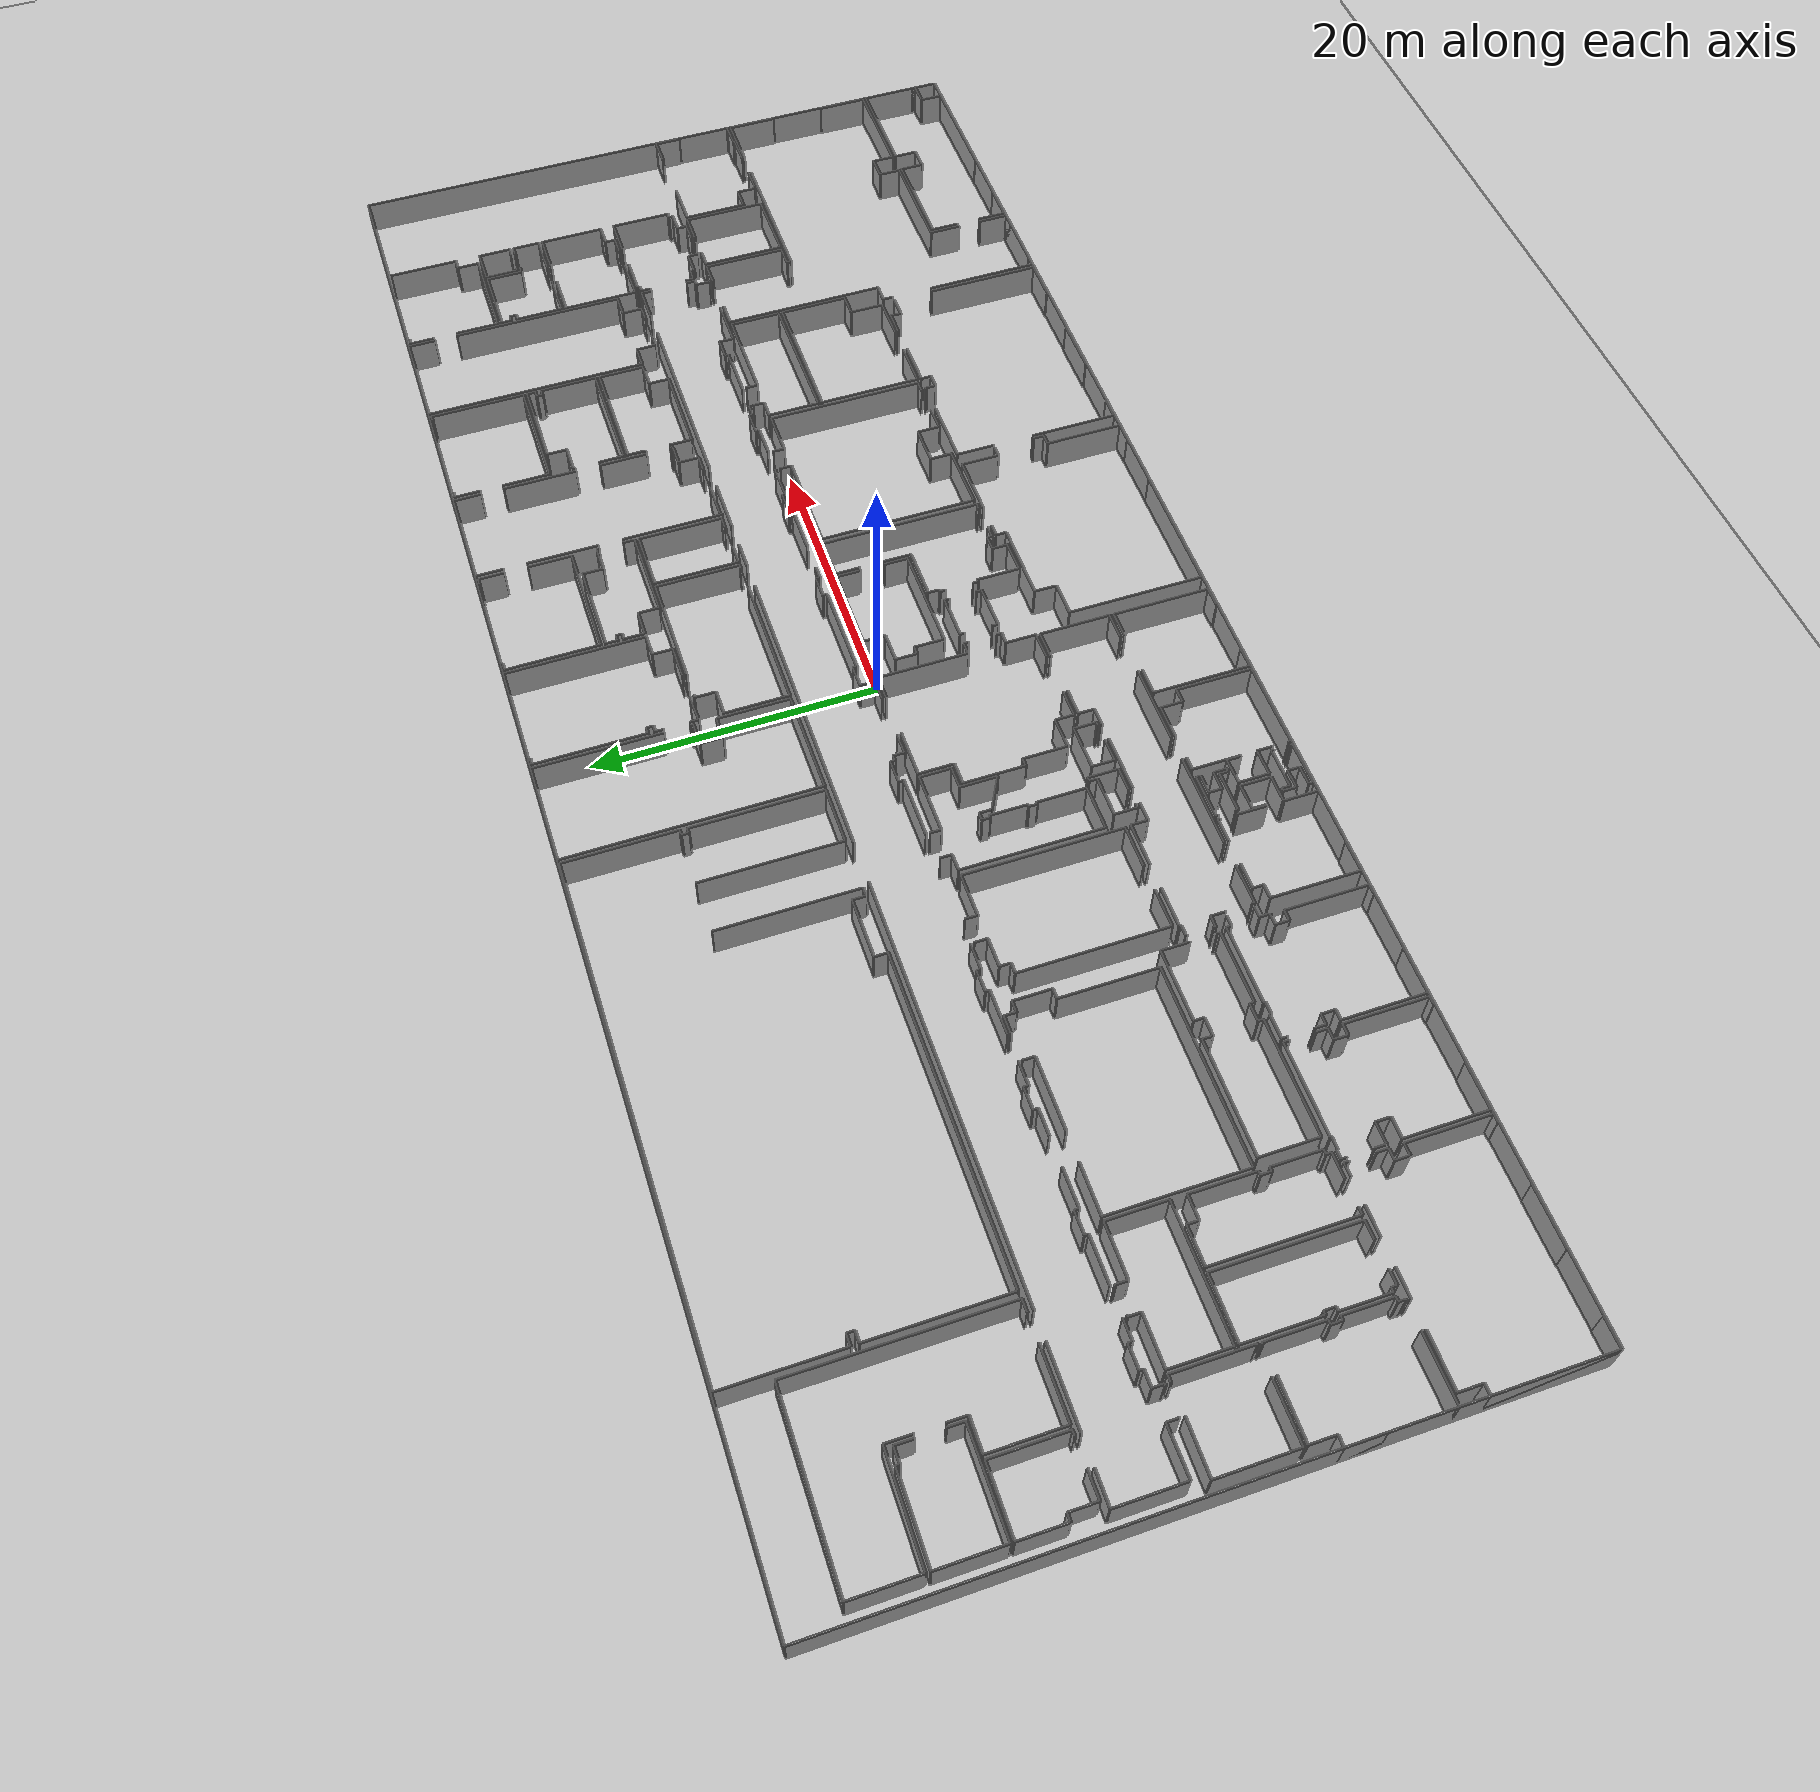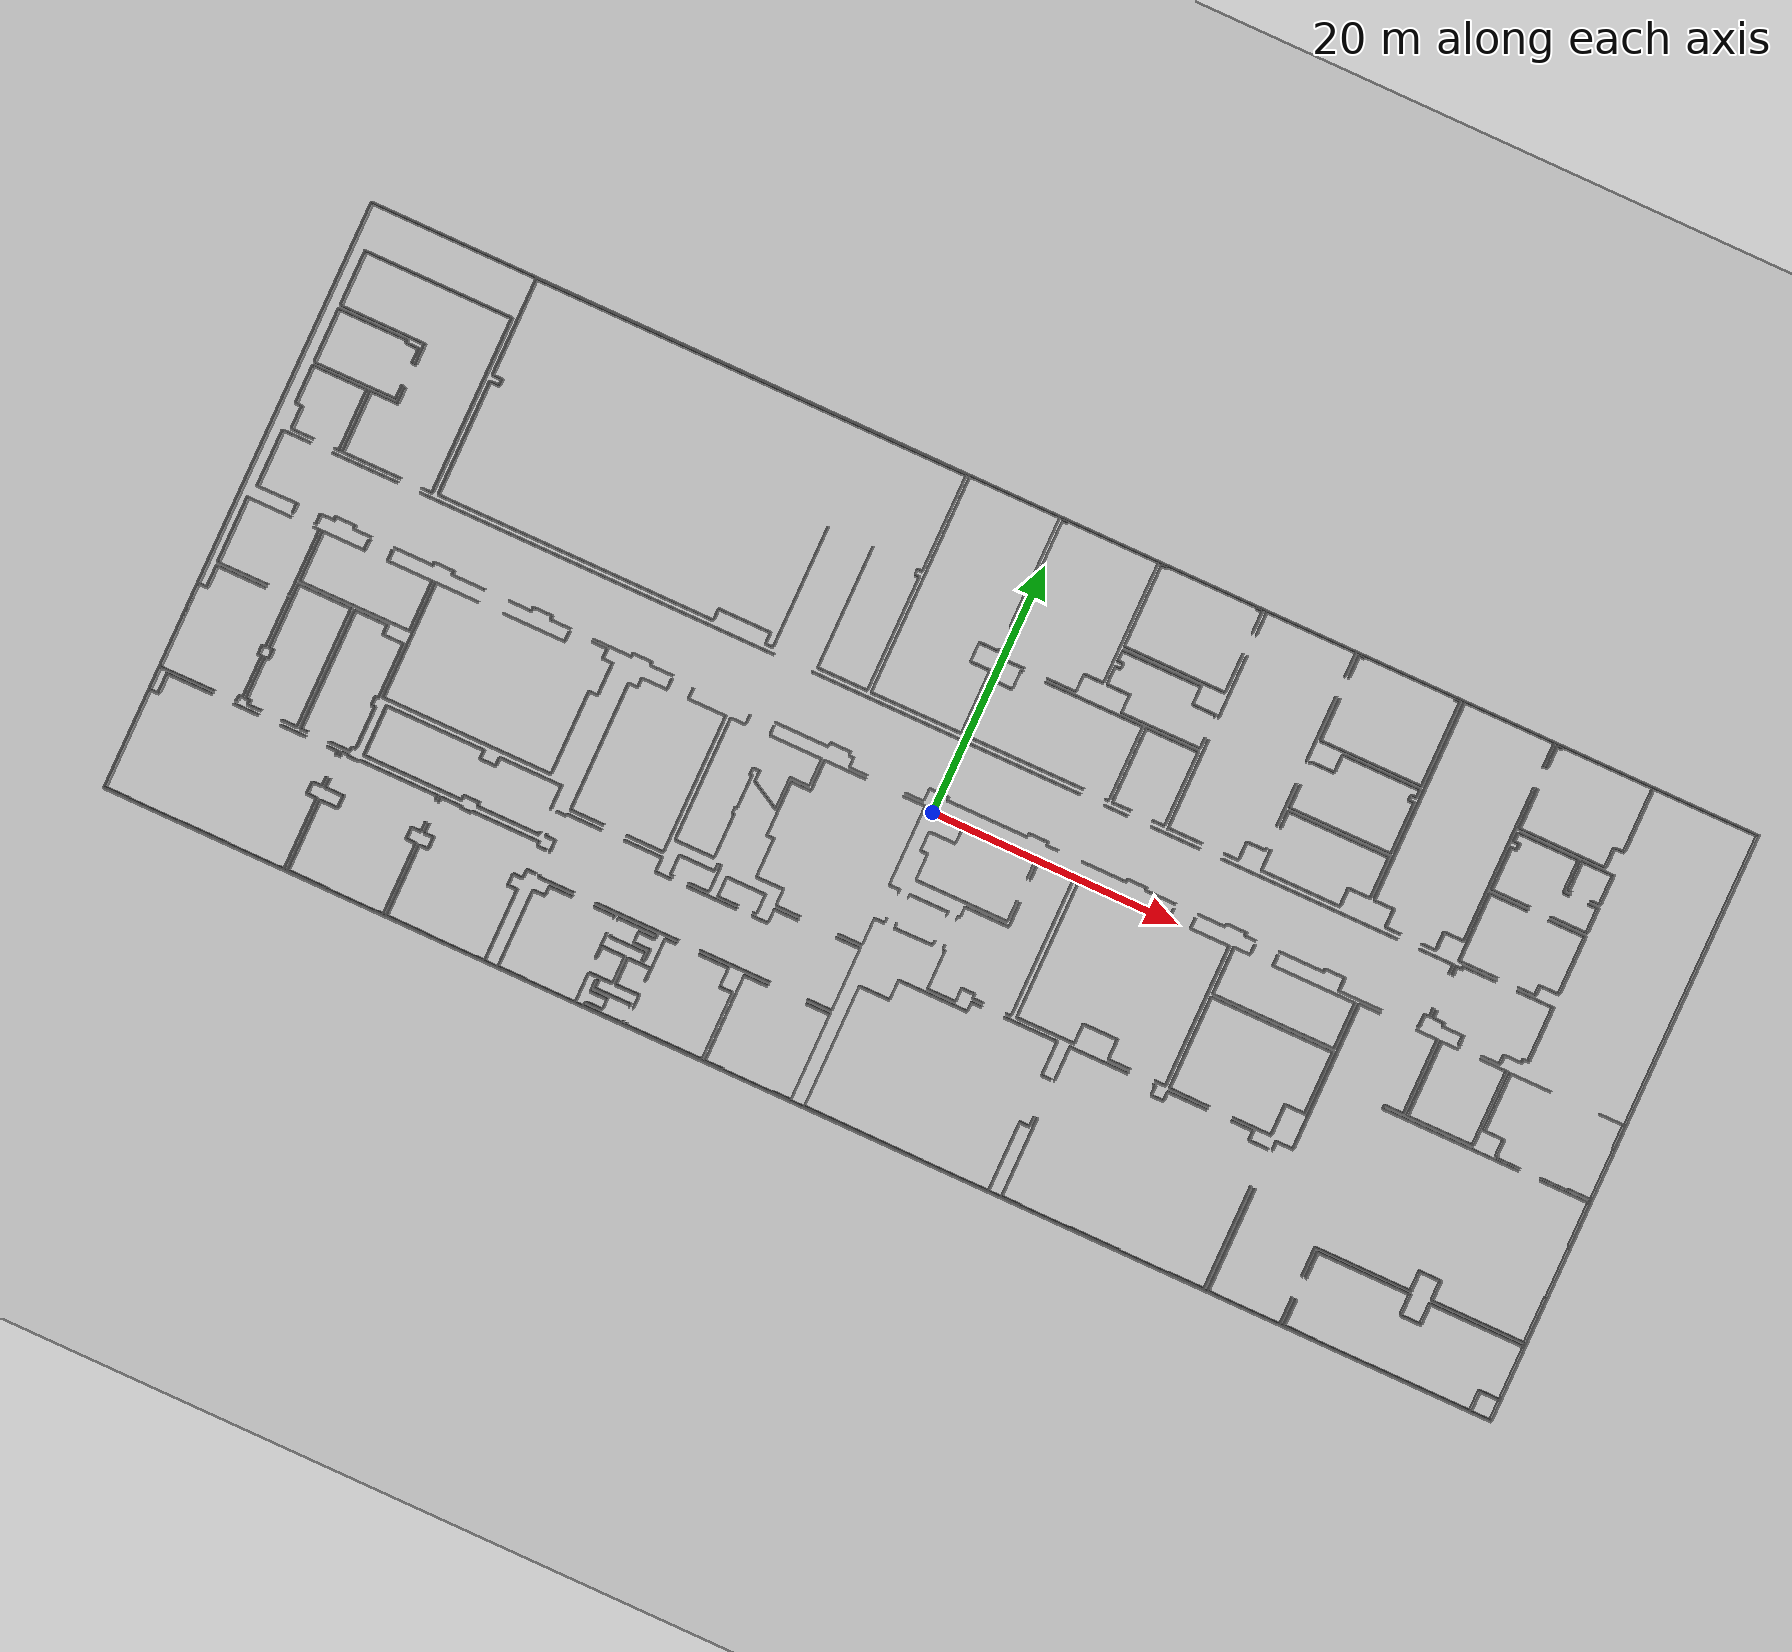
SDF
<sdf version="1.6">
  <world name="default">
    <light name="sun" type="directional">
      <cast_shadows>1</cast_shadows>
      <pose frame="">0 0 10 0 -0 0</pose>
      <diffuse>0.8 0.8 0.8 1</diffuse>
      <specular>0.1 0.1 0.1 1</specular>
      <attenuation>
        <range>1000</range>
        <constant>0.9</constant>
        <linear>0.01</linear>
        <quadratic>0.001</quadratic>
      </attenuation>
      <direction>-0.5 0.5 -1</direction>
    </light>
    <model name="ground_plane">
      <static>1</static>
      <link name="link">
        <collision name="collision">
          <geometry>
            <plane>
              <normal>0 0 1</normal>
              <size>100 100</size>
            </plane>
          </geometry>
          <surface>
            <friction>
              <ode>
                <mu>100</mu>
                <mu2>50</mu2>
              </ode>
              <torsional>
                <ode />
              </torsional>
            </friction>
            <contact>
              <ode />
            </contact>
            <bounce />
          </surface>
          <max_contacts>10</max_contacts>
        </collision>
        <visual name="visual">
          <cast_shadows>0</cast_shadows>
          <geometry>
            <plane>
              <normal>0 0 1</normal>
              <size>100 100</size>
            </plane>
          </geometry>
          <material>
            <script>
              <uri>file://media/materials/scripts/gazebo.material</uri>
              <name>Gazebo/Grey</name>
            </script>
          </material>
        </visual>
        <self_collide>0</self_collide>
        <kinematic>0</kinematic>
        <gravity>1</gravity>
      </link>
    </model>
    <gravity>0 0 -9.8</gravity>
    <magnetic_field>6e-06 2.3e-05 -4.2e-05</magnetic_field>
    <atmosphere type="adiabatic" />
    <physics default="0" name="default_physics" type="ode">
      <max_step_size>0.001</max_step_size>
      <real_time_factor>1</real_time_factor>
      <real_time_update_rate>1000</real_time_update_rate>
    </physics>
    <scene>
      <ambient>0.4 0.4 0.4 1</ambient>
      <background>0.7 0.7 0.7 1</background>
      <shadows>1</shadows>
    </scene>
    <spherical_coordinates>
      <surface_model>EARTH_WGS84</surface_model>
      <latitude_deg>0</latitude_deg>
      <longitude_deg>0</longitude_deg>
      <elevation>0</elevation>
      <heading_deg>0</heading_deg>
    </spherical_coordinates>
  <model name="50057022">
		<static>1</static>
		<link name="Wall_0">
			<collision name="Wall_0_Collision">
				<geometry>
					<box>
						<size>4.35774991319 0.1 2.5</size>
					</box>
				</geometry>
				<pose frame="">2.17887495659 0 1.25 0 0 0</pose>
			</collision>
			<visual name="Wall_0_Visual">
				<pose frame="">2.17887495659 0 1.25 0 0 0</pose>
				<geometry>
					<box>
						<size>4.35774991319 0.1 2.5</size>
					</box>
				</geometry>
				<material>
					<script>
						<uri>file://media/materials/scripts/gazebo.material</uri>
						<name>Gazebo/Grey</name>
					</script>
					<ambient>1 1 1 1</ambient>
				</material>
			</visual>
			<pose frame="">1.04935783863 -12.5339964058 0 0 0 1.57079632679</pose>
		</link>
		<link name="Wall_1">
			<collision name="Wall_1_Collision">
				<geometry>
					<box>
						<size>5.58200072492 0.1 2.5</size>
					</box>
				</geometry>
				<pose frame="">2.79100036246 0 1.25 0 0 0</pose>
			</collision>
			<visual name="Wall_1_Visual">
				<pose frame="">2.79100036246 0 1.25 0 0 0</pose>
				<geometry>
					<box>
						<size>5.58200072492 0.1 2.5</size>
					</box>
				</geometry>
				<material>
					<script>
						<uri>file://media/materials/scripts/gazebo.material</uri>
						<name>Gazebo/Grey</name>
					</script>
					<ambient>1 1 1 1</ambient>
				</material>
			</visual>
			<pose frame="">1.04935783863 -8.17624649264 0 0 0 0.0</pose>
		</link>
		<link name="Wall_2">
			<collision name="Wall_2_Collision">
				<geometry>
					<box>
						<size>0.218616216381 0.1 2.5</size>
					</box>
				</geometry>
				<pose frame="">0.10930810819 0 1.25 0 0 0</pose>
			</collision>
			<visual name="Wall_2_Visual">
				<pose frame="">0.10930810819 0 1.25 0 0 0</pose>
				<geometry>
					<box>
						<size>0.218616216381 0.1 2.5</size>
					</box>
				</geometry>
				<material>
					<script>
						<uri>file://media/materials/scripts/gazebo.material</uri>
						<name>Gazebo/Grey</name>
					</script>
					<ambient>1 1 1 1</ambient>
				</material>
			</visual>
			<pose frame="">6.63135856355 -8.17624649264 0 0 0 -1.57079632679</pose>
		</link>
		<link name="Wall_3">
			<collision name="Wall_3_Collision">
				<geometry>
					<box>
						<size>1.0347834242 0.1 2.5</size>
					</box>
				</geometry>
				<pose frame="">0.517391712101 0 1.25 0 0 0</pose>
			</collision>
			<visual name="Wall_3_Visual">
				<pose frame="">0.517391712101 0 1.25 0 0 0</pose>
				<geometry>
					<box>
						<size>1.0347834242 0.1 2.5</size>
					</box>
				</geometry>
				<material>
					<script>
						<uri>file://media/materials/scripts/gazebo.material</uri>
						<name>Gazebo/Grey</name>
					</script>
					<ambient>1 1 1 1</ambient>
				</material>
			</visual>
			<pose frame="">6.63135856355 -8.39486270902 0 0 0 0.0</pose>
		</link>
		<link name="Wall_4">
			<collision name="Wall_4_Collision">
				<geometry>
					<box>
						<size>1.19510198288 0.1 2.5</size>
					</box>
				</geometry>
				<pose frame="">0.59755099144 0 1.25 0 0 0</pose>
			</collision>
			<visual name="Wall_4_Visual">
				<pose frame="">0.59755099144 0 1.25 0 0 0</pose>
				<geometry>
					<box>
						<size>1.19510198288 0.1 2.5</size>
					</box>
				</geometry>
				<material>
					<script>
						<uri>file://media/materials/scripts/gazebo.material</uri>
						<name>Gazebo/Grey</name>
					</script>
					<ambient>1 1 1 1</ambient>
				</material>
			</visual>
			<pose frame="">7.66614198775 -8.39486270902 0 0 0 -1.57079632679</pose>
		</link>
		<link name="Wall_5">
			<collision name="Wall_5_Collision">
				<geometry>
					<box>
						<size>1.11525953864 0.1 2.5</size>
					</box>
				</geometry>
				<pose frame="">0.557629769319 0 1.25 0 0 0</pose>
			</collision>
			<visual name="Wall_5_Visual">
				<pose frame="">0.557629769319 0 1.25 0 0 0</pose>
				<geometry>
					<box>
						<size>1.11525953864 0.1 2.5</size>
					</box>
				</geometry>
				<material>
					<script>
						<uri>file://media/materials/scripts/gazebo.material</uri>
						<name>Gazebo/Grey</name>
					</script>
					<ambient>1 1 1 1</ambient>
				</material>
			</visual>
			<pose frame="">7.66614198775 -11.3750136239 0 0 0 -1.57079632679</pose>
		</link>
		<link name="Wall_6">
			<collision name="Wall_6_Collision">
				<geometry>
					<box>
						<size>6.6169286076 0.1 2.5</size>
					</box>
				</geometry>
				<pose frame="">3.3084643038 0 1.25 0 0 0</pose>
			</collision>
			<visual name="Wall_6_Visual">
				<pose frame="">3.3084643038 0 1.25 0 0 0</pose>
				<geometry>
					<box>
						<size>6.6169286076 0.1 2.5</size>
					</box>
				</geometry>
				<material>
					<script>
						<uri>file://media/materials/scripts/gazebo.material</uri>
						<name>Gazebo/Grey</name>
					</script>
					<ambient>1 1 1 1</ambient>
				</material>
			</visual>
			<pose frame="">7.66614198775 -12.4902731625 0 0 0 -3.13498482025</pose>
		</link>
		<link name="Wall_7">
			<collision name="Wall_7_Collision">
				<geometry>
					<box>
						<size>1.8363762176 0.1 2.5</size>
					</box>
				</geometry>
				<pose frame="">0.918188108799 0 1.25 0 0 0</pose>
			</collision>
			<visual name="Wall_7_Visual">
				<pose frame="">0.918188108799 0 1.25 0 0 0</pose>
				<geometry>
					<box>
						<size>1.8363762176 0.1 2.5</size>
					</box>
				</geometry>
				<material>
					<script>
						<uri>file://media/materials/scripts/gazebo.material</uri>
						<name>Gazebo/Grey</name>
					</script>
					<ambient>1 1 1 1</ambient>
				</material>
			</visual>
			<pose frame="">1.55946234352 -17.7079135268 0 0 0 1.57079632679</pose>
		</link>
		<link name="Wall_8">
			<collision name="Wall_8_Collision">
				<geometry>
					<box>
						<size>0.510104504888 0.1 2.5</size>
					</box>
				</geometry>
				<pose frame="">0.255052252444 0 1.25 0 0 0</pose>
			</collision>
			<visual name="Wall_8_Visual">
				<pose frame="">0.255052252444 0 1.25 0 0 0</pose>
				<geometry>
					<box>
						<size>0.510104504888 0.1 2.5</size>
					</box>
				</geometry>
				<material>
					<script>
						<uri>file://media/materials/scripts/gazebo.material</uri>
						<name>Gazebo/Grey</name>
					</script>
					<ambient>1 1 1 1</ambient>
				</material>
			</visual>
			<pose frame="">1.55946234352 -15.8715373092 0 0 0 3.14159265359</pose>
		</link>
		<link name="Wall_9">
			<collision name="Wall_9_Collision">
				<geometry>
					<box>
						<size>3.11892468703 0.1 2.5</size>
					</box>
				</geometry>
				<pose frame="">1.55946234352 0 1.25 0 0 0</pose>
			</collision>
			<visual name="Wall_9_Visual">
				<pose frame="">1.55946234352 0 1.25 0 0 0</pose>
				<geometry>
					<box>
						<size>3.11892468703 0.1 2.5</size>
					</box>
				</geometry>
				<material>
					<script>
						<uri>file://media/materials/scripts/gazebo.material</uri>
						<name>Gazebo/Grey</name>
					</script>
					<ambient>1 1 1 1</ambient>
				</material>
			</visual>
			<pose frame="">1.04935783863 -15.8715373092 0 0 0 1.57079632679</pose>
		</link>
		<link name="Wall_10">
			<collision name="Wall_10_Collision">
				<geometry>
					<box>
						<size>4.38689874204 0.1 2.5</size>
					</box>
				</geometry>
				<pose frame="">2.19344937102 0 1.25 0 0 0</pose>
			</collision>
			<visual name="Wall_10_Visual">
				<pose frame="">2.19344937102 0 1.25 0 0 0</pose>
				<geometry>
					<box>
						<size>4.38689874204 0.1 2.5</size>
					</box>
				</geometry>
				<material>
					<script>
						<uri>file://media/materials/scripts/gazebo.material</uri>
						<name>Gazebo/Grey</name>
					</script>
					<ambient>1 1 1 1</ambient>
				</material>
			</visual>
			<pose frame="">1.04935783863 -12.7526126222 0 0 0 0.0</pose>
		</link>
		<link name="Wall_11">
			<collision name="Wall_11_Collision">
				<geometry>
					<box>
						<size>4.9407264902 0.1 2.5</size>
					</box>
				</geometry>
				<pose frame="">2.4703632451 0 1.25 0 0 0</pose>
			</collision>
			<visual name="Wall_11_Visual">
				<pose frame="">2.4703632451 0 1.25 0 0 0</pose>
				<geometry>
					<box>
						<size>4.9407264902 0.1 2.5</size>
					</box>
				</geometry>
				<material>
					<script>
						<uri>file://media/materials/scripts/gazebo.material</uri>
						<name>Gazebo/Grey</name>
					</script>
					<ambient>1 1 1 1</ambient>
				</material>
			</visual>
			<pose frame="">5.43625658066 -12.7526126222 0 0 0 -1.57079632679</pose>
		</link>
		<link name="Wall_12">
			<collision name="Wall_12_Collision">
				<geometry>
					<box>
						<size>0.393509189485 0.1 2.5</size>
					</box>
				</geometry>
				<pose frame="">0.196754594743 0 1.25 0 0 0</pose>
			</collision>
			<visual name="Wall_12_Visual">
				<pose frame="">0.196754594743 0 1.25 0 0 0</pose>
				<geometry>
					<box>
						<size>0.393509189485 0.1 2.5</size>
					</box>
				</geometry>
				<material>
					<script>
						<uri>file://media/materials/scripts/gazebo.material</uri>
						<name>Gazebo/Grey</name>
					</script>
					<ambient>1 1 1 1</ambient>
				</material>
			</visual>
			<pose frame="">5.43625658066 -17.6933391124 0 0 0 3.14159265359</pose>
		</link>
		<link name="Wall_13">
			<collision name="Wall_13_Collision">
				<geometry>
					<box>
						<size>1.7635643693 0.1 2.5</size>
					</box>
				</geometry>
				<pose frame="">0.881782184648 0 1.25 0 0 0</pose>
			</collision>
			<visual name="Wall_13_Visual">
				<pose frame="">0.881782184648 0 1.25 0 0 0</pose>
				<geometry>
					<box>
						<size>1.7635643693 0.1 2.5</size>
					</box>
				</geometry>
				<material>
					<script>
						<uri>file://media/materials/scripts/gazebo.material</uri>
						<name>Gazebo/Grey</name>
					</script>
					<ambient>1 1 1 1</ambient>
				</material>
			</visual>
			<pose frame="">3.32296648899 -17.6933391124 0 0 0 -3.13332837893</pose>
		</link>
		<link name="Wall_14">
			<collision name="Wall_14_Collision">
				<geometry>
					<box>
						<size>4.96417228732 0.1 2.5</size>
					</box>
				</geometry>
				<pose frame="">2.48208614366 0 1.25 0 0 0</pose>
			</collision>
			<visual name="Wall_14_Visual">
				<pose frame="">2.48208614366 0 1.25 0 0 0</pose>
				<geometry>
					<box>
						<size>4.96417228732 0.1 2.5</size>
					</box>
				</geometry>
				<material>
					<script>
						<uri>file://media/materials/scripts/gazebo.material</uri>
						<name>Gazebo/Grey</name>
					</script>
					<ambient>1 1 1 1</ambient>
				</material>
			</visual>
			<pose frame="">5.71608533763 -17.6939727826 0 0 0 1.57079632679</pose>
		</link>
		<link name="Wall_15">
			<collision name="Wall_15_Collision">
				<geometry>
					<box>
						<size>2.19744149323 0.1 2.5</size>
					</box>
				</geometry>
				<pose frame="">1.09872074662 0 1.25 0 0 0</pose>
			</collision>
			<visual name="Wall_15_Visual">
				<pose frame="">1.09872074662 0 1.25 0 0 0</pose>
				<geometry>
					<box>
						<size>2.19744149323 0.1 2.5</size>
					</box>
				</geometry>
				<material>
					<script>
						<uri>file://media/materials/scripts/gazebo.material</uri>
						<name>Gazebo/Grey</name>
					</script>
					<ambient>1 1 1 1</ambient>
				</material>
			</visual>
			<pose frame="">5.71608533763 -12.7298004953 0 0 0 0.0</pose>
		</link>
		<link name="Wall_16">
			<collision name="Wall_16_Collision">
				<geometry>
					<box>
						<size>1.2857168204 0.1 2.5</size>
					</box>
				</geometry>
				<pose frame="">0.642858410198 0 1.25 0 0 0</pose>
			</collision>
			<visual name="Wall_16_Visual">
				<pose frame="">0.642858410198 0 1.25 0 0 0</pose>
				<geometry>
					<box>
						<size>1.2857168204 0.1 2.5</size>
					</box>
				</geometry>
				<material>
					<script>
						<uri>file://media/materials/scripts/gazebo.material</uri>
						<name>Gazebo/Grey</name>
					</script>
					<ambient>1 1 1 1</ambient>
				</material>
			</visual>
			<pose frame="">7.91352683086 -12.7298004953 0 0 0 1.57079632679</pose>
		</link>
		<link name="Wall_17">
			<collision name="Wall_17_Collision">
				<geometry>
					<box>
						<size>1.70812137065 0.1 2.5</size>
					</box>
				</geometry>
				<pose frame="">0.854060685327 0 1.25 0 0 0</pose>
			</collision>
			<visual name="Wall_17_Visual">
				<pose frame="">0.854060685327 0 1.25 0 0 0</pose>
				<geometry>
					<box>
						<size>1.70812137065 0.1 2.5</size>
					</box>
				</geometry>
				<material>
					<script>
						<uri>file://media/materials/scripts/gazebo.material</uri>
						<name>Gazebo/Grey</name>
					</script>
					<ambient>1 1 1 1</ambient>
				</material>
			</visual>
			<pose frame="">7.91352683086 -9.60897479767 0 0 0 1.57079632679</pose>
		</link>
		<link name="Wall_18">
			<collision name="Wall_18_Collision">
				<geometry>
					<box>
						<size>6.8492143757 0.1 2.5</size>
					</box>
				</geometry>
				<pose frame="">3.42460718785 0 1.25 0 0 0</pose>
			</collision>
			<visual name="Wall_18_Visual">
				<pose frame="">3.42460718785 0 1.25 0 0 0</pose>
				<geometry>
					<box>
						<size>6.8492143757 0.1 2.5</size>
					</box>
				</geometry>
				<material>
					<script>
						<uri>file://media/materials/scripts/gazebo.material</uri>
						<name>Gazebo/Grey</name>
					</script>
					<ambient>1 1 1 1</ambient>
				</material>
			</visual>
			<pose frame="">7.91352683086 -7.90085342702 0 0 0 3.14159265359</pose>
		</link>
		<link name="Wall_19">
			<collision name="Wall_19_Collision">
				<geometry>
					<box>
						<size>4.43733888935 0.1 2.5</size>
					</box>
				</geometry>
				<pose frame="">2.21866944468 0 1.25 0 0 0</pose>
			</collision>
			<visual name="Wall_19_Visual">
				<pose frame="">2.21866944468 0 1.25 0 0 0</pose>
				<geometry>
					<box>
						<size>4.43733888935 0.1 2.5</size>
					</box>
				</geometry>
				<material>
					<script>
						<uri>file://media/materials/scripts/gazebo.material</uri>
						<name>Gazebo/Grey</name>
					</script>
					<ambient>1 1 1 1</ambient>
				</material>
			</visual>
			<pose frame="">1.06431245517 -7.90085342702 0 0 0 1.57079632679</pose>
		</link>
		<link name="Wall_20">
			<collision name="Wall_20_Collision">
				<geometry>
					<box>
						<size>11.9184491809 0.1 2.5</size>
					</box>
				</geometry>
				<pose frame="">5.95922459046 0 1.25 0 0 0</pose>
			</collision>
			<visual name="Wall_20_Visual">
				<pose frame="">5.95922459046 0 1.25 0 0 0</pose>
				<geometry>
					<box>
						<size>11.9184491809 0.1 2.5</size>
					</box>
				</geometry>
				<material>
					<script>
						<uri>file://media/materials/scripts/gazebo.material</uri>
						<name>Gazebo/Grey</name>
					</script>
					<ambient>1 1 1 1</ambient>
				</material>
			</visual>
			<pose frame="">1.06431245517 -3.46351453766 0 0 0 0.0</pose>
		</link>
		<link name="Wall_21">
			<collision name="Wall_21_Collision">
				<geometry>
					<box>
						<size>14.2246284792 0.1 2.5</size>
					</box>
				</geometry>
				<pose frame="">7.11231423958 0 1.25 0 0 0</pose>
			</collision>
			<visual name="Wall_21_Visual">
				<pose frame="">7.11231423958 0 1.25 0 0 0</pose>
				<geometry>
					<box>
						<size>14.2246284792 0.1 2.5</size>
					</box>
				</geometry>
				<material>
					<script>
						<uri>file://media/materials/scripts/gazebo.material</uri>
						<name>Gazebo/Grey</name>
					</script>
					<ambient>1 1 1 1</ambient>
				</material>
			</visual>
			<pose frame="">12.9827616361 -3.46351453766 0 0 0 -1.57079632679</pose>
		</link>
		<link name="Wall_22">
			<collision name="Wall_22_Collision">
				<geometry>
					<box>
						<size>0.828840611669 0.1 2.5</size>
					</box>
				</geometry>
				<pose frame="">0.414420305835 0 1.25 0 0 0</pose>
			</collision>
			<visual name="Wall_22_Visual">
				<pose frame="">0.414420305835 0 1.25 0 0 0</pose>
				<geometry>
					<box>
						<size>0.828840611669 0.1 2.5</size>
					</box>
				</geometry>
				<material>
					<script>
						<uri>file://media/materials/scripts/gazebo.material</uri>
						<name>Gazebo/Grey</name>
					</script>
					<ambient>1 1 1 1</ambient>
				</material>
			</visual>
			<pose frame="">12.9827616361 -17.6881430168 0 0 0 3.14159265359</pose>
		</link>
		<link name="Wall_23">
			<collision name="Wall_23_Collision">
				<geometry>
					<box>
						<size>4.6745886446 0.1 2.5</size>
					</box>
				</geometry>
				<pose frame="">2.3372943223 0 1.25 0 0 0</pose>
			</collision>
			<visual name="Wall_23_Visual">
				<pose frame="">2.3372943223 0 1.25 0 0 0</pose>
				<geometry>
					<box>
						<size>4.6745886446 0.1 2.5</size>
					</box>
				</geometry>
				<material>
					<script>
						<uri>file://media/materials/scripts/gazebo.material</uri>
						<name>Gazebo/Grey</name>
					</script>
					<ambient>1 1 1 1</ambient>
				</material>
			</visual>
			<pose frame="">10.390670347 -17.6881430168 0 0 0 -3.14034553481</pose>
		</link>
		<link name="Wall_24">
			<collision name="Wall_24_Collision">
				<geometry>
					<box>
						<size>9.23168756511 0.1 2.5</size>
					</box>
				</geometry>
				<pose frame="">4.61584378255 0 1.25 0 0 0</pose>
			</collision>
			<visual name="Wall_24_Visual">
				<pose frame="">4.61584378255 0 1.25 0 0 0</pose>
				<geometry>
					<box>
						<size>9.23168756511 0.1 2.5</size>
					</box>
				</geometry>
				<material>
					<script>
						<uri>file://media/materials/scripts/gazebo.material</uri>
						<name>Gazebo/Grey</name>
					</script>
					<ambient>1 1 1 1</ambient>
				</material>
			</visual>
			<pose frame="">13.4549726635 -17.6284512847 0 0 0 1.57079632679</pose>
		</link>
		<link name="Wall_25">
			<collision name="Wall_25_Collision">
				<geometry>
					<box>
						<size>0.759770560697 0.1 2.5</size>
					</box>
				</geometry>
				<pose frame="">0.379885280348 0 1.25 0 0 0</pose>
			</collision>
			<visual name="Wall_25_Visual">
				<pose frame="">0.379885280348 0 1.25 0 0 0</pose>
				<geometry>
					<box>
						<size>0.759770560697 0.1 2.5</size>
					</box>
				</geometry>
				<material>
					<script>
						<uri>file://media/materials/scripts/gazebo.material</uri>
						<name>Gazebo/Grey</name>
					</script>
					<ambient>1 1 1 1</ambient>
				</material>
			</visual>
			<pose frame="">13.4549726635 -8.39676371959 0 0 0 0.0</pose>
		</link>
		<link name="Wall_26">
			<collision name="Wall_26_Collision">
				<geometry>
					<box>
						<size>0.495910292578 0.1 2.5</size>
					</box>
				</geometry>
				<pose frame="">0.247955146289 0 1.25 0 0 0</pose>
			</collision>
			<visual name="Wall_26_Visual">
				<pose frame="">0.247955146289 0 1.25 0 0 0</pose>
				<geometry>
					<box>
						<size>0.495910292578 0.1 2.5</size>
					</box>
				</geometry>
				<material>
					<script>
						<uri>file://media/materials/scripts/gazebo.material</uri>
						<name>Gazebo/Grey</name>
					</script>
					<ambient>1 1 1 1</ambient>
				</material>
			</visual>
			<pose frame="">14.2147432242 -8.39676371959 0 0 0 1.57079632679</pose>
		</link>
		<link name="Wall_27">
			<collision name="Wall_27_Collision">
				<geometry>
					<box>
						<size>0.782455953585 0.1 2.5</size>
					</box>
				</geometry>
				<pose frame="">0.391227976792 0 1.25 0 0 0</pose>
			</collision>
			<visual name="Wall_27_Visual">
				<pose frame="">0.391227976792 0 1.25 0 0 0</pose>
				<geometry>
					<box>
						<size>0.782455953585 0.1 2.5</size>
					</box>
				</geometry>
				<material>
					<script>
						<uri>file://media/materials/scripts/gazebo.material</uri>
						<name>Gazebo/Grey</name>
					</script>
					<ambient>1 1 1 1</ambient>
				</material>
			</visual>
			<pose frame="">14.2147432242 -7.90085342702 0 0 0 3.14159265359</pose>
		</link>
		<link name="Wall_28">
			<collision name="Wall_28_Collision">
				<geometry>
					<box>
						<size>7.83545866316 0.1 2.5</size>
					</box>
				</geometry>
				<pose frame="">3.91772933158 0 1.25 0 0 0</pose>
			</collision>
			<visual name="Wall_28_Visual">
				<pose frame="">3.91772933158 0 1.25 0 0 0</pose>
				<geometry>
					<box>
						<size>7.83545866316 0.1 2.5</size>
					</box>
				</geometry>
				<material>
					<script>
						<uri>file://media/materials/scripts/gazebo.material</uri>
						<name>Gazebo/Grey</name>
					</script>
					<ambient>1 1 1 1</ambient>
				</material>
			</visual>
			<pose frame="">13.4322872706 -7.90085342702 0 0 0 1.57079632679</pose>
		</link>
		<link name="Wall_29">
			<collision name="Wall_29_Collision">
				<geometry>
					<box>
						<size>34.9782144188 0.1 2.5</size>
					</box>
				</geometry>
				<pose frame="">17.4891072094 0 1.25 0 0 0</pose>
			</collision>
			<visual name="Wall_29_Visual">
				<pose frame="">17.4891072094 0 1.25 0 0 0</pose>
				<geometry>
					<box>
						<size>34.9782144188 0.1 2.5</size>
					</box>
				</geometry>
				<material>
					<script>
						<uri>file://media/materials/scripts/gazebo.material</uri>
						<name>Gazebo/Grey</name>
					</script>
					<ambient>1 1 1 1</ambient>
				</material>
			</visual>
			<pose frame="">13.4322872706 -0.0653947638565 0 0 0 0.0</pose>
		</link>
		<link name="Wall_30">
			<collision name="Wall_30_Collision">
				<geometry>
					<box>
						<size>7.83178337604 0.1 2.5</size>
					</box>
				</geometry>
				<pose frame="">3.91589168802 0 1.25 0 0 0</pose>
			</collision>
			<visual name="Wall_30_Visual">
				<pose frame="">3.91589168802 0 1.25 0 0 0</pose>
				<geometry>
					<box>
						<size>7.83178337604 0.1 2.5</size>
					</box>
				</geometry>
				<material>
					<script>
						<uri>file://media/materials/scripts/gazebo.material</uri>
						<name>Gazebo/Grey</name>
					</script>
					<ambient>1 1 1 1</ambient>
				</material>
			</visual>
			<pose frame="">48.4105016894 -0.0653947638565 0 0 0 -1.57079632679</pose>
		</link>
		<link name="Wall_31">
			<collision name="Wall_31_Collision">
				<geometry>
					<box>
						<size>0.394016125639 0.1 2.5</size>
					</box>
				</geometry>
				<pose frame="">0.19700806282 0 1.25 0 0 0</pose>
			</collision>
			<visual name="Wall_31_Visual">
				<pose frame="">0.19700806282 0 1.25 0 0 0</pose>
				<geometry>
					<box>
						<size>0.394016125639 0.1 2.5</size>
					</box>
				</geometry>
				<material>
					<script>
						<uri>file://media/materials/scripts/gazebo.material</uri>
						<name>Gazebo/Grey</name>
					</script>
					<ambient>1 1 1 1</ambient>
				</material>
			</visual>
			<pose frame="">48.4105016894 -7.8971781399 0 0 0 3.14159265359</pose>
		</link>
		<link name="Wall_32">
			<collision name="Wall_32_Collision">
				<geometry>
					<box>
						<size>0.48323688873 0.1 2.5</size>
					</box>
				</geometry>
				<pose frame="">0.241618444365 0 1.25 0 0 0</pose>
			</collision>
			<visual name="Wall_32_Visual">
				<pose frame="">0.241618444365 0 1.25 0 0 0</pose>
				<geometry>
					<box>
						<size>0.48323688873 0.1 2.5</size>
					</box>
				</geometry>
				<material>
					<script>
						<uri>file://media/materials/scripts/gazebo.material</uri>
						<name>Gazebo/Grey</name>
					</script>
					<ambient>1 1 1 1</ambient>
				</material>
			</visual>
			<pose frame="">48.0164855637 -7.8971781399 0 0 0 -1.57079632679</pose>
		</link>
		<link name="Wall_33">
			<collision name="Wall_33_Collision">
				<geometry>
					<box>
						<size>0.358403860826 0.1 2.5</size>
					</box>
				</geometry>
				<pose frame="">0.179201930413 0 1.25 0 0 0</pose>
			</collision>
			<visual name="Wall_33_Visual">
				<pose frame="">0.179201930413 0 1.25 0 0 0</pose>
				<geometry>
					<box>
						<size>0.358403860826 0.1 2.5</size>
					</box>
				</geometry>
				<material>
					<script>
						<uri>file://media/materials/scripts/gazebo.material</uri>
						<name>Gazebo/Grey</name>
					</script>
					<ambient>1 1 1 1</ambient>
				</material>
			</visual>
			<pose frame="">48.0164855637 -8.38041502863 0 0 0 0.0</pose>
		</link>
		<link name="Wall_34">
			<collision name="Wall_34_Collision">
				<geometry>
					<box>
						<size>9.22991328857 0.1 2.5</size>
					</box>
				</geometry>
				<pose frame="">4.61495664429 0 1.25 0 0 0</pose>
			</collision>
			<visual name="Wall_34_Visual">
				<pose frame="">4.61495664429 0 1.25 0 0 0</pose>
				<geometry>
					<box>
						<size>9.22991328857 0.1 2.5</size>
					</box>
				</geometry>
				<material>
					<script>
						<uri>file://media/materials/scripts/gazebo.material</uri>
						<name>Gazebo/Grey</name>
					</script>
					<ambient>1 1 1 1</ambient>
				</material>
			</visual>
			<pose frame="">48.3748894246 -8.38041502863 0 0 0 -1.57079632679</pose>
		</link>
		<link name="Wall_35">
			<collision name="Wall_35_Collision">
				<geometry>
					<box>
						<size>4.04649111468 0.1 2.5</size>
					</box>
				</geometry>
				<pose frame="">2.02324555734 0 1.25 0 0 0</pose>
			</collision>
			<visual name="Wall_35_Visual">
				<pose frame="">2.02324555734 0 1.25 0 0 0</pose>
				<geometry>
					<box>
						<size>4.04649111468 0.1 2.5</size>
					</box>
				</geometry>
				<material>
					<script>
						<uri>file://media/materials/scripts/gazebo.material</uri>
						<name>Gazebo/Grey</name>
					</script>
					<ambient>1 1 1 1</ambient>
				</material>
			</visual>
			<pose frame="">48.3748894246 -17.6103283172 0 0 0 3.14159265359</pose>
		</link>
		<link name="Wall_36">
			<collision name="Wall_36_Collision">
				<geometry>
					<box>
						<size>9.81010171674 0.1 2.5</size>
					</box>
				</geometry>
				<pose frame="">4.90505085837 0 1.25 0 0 0</pose>
			</collision>
			<visual name="Wall_36_Visual">
				<pose frame="">4.90505085837 0 1.25 0 0 0</pose>
				<geometry>
					<box>
						<size>9.81010171674 0.1 2.5</size>
					</box>
				</geometry>
				<material>
					<script>
						<uri>file://media/materials/scripts/gazebo.material</uri>
						<name>Gazebo/Grey</name>
					</script>
					<ambient>1 1 1 1</ambient>
				</material>
			</visual>
			<pose frame="">44.3283983099 -17.6103283172 0 0 0 1.57079632679</pose>
		</link>
		<link name="Wall_37">
			<collision name="Wall_37_Collision">
				<geometry>
					<box>
						<size>9.80566602539 0.1 2.5</size>
					</box>
				</geometry>
				<pose frame="">4.9028330127 0 1.25 0 0 0</pose>
			</collision>
			<visual name="Wall_37_Visual">
				<pose frame="">4.9028330127 0 1.25 0 0 0</pose>
				<geometry>
					<box>
						<size>9.80566602539 0.1 2.5</size>
					</box>
				</geometry>
				<material>
					<script>
						<uri>file://media/materials/scripts/gazebo.material</uri>
						<name>Gazebo/Grey</name>
					</script>
					<ambient>1 1 1 1</ambient>
				</material>
			</visual>
			<pose frame="">40.6968344372 -7.80022660046 0 0 0 -1.57079632679</pose>
		</link>
		<link name="Wall_38">
			<collision name="Wall_38_Collision">
				<geometry>
					<box>
						<size>0.617194767405 0.1 2.5</size>
					</box>
				</geometry>
				<pose frame="">0.308597383703 0 1.25 0 0 0</pose>
			</collision>
			<visual name="Wall_38_Visual">
				<pose frame="">0.308597383703 0 1.25 0 0 0</pose>
				<geometry>
					<box>
						<size>0.617194767405 0.1 2.5</size>
					</box>
				</geometry>
				<material>
					<script>
						<uri>file://media/materials/scripts/gazebo.material</uri>
						<name>Gazebo/Grey</name>
					</script>
					<ambient>1 1 1 1</ambient>
				</material>
			</visual>
			<pose frame="">40.6968344372 -17.6058926259 0 0 0 3.14159265359</pose>
		</link>
		<link name="Wall_39">
			<collision name="Wall_39_Collision">
				<geometry>
					<box>
						<size>0.918188108799 0.1 2.5</size>
					</box>
				</geometry>
				<pose frame="">0.459094054399 0 1.25 0 0 0</pose>
			</collision>
			<visual name="Wall_39_Visual">
				<pose frame="">0.459094054399 0 1.25 0 0 0</pose>
				<geometry>
					<box>
						<size>0.918188108799 0.1 2.5</size>
					</box>
				</geometry>
				<material>
					<script>
						<uri>file://media/materials/scripts/gazebo.material</uri>
						<name>Gazebo/Grey</name>
					</script>
					<ambient>1 1 1 1</ambient>
				</material>
			</visual>
			<pose frame="">40.0796396698 -17.6058926259 0 0 0 1.57079632679</pose>
		</link>
		<link name="Wall_40">
			<collision name="Wall_40_Collision">
				<geometry>
					<box>
						<size>4.22658018336 0.1 2.5</size>
					</box>
				</geometry>
				<pose frame="">2.11329009168 0 1.25 0 0 0</pose>
			</collision>
			<visual name="Wall_40_Visual">
				<pose frame="">2.11329009168 0 1.25 0 0 0</pose>
				<geometry>
					<box>
						<size>4.22658018336 0.1 2.5</size>
					</box>
				</geometry>
				<material>
					<script>
						<uri>file://media/materials/scripts/gazebo.material</uri>
						<name>Gazebo/Grey</name>
					</script>
					<ambient>1 1 1 1</ambient>
				</material>
			</visual>
			<pose frame="">40.0796396698 -16.6877045171 0 0 0 3.14159265359</pose>
		</link>
		<link name="Wall_41">
			<collision name="Wall_41_Collision">
				<geometry>
					<box>
						<size>0.932762523224 0.1 2.5</size>
					</box>
				</geometry>
				<pose frame="">0.466381261612 0 1.25 0 0 0</pose>
			</collision>
			<visual name="Wall_41_Visual">
				<pose frame="">0.466381261612 0 1.25 0 0 0</pose>
				<geometry>
					<box>
						<size>0.932762523224 0.1 2.5</size>
					</box>
				</geometry>
				<material>
					<script>
						<uri>file://media/materials/scripts/gazebo.material</uri>
						<name>Gazebo/Grey</name>
					</script>
					<ambient>1 1 1 1</ambient>
				</material>
			</visual>
			<pose frame="">35.8530594864 -16.6877045171 0 0 0 -1.57079632679</pose>
		</link>
		<link name="Wall_42">
			<collision name="Wall_42_Collision">
				<geometry>
					<box>
						<size>22.398088246 0.1 2.5</size>
					</box>
				</geometry>
				<pose frame="">11.199044123 0 1.25 0 0 0</pose>
			</collision>
			<visual name="Wall_42_Visual">
				<pose frame="">11.199044123 0 1.25 0 0 0</pose>
				<geometry>
					<box>
						<size>22.398088246 0.1 2.5</size>
					</box>
				</geometry>
				<material>
					<script>
						<uri>file://media/materials/scripts/gazebo.material</uri>
						<name>Gazebo/Grey</name>
					</script>
					<ambient>1 1 1 1</ambient>
				</material>
			</visual>
			<pose frame="">35.8530594864 -17.6204670403 0 0 0 -3.14123618368</pose>
		</link>
		<link name="Wall_43">
			<collision name="Wall_43_Collision">
				<geometry>
					<box>
						<size>17.6012034664 0.1 2.5</size>
					</box>
				</geometry>
				<pose frame="">8.80060173321 0 1.25 0 0 0</pose>
			</collision>
			<visual name="Wall_43_Visual">
				<pose frame="">8.80060173321 0 1.25 0 0 0</pose>
				<geometry>
					<box>
						<size>17.6012034664 0.1 2.5</size>
					</box>
				</geometry>
				<material>
					<script>
						<uri>file://media/materials/scripts/gazebo.material</uri>
						<name>Gazebo/Grey</name>
					</script>
					<ambient>1 1 1 1</ambient>
				</material>
			</visual>
			<pose frame="">48.6986948929 -17.6303522953 0 0 0 1.57079632679</pose>
		</link>
		<link name="Wall_44">
			<collision name="Wall_44_Collision">
				<geometry>
					<box>
						<size>8.89989785236 0.1 2.5</size>
					</box>
				</geometry>
				<pose frame="">4.44994892618 0 1.25 0 0 0</pose>
			</collision>
			<visual name="Wall_44_Visual">
				<pose frame="">4.44994892618 0 1.25 0 0 0</pose>
				<geometry>
					<box>
						<size>8.89989785236 0.1 2.5</size>
					</box>
				</geometry>
				<material>
					<script>
						<uri>file://media/materials/scripts/gazebo.material</uri>
						<name>Gazebo/Grey</name>
					</script>
					<ambient>1 1 1 1</ambient>
				</material>
			</visual>
			<pose frame="">56.0094746367 -0.0291488288508 0 0 0 -1.57079632679</pose>
		</link>
		<link name="Wall_45">
			<collision name="Wall_45_Collision">
				<geometry>
					<box>
						<size>0.204041801955 0.1 2.5</size>
					</box>
				</geometry>
				<pose frame="">0.102020900978 0 1.25 0 0 0</pose>
			</collision>
			<visual name="Wall_45_Visual">
				<pose frame="">0.102020900978 0 1.25 0 0 0</pose>
				<geometry>
					<box>
						<size>0.204041801955 0.1 2.5</size>
					</box>
				</geometry>
				<material>
					<script>
						<uri>file://media/materials/scripts/gazebo.material</uri>
						<name>Gazebo/Grey</name>
					</script>
					<ambient>1 1 1 1</ambient>
				</material>
			</visual>
			<pose frame="">56.0094746367 -10.7267690171 0 0 0 -1.57079632679</pose>
		</link>
		<link name="Wall_46">
			<collision name="Wall_46_Collision">
				<geometry>
					<box>
						<size>1.57403675794 0.1 2.5</size>
					</box>
				</geometry>
				<pose frame="">0.78701837897 0 1.25 0 0 0</pose>
			</collision>
			<visual name="Wall_46_Visual">
				<pose frame="">0.78701837897 0 1.25 0 0 0</pose>
				<geometry>
					<box>
						<size>1.57403675794 0.1 2.5</size>
					</box>
				</geometry>
				<material>
					<script>
						<uri>file://media/materials/scripts/gazebo.material</uri>
						<name>Gazebo/Grey</name>
					</script>
					<ambient>1 1 1 1</ambient>
				</material>
			</visual>
			<pose frame="">56.0094746367 -10.930810819 0 0 0 3.14159265359</pose>
		</link>
		<link name="Wall_47">
			<collision name="Wall_47_Collision">
				<geometry>
					<box>
						<size>1.55946234352 0.1 2.5</size>
					</box>
				</geometry>
				<pose frame="">0.779731171758 0 1.25 0 0 0</pose>
			</collision>
			<visual name="Wall_47_Visual">
				<pose frame="">0.779731171758 0 1.25 0 0 0</pose>
				<geometry>
					<box>
						<size>1.55946234352 0.1 2.5</size>
					</box>
				</geometry>
				<material>
					<script>
						<uri>file://media/materials/scripts/gazebo.material</uri>
						<name>Gazebo/Grey</name>
					</script>
					<ambient>1 1 1 1</ambient>
				</material>
			</visual>
			<pose frame="">54.4354378788 -10.930810819 0 0 0 -1.57079632679</pose>
		</link>
		<link name="Wall_48">
			<collision name="Wall_48_Collision">
				<geometry>
					<box>
						<size>1.57403675794 0.1 2.5</size>
					</box>
				</geometry>
				<pose frame="">0.78701837897 0 1.25 0 0 0</pose>
			</collision>
			<visual name="Wall_48_Visual">
				<pose frame="">0.78701837897 0 1.25 0 0 0</pose>
				<geometry>
					<box>
						<size>1.57403675794 0.1 2.5</size>
					</box>
				</geometry>
				<material>
					<script>
						<uri>file://media/materials/scripts/gazebo.material</uri>
						<name>Gazebo/Grey</name>
					</script>
					<ambient>1 1 1 1</ambient>
				</material>
			</visual>
			<pose frame="">54.4354378788 -12.4902731625 0 0 0 0.0</pose>
		</link>
		<link name="Wall_49">
			<collision name="Wall_49_Collision">
				<geometry>
					<box>
						<size>5.10738175081 0.1 2.5</size>
					</box>
				</geometry>
				<pose frame="">2.5536908754 0 1.25 0 0 0</pose>
			</collision>
			<visual name="Wall_49_Visual">
				<pose frame="">2.5536908754 0 1.25 0 0 0</pose>
				<geometry>
					<box>
						<size>5.10738175081 0.1 2.5</size>
					</box>
				</geometry>
				<material>
					<script>
						<uri>file://media/materials/scripts/gazebo.material</uri>
						<name>Gazebo/Grey</name>
					</script>
					<ambient>1 1 1 1</ambient>
				</material>
			</visual>
			<pose frame="">56.0094746367 -12.4902731625 0 0 0 -1.57079632679</pose>
		</link>
		<link name="Wall_50">
			<collision name="Wall_50_Collision">
				<geometry>
					<box>
						<size>7.31085286282 0.1 2.5</size>
					</box>
				</geometry>
				<pose frame="">3.65542643141 0 1.25 0 0 0</pose>
			</collision>
			<visual name="Wall_50_Visual">
				<pose frame="">3.65542643141 0 1.25 0 0 0</pose>
				<geometry>
					<box>
						<size>7.31085286282 0.1 2.5</size>
					</box>
				</geometry>
				<material>
					<script>
						<uri>file://media/materials/scripts/gazebo.material</uri>
						<name>Gazebo/Grey</name>
					</script>
					<ambient>1 1 1 1</ambient>
				</material>
			</visual>
			<pose frame="">56.0094746367 -17.5976549134 0 0 0 -3.13712019442</pose>
		</link>
		<link name="Wall_51">
			<collision name="Wall_51_Collision">
				<geometry>
					<box>
						<size>0.641274234717 0.1 2.5</size>
					</box>
				</geometry>
				<pose frame="">0.320637117358 0 1.25 0 0 0</pose>
			</collision>
			<visual name="Wall_51_Visual">
				<pose frame="">0.320637117358 0 1.25 0 0 0</pose>
				<geometry>
					<box>
						<size>0.641274234717 0.1 2.5</size>
					</box>
				</geometry>
				<material>
					<script>
						<uri>file://media/materials/scripts/gazebo.material</uri>
						<name>Gazebo/Grey</name>
					</script>
					<ambient>1 1 1 1</ambient>
				</material>
			</visual>
			<pose frame="">56.2863885108 -11.3534688374 0 0 0 1.57079632679</pose>
		</link>
		<link name="Wall_52">
			<collision name="Wall_52_Collision">
				<geometry>
					<box>
						<size>0.55002572701 0.1 2.5</size>
					</box>
				</geometry>
				<pose frame="">0.275012863505 0 1.25 0 0 0</pose>
			</collision>
			<visual name="Wall_52_Visual">
				<pose frame="">0.275012863505 0 1.25 0 0 0</pose>
				<geometry>
					<box>
						<size>0.55002572701 0.1 2.5</size>
					</box>
				</geometry>
				<material>
					<script>
						<uri>file://media/materials/scripts/gazebo.material</uri>
						<name>Gazebo/Grey</name>
					</script>
					<ambient>1 1 1 1</ambient>
				</material>
			</visual>
			<pose frame="">56.2863885108 -8.94716964872 0 0 0 1.57079632679</pose>
		</link>
		<link name="Wall_53">
			<collision name="Wall_53_Collision">
				<geometry>
					<box>
						<size>0.463086176611 0.1 2.5</size>
					</box>
				</geometry>
				<pose frame="">0.231543088306 0 1.25 0 0 0</pose>
			</collision>
			<visual name="Wall_53_Visual">
				<pose frame="">0.231543088306 0 1.25 0 0 0</pose>
				<geometry>
					<box>
						<size>0.463086176611 0.1 2.5</size>
					</box>
				</geometry>
				<material>
					<script>
						<uri>file://media/materials/scripts/gazebo.material</uri>
						<name>Gazebo/Grey</name>
					</script>
					<ambient>1 1 1 1</ambient>
				</material>
			</visual>
			<pose frame="">56.2863885108 -8.39714392171 0 0 0 0.0</pose>
		</link>
		<link name="Wall_54">
			<collision name="Wall_54_Collision">
				<geometry>
					<box>
						<size>0.474999176229 0.1 2.5</size>
					</box>
				</geometry>
				<pose frame="">0.237499588114 0 1.25 0 0 0</pose>
			</collision>
			<visual name="Wall_54_Visual">
				<pose frame="">0.237499588114 0 1.25 0 0 0</pose>
				<geometry>
					<box>
						<size>0.474999176229 0.1 2.5</size>
					</box>
				</geometry>
				<material>
					<script>
						<uri>file://media/materials/scripts/gazebo.material</uri>
						<name>Gazebo/Grey</name>
					</script>
					<ambient>1 1 1 1</ambient>
				</material>
			</visual>
			<pose frame="">56.7494746874 -8.39714392171 0 0 0 1.57079632679</pose>
		</link>
		<link name="Wall_55">
			<collision name="Wall_55_Collision">
				<geometry>
					<box>
						<size>0.450032570648 0.1 2.5</size>
					</box>
				</geometry>
				<pose frame="">0.225016285324 0 1.25 0 0 0</pose>
			</collision>
			<visual name="Wall_55_Visual">
				<pose frame="">0.225016285324 0 1.25 0 0 0</pose>
				<geometry>
					<box>
						<size>0.450032570648 0.1 2.5</size>
					</box>
				</geometry>
				<material>
					<script>
						<uri>file://media/materials/scripts/gazebo.material</uri>
						<name>Gazebo/Grey</name>
					</script>
					<ambient>1 1 1 1</ambient>
				</material>
			</visual>
			<pose frame="">56.7494746874 -7.92214474548 0 0 0 3.14159265359</pose>
		</link>
		<link name="Wall_56">
			<collision name="Wall_56_Collision">
				<geometry>
					<box>
						<size>7.78299077123 0.1 2.5</size>
					</box>
				</geometry>
				<pose frame="">3.89149538561 0 1.25 0 0 0</pose>
			</collision>
			<visual name="Wall_56_Visual">
				<pose frame="">3.89149538561 0 1.25 0 0 0</pose>
				<geometry>
					<box>
						<size>7.78299077123 0.1 2.5</size>
					</box>
				</geometry>
				<material>
					<script>
						<uri>file://media/materials/scripts/gazebo.material</uri>
						<name>Gazebo/Grey</name>
					</script>
					<ambient>1 1 1 1</ambient>
				</material>
			</visual>
			<pose frame="">56.2994421168 -7.92214474548 0 0 0 1.57079632679</pose>
		</link>
		<link name="Wall_57">
			<collision name="Wall_57_Collision">
				<geometry>
					<box>
						<size>0.462959442573 0.1 2.5</size>
					</box>
				</geometry>
				<pose frame="">0.231479721287 0 1.25 0 0 0</pose>
			</collision>
			<visual name="Wall_57_Visual">
				<pose frame="">0.231479721287 0 1.25 0 0 0</pose>
				<geometry>
					<box>
						<size>0.462959442573 0.1 2.5</size>
					</box>
				</geometry>
				<material>
					<script>
						<uri>file://media/materials/scripts/gazebo.material</uri>
						<name>Gazebo/Grey</name>
					</script>
					<ambient>1 1 1 1</ambient>
				</material>
			</visual>
			<pose frame="">56.2994421168 -0.139153974253 0 0 0 0.0</pose>
		</link>
		<link name="Wall_58">
			<collision name="Wall_58_Collision">
				<geometry>
					<box>
						<size>0.114947772903 0.1 2.5</size>
					</box>
				</geometry>
				<pose frame="">0.0574738864514 0 1.25 0 0 0</pose>
			</collision>
			<visual name="Wall_58_Visual">
				<pose frame="">0.0574738864514 0 1.25 0 0 0</pose>
				<geometry>
					<box>
						<size>0.114947772903 0.1 2.5</size>
					</box>
				</geometry>
				<material>
					<script>
						<uri>file://media/materials/scripts/gazebo.material</uri>
						<name>Gazebo/Grey</name>
					</script>
					<ambient>1 1 1 1</ambient>
				</material>
			</visual>
			<pose frame="">56.7624015593 -0.139153974253 0 0 0 1.57079632679</pose>
		</link>
		<link name="Wall_59">
			<collision name="Wall_59_Collision">
				<geometry>
					<box>
						<size>9.81618495059 0.1 2.5</size>
					</box>
				</geometry>
				<pose frame="">4.90809247529 0 1.25 0 0 0</pose>
			</collision>
			<visual name="Wall_59_Visual">
				<pose frame="">4.90809247529 0 1.25 0 0 0</pose>
				<geometry>
					<box>
						<size>9.81618495059 0.1 2.5</size>
					</box>
				</geometry>
				<material>
					<script>
						<uri>file://media/materials/scripts/gazebo.material</uri>
						<name>Gazebo/Grey</name>
					</script>
					<ambient>1 1 1 1</ambient>
				</material>
			</visual>
			<pose frame="">64.0549316016 -0.02420620135 0 0 0 -1.57079632679</pose>
		</link>
		<link name="Wall_60">
			<collision name="Wall_60_Collision">
				<geometry>
					<box>
						<size>1.58202100236 0.1 2.5</size>
					</box>
				</geometry>
				<pose frame="">0.791010501182 0 1.25 0 0 0</pose>
			</collision>
			<visual name="Wall_60_Visual">
				<pose frame="">0.791010501182 0 1.25 0 0 0</pose>
				<geometry>
					<box>
						<size>1.58202100236 0.1 2.5</size>
					</box>
				</geometry>
				<material>
					<script>
						<uri>file://media/materials/scripts/gazebo.material</uri>
						<name>Gazebo/Grey</name>
					</script>
					<ambient>1 1 1 1</ambient>
				</material>
			</visual>
			<pose frame="">64.0549316016 -9.84039115194 0 0 0 3.14159265359</pose>
		</link>
		<link name="Wall_61">
			<collision name="Wall_61_Collision">
				<geometry>
					<box>
						<size>1.46580588908 0.1 2.5</size>
					</box>
				</geometry>
				<pose frame="">0.732902944539 0 1.25 0 0 0</pose>
			</collision>
			<visual name="Wall_61_Visual">
				<pose frame="">0.732902944539 0 1.25 0 0 0</pose>
				<geometry>
					<box>
						<size>1.46580588908 0.1 2.5</size>
					</box>
				</geometry>
				<material>
					<script>
						<uri>file://media/materials/scripts/gazebo.material</uri>
						<name>Gazebo/Grey</name>
					</script>
					<ambient>1 1 1 1</ambient>
				</material>
			</visual>
			<pose frame="">62.4729105993 -9.84039115194 0 0 0 -1.57079632679</pose>
		</link>
		<link name="Wall_62">
			<collision name="Wall_62_Collision">
				<geometry>
					<box>
						<size>2.36941958345 0.1 2.5</size>
					</box>
				</geometry>
				<pose frame="">1.18470979173 0 1.25 0 0 0</pose>
			</collision>
			<visual name="Wall_62_Visual">
				<pose frame="">1.18470979173 0 1.25 0 0 0</pose>
				<geometry>
					<box>
						<size>2.36941958345 0.1 2.5</size>
					</box>
				</geometry>
				<material>
					<script>
						<uri>file://media/materials/scripts/gazebo.material</uri>
						<name>Gazebo/Grey</name>
					</script>
					<ambient>1 1 1 1</ambient>
				</material>
			</visual>
			<pose frame="">62.4729105993 -11.306197041 0 0 0 3.14159265359</pose>
		</link>
		<link name="Wall_63">
			<collision name="Wall_63_Collision">
				<geometry>
					<box>
						<size>2.02196057742 0.1 2.5</size>
					</box>
				</geometry>
				<pose frame="">1.01098028871 0 1.25 0 0 0</pose>
			</collision>
			<visual name="Wall_63_Visual">
				<pose frame="">1.01098028871 0 1.25 0 0 0</pose>
				<geometry>
					<box>
						<size>2.02196057742 0.1 2.5</size>
					</box>
				</geometry>
				<material>
					<script>
						<uri>file://media/materials/scripts/gazebo.material</uri>
						<name>Gazebo/Grey</name>
					</script>
					<ambient>1 1 1 1</ambient>
				</material>
			</visual>
			<pose frame="">58.3077964246 -11.306197041 0 0 0 -3.11821133533</pose>
		</link>
		<link name="Wall_64">
			<collision name="Wall_64_Collision">
				<geometry>
					<box>
						<size>6.61678414912 0.1 2.5</size>
					</box>
				</geometry>
				<pose frame="">3.30839207456 0 1.25 0 0 0</pose>
			</collision>
			<visual name="Wall_64_Visual">
				<pose frame="">3.30839207456 0 1.25 0 0 0</pose>
				<geometry>
					<box>
						<size>6.61678414912 0.1 2.5</size>
					</box>
				</geometry>
				<material>
					<script>
						<uri>file://media/materials/scripts/gazebo.material</uri>
						<name>Gazebo/Grey</name>
					</script>
					<ambient>1 1 1 1</ambient>
				</material>
			</visual>
			<pose frame="">64.346039688 -6.76252829337 0 0 0 1.57079632679</pose>
		</link>
		<link name="Wall_65">
			<collision name="Wall_65_Collision">
				<geometry>
					<box>
						<size>0.495530090463 0.1 2.5</size>
					</box>
				</geometry>
				<pose frame="">0.247765045231 0 1.25 0 0 0</pose>
			</collision>
			<visual name="Wall_65_Visual">
				<pose frame="">0.247765045231 0 1.25 0 0 0</pose>
				<geometry>
					<box>
						<size>0.495530090463 0.1 2.5</size>
					</box>
				</geometry>
				<material>
					<script>
						<uri>file://media/materials/scripts/gazebo.material</uri>
						<name>Gazebo/Grey</name>
					</script>
					<ambient>1 1 1 1</ambient>
				</material>
			</visual>
			<pose frame="">64.346039688 -0.145744144254 0 0 0 0.0</pose>
		</link>
		<link name="Wall_66">
			<collision name="Wall_66_Collision">
				<geometry>
					<box>
						<size>0.145744144254 0.1 2.5</size>
					</box>
				</geometry>
				<pose frame="">0.0728720721269 0 1.25 0 0 0</pose>
			</collision>
			<visual name="Wall_66_Visual">
				<pose frame="">0.0728720721269 0 1.25 0 0 0</pose>
				<geometry>
					<box>
						<size>0.145744144254 0.1 2.5</size>
					</box>
				</geometry>
				<material>
					<script>
						<uri>file://media/materials/scripts/gazebo.material</uri>
						<name>Gazebo/Grey</name>
					</script>
					<ambient>1 1 1 1</ambient>
				</material>
			</visual>
			<pose frame="">64.8415697785 -0.145744144254 0 0 0 1.57079632679</pose>
		</link>
		<link name="Wall_67">
			<collision name="Wall_67_Collision">
				<geometry>
					<box>
						<size>0.131169729828 0.1 2.5</size>
					</box>
				</geometry>
				<pose frame="">0.0655848649142 0 1.25 0 0 0</pose>
			</collision>
			<visual name="Wall_67_Visual">
				<pose frame="">0.0655848649142 0 1.25 0 0 0</pose>
				<geometry>
					<box>
						<size>0.131169729828 0.1 2.5</size>
					</box>
				</geometry>
				<material>
					<script>
						<uri>file://media/materials/scripts/gazebo.material</uri>
						<name>Gazebo/Grey</name>
					</script>
					<ambient>1 1 1 1</ambient>
				</material>
			</visual>
			<pose frame="">72.0850537479 -0.0 0 0 0 -1.57079632679</pose>
		</link>
		<link name="Wall_68">
			<collision name="Wall_68_Collision">
				<geometry>
					<box>
						<size>0.466381261612 0.1 2.5</size>
					</box>
				</geometry>
				<pose frame="">0.233190630806 0 1.25 0 0 0</pose>
			</collision>
			<visual name="Wall_68_Visual">
				<pose frame="">0.233190630806 0 1.25 0 0 0</pose>
				<geometry>
					<box>
						<size>0.466381261612 0.1 2.5</size>
					</box>
				</geometry>
				<material>
					<script>
						<uri>file://media/materials/scripts/gazebo.material</uri>
						<name>Gazebo/Grey</name>
					</script>
					<ambient>1 1 1 1</ambient>
				</material>
			</visual>
			<pose frame="">72.0850537479 -0.131169729828 0 0 0 0.0</pose>
		</link>
		<link name="Wall_69">
			<collision name="Wall_69_Collision">
				<geometry>
					<box>
						<size>1.8363762176 0.1 2.5</size>
					</box>
				</geometry>
				<pose frame="">0.918188108799 0 1.25 0 0 0</pose>
			</collision>
			<visual name="Wall_69_Visual">
				<pose frame="">0.918188108799 0 1.25 0 0 0</pose>
				<geometry>
					<box>
						<size>1.8363762176 0.1 2.5</size>
					</box>
				</geometry>
				<material>
					<script>
						<uri>file://media/materials/scripts/gazebo.material</uri>
						<name>Gazebo/Grey</name>
					</script>
					<ambient>1 1 1 1</ambient>
				</material>
			</visual>
			<pose frame="">72.5514350095 -0.131169729828 0 0 0 -1.57079632679</pose>
		</link>
		<link name="Wall_70">
			<collision name="Wall_70_Collision">
				<geometry>
					<box>
						<size>3.15567755819 0.1 2.5</size>
					</box>
				</geometry>
				<pose frame="">1.57783877909 0 1.25 0 0 0</pose>
			</collision>
			<visual name="Wall_70_Visual">
				<pose frame="">1.57783877909 0 1.25 0 0 0</pose>
				<geometry>
					<box>
						<size>3.15567755819 0.1 2.5</size>
					</box>
				</geometry>
				<material>
					<script>
						<uri>file://media/materials/scripts/gazebo.material</uri>
						<name>Gazebo/Grey</name>
					</script>
					<ambient>1 1 1 1</ambient>
				</material>
			</visual>
			<pose frame="">72.5514350095 -3.60621706499 0 0 0 -1.57079632679</pose>
		</link>
		<link name="Wall_71">
			<collision name="Wall_71_Collision">
				<geometry>
					<box>
						<size>8.20539534595 0.1 2.5</size>
					</box>
				</geometry>
				<pose frame="">4.10269767298 0 1.25 0 0 0</pose>
			</collision>
			<visual name="Wall_71_Visual">
				<pose frame="">4.10269767298 0 1.25 0 0 0</pose>
				<geometry>
					<box>
						<size>8.20539534595 0.1 2.5</size>
					</box>
				</geometry>
				<material>
					<script>
						<uri>file://media/materials/scripts/gazebo.material</uri>
						<name>Gazebo/Grey</name>
					</script>
					<ambient>1 1 1 1</ambient>
				</material>
			</visual>
			<pose frame="">72.5514350095 -6.76189462318 0 0 0 -3.14151542755</pose>
		</link>
		<link name="Wall_72">
			<collision name="Wall_72_Collision">
				<geometry>
					<box>
						<size>1.48773087773 0.1 2.5</size>
					</box>
				</geometry>
				<pose frame="">0.743865438867 0 1.25 0 0 0</pose>
			</collision>
			<visual name="Wall_72_Visual">
				<pose frame="">0.743865438867 0 1.25 0 0 0</pose>
				<geometry>
					<box>
						<size>1.48773087773 0.1 2.5</size>
					</box>
				</geometry>
				<material>
					<script>
						<uri>file://media/materials/scripts/gazebo.material</uri>
						<name>Gazebo/Grey</name>
					</script>
					<ambient>1 1 1 1</ambient>
				</material>
			</visual>
			<pose frame="">66.1867248629 -11.3281220297 0 0 0 1.57079632679</pose>
		</link>
		<link name="Wall_73">
			<collision name="Wall_73_Collision">
				<geometry>
					<box>
						<size>1.84043170683 0.1 2.5</size>
					</box>
				</geometry>
				<pose frame="">0.920215853414 0 1.25 0 0 0</pose>
			</collision>
			<visual name="Wall_73_Visual">
				<pose frame="">0.920215853414 0 1.25 0 0 0</pose>
				<geometry>
					<box>
						<size>1.84043170683 0.1 2.5</size>
					</box>
				</geometry>
				<material>
					<script>
						<uri>file://media/materials/scripts/gazebo.material</uri>
						<name>Gazebo/Grey</name>
					</script>
					<ambient>1 1 1 1</ambient>
				</material>
			</visual>
			<pose frame="">66.1867248629 -9.84039115194 0 0 0 3.14159265359</pose>
		</link>
		<link name="Wall_74">
			<collision name="Wall_74_Collision">
				<geometry>
					<box>
						<size>1.47670501639 0.1 2.5</size>
					</box>
				</geometry>
				<pose frame="">0.738352508193 0 1.25 0 0 0</pose>
			</collision>
			<visual name="Wall_74_Visual">
				<pose frame="">0.738352508193 0 1.25 0 0 0</pose>
				<geometry>
					<box>
						<size>1.47670501639 0.1 2.5</size>
					</box>
				</geometry>
				<material>
					<script>
						<uri>file://media/materials/scripts/gazebo.material</uri>
						<name>Gazebo/Grey</name>
					</script>
					<ambient>1 1 1 1</ambient>
				</material>
			</visual>
			<pose frame="">64.3462931561 -9.84039115194 0 0 0 1.57079632679</pose>
		</link>
		<link name="Wall_75">
			<collision name="Wall_75_Collision">
				<geometry>
					<box>
						<size>0.451806847187 0.1 2.5</size>
					</box>
				</geometry>
				<pose frame="">0.225903423593 0 1.25 0 0 0</pose>
			</collision>
			<visual name="Wall_75_Visual">
				<pose frame="">0.225903423593 0 1.25 0 0 0</pose>
				<geometry>
					<box>
						<size>0.451806847187 0.1 2.5</size>
					</box>
				</geometry>
				<material>
					<script>
						<uri>file://media/materials/scripts/gazebo.material</uri>
						<name>Gazebo/Grey</name>
					</script>
					<ambient>1 1 1 1</ambient>
				</material>
			</visual>
			<pose frame="">64.3462931561 -8.36368613555 0 0 0 0.0</pose>
		</link>
		<link name="Wall_76">
			<collision name="Wall_76_Collision">
				<geometry>
					<box>
						<size>0.440780985839 0.1 2.5</size>
					</box>
				</geometry>
				<pose frame="">0.220390492919 0 1.25 0 0 0</pose>
			</collision>
			<visual name="Wall_76_Visual">
				<pose frame="">0.220390492919 0 1.25 0 0 0</pose>
				<geometry>
					<box>
						<size>0.440780985839 0.1 2.5</size>
					</box>
				</geometry>
				<material>
					<script>
						<uri>file://media/materials/scripts/gazebo.material</uri>
						<name>Gazebo/Grey</name>
					</script>
					<ambient>1 1 1 1</ambient>
				</material>
			</visual>
			<pose frame="">64.7981000033 -8.36368613555 0 0 0 1.57079632679</pose>
		</link>
		<link name="Wall_77">
			<collision name="Wall_77_Collision">
				<geometry>
					<box>
						<size>0.440780985839 0.1 2.5</size>
					</box>
				</geometry>
				<pose frame="">0.220390492919 0 1.25 0 0 0</pose>
			</collision>
			<visual name="Wall_77_Visual">
				<pose frame="">0.220390492919 0 1.25 0 0 0</pose>
				<geometry>
					<box>
						<size>0.440780985839 0.1 2.5</size>
					</box>
				</geometry>
				<material>
					<script>
						<uri>file://media/materials/scripts/gazebo.material</uri>
						<name>Gazebo/Grey</name>
					</script>
					<ambient>1 1 1 1</ambient>
				</material>
			</visual>
			<pose frame="">64.7981000033 -7.92290514971 0 0 0 3.14159265359</pose>
		</link>
		<link name="Wall_78">
			<collision name="Wall_78_Collision">
				<geometry>
					<box>
						<size>0.837585260324 0.1 2.5</size>
					</box>
				</geometry>
				<pose frame="">0.418792630162 0 1.25 0 0 0</pose>
			</collision>
			<visual name="Wall_78_Visual">
				<pose frame="">0.418792630162 0 1.25 0 0 0</pose>
				<geometry>
					<box>
						<size>0.837585260324 0.1 2.5</size>
					</box>
				</geometry>
				<material>
					<script>
						<uri>file://media/materials/scripts/gazebo.material</uri>
						<name>Gazebo/Grey</name>
					</script>
					<ambient>1 1 1 1</ambient>
				</material>
			</visual>
			<pose frame="">64.3573190175 -7.92290514971 0 0 0 1.57079632679</pose>
		</link>
		<link name="Wall_79">
			<collision name="Wall_79_Collision">
				<geometry>
					<box>
						<size>6.38080536947 0.1 2.5</size>
					</box>
				</geometry>
				<pose frame="">3.19040268473 0 1.25 0 0 0</pose>
			</collision>
			<visual name="Wall_79_Visual">
				<pose frame="">3.19040268473 0 1.25 0 0 0</pose>
				<geometry>
					<box>
						<size>6.38080536947 0.1 2.5</size>
					</box>
				</geometry>
				<material>
					<script>
						<uri>file://media/materials/scripts/gazebo.material</uri>
						<name>Gazebo/Grey</name>
					</script>
					<ambient>1 1 1 1</ambient>
				</material>
			</visual>
			<pose frame="">64.3573190175 -7.08531988939 0 0 0 0.0</pose>
		</link>
		<link name="Wall_80">
			<collision name="Wall_80_Collision">
				<geometry>
					<box>
						<size>1.46567915504 0.1 2.5</size>
					</box>
				</geometry>
				<pose frame="">0.732839577519 0 1.25 0 0 0</pose>
			</collision>
			<visual name="Wall_80_Visual">
				<pose frame="">0.732839577519 0 1.25 0 0 0</pose>
				<geometry>
					<box>
						<size>1.46567915504 0.1 2.5</size>
					</box>
				</geometry>
				<material>
					<script>
						<uri>file://media/materials/scripts/gazebo.material</uri>
						<name>Gazebo/Grey</name>
					</script>
					<ambient>1 1 1 1</ambient>
				</material>
			</visual>
			<pose frame="">70.7381243869 -7.08531988939 0 0 0 -1.57079632679</pose>
		</link>
		<link name="Wall_81">
			<collision name="Wall_81_Collision">
				<geometry>
					<box>
						<size>1.85145756818 0.1 2.5</size>
					</box>
				</geometry>
				<pose frame="">0.925728784088 0 1.25 0 0 0</pose>
			</collision>
			<visual name="Wall_81_Visual">
				<pose frame="">0.925728784088 0 1.25 0 0 0</pose>
				<geometry>
					<box>
						<size>1.85145756818 0.1 2.5</size>
					</box>
				</geometry>
				<material>
					<script>
						<uri>file://media/materials/scripts/gazebo.material</uri>
						<name>Gazebo/Grey</name>
					</script>
					<ambient>1 1 1 1</ambient>
				</material>
			</visual>
			<pose frame="">70.7381243869 -8.55099904443 0 0 0 0.0</pose>
		</link>
		<link name="Wall_82">
			<collision name="Wall_82_Collision">
				<geometry>
					<box>
						<size>0.165387920218 0.1 2.5</size>
					</box>
				</geometry>
				<pose frame="">0.0826939601092 0 1.25 0 0 0</pose>
			</collision>
			<visual name="Wall_82_Visual">
				<pose frame="">0.0826939601092 0 1.25 0 0 0</pose>
				<geometry>
					<box>
						<size>0.165387920218 0.1 2.5</size>
					</box>
				</geometry>
				<material>
					<script>
						<uri>file://media/materials/scripts/gazebo.material</uri>
						<name>Gazebo/Grey</name>
					</script>
					<ambient>1 1 1 1</ambient>
				</material>
			</visual>
			<pose frame="">72.5895819551 -8.55099904443 0 0 0 -1.57079632679</pose>
		</link>
		<link name="Wall_83">
			<collision name="Wall_83_Collision">
				<geometry>
					<box>
						<size>0.845316036672 0.1 2.5</size>
					</box>
				</geometry>
				<pose frame="">0.422658018336 0 1.25 0 0 0</pose>
			</collision>
			<visual name="Wall_83_Visual">
				<pose frame="">0.422658018336 0 1.25 0 0 0</pose>
				<geometry>
					<box>
						<size>0.845316036672 0.1 2.5</size>
					</box>
				</geometry>
				<material>
					<script>
						<uri>file://media/materials/scripts/gazebo.material</uri>
						<name>Gazebo/Grey</name>
					</script>
					<ambient>1 1 1 1</ambient>
				</material>
			</visual>
			<pose frame="">72.5895819551 -10.449855143 0 0 0 -1.57079632679</pose>
		</link>
		<link name="Wall_84">
			<collision name="Wall_84_Collision">
				<geometry>
					<box>
						<size>6.40294187864 0.1 2.5</size>
					</box>
				</geometry>
				<pose frame="">3.20147093932 0 1.25 0 0 0</pose>
			</collision>
			<visual name="Wall_84_Visual">
				<pose frame="">3.20147093932 0 1.25 0 0 0</pose>
				<geometry>
					<box>
						<size>6.40294187864 0.1 2.5</size>
					</box>
				</geometry>
				<material>
					<script>
						<uri>file://media/materials/scripts/gazebo.material</uri>
						<name>Gazebo/Grey</name>
					</script>
					<ambient>1 1 1 1</ambient>
				</material>
			</visual>
			<pose frame="">72.5895819551 -11.2951711797 0 0 0 -3.13644642611</pose>
		</link>
		<link name="Wall_85">
			<collision name="Wall_85_Collision">
				<geometry>
					<box>
						<size>7.25729797961 0.1 2.5</size>
					</box>
				</geometry>
				<pose frame="">3.6286489898 0 1.25 0 0 0</pose>
			</collision>
			<visual name="Wall_85_Visual">
				<pose frame="">3.6286489898 0 1.25 0 0 0</pose>
				<geometry>
					<box>
						<size>7.25729797961 0.1 2.5</size>
					</box>
				</geometry>
				<material>
					<script>
						<uri>file://media/materials/scripts/gazebo.material</uri>
						<name>Gazebo/Grey</name>
					</script>
					<ambient>1 1 1 1</ambient>
				</material>
			</visual>
			<pose frame="">72.8917159028 -17.7333870686 0 0 0 1.57079632679</pose>
		</link>
		<link name="Wall_86">
			<collision name="Wall_86_Collision">
				<geometry>
					<box>
						<size>5.07671211349 0.1 2.5</size>
					</box>
				</geometry>
				<pose frame="">2.53835605675 0 1.25 0 0 0</pose>
			</collision>
			<visual name="Wall_86_Visual">
				<pose frame="">2.53835605675 0 1.25 0 0 0</pose>
				<geometry>
					<box>
						<size>5.07671211349 0.1 2.5</size>
					</box>
				</geometry>
				<material>
					<script>
						<uri>file://media/materials/scripts/gazebo.material</uri>
						<name>Gazebo/Grey</name>
					</script>
					<ambient>1 1 1 1</ambient>
				</material>
			</visual>
			<pose frame="">72.8917159028 -8.7135988158 0 0 0 1.57079632679</pose>
		</link>
		<link name="Wall_87">
			<collision name="Wall_87_Collision">
				<geometry>
					<box>
						<size>1.95170419262 0.1 2.5</size>
					</box>
				</geometry>
				<pose frame="">0.975852096308 0 1.25 0 0 0</pose>
			</collision>
			<visual name="Wall_87_Visual">
				<pose frame="">0.975852096308 0 1.25 0 0 0</pose>
				<geometry>
					<box>
						<size>1.95170419262 0.1 2.5</size>
					</box>
				</geometry>
				<material>
					<script>
						<uri>file://media/materials/scripts/gazebo.material</uri>
						<name>Gazebo/Grey</name>
					</script>
					<ambient>1 1 1 1</ambient>
				</material>
			</visual>
			<pose frame="">72.8917159028 -1.97134796858 0 0 0 1.57079632679</pose>
		</link>
		<link name="Wall_88">
			<collision name="Wall_88_Collision">
				<geometry>
					<box>
						<size>1.96437759646 0.1 2.5</size>
					</box>
				</geometry>
				<pose frame="">0.982188798232 0 1.25 0 0 0</pose>
			</collision>
			<visual name="Wall_88_Visual">
				<pose frame="">0.982188798232 0 1.25 0 0 0</pose>
				<geometry>
					<box>
						<size>1.96437759646 0.1 2.5</size>
					</box>
				</geometry>
				<material>
					<script>
						<uri>file://media/materials/scripts/gazebo.material</uri>
						<name>Gazebo/Grey</name>
					</script>
					<ambient>1 1 1 1</ambient>
				</material>
			</visual>
			<pose frame="">80.1434375848 -0.0196437759646 0 0 0 -1.57079632679</pose>
		</link>
		<link name="Wall_89">
			<collision name="Wall_89_Collision">
				<geometry>
					<box>
						<size>5.29000550026 0.1 2.5</size>
					</box>
				</geometry>
				<pose frame="">2.64500275013 0 1.25 0 0 0</pose>
			</collision>
			<visual name="Wall_89_Visual">
				<pose frame="">2.64500275013 0 1.25 0 0 0</pose>
				<geometry>
					<box>
						<size>5.29000550026 0.1 2.5</size>
					</box>
				</geometry>
				<material>
					<script>
						<uri>file://media/materials/scripts/gazebo.material</uri>
						<name>Gazebo/Grey</name>
					</script>
					<ambient>1 1 1 1</ambient>
				</material>
			</visual>
			<pose frame="">80.1434375848 -3.62738164942 0 0 0 -1.57079632679</pose>
		</link>
		<link name="Wall_90">
			<collision name="Wall_90_Collision">
				<geometry>
					<box>
						<size>3.44665891054 0.1 2.5</size>
					</box>
				</geometry>
				<pose frame="">1.72332945527 0 1.25 0 0 0</pose>
			</collision>
			<visual name="Wall_90_Visual">
				<pose frame="">1.72332945527 0 1.25 0 0 0</pose>
				<geometry>
					<box>
						<size>3.44665891054 0.1 2.5</size>
					</box>
				</geometry>
				<material>
					<script>
						<uri>file://media/materials/scripts/gazebo.material</uri>
						<name>Gazebo/Grey</name>
					</script>
					<ambient>1 1 1 1</ambient>
				</material>
			</visual>
			<pose frame="">80.1434375848 -10.700028135 0 0 0 -1.57079632679</pose>
		</link>
		<link name="Wall_91">
			<collision name="Wall_91_Collision">
				<geometry>
					<box>
						<size>0.177427653874 0.1 2.5</size>
					</box>
				</geometry>
				<pose frame="">0.0887138269371 0 1.25 0 0 0</pose>
			</collision>
			<visual name="Wall_91_Visual">
				<pose frame="">0.0887138269371 0 1.25 0 0 0</pose>
				<geometry>
					<box>
						<size>0.177427653874 0.1 2.5</size>
					</box>
				</geometry>
				<material>
					<script>
						<uri>file://media/materials/scripts/gazebo.material</uri>
						<name>Gazebo/Grey</name>
					</script>
					<ambient>1 1 1 1</ambient>
				</material>
			</visual>
			<pose frame="">80.1434375848 -15.9501124131 0 0 0 -1.57079632679</pose>
		</link>
		<link name="Wall_92">
			<collision name="Wall_92_Collision">
				<geometry>
					<box>
						<size>1.53348186563 0.1 2.5</size>
					</box>
				</geometry>
				<pose frame="">0.766740932813 0 1.25 0 0 0</pose>
			</collision>
			<visual name="Wall_92_Visual">
				<pose frame="">0.766740932813 0 1.25 0 0 0</pose>
				<geometry>
					<box>
						<size>1.53348186563 0.1 2.5</size>
					</box>
				</geometry>
				<material>
					<script>
						<uri>file://media/materials/scripts/gazebo.material</uri>
						<name>Gazebo/Grey</name>
					</script>
					<ambient>1 1 1 1</ambient>
				</material>
			</visual>
			<pose frame="">80.1434375848 -16.127540067 0 0 0 3.14159265359</pose>
		</link>
		<link name="Wall_93">
			<collision name="Wall_93_Collision">
				<geometry>
					<box>
						<size>1.49546165408 0.1 2.5</size>
					</box>
				</geometry>
				<pose frame="">0.747730827041 0 1.25 0 0 0</pose>
			</collision>
			<visual name="Wall_93_Visual">
				<pose frame="">0.747730827041 0 1.25 0 0 0</pose>
				<geometry>
					<box>
						<size>1.49546165408 0.1 2.5</size>
					</box>
				</geometry>
				<material>
					<script>
						<uri>file://media/materials/scripts/gazebo.material</uri>
						<name>Gazebo/Grey</name>
					</script>
					<ambient>1 1 1 1</ambient>
				</material>
			</visual>
			<pose frame="">78.6099557191 -16.127540067 0 0 0 -1.57079632679</pose>
		</link>
		<link name="Wall_94">
			<collision name="Wall_94_Collision">
				<geometry>
					<box>
						<size>1.21664676942 0.1 2.5</size>
					</box>
				</geometry>
				<pose frame="">0.608323384711 0 1.25 0 0 0</pose>
			</collision>
			<visual name="Wall_94_Visual">
				<pose frame="">0.608323384711 0 1.25 0 0 0</pose>
				<geometry>
					<box>
						<size>1.21664676942 0.1 2.5</size>
					</box>
				</geometry>
				<material>
					<script>
						<uri>file://media/materials/scripts/gazebo.material</uri>
						<name>Gazebo/Grey</name>
					</script>
					<ambient>1 1 1 1</ambient>
				</material>
			</visual>
			<pose frame="">78.6099557191 -17.623001721 0 0 0 3.14159265359</pose>
		</link>
		<link name="Wall_95">
			<collision name="Wall_95_Collision">
				<geometry>
					<box>
						<size>2.68321306273 0.1 2.5</size>
					</box>
				</geometry>
				<pose frame="">1.34160653137 0 1.25 0 0 0</pose>
			</collision>
			<visual name="Wall_95_Visual">
				<pose frame="">1.34160653137 0 1.25 0 0 0</pose>
				<geometry>
					<box>
						<size>2.68321306273 0.1 2.5</size>
					</box>
				</geometry>
				<material>
					<script>
						<uri>file://media/materials/scripts/gazebo.material</uri>
						<name>Gazebo/Grey</name>
					</script>
					<ambient>1 1 1 1</ambient>
				</material>
			</visual>
			<pose frame="">75.6503357185 -17.623001721 0 0 0 3.14159265359</pose>
		</link>
		<link name="Wall_96">
			<collision name="Wall_96_Collision">
				<geometry>
					<box>
						<size>0.133682846053 0.1 2.5</size>
					</box>
				</geometry>
				<pose frame="">0.0668414230267 0 1.25 0 0 0</pose>
			</collision>
			<visual name="Wall_96_Visual">
				<pose frame="">0.0668414230267 0 1.25 0 0 0</pose>
				<geometry>
					<box>
						<size>0.133682846053 0.1 2.5</size>
					</box>
				</geometry>
				<material>
					<script>
						<uri>file://media/materials/scripts/gazebo.material</uri>
						<name>Gazebo/Grey</name>
					</script>
					<ambient>1 1 1 1</ambient>
				</material>
			</visual>
			<pose frame="">72.9671226557 -17.623001721 0 0 0 -2.17010531154</pose>
		</link>
		<link name="Wall_97">
			<collision name="Wall_97_Collision">
				<geometry>
					<box>
						<size>3.44032220862 0.1 2.5</size>
					</box>
				</geometry>
				<pose frame="">1.72016110431 0 1.25 0 0 0</pose>
			</collision>
			<visual name="Wall_97_Visual">
				<pose frame="">1.72016110431 0 1.25 0 0 0</pose>
				<geometry>
					<box>
						<size>3.44032220862 0.1 2.5</size>
					</box>
				</geometry>
				<material>
					<script>
						<uri>file://media/materials/scripts/gazebo.material</uri>
						<name>Gazebo/Grey</name>
					</script>
					<ambient>1 1 1 1</ambient>
				</material>
			</visual>
			<pose frame="">80.4609063511 -7.05807207111 0 0 0 1.57079632679</pose>
		</link>
		<link name="Wall_98">
			<collision name="Wall_98_Collision">
				<geometry>
					<box>
						<size>1.83764355798 0.1 2.5</size>
					</box>
				</geometry>
				<pose frame="">0.918821778991 0 1.25 0 0 0</pose>
			</collision>
			<visual name="Wall_98_Visual">
				<pose frame="">0.918821778991 0 1.25 0 0 0</pose>
				<geometry>
					<box>
						<size>1.83764355798 0.1 2.5</size>
					</box>
				</geometry>
				<material>
					<script>
						<uri>file://media/materials/scripts/gazebo.material</uri>
						<name>Gazebo/Grey</name>
					</script>
					<ambient>1 1 1 1</ambient>
				</material>
			</visual>
			<pose frame="">80.4609063511 -1.98402137243 0 0 0 1.57079632679</pose>
		</link>
		<link name="Wall_99">
			<collision name="Wall_99_Collision">
				<geometry>
					<box>
						<size>0.468282272189 0.1 2.5</size>
					</box>
				</geometry>
				<pose frame="">0.234141136095 0 1.25 0 0 0</pose>
			</collision>
			<visual name="Wall_99_Visual">
				<pose frame="">0.234141136095 0 1.25 0 0 0</pose>
				<geometry>
					<box>
						<size>0.468282272189 0.1 2.5</size>
					</box>
				</geometry>
				<material>
					<script>
						<uri>file://media/materials/scripts/gazebo.material</uri>
						<name>Gazebo/Grey</name>
					</script>
					<ambient>1 1 1 1</ambient>
				</material>
			</visual>
			<pose frame="">80.4609063511 -0.146377814446 0 0 0 0.0</pose>
		</link>
		<link name="Wall_100">
			<collision name="Wall_100_Collision">
				<geometry>
					<box>
						<size>0.418222326989 0.1 2.5</size>
					</box>
				</geometry>
				<pose frame="">0.209111163495 0 1.25 0 0 0</pose>
			</collision>
			<visual name="Wall_100_Visual">
				<pose frame="">0.209111163495 0 1.25 0 0 0</pose>
				<geometry>
					<box>
						<size>0.418222326989 0.1 2.5</size>
					</box>
				</geometry>
				<material>
					<script>
						<uri>file://media/materials/scripts/gazebo.material</uri>
						<name>Gazebo/Grey</name>
					</script>
					<ambient>1 1 1 1</ambient>
				</material>
			</visual>
			<pose frame="">88.2544160476 -0.146377814446 0 0 0 0.0</pose>
		</link>
		<link name="Wall_101">
			<collision name="Wall_101_Collision">
				<geometry>
					<box>
						<size>6.89433169339 0.1 2.5</size>
					</box>
				</geometry>
				<pose frame="">3.4471658467 0 1.25 0 0 0</pose>
			</collision>
			<visual name="Wall_101_Visual">
				<pose frame="">3.4471658467 0 1.25 0 0 0</pose>
				<geometry>
					<box>
						<size>6.89433169339 0.1 2.5</size>
					</box>
				</geometry>
				<material>
					<script>
						<uri>file://media/materials/scripts/gazebo.material</uri>
						<name>Gazebo/Grey</name>
					</script>
					<ambient>1 1 1 1</ambient>
				</material>
			</visual>
			<pose frame="">88.6726383746 -0.146377814446 0 0 0 -1.57079632679</pose>
		</link>
		<link name="Wall_102">
			<collision name="Wall_102_Collision">
				<geometry>
					<box>
						<size>8.21175037875 0.1 2.5</size>
					</box>
				</geometry>
				<pose frame="">4.10587518938 0 1.25 0 0 0</pose>
			</collision>
			<visual name="Wall_102_Visual">
				<pose frame="">4.10587518938 0 1.25 0 0 0</pose>
				<geometry>
					<box>
						<size>8.21175037875 0.1 2.5</size>
					</box>
				</geometry>
				<material>
					<script>
						<uri>file://media/materials/scripts/gazebo.material</uri>
						<name>Gazebo/Grey</name>
					</script>
					<ambient>1 1 1 1</ambient>
				</material>
			</visual>
			<pose frame="">88.6726383746 -7.04070950784 0 0 0 -3.13947829606</pose>
		</link>
		<link name="Wall_103">
			<collision name="Wall_103_Collision">
				<geometry>
					<box>
						<size>1.85145756818 0.1 2.5</size>
					</box>
				</geometry>
				<pose frame="">0.925728784088 0 1.25 0 0 0</pose>
			</collision>
			<visual name="Wall_103_Visual">
				<pose frame="">0.925728784088 0 1.25 0 0 0</pose>
				<geometry>
					<box>
						<size>1.85145756818 0.1 2.5</size>
					</box>
				</geometry>
				<material>
					<script>
						<uri>file://media/materials/scripts/gazebo.material</uri>
						<name>Gazebo/Grey</name>
					</script>
					<ambient>1 1 1 1</ambient>
				</material>
			</visual>
			<pose frame="">80.4581182023 -12.5404598418 0 0 0 1.57079632679</pose>
		</link>
		<link name="Wall_104">
			<collision name="Wall_104_Collision">
				<geometry>
					<box>
						<size>0.143716399638 0.1 2.5</size>
					</box>
				</geometry>
				<pose frame="">0.071858199819 0 1.25 0 0 0</pose>
			</collision>
			<visual name="Wall_104_Visual">
				<pose frame="">0.071858199819 0 1.25 0 0 0</pose>
				<geometry>
					<box>
						<size>0.143716399638 0.1 2.5</size>
					</box>
				</geometry>
				<material>
					<script>
						<uri>file://media/materials/scripts/gazebo.material</uri>
						<name>Gazebo/Grey</name>
					</script>
					<ambient>1 1 1 1</ambient>
				</material>
			</visual>
			<pose frame="">80.4581182023 -8.9171336816 0 0 0 1.57079632679</pose>
		</link>
		<link name="Wall_105">
			<collision name="Wall_105_Collision">
				<geometry>
					<box>
						<size>1.9193870128 0.1 2.5</size>
					</box>
				</geometry>
				<pose frame="">0.959693506401 0 1.25 0 0 0</pose>
			</collision>
			<visual name="Wall_105_Visual">
				<pose frame="">0.959693506401 0 1.25 0 0 0</pose>
				<geometry>
					<box>
						<size>1.9193870128 0.1 2.5</size>
					</box>
				</geometry>
				<material>
					<script>
						<uri>file://media/materials/scripts/gazebo.material</uri>
						<name>Gazebo/Grey</name>
					</script>
					<ambient>1 1 1 1</ambient>
				</material>
			</visual>
			<pose frame="">80.4581182023 -8.77341728196 0 0 0 0.0</pose>
		</link>
		<link name="Wall_106">
			<collision name="Wall_106_Collision">
				<geometry>
					<box>
						<size>1.45668103831 0.1 2.5</size>
					</box>
				</geometry>
				<pose frame="">0.728340519153 0 1.25 0 0 0</pose>
			</collision>
			<visual name="Wall_106_Visual">
				<pose frame="">0.728340519153 0 1.25 0 0 0</pose>
				<geometry>
					<box>
						<size>1.45668103831 0.1 2.5</size>
					</box>
				</geometry>
				<material>
					<script>
						<uri>file://media/materials/scripts/gazebo.material</uri>
						<name>Gazebo/Grey</name>
					</script>
					<ambient>1 1 1 1</ambient>
				</material>
			</visual>
			<pose frame="">82.3775052151 -8.77341728196 0 0 0 1.57079632679</pose>
		</link>
		<link name="Wall_107">
			<collision name="Wall_107_Collision">
				<geometry>
					<box>
						<size>6.30552535061 0.1 2.5</size>
					</box>
				</geometry>
				<pose frame="">3.1527626753 0 1.25 0 0 0</pose>
			</collision>
			<visual name="Wall_107_Visual">
				<pose frame="">3.1527626753 0 1.25 0 0 0</pose>
				<geometry>
					<box>
						<size>6.30552535061 0.1 2.5</size>
					</box>
				</geometry>
				<material>
					<script>
						<uri>file://media/materials/scripts/gazebo.material</uri>
						<name>Gazebo/Grey</name>
					</script>
					<ambient>1 1 1 1</ambient>
				</material>
			</visual>
			<pose frame="">82.3775052151 -7.31673624365 0 0 0 0.0</pose>
		</link>
		<link name="Wall_108">
			<collision name="Wall_108_Collision">
				<geometry>
					<box>
						<size>0.622897799137 0.1 2.5</size>
					</box>
				</geometry>
				<pose frame="">0.311448899568 0 1.25 0 0 0</pose>
			</collision>
			<visual name="Wall_108_Visual">
				<pose frame="">0.311448899568 0 1.25 0 0 0</pose>
				<geometry>
					<box>
						<size>0.622897799137 0.1 2.5</size>
					</box>
				</geometry>
				<material>
					<script>
						<uri>file://media/materials/scripts/gazebo.material</uri>
						<name>Gazebo/Grey</name>
					</script>
					<ambient>1 1 1 1</ambient>
				</material>
			</visual>
			<pose frame="">88.6830305657 -7.31673624365 0 0 0 -1.57079632679</pose>
		</link>
		<link name="Wall_109">
			<collision name="Wall_109_Collision">
				<geometry>
					<box>
						<size>0.431149198914 0.1 2.5</size>
					</box>
				</geometry>
				<pose frame="">0.215574599457 0 1.25 0 0 0</pose>
			</collision>
			<visual name="Wall_109_Visual">
				<pose frame="">0.215574599457 0 1.25 0 0 0</pose>
				<geometry>
					<box>
						<size>0.431149198914 0.1 2.5</size>
					</box>
				</geometry>
				<material>
					<script>
						<uri>file://media/materials/scripts/gazebo.material</uri>
						<name>Gazebo/Grey</name>
					</script>
					<ambient>1 1 1 1</ambient>
				</material>
			</visual>
			<pose frame="">88.6830305657 -7.93963404279 0 0 0 3.14159265359</pose>
		</link>
		<link name="Wall_110">
			<collision name="Wall_110_Collision">
				<geometry>
					<box>
						<size>0.431275932953 0.1 2.5</size>
					</box>
				</geometry>
				<pose frame="">0.215637966476 0 1.25 0 0 0</pose>
			</collision>
			<visual name="Wall_110_Visual">
				<pose frame="">0.215637966476 0 1.25 0 0 0</pose>
				<geometry>
					<box>
						<size>0.431275932953 0.1 2.5</size>
					</box>
				</geometry>
				<material>
					<script>
						<uri>file://media/materials/scripts/gazebo.material</uri>
						<name>Gazebo/Grey</name>
					</script>
					<ambient>1 1 1 1</ambient>
				</material>
			</visual>
			<pose frame="">88.2518813668 -7.93963404279 0 0 0 -1.57079632679</pose>
		</link>
		<link name="Wall_111">
			<collision name="Wall_111_Collision">
				<geometry>
					<box>
						<size>0.440780985839 0.1 2.5</size>
					</box>
				</geometry>
				<pose frame="">0.220390492919 0 1.25 0 0 0</pose>
			</collision>
			<visual name="Wall_111_Visual">
				<pose frame="">0.220390492919 0 1.25 0 0 0</pose>
				<geometry>
					<box>
						<size>0.440780985839 0.1 2.5</size>
					</box>
				</geometry>
				<material>
					<script>
						<uri>file://media/materials/scripts/gazebo.material</uri>
						<name>Gazebo/Grey</name>
					</script>
					<ambient>1 1 1 1</ambient>
				</material>
			</visual>
			<pose frame="">88.2518813668 -8.37090997574 0 0 0 0.0</pose>
		</link>
		<link name="Wall_112">
			<collision name="Wall_112_Collision">
				<geometry>
					<box>
						<size>4.13026231411 0.1 2.5</size>
					</box>
				</geometry>
				<pose frame="">2.06513115706 0 1.25 0 0 0</pose>
			</collision>
			<visual name="Wall_112_Visual">
				<pose frame="">2.06513115706 0 1.25 0 0 0</pose>
				<geometry>
					<box>
						<size>4.13026231411 0.1 2.5</size>
					</box>
				</geometry>
				<material>
					<script>
						<uri>file://media/materials/scripts/gazebo.material</uri>
						<name>Gazebo/Grey</name>
					</script>
					<ambient>1 1 1 1</ambient>
				</material>
			</visual>
			<pose frame="">88.6926623526 -8.37090997574 0 0 0 -1.57079632679</pose>
		</link>
		<link name="Wall_113">
			<collision name="Wall_113_Collision">
				<geometry>
					<box>
						<size>8.23463787155 0.1 2.5</size>
					</box>
				</geometry>
				<pose frame="">4.11731893578 0 1.25 0 0 0</pose>
			</collision>
			<visual name="Wall_113_Visual">
				<pose frame="">4.11731893578 0 1.25 0 0 0</pose>
				<geometry>
					<box>
						<size>8.23463787155 0.1 2.5</size>
					</box>
				</geometry>
				<material>
					<script>
						<uri>file://media/materials/scripts/gazebo.material</uri>
						<name>Gazebo/Grey</name>
					</script>
					<ambient>1 1 1 1</ambient>
				</material>
			</visual>
			<pose frame="">88.6926623526 -12.5011722899 0 0 0 -3.136821624</pose>
		</link>
		<link name="Wall_114">
			<collision name="Wall_114_Collision">
				<geometry>
					<box>
						<size>3.20877912031 0.1 2.5</size>
					</box>
				</geometry>
				<pose frame="">1.60438956016 0 1.25 0 0 0</pose>
			</collision>
			<visual name="Wall_114_Visual">
				<pose frame="">1.60438956016 0 1.25 0 0 0</pose>
				<geometry>
					<box>
						<size>3.20877912031 0.1 2.5</size>
					</box>
				</geometry>
				<material>
					<script>
						<uri>file://media/materials/scripts/gazebo.material</uri>
						<name>Gazebo/Grey</name>
					</script>
					<ambient>1 1 1 1</ambient>
				</material>
			</visual>
			<pose frame="">96.568168972 -6.86328185397 0 0 0 1.57079632679</pose>
		</link>
		<link name="Wall_115">
			<collision name="Wall_115_Collision">
				<geometry>
					<box>
						<size>1.77326266643 0.1 2.5</size>
					</box>
				</geometry>
				<pose frame="">0.886631333217 0 1.25 0 0 0</pose>
			</collision>
			<visual name="Wall_115_Visual">
				<pose frame="">0.886631333217 0 1.25 0 0 0</pose>
				<geometry>
					<box>
						<size>1.77326266643 0.1 2.5</size>
					</box>
				</geometry>
				<material>
					<script>
						<uri>file://media/materials/scripts/gazebo.material</uri>
						<name>Gazebo/Grey</name>
					</script>
					<ambient>1 1 1 1</ambient>
				</material>
			</visual>
			<pose frame="">96.568168972 -1.93497529954 0 0 0 1.57079632679</pose>
		</link>
		<link name="Wall_116">
			<collision name="Wall_116_Collision">
				<geometry>
					<box>
						<size>0.474238771998 0.1 2.5</size>
					</box>
				</geometry>
				<pose frame="">0.237119385999 0 1.25 0 0 0</pose>
			</collision>
			<visual name="Wall_116_Visual">
				<pose frame="">0.237119385999 0 1.25 0 0 0</pose>
				<geometry>
					<box>
						<size>0.474238771998 0.1 2.5</size>
					</box>
				</geometry>
				<material>
					<script>
						<uri>file://media/materials/scripts/gazebo.material</uri>
						<name>Gazebo/Grey</name>
					</script>
					<ambient>1 1 1 1</ambient>
				</material>
			</visual>
			<pose frame="">96.568168972 -0.161712633102 0 0 0 0.0</pose>
		</link>
		<link name="Wall_117">
			<collision name="Wall_117_Collision">
				<geometry>
					<box>
						<size>5.08507656003 0.1 2.5</size>
					</box>
				</geometry>
				<pose frame="">2.54253828002 0 1.25 0 0 0</pose>
			</collision>
			<visual name="Wall_117_Visual">
				<pose frame="">2.54253828002 0 1.25 0 0 0</pose>
				<geometry>
					<box>
						<size>5.08507656003 0.1 2.5</size>
					</box>
				</geometry>
				<material>
					<script>
						<uri>file://media/materials/scripts/gazebo.material</uri>
						<name>Gazebo/Grey</name>
					</script>
					<ambient>1 1 1 1</ambient>
				</material>
			</visual>
			<pose frame="">104.33506452 -0.161712633102 0 0 0 -1.57079632679</pose>
		</link>
		<link name="Wall_118">
			<collision name="Wall_118_Collision">
				<geometry>
					<box>
						<size>0.788285719355 0.1 2.5</size>
					</box>
				</geometry>
				<pose frame="">0.394142859678 0 1.25 0 0 0</pose>
			</collision>
			<visual name="Wall_118_Visual">
				<pose frame="">0.394142859678 0 1.25 0 0 0</pose>
				<geometry>
					<box>
						<size>0.788285719355 0.1 2.5</size>
					</box>
				</geometry>
				<material>
					<script>
						<uri>file://media/materials/scripts/gazebo.material</uri>
						<name>Gazebo/Grey</name>
					</script>
					<ambient>1 1 1 1</ambient>
				</material>
			</visual>
			<pose frame="">104.33506452 -5.24678919314 0 0 0 3.14159265359</pose>
		</link>
		<link name="Wall_119">
			<collision name="Wall_119_Collision">
				<geometry>
					<box>
						<size>1.62574424564 0.1 2.5</size>
					</box>
				</geometry>
				<pose frame="">0.81287212282 0 1.25 0 0 0</pose>
			</collision>
			<visual name="Wall_119_Visual">
				<pose frame="">0.81287212282 0 1.25 0 0 0</pose>
				<geometry>
					<box>
						<size>1.62574424564 0.1 2.5</size>
					</box>
				</geometry>
				<material>
					<script>
						<uri>file://media/materials/scripts/gazebo.material</uri>
						<name>Gazebo/Grey</name>
					</script>
					<ambient>1 1 1 1</ambient>
				</material>
			</visual>
			<pose frame="">103.546778801 -5.24678919314 0 0 0 -1.57079632679</pose>
		</link>
		<link name="Wall_120">
			<collision name="Wall_120_Collision">
				<geometry>
					<box>
						<size>6.97861596142 0.1 2.5</size>
					</box>
				</geometry>
				<pose frame="">3.48930798071 0 1.25 0 0 0</pose>
			</collision>
			<visual name="Wall_120_Visual">
				<pose frame="">3.48930798071 0 1.25 0 0 0</pose>
				<geometry>
					<box>
						<size>6.97861596142 0.1 2.5</size>
					</box>
				</geometry>
				<material>
					<script>
						<uri>file://media/materials/scripts/gazebo.material</uri>
						<name>Gazebo/Grey</name>
					</script>
					<ambient>1 1 1 1</ambient>
				</material>
			</visual>
			<pose frame="">103.546778801 -6.87253343878 0 0 0 3.14026694838</pose>
		</link>
		<link name="Wall_121">
			<collision name="Wall_121_Collision">
				<geometry>
					<box>
						<size>1.46618609119 0.1 2.5</size>
					</box>
				</geometry>
				<pose frame="">0.733093045596 0 1.25 0 0 0</pose>
			</collision>
			<visual name="Wall_121_Visual">
				<pose frame="">0.733093045596 0 1.25 0 0 0</pose>
				<geometry>
					<box>
						<size>1.46618609119 0.1 2.5</size>
					</box>
				</geometry>
				<material>
					<script>
						<uri>file://media/materials/scripts/gazebo.material</uri>
						<name>Gazebo/Grey</name>
					</script>
					<ambient>1 1 1 1</ambient>
				</material>
			</visual>
			<pose frame="">90.5804925899 -17.6184392957 0 0 0 1.57079632679</pose>
		</link>
		<link name="Wall_122">
			<collision name="Wall_122_Collision">
				<geometry>
					<box>
						<size>1.60039743794 0.1 2.5</size>
					</box>
				</geometry>
				<pose frame="">0.800198718972 0 1.25 0 0 0</pose>
			</collision>
			<visual name="Wall_122_Visual">
				<pose frame="">0.800198718972 0 1.25 0 0 0</pose>
				<geometry>
					<box>
						<size>1.60039743794 0.1 2.5</size>
					</box>
				</geometry>
				<material>
					<script>
						<uri>file://media/materials/scripts/gazebo.material</uri>
						<name>Gazebo/Grey</name>
					</script>
					<ambient>1 1 1 1</ambient>
				</material>
			</visual>
			<pose frame="">90.5804925899 -16.1522532045 0 0 0 3.14159265359</pose>
		</link>
		<link name="Wall_123">
			<collision name="Wall_123_Collision">
				<geometry>
					<box>
						<size>16.1231043756 0.1 2.5</size>
					</box>
				</geometry>
				<pose frame="">8.06155218781 0 1.25 0 0 0</pose>
			</collision>
			<visual name="Wall_123_Visual">
				<pose frame="">8.06155218781 0 1.25 0 0 0</pose>
				<geometry>
					<box>
						<size>16.1231043756 0.1 2.5</size>
					</box>
				</geometry>
				<material>
					<script>
						<uri>file://media/materials/scripts/gazebo.material</uri>
						<name>Gazebo/Grey</name>
					</script>
					<ambient>1 1 1 1</ambient>
				</material>
			</visual>
			<pose frame="">88.9800951519 -16.1522532045 0 0 0 1.57079632679</pose>
		</link>
		<link name="Wall_124">
			<collision name="Wall_124_Collision">
				<geometry>
					<box>
						<size>1.95373193723 0.1 2.5</size>
					</box>
				</geometry>
				<pose frame="">0.976865968616 0 1.25 0 0 0</pose>
			</collision>
			<visual name="Wall_124_Visual">
				<pose frame="">0.976865968616 0 1.25 0 0 0</pose>
				<geometry>
					<box>
						<size>1.95373193723 0.1 2.5</size>
					</box>
				</geometry>
				<material>
					<script>
						<uri>file://media/materials/scripts/gazebo.material</uri>
						<name>Gazebo/Grey</name>
					</script>
					<ambient>1 1 1 1</ambient>
				</material>
			</visual>
			<pose frame="">96.3077305229 -0.0291488288508 0 0 0 -1.57079632679</pose>
		</link>
		<link name="Wall_125">
			<collision name="Wall_125_Collision">
				<geometry>
					<box>
						<size>12.5120714172 0.1 2.5</size>
					</box>
				</geometry>
				<pose frame="">6.25603570858 0 1.25 0 0 0</pose>
			</collision>
			<visual name="Wall_125_Visual">
				<pose frame="">6.25603570858 0 1.25 0 0 0</pose>
				<geometry>
					<box>
						<size>12.5120714172 0.1 2.5</size>
					</box>
				</geometry>
				<material>
					<script>
						<uri>file://media/materials/scripts/gazebo.material</uri>
						<name>Gazebo/Grey</name>
					</script>
					<ambient>1 1 1 1</ambient>
				</material>
			</visual>
			<pose frame="">96.3077305229 -3.62814205365 0 0 0 -1.57079632679</pose>
		</link>
		<link name="Wall_126">
			<collision name="Wall_126_Collision">
				<geometry>
					<box>
						<size>1.6278987243 0.1 2.5</size>
					</box>
				</geometry>
				<pose frame="">0.813949362148 0 1.25 0 0 0</pose>
			</collision>
			<visual name="Wall_126_Visual">
				<pose frame="">0.813949362148 0 1.25 0 0 0</pose>
				<geometry>
					<box>
						<size>1.6278987243 0.1 2.5</size>
					</box>
				</geometry>
				<material>
					<script>
						<uri>file://media/materials/scripts/gazebo.material</uri>
						<name>Gazebo/Grey</name>
					</script>
					<ambient>1 1 1 1</ambient>
				</material>
			</visual>
			<pose frame="">96.3077305229 -16.1402134708 0 0 0 3.14159265359</pose>
		</link>
		<link name="Wall_127">
			<collision name="Wall_127_Collision">
				<geometry>
					<box>
						<size>1.48278825023 0.1 2.5</size>
					</box>
				</geometry>
				<pose frame="">0.741394125117 0 1.25 0 0 0</pose>
			</collision>
			<visual name="Wall_127_Visual">
				<pose frame="">0.741394125117 0 1.25 0 0 0</pose>
				<geometry>
					<box>
						<size>1.48278825023 0.1 2.5</size>
					</box>
				</geometry>
				<material>
					<script>
						<uri>file://media/materials/scripts/gazebo.material</uri>
						<name>Gazebo/Grey</name>
					</script>
					<ambient>1 1 1 1</ambient>
				</material>
			</visual>
			<pose frame="">94.6798317986 -16.1402134708 0 0 0 -1.57079632679</pose>
		</link>
		<link name="Wall_128">
			<collision name="Wall_128_Collision">
				<geometry>
					<box>
						<size>1.15327975018 0.1 2.5</size>
					</box>
				</geometry>
				<pose frame="">0.576639875091 0 1.25 0 0 0</pose>
			</collision>
			<visual name="Wall_128_Visual">
				<pose frame="">0.576639875091 0 1.25 0 0 0</pose>
				<geometry>
					<box>
						<size>1.15327975018 0.1 2.5</size>
					</box>
				</geometry>
				<material>
					<script>
						<uri>file://media/materials/scripts/gazebo.material</uri>
						<name>Gazebo/Grey</name>
					</script>
					<ambient>1 1 1 1</ambient>
				</material>
			</visual>
			<pose frame="">94.6798317986 -17.623001721 0 0 0 3.14159265359</pose>
		</link>
		<link name="Wall_129">
			<collision name="Wall_129_Collision">
				<geometry>
					<box>
						<size>1.19827901955 0.1 2.5</size>
					</box>
				</geometry>
				<pose frame="">0.599139509775 0 1.25 0 0 0</pose>
			</collision>
			<visual name="Wall_129_Visual">
				<pose frame="">0.599139509775 0 1.25 0 0 0</pose>
				<geometry>
					<box>
						<size>1.19827901955 0.1 2.5</size>
					</box>
				</geometry>
				<material>
					<script>
						<uri>file://media/materials/scripts/gazebo.material</uri>
						<name>Gazebo/Grey</name>
					</script>
					<ambient>1 1 1 1</ambient>
				</material>
			</visual>
			<pose frame="">91.7787629237 -17.623001721 0 0 0 3.13778516273</pose>
		</link>
		<link name="Wall_130">
			<collision name="Wall_130_Collision">
				<geometry>
					<box>
						<size>3.45476988901 0.1 2.5</size>
					</box>
				</geometry>
				<pose frame="">1.7273849445 0 1.25 0 0 0</pose>
			</collision>
			<visual name="Wall_130_Visual">
				<pose frame="">1.7273849445 0 1.25 0 0 0</pose>
				<geometry>
					<box>
						<size>3.45476988901 0.1 2.5</size>
					</box>
				</geometry>
				<material>
					<script>
						<uri>file://media/materials/scripts/gazebo.material</uri>
						<name>Gazebo/Grey</name>
					</script>
					<ambient>1 1 1 1</ambient>
				</material>
			</visual>
			<pose frame="">96.5918682372 -11.8350581836 0 0 0 1.57079632679</pose>
		</link>
		<link name="Wall_131">
			<collision name="Wall_131_Collision">
				<geometry>
					<box>
						<size>0.444583006993 0.1 2.5</size>
					</box>
				</geometry>
				<pose frame="">0.222291503497 0 1.25 0 0 0</pose>
			</collision>
			<visual name="Wall_131_Visual">
				<pose frame="">0.222291503497 0 1.25 0 0 0</pose>
				<geometry>
					<box>
						<size>0.444583006993 0.1 2.5</size>
					</box>
				</geometry>
				<material>
					<script>
						<uri>file://media/materials/scripts/gazebo.material</uri>
						<name>Gazebo/Grey</name>
					</script>
					<ambient>1 1 1 1</ambient>
				</material>
			</visual>
			<pose frame="">96.5918682372 -8.38028829459 0 0 0 0.0</pose>
		</link>
		<link name="Wall_132">
			<collision name="Wall_132_Collision">
				<geometry>
					<box>
						<size>0.480955676037 0.1 2.5</size>
					</box>
				</geometry>
				<pose frame="">0.240477838019 0 1.25 0 0 0</pose>
			</collision>
			<visual name="Wall_132_Visual">
				<pose frame="">0.240477838019 0 1.25 0 0 0</pose>
				<geometry>
					<box>
						<size>0.480955676037 0.1 2.5</size>
					</box>
				</geometry>
				<material>
					<script>
						<uri>file://media/materials/scripts/gazebo.material</uri>
						<name>Gazebo/Grey</name>
					</script>
					<ambient>1 1 1 1</ambient>
				</material>
			</visual>
			<pose frame="">97.0364512441 -8.38028829459 0 0 0 1.57079632679</pose>
		</link>
		<link name="Wall_133">
			<collision name="Wall_133_Collision">
				<geometry>
					<box>
						<size>0.437232432761 0.1 2.5</size>
					</box>
				</geometry>
				<pose frame="">0.218616216381 0 1.25 0 0 0</pose>
			</collision>
			<visual name="Wall_133_Visual">
				<pose frame="">0.218616216381 0 1.25 0 0 0</pose>
				<geometry>
					<box>
						<size>0.437232432761 0.1 2.5</size>
					</box>
				</geometry>
				<material>
					<script>
						<uri>file://media/materials/scripts/gazebo.material</uri>
						<name>Gazebo/Grey</name>
					</script>
					<ambient>1 1 1 1</ambient>
				</material>
			</visual>
			<pose frame="">97.0364512441 -7.89933261855 0 0 0 3.14159265359</pose>
		</link>
		<link name="Wall_134">
			<collision name="Wall_134_Collision">
				<geometry>
					<box>
						<size>0.728720721269 0.1 2.5</size>
					</box>
				</geometry>
				<pose frame="">0.364360360634 0 1.25 0 0 0</pose>
			</collision>
			<visual name="Wall_134_Visual">
				<pose frame="">0.364360360634 0 1.25 0 0 0</pose>
				<geometry>
					<box>
						<size>0.728720721269 0.1 2.5</size>
					</box>
				</geometry>
				<material>
					<script>
						<uri>file://media/materials/scripts/gazebo.material</uri>
						<name>Gazebo/Grey</name>
					</script>
					<ambient>1 1 1 1</ambient>
				</material>
			</visual>
			<pose frame="">96.5992188114 -7.89933261855 0 0 0 1.57079632679</pose>
		</link>
		<link name="Wall_135">
			<collision name="Wall_135_Collision">
				<geometry>
					<box>
						<size>4.93160163943 0.1 2.5</size>
					</box>
				</geometry>
				<pose frame="">2.46580081972 0 1.25 0 0 0</pose>
			</collision>
			<visual name="Wall_135_Visual">
				<pose frame="">2.46580081972 0 1.25 0 0 0</pose>
				<geometry>
					<box>
						<size>4.93160163943 0.1 2.5</size>
					</box>
				</geometry>
				<material>
					<script>
						<uri>file://media/materials/scripts/gazebo.material</uri>
						<name>Gazebo/Grey</name>
					</script>
					<ambient>1 1 1 1</ambient>
				</material>
			</visual>
			<pose frame="">96.5992188114 -7.17061189728 0 0 0 0.0</pose>
		</link>
		<link name="Wall_136">
			<collision name="Wall_136_Collision">
				<geometry>
					<box>
						<size>2.65976726561 0.1 2.5</size>
					</box>
				</geometry>
				<pose frame="">1.32988363281 0 1.25 0 0 0</pose>
			</collision>
			<visual name="Wall_136_Visual">
				<pose frame="">1.32988363281 0 1.25 0 0 0</pose>
				<geometry>
					<box>
						<size>2.65976726561 0.1 2.5</size>
					</box>
				</geometry>
				<material>
					<script>
						<uri>file://media/materials/scripts/gazebo.material</uri>
						<name>Gazebo/Grey</name>
					</script>
					<ambient>1 1 1 1</ambient>
				</material>
			</visual>
			<pose frame="">101.530820451 -7.17061189728 0 0 0 -1.57079632679</pose>
		</link>
		<link name="Wall_137">
			<collision name="Wall_137_Collision">
				<geometry>
					<box>
						<size>0.483363622769 0.1 2.5</size>
					</box>
				</geometry>
				<pose frame="">0.241681811384 0 1.25 0 0 0</pose>
			</collision>
			<visual name="Wall_137_Visual">
				<pose frame="">0.241681811384 0 1.25 0 0 0</pose>
				<geometry>
					<box>
						<size>0.483363622769 0.1 2.5</size>
					</box>
				</geometry>
				<material>
					<script>
						<uri>file://media/materials/scripts/gazebo.material</uri>
						<name>Gazebo/Grey</name>
					</script>
					<ambient>1 1 1 1</ambient>
				</material>
			</visual>
			<pose frame="">101.530820451 -9.8303791629 0 0 0 0.0</pose>
		</link>
		<link name="Wall_138">
			<collision name="Wall_138_Collision">
				<geometry>
					<box>
						<size>0.749885305695 0.1 2.5</size>
					</box>
				</geometry>
				<pose frame="">0.374942652848 0 1.25 0 0 0</pose>
			</collision>
			<visual name="Wall_138_Visual">
				<pose frame="">0.374942652848 0 1.25 0 0 0</pose>
				<geometry>
					<box>
						<size>0.749885305695 0.1 2.5</size>
					</box>
				</geometry>
				<material>
					<script>
						<uri>file://media/materials/scripts/gazebo.material</uri>
						<name>Gazebo/Grey</name>
					</script>
					<ambient>1 1 1 1</ambient>
				</material>
			</visual>
			<pose frame="">103.564141364 -9.8303791629 0 0 0 0.0</pose>
		</link>
		<link name="Wall_139">
			<collision name="Wall_139_Collision">
				<geometry>
					<box>
						<size>2.00949491416 0.1 2.5</size>
					</box>
				</geometry>
				<pose frame="">1.00474745708 0 1.25 0 0 0</pose>
			</collision>
			<visual name="Wall_139_Visual">
				<pose frame="">1.00474745708 0 1.25 0 0 0</pose>
				<geometry>
					<box>
						<size>2.00949491416 0.1 2.5</size>
					</box>
				</geometry>
				<material>
					<script>
						<uri>file://media/materials/scripts/gazebo.material</uri>
						<name>Gazebo/Grey</name>
					</script>
					<ambient>1 1 1 1</ambient>
				</material>
			</visual>
			<pose frame="">104.31402667 -9.8303791629 0 0 0 -1.57079632679</pose>
		</link>
		<link name="Wall_140">
			<collision name="Wall_140_Collision">
				<geometry>
					<box>
						<size>2.90487089604 0.1 2.5</size>
					</box>
				</geometry>
				<pose frame="">1.45243544802 0 1.25 0 0 0</pose>
			</collision>
			<visual name="Wall_140_Visual">
				<pose frame="">1.45243544802 0 1.25 0 0 0</pose>
				<geometry>
					<box>
						<size>2.90487089604 0.1 2.5</size>
					</box>
				</geometry>
				<material>
					<script>
						<uri>file://media/materials/scripts/gazebo.material</uri>
						<name>Gazebo/Grey</name>
					</script>
					<ambient>1 1 1 1</ambient>
				</material>
			</visual>
			<pose frame="">104.31402667 -11.8398740771 0 0 0 3.14159265359</pose>
		</link>
		<link name="Wall_141">
			<collision name="Wall_141_Collision">
				<geometry>
					<box>
						<size>3.08471025596 0.1 2.5</size>
					</box>
				</geometry>
				<pose frame="">1.54235512798 0 1.25 0 0 0</pose>
			</collision>
			<visual name="Wall_141_Visual">
				<pose frame="">1.54235512798 0 1.25 0 0 0</pose>
				<geometry>
					<box>
						<size>3.08471025596 0.1 2.5</size>
					</box>
				</geometry>
				<material>
					<script>
						<uri>file://media/materials/scripts/gazebo.material</uri>
						<name>Gazebo/Grey</name>
					</script>
					<ambient>1 1 1 1</ambient>
				</material>
			</visual>
			<pose frame="">99.6765747338 -11.8398740771 0 0 0 3.14003143875</pose>
		</link>
		<link name="Wall_142">
			<collision name="Wall_142_Collision">
				<geometry>
					<box>
						<size>2.41491710327 0.1 2.5</size>
					</box>
				</geometry>
				<pose frame="">1.20745855163 0 1.25 0 0 0</pose>
			</collision>
			<visual name="Wall_142_Visual">
				<pose frame="">1.20745855163 0 1.25 0 0 0</pose>
				<geometry>
					<box>
						<size>2.41491710327 0.1 2.5</size>
					</box>
				</geometry>
				<material>
					<script>
						<uri>file://media/materials/scripts/gazebo.material</uri>
						<name>Gazebo/Grey</name>
					</script>
					<ambient>1 1 1 1</ambient>
				</material>
			</visual>
			<pose frame="">101.79252624 -9.55916832055 0 0 0 1.57079632679</pose>
		</link>
		<link name="Wall_143">
			<collision name="Wall_143_Collision">
				<geometry>
					<box>
						<size>2.52986487617 0.1 2.5</size>
					</box>
				</geometry>
				<pose frame="">1.26493243808 0 1.25 0 0 0</pose>
			</collision>
			<visual name="Wall_143_Visual">
				<pose frame="">1.26493243808 0 1.25 0 0 0</pose>
				<geometry>
					<box>
						<size>2.52986487617 0.1 2.5</size>
					</box>
				</geometry>
				<material>
					<script>
						<uri>file://media/materials/scripts/gazebo.material</uri>
						<name>Gazebo/Grey</name>
					</script>
					<ambient>1 1 1 1</ambient>
				</material>
			</visual>
			<pose frame="">101.79252624 -7.14425121728 0 0 0 0.0</pose>
		</link>
		<link name="Wall_144">
			<collision name="Wall_144_Collision">
				<geometry>
					<box>
						<size>2.38564154038 0.1 2.5</size>
					</box>
				</geometry>
				<pose frame="">1.19282077019 0 1.25 0 0 0</pose>
			</collision>
			<visual name="Wall_144_Visual">
				<pose frame="">1.19282077019 0 1.25 0 0 0</pose>
				<geometry>
					<box>
						<size>2.38564154038 0.1 2.5</size>
					</box>
				</geometry>
				<material>
					<script>
						<uri>file://media/materials/scripts/gazebo.material</uri>
						<name>Gazebo/Grey</name>
					</script>
					<ambient>1 1 1 1</ambient>
				</material>
			</visual>
			<pose frame="">104.322391116 -7.14425121728 0 0 0 -1.57079632679</pose>
		</link>
		<link name="Wall_145">
			<collision name="Wall_145_Collision">
				<geometry>
					<box>
						<size>0.747984295118 0.1 2.5</size>
					</box>
				</geometry>
				<pose frame="">0.373992147559 0 1.25 0 0 0</pose>
			</collision>
			<visual name="Wall_145_Visual">
				<pose frame="">0.373992147559 0 1.25 0 0 0</pose>
				<geometry>
					<box>
						<size>0.747984295118 0.1 2.5</size>
					</box>
				</geometry>
				<material>
					<script>
						<uri>file://media/materials/scripts/gazebo.material</uri>
						<name>Gazebo/Grey</name>
					</script>
					<ambient>1 1 1 1</ambient>
				</material>
			</visual>
			<pose frame="">104.322391116 -9.52989275766 0 0 0 3.14159265359</pose>
		</link>
		<link name="Wall_146">
			<collision name="Wall_146_Collision">
				<geometry>
					<box>
						<size>0.246216612026 0.1 2.5</size>
					</box>
				</geometry>
				<pose frame="">0.123108306013 0 1.25 0 0 0</pose>
			</collision>
			<visual name="Wall_146_Visual">
				<pose frame="">0.123108306013 0 1.25 0 0 0</pose>
				<geometry>
					<box>
						<size>0.246216612026 0.1 2.5</size>
					</box>
				</geometry>
				<material>
					<script>
						<uri>file://media/materials/scripts/gazebo.material</uri>
						<name>Gazebo/Grey</name>
					</script>
					<ambient>1 1 1 1</ambient>
				</material>
			</visual>
			<pose frame="">102.036996201 -9.52989275766 0 0 0 -3.02240903604</pose>
		</link>
		<link name="Wall_147">
			<collision name="Wall_147_Collision">
				<geometry>
					<box>
						<size>5.48302144086 0.1 2.5</size>
					</box>
				</geometry>
				<pose frame="">2.74151072043 0 1.25 0 0 0</pose>
			</collision>
			<visual name="Wall_147_Visual">
				<pose frame="">2.74151072043 0 1.25 0 0 0</pose>
				<geometry>
					<box>
						<size>5.48302144086 0.1 2.5</size>
					</box>
				</geometry>
				<material>
					<script>
						<uri>file://media/materials/scripts/gazebo.material</uri>
						<name>Gazebo/Grey</name>
					</script>
					<ambient>1 1 1 1</ambient>
				</material>
			</visual>
			<pose frame="">96.5794483014 -17.6184392957 0 0 0 1.57079632679</pose>
		</link>
		<link name="Wall_148">
			<collision name="Wall_148_Collision">
				<geometry>
					<box>
						<size>3.06214783779 0.1 2.5</size>
					</box>
				</geometry>
				<pose frame="">1.5310739189 0 1.25 0 0 0</pose>
			</collision>
			<visual name="Wall_148_Visual">
				<pose frame="">1.5310739189 0 1.25 0 0 0</pose>
				<geometry>
					<box>
						<size>3.06214783779 0.1 2.5</size>
					</box>
				</geometry>
				<material>
					<script>
						<uri>file://media/materials/scripts/gazebo.material</uri>
						<name>Gazebo/Grey</name>
					</script>
					<ambient>1 1 1 1</ambient>
				</material>
			</visual>
			<pose frame="">96.5794483014 -12.1354178548 0 0 0 0.0</pose>
		</link>
		<link name="Wall_149">
			<collision name="Wall_149_Collision">
				<geometry>
					<box>
						<size>2.92033244873 0.1 2.5</size>
					</box>
				</geometry>
				<pose frame="">1.46016622436 0 1.25 0 0 0</pose>
			</collision>
			<visual name="Wall_149_Visual">
				<pose frame="">1.46016622436 0 1.25 0 0 0</pose>
				<geometry>
					<box>
						<size>2.92033244873 0.1 2.5</size>
					</box>
				</geometry>
				<material>
					<script>
						<uri>file://media/materials/scripts/gazebo.material</uri>
						<name>Gazebo/Grey</name>
					</script>
					<ambient>1 1 1 1</ambient>
				</material>
			</visual>
			<pose frame="">101.396735838 -12.1354178548 0 0 0 0.0</pose>
		</link>
		<link name="Wall_150">
			<collision name="Wall_150_Collision">
				<geometry>
					<box>
						<size>4.67648601997 0.1 2.5</size>
					</box>
				</geometry>
				<pose frame="">2.33824300998 0 1.25 0 0 0</pose>
			</collision>
			<visual name="Wall_150_Visual">
				<pose frame="">2.33824300998 0 1.25 0 0 0</pose>
				<geometry>
					<box>
						<size>4.67648601997 0.1 2.5</size>
					</box>
				</geometry>
				<material>
					<script>
						<uri>file://media/materials/scripts/gazebo.material</uri>
						<name>Gazebo/Grey</name>
					</script>
					<ambient>1 1 1 1</ambient>
				</material>
			</visual>
			<pose frame="">104.317068287 -12.1354178548 0 0 0 -1.57079632679</pose>
		</link>
		<link name="Wall_151">
			<collision name="Wall_151_Collision">
				<geometry>
					<box>
						<size>1.55160483313 0.1 2.5</size>
					</box>
				</geometry>
				<pose frame="">0.775802416565 0 1.25 0 0 0</pose>
			</collision>
			<visual name="Wall_151_Visual">
				<pose frame="">0.775802416565 0 1.25 0 0 0</pose>
				<geometry>
					<box>
						<size>1.55160483313 0.1 2.5</size>
					</box>
				</geometry>
				<material>
					<script>
						<uri>file://media/materials/scripts/gazebo.material</uri>
						<name>Gazebo/Grey</name>
					</script>
					<ambient>1 1 1 1</ambient>
				</material>
			</visual>
			<pose frame="">104.317068287 -16.8119038748 0 0 0 3.14159265359</pose>
		</link>
		<link name="Wall_152">
			<collision name="Wall_152_Collision">
				<geometry>
					<box>
						<size>0.798424442434 0.1 2.5</size>
					</box>
				</geometry>
				<pose frame="">0.399212221217 0 1.25 0 0 0</pose>
			</collision>
			<visual name="Wall_152_Visual">
				<pose frame="">0.399212221217 0 1.25 0 0 0</pose>
				<geometry>
					<box>
						<size>0.798424442434 0.1 2.5</size>
					</box>
				</geometry>
				<material>
					<script>
						<uri>file://media/materials/scripts/gazebo.material</uri>
						<name>Gazebo/Grey</name>
					</script>
					<ambient>1 1 1 1</ambient>
				</material>
			</visual>
			<pose frame="">102.765463454 -16.8119038748 0 0 0 -1.57079632679</pose>
		</link>
		<link name="Wall_153">
			<collision name="Wall_153_Collision">
				<geometry>
					<box>
						<size>1.35960276483 0.1 2.5</size>
					</box>
				</geometry>
				<pose frame="">0.679801382415 0 1.25 0 0 0</pose>
			</collision>
			<visual name="Wall_153_Visual">
				<pose frame="">0.679801382415 0 1.25 0 0 0</pose>
				<geometry>
					<box>
						<size>1.35960276483 0.1 2.5</size>
					</box>
				</geometry>
				<material>
					<script>
						<uri>file://media/materials/scripts/gazebo.material</uri>
						<name>Gazebo/Grey</name>
					</script>
					<ambient>1 1 1 1</ambient>
				</material>
			</visual>
			<pose frame="">102.765463454 -17.6103283172 0 0 0 3.14159265359</pose>
		</link>
		<link name="Wall_154">
			<collision name="Wall_154_Collision">
				<geometry>
					<box>
						<size>3.08712509861 0.1 2.5</size>
					</box>
				</geometry>
				<pose frame="">1.5435625493 0 1.25 0 0 0</pose>
			</collision>
			<visual name="Wall_154_Visual">
				<pose frame="">1.5435625493 0 1.25 0 0 0</pose>
				<geometry>
					<box>
						<size>3.08712509861 0.1 2.5</size>
					</box>
				</geometry>
				<material>
					<script>
						<uri>file://media/materials/scripts/gazebo.material</uri>
						<name>Gazebo/Grey</name>
					</script>
					<ambient>1 1 1 1</ambient>
				</material>
			</visual>
			<pose frame="">99.6665627448 -17.6103283172 0 0 0 -3.13896529398</pose>
		</link>
		<link name="Wall_155">
			<collision name="Wall_155_Collision">
				<geometry>
					<box>
						<size>1.6674397443 0.1 2.5</size>
					</box>
				</geometry>
				<pose frame="">0.833719872151 0 1.25 0 0 0</pose>
			</collision>
			<visual name="Wall_155_Visual">
				<pose frame="">0.833719872151 0 1.25 0 0 0</pose>
				<geometry>
					<box>
						<size>1.6674397443 0.1 2.5</size>
					</box>
				</geometry>
				<material>
					<script>
						<uri>file://media/materials/scripts/gazebo.material</uri>
						<name>Gazebo/Grey</name>
					</script>
					<ambient>1 1 1 1</ambient>
				</material>
			</visual>
			<pose frame="">80.4705381381 -17.6088075087 0 0 0 1.57079632679</pose>
		</link>
		<link name="Wall_156">
			<collision name="Wall_156_Collision">
				<geometry>
					<box>
						<size>1.3687276156 0.1 2.5</size>
					</box>
				</geometry>
				<pose frame="">0.6843638078 0 1.25 0 0 0</pose>
			</collision>
			<visual name="Wall_156_Visual">
				<pose frame="">0.6843638078 0 1.25 0 0 0</pose>
				<geometry>
					<box>
						<size>1.3687276156 0.1 2.5</size>
					</box>
				</geometry>
				<material>
					<script>
						<uri>file://media/materials/scripts/gazebo.material</uri>
						<name>Gazebo/Grey</name>
					</script>
					<ambient>1 1 1 1</ambient>
				</material>
			</visual>
			<pose frame="">80.4705381381 -14.1758358744 0 0 0 1.57079632679</pose>
		</link>
		<link name="Wall_157">
			<collision name="Wall_157_Collision">
				<geometry>
					<box>
						<size>8.20210023649 0.1 2.5</size>
					</box>
				</geometry>
				<pose frame="">4.10105011824 0 1.25 0 0 0</pose>
			</collision>
			<visual name="Wall_157_Visual">
				<pose frame="">4.10105011824 0 1.25 0 0 0</pose>
				<geometry>
					<box>
						<size>8.20210023649 0.1 2.5</size>
					</box>
				</geometry>
				<material>
					<script>
						<uri>file://media/materials/scripts/gazebo.material</uri>
						<name>Gazebo/Grey</name>
					</script>
					<ambient>1 1 1 1</ambient>
				</material>
			</visual>
			<pose frame="">80.4705381381 -12.8071082588 0 0 0 0.0</pose>
		</link>
		<link name="Wall_158">
			<collision name="Wall_158_Collision">
				<geometry>
					<box>
						<size>3.32043180822 0.1 2.5</size>
					</box>
				</geometry>
				<pose frame="">1.66021590411 0 1.25 0 0 0</pose>
			</collision>
			<visual name="Wall_158_Visual">
				<pose frame="">1.66021590411 0 1.25 0 0 0</pose>
				<geometry>
					<box>
						<size>3.32043180822 0.1 2.5</size>
					</box>
				</geometry>
				<material>
					<script>
						<uri>file://media/materials/scripts/gazebo.material</uri>
						<name>Gazebo/Grey</name>
					</script>
					<ambient>1 1 1 1</ambient>
				</material>
			</visual>
			<pose frame="">88.6726383746 -12.8071082588 0 0 0 -1.57079632679</pose>
		</link>
		<link name="Wall_159">
			<collision name="Wall_159_Collision">
				<geometry>
					<box>
						<size>1.79962334644 0.1 2.5</size>
					</box>
				</geometry>
				<pose frame="">0.899811673219 0 1.25 0 0 0</pose>
			</collision>
			<visual name="Wall_159_Visual">
				<pose frame="">0.899811673219 0 1.25 0 0 0</pose>
				<geometry>
					<box>
						<size>1.79962334644 0.1 2.5</size>
					</box>
				</geometry>
				<material>
					<script>
						<uri>file://media/materials/scripts/gazebo.material</uri>
						<name>Gazebo/Grey</name>
					</script>
					<ambient>1 1 1 1</ambient>
				</material>
			</visual>
			<pose frame="">88.6726383746 -16.127540067 0 0 0 3.14159265359</pose>
		</link>
		<link name="Wall_160">
			<collision name="Wall_160_Collision">
				<geometry>
					<box>
						<size>1.49546165408 0.1 2.5</size>
					</box>
				</geometry>
				<pose frame="">0.747730827041 0 1.25 0 0 0</pose>
			</collision>
			<visual name="Wall_160_Visual">
				<pose frame="">0.747730827041 0 1.25 0 0 0</pose>
				<geometry>
					<box>
						<size>1.49546165408 0.1 2.5</size>
					</box>
				</geometry>
				<material>
					<script>
						<uri>file://media/materials/scripts/gazebo.material</uri>
						<name>Gazebo/Grey</name>
					</script>
					<ambient>1 1 1 1</ambient>
				</material>
			</visual>
			<pose frame="">86.8730150281 -16.127540067 0 0 0 -1.57079632679</pose>
		</link>
		<link name="Wall_161">
			<collision name="Wall_161_Collision">
				<geometry>
					<box>
						<size>6.40249262423 0.1 2.5</size>
					</box>
				</geometry>
				<pose frame="">3.20124631211 0 1.25 0 0 0</pose>
			</collision>
			<visual name="Wall_161_Visual">
				<pose frame="">3.20124631211 0 1.25 0 0 0</pose>
				<geometry>
					<box>
						<size>6.40249262423 0.1 2.5</size>
					</box>
				</geometry>
				<material>
					<script>
						<uri>file://media/materials/scripts/gazebo.material</uri>
						<name>Gazebo/Grey</name>
					</script>
					<ambient>1 1 1 1</ambient>
				</material>
			</visual>
			<pose frame="">86.8730150281 -17.623001721 0 0 0 3.13937566955</pose>
		</link>
		<link name="Wall_162">
			<collision name="Wall_162_Collision">
				<geometry>
					<box>
						<size>6.04496016749 0.1 2.5</size>
					</box>
				</geometry>
				<pose frame="">3.02248008375 0 1.25 0 0 0</pose>
			</collision>
			<visual name="Wall_162_Visual">
				<pose frame="">3.02248008375 0 1.25 0 0 0</pose>
				<geometry>
					<box>
						<size>6.04496016749 0.1 2.5</size>
					</box>
				</geometry>
				<material>
					<script>
						<uri>file://media/materials/scripts/gazebo.material</uri>
						<name>Gazebo/Grey</name>
					</script>
					<ambient>1 1 1 1</ambient>
				</material>
			</visual>
			<pose frame="">68.3444986021 -17.623001721 0 0 0 1.57079632679</pose>
		</link>
		<link name="Wall_163">
			<collision name="Wall_163_Collision">
				<geometry>
					<box>
						<size>4.22151082182 0.1 2.5</size>
					</box>
				</geometry>
				<pose frame="">2.11075541091 0 1.25 0 0 0</pose>
			</collision>
			<visual name="Wall_163_Visual">
				<pose frame="">2.11075541091 0 1.25 0 0 0</pose>
				<geometry>
					<box>
						<size>4.22151082182 0.1 2.5</size>
					</box>
				</geometry>
				<material>
					<script>
						<uri>file://media/materials/scripts/gazebo.material</uri>
						<name>Gazebo/Grey</name>
					</script>
					<ambient>1 1 1 1</ambient>
				</material>
			</visual>
			<pose frame="">68.3444986021 -11.5780415536 0 0 0 0.0</pose>
		</link>
		<link name="Wall_164">
			<collision name="Wall_164_Collision">
				<geometry>
					<box>
						<size>6.0196133598 0.1 2.5</size>
					</box>
				</geometry>
				<pose frame="">3.0098066799 0 1.25 0 0 0</pose>
			</collision>
			<visual name="Wall_164_Visual">
				<pose frame="">3.0098066799 0 1.25 0 0 0</pose>
				<geometry>
					<box>
						<size>6.0196133598 0.1 2.5</size>
					</box>
				</geometry>
				<material>
					<script>
						<uri>file://media/materials/scripts/gazebo.material</uri>
						<name>Gazebo/Grey</name>
					</script>
					<ambient>1 1 1 1</ambient>
				</material>
			</visual>
			<pose frame="">72.5660094239 -11.5780415536 0 0 0 -1.57079632679</pose>
		</link>
		<link name="Wall_165">
			<collision name="Wall_165_Collision">
				<geometry>
					<box>
						<size>0.964446032844 0.1 2.5</size>
					</box>
				</geometry>
				<pose frame="">0.482223016422 0 1.25 0 0 0</pose>
			</collision>
			<visual name="Wall_165_Visual">
				<pose frame="">0.482223016422 0 1.25 0 0 0</pose>
				<geometry>
					<box>
						<size>0.964446032844 0.1 2.5</size>
					</box>
				</geometry>
				<material>
					<script>
						<uri>file://media/materials/scripts/gazebo.material</uri>
						<name>Gazebo/Grey</name>
					</script>
					<ambient>1 1 1 1</ambient>
				</material>
			</visual>
			<pose frame="">72.5660094239 -17.5976549134 0 0 0 3.14159265359</pose>
		</link>
		<link name="Wall_166">
			<collision name="Wall_166_Collision">
				<geometry>
					<box>
						<size>1.53419819601 0.1 2.5</size>
					</box>
				</geometry>
				<pose frame="">0.767099098006 0 1.25 0 0 0</pose>
			</collision>
			<visual name="Wall_166_Visual">
				<pose frame="">0.767099098006 0 1.25 0 0 0</pose>
				<geometry>
					<box>
						<size>1.53419819601 0.1 2.5</size>
					</box>
				</geometry>
				<material>
					<script>
						<uri>file://media/materials/scripts/gazebo.material</uri>
						<name>Gazebo/Grey</name>
					</script>
					<ambient>1 1 1 1</ambient>
				</material>
			</visual>
			<pose frame="">69.8784874039 -17.5976549134 0 0 0 -3.1250706938</pose>
		</link>
		<link name="Wall_167">
			<collision name="Wall_167_Collision">
				<geometry>
					<box>
						<size>4.56242538533 0.1 2.5</size>
					</box>
				</geometry>
				<pose frame="">2.28121269267 0 1.25 0 0 0</pose>
			</collision>
			<visual name="Wall_167_Visual">
				<pose frame="">2.28121269267 0 1.25 0 0 0</pose>
				<geometry>
					<box>
						<size>4.56242538533 0.1 2.5</size>
					</box>
				</geometry>
				<material>
					<script>
						<uri>file://media/materials/scripts/gazebo.material</uri>
						<name>Gazebo/Grey</name>
					</script>
					<ambient>1 1 1 1</ambient>
				</material>
			</visual>
			<pose frame="">56.2794181387 -17.623001721 0 0 0 1.57079632679</pose>
		</link>
		<link name="Wall_168">
			<collision name="Wall_168_Collision">
				<geometry>
					<box>
						<size>1.83764355798 0.1 2.5</size>
					</box>
				</geometry>
				<pose frame="">0.918821778991 0 1.25 0 0 0</pose>
			</collision>
			<visual name="Wall_168_Visual">
				<pose frame="">0.918821778991 0 1.25 0 0 0</pose>
				<geometry>
					<box>
						<size>1.83764355798 0.1 2.5</size>
					</box>
				</geometry>
				<material>
					<script>
						<uri>file://media/materials/scripts/gazebo.material</uri>
						<name>Gazebo/Grey</name>
					</script>
					<ambient>1 1 1 1</ambient>
				</material>
			</visual>
			<pose frame="">56.2794181387 -13.0605763357 0 0 0 0.0</pose>
		</link>
		<link name="Wall_169">
			<collision name="Wall_169_Collision">
				<geometry>
					<box>
						<size>1.49001209043 0.1 2.5</size>
					</box>
				</geometry>
				<pose frame="">0.745006045214 0 1.25 0 0 0</pose>
			</collision>
			<visual name="Wall_169_Visual">
				<pose frame="">0.745006045214 0 1.25 0 0 0</pose>
				<geometry>
					<box>
						<size>1.49001209043 0.1 2.5</size>
					</box>
				</geometry>
				<material>
					<script>
						<uri>file://media/materials/scripts/gazebo.material</uri>
						<name>Gazebo/Grey</name>
					</script>
					<ambient>1 1 1 1</ambient>
				</material>
			</visual>
			<pose frame="">58.1170616967 -13.0605763357 0 0 0 1.57079632679</pose>
		</link>
		<link name="Wall_170">
			<collision name="Wall_170_Collision">
				<geometry>
					<box>
						<size>0.190101057722 0.1 2.5</size>
					</box>
				</geometry>
				<pose frame="">0.0950505288611 0 1.25 0 0 0</pose>
			</collision>
			<visual name="Wall_170_Visual">
				<pose frame="">0.0950505288611 0 1.25 0 0 0</pose>
				<geometry>
					<box>
						<size>0.190101057722 0.1 2.5</size>
					</box>
				</geometry>
				<material>
					<script>
						<uri>file://media/materials/scripts/gazebo.material</uri>
						<name>Gazebo/Grey</name>
					</script>
					<ambient>1 1 1 1</ambient>
				</material>
			</visual>
			<pose frame="">58.1170616967 -11.5705642453 0 0 0 0.0</pose>
		</link>
		<link name="Wall_171">
			<collision name="Wall_171_Collision">
				<geometry>
					<box>
						<size>7.96130556337 0.1 2.5</size>
					</box>
				</geometry>
				<pose frame="">3.98065278169 0 1.25 0 0 0</pose>
			</collision>
			<visual name="Wall_171_Visual">
				<pose frame="">3.98065278169 0 1.25 0 0 0</pose>
				<geometry>
					<box>
						<size>7.96130556337 0.1 2.5</size>
					</box>
				</geometry>
				<material>
					<script>
						<uri>file://media/materials/scripts/gazebo.material</uri>
						<name>Gazebo/Grey</name>
					</script>
					<ambient>1 1 1 1</ambient>
				</material>
			</visual>
			<pose frame="">60.0866353887 -11.5705642453 0 0 0 0.0</pose>
		</link>
		<link name="Wall_172">
			<collision name="Wall_172_Collision">
				<geometry>
					<box>
						<size>6.03532838057 0.1 2.5</size>
					</box>
				</geometry>
				<pose frame="">3.01766419028 0 1.25 0 0 0</pose>
			</collision>
			<visual name="Wall_172_Visual">
				<pose frame="">3.01766419028 0 1.25 0 0 0</pose>
				<geometry>
					<box>
						<size>6.03532838057 0.1 2.5</size>
					</box>
				</geometry>
				<material>
					<script>
						<uri>file://media/materials/scripts/gazebo.material</uri>
						<name>Gazebo/Grey</name>
					</script>
					<ambient>1 1 1 1</ambient>
				</material>
			</visual>
			<pose frame="">68.0479409521 -11.5705642453 0 0 0 -1.57079632679</pose>
		</link>
		<link name="Wall_173">
			<collision name="Wall_173_Collision">
				<geometry>
					<box>
						<size>0.306062702933 0.1 2.5</size>
					</box>
				</geometry>
				<pose frame="">0.153031351466 0 1.25 0 0 0</pose>
			</collision>
			<visual name="Wall_173_Visual">
				<pose frame="">0.153031351466 0 1.25 0 0 0</pose>
				<geometry>
					<box>
						<size>0.306062702933 0.1 2.5</size>
					</box>
				</geometry>
				<material>
					<script>
						<uri>file://media/materials/scripts/gazebo.material</uri>
						<name>Gazebo/Grey</name>
					</script>
					<ambient>1 1 1 1</ambient>
				</material>
			</visual>
			<pose frame="">68.0479409521 -17.6058926259 0 0 0 3.14159265359</pose>
		</link>
		<link name="Wall_174">
			<collision name="Wall_174_Collision">
				<geometry>
					<box>
						<size>9.72089600994 0.1 2.5</size>
					</box>
				</geometry>
				<pose frame="">4.86044800497 0 1.25 0 0 0</pose>
			</collision>
			<visual name="Wall_174_Visual">
				<pose frame="">4.86044800497 0 1.25 0 0 0</pose>
				<geometry>
					<box>
						<size>9.72089600994 0.1 2.5</size>
					</box>
				</geometry>
				<material>
					<script>
						<uri>file://media/materials/scripts/gazebo.material</uri>
						<name>Gazebo/Grey</name>
					</script>
					<ambient>1 1 1 1</ambient>
				</material>
			</visual>
			<pose frame="">66.0002990923 -17.6058926259 0 0 0 -3.13983261995</pose>
		</link>
		<link name="Wall_175">
			<collision name="Wall_175_Collision">
				<geometry>
					<box>
						<size>5.3131978293 0.1 2.5</size>
					</box>
				</geometry>
				<pose frame="">2.65659891465 0 1.25 0 0 0</pose>
			</collision>
			<visual name="Wall_175_Visual">
				<pose frame="">2.65659891465 0 1.25 0 0 0</pose>
				<geometry>
					<box>
						<size>5.3131978293 0.1 2.5</size>
					</box>
				</geometry>
				<material>
					<script>
						<uri>file://media/materials/scripts/gazebo.material</uri>
						<name>Gazebo/Grey</name>
					</script>
					<ambient>1 1 1 1</ambient>
				</material>
			</visual>
			<pose frame="">0.703880849726 -28.9630367503 0 0 0 1.57079632679</pose>
		</link>
		<link name="Wall_176">
			<collision name="Wall_176_Collision">
				<geometry>
					<box>
						<size>3.50305555767 0.1 2.5</size>
					</box>
				</geometry>
				<pose frame="">1.75152777883 0 1.25 0 0 0</pose>
			</collision>
			<visual name="Wall_176_Visual">
				<pose frame="">1.75152777883 0 1.25 0 0 0</pose>
				<geometry>
					<box>
						<size>3.50305555767 0.1 2.5</size>
					</box>
				</geometry>
				<material>
					<script>
						<uri>file://media/materials/scripts/gazebo.material</uri>
						<name>Gazebo/Grey</name>
					</script>
					<ambient>1 1 1 1</ambient>
				</material>
			</visual>
			<pose frame="">0.703880849726 -23.649838921 0 0 0 0.0</pose>
		</link>
		<link name="Wall_177">
			<collision name="Wall_177_Collision">
				<geometry>
					<box>
						<size>0.488686452385 0.1 2.5</size>
					</box>
				</geometry>
				<pose frame="">0.244343226192 0 1.25 0 0 0</pose>
			</collision>
			<visual name="Wall_177_Visual">
				<pose frame="">0.244343226192 0 1.25 0 0 0</pose>
				<geometry>
					<box>
						<size>0.488686452385 0.1 2.5</size>
					</box>
				</geometry>
				<material>
					<script>
						<uri>file://media/materials/scripts/gazebo.material</uri>
						<name>Gazebo/Grey</name>
					</script>
					<ambient>1 1 1 1</ambient>
				</material>
			</visual>
			<pose frame="">6.06878616673 -23.649838921 0 0 0 0.0</pose>
		</link>
		<link name="Wall_178">
			<collision name="Wall_178_Collision">
				<geometry>
					<box>
						<size>5.28886489391 0.1 2.5</size>
					</box>
				</geometry>
				<pose frame="">2.64443244696 0 1.25 0 0 0</pose>
			</collision>
			<visual name="Wall_178_Visual">
				<pose frame="">2.64443244696 0 1.25 0 0 0</pose>
				<geometry>
					<box>
						<size>5.28886489391 0.1 2.5</size>
					</box>
				</geometry>
				<material>
					<script>
						<uri>file://media/materials/scripts/gazebo.material</uri>
						<name>Gazebo/Grey</name>
					</script>
					<ambient>1 1 1 1</ambient>
				</material>
			</visual>
			<pose frame="">6.55747261911 -23.649838921 0 0 0 -1.57079632679</pose>
		</link>
		<link name="Wall_179">
			<collision name="Wall_179_Collision">
				<geometry>
					<box>
						<size>0.0899811673219 0.1 2.5</size>
					</box>
				</geometry>
				<pose frame="">0.0449905836609 0 1.25 0 0 0</pose>
			</collision>
			<visual name="Wall_179_Visual">
				<pose frame="">0.0449905836609 0 1.25 0 0 0</pose>
				<geometry>
					<box>
						<size>0.0899811673219 0.1 2.5</size>
					</box>
				</geometry>
				<material>
					<script>
						<uri>file://media/materials/scripts/gazebo.material</uri>
						<name>Gazebo/Grey</name>
					</script>
					<ambient>1 1 1 1</ambient>
				</material>
			</visual>
			<pose frame="">6.55747261911 -28.9387038149 0 0 0 3.14159265359</pose>
		</link>
		<link name="Wall_180">
			<collision name="Wall_180_Collision">
				<geometry>
					<box>
						<size>3.97458066632 0.1 2.5</size>
					</box>
				</geometry>
				<pose frame="">1.98729033316 0 1.25 0 0 0</pose>
			</collision>
			<visual name="Wall_180_Visual">
				<pose frame="">1.98729033316 0 1.25 0 0 0</pose>
				<geometry>
					<box>
						<size>3.97458066632 0.1 2.5</size>
					</box>
				</geometry>
				<material>
					<script>
						<uri>file://media/materials/scripts/gazebo.material</uri>
						<name>Gazebo/Grey</name>
					</script>
					<ambient>1 1 1 1</ambient>
				</material>
			</visual>
			<pose frame="">4.67838703055 -28.9387038149 0 0 0 -3.13547047632</pose>
		</link>
		<link name="Wall_181">
			<collision name="Wall_181_Collision">
				<geometry>
					<box>
						<size>4.08083603911 0.1 2.5</size>
					</box>
				</geometry>
				<pose frame="">2.04041801955 0 1.25 0 0 0</pose>
			</collision>
			<visual name="Wall_181_Visual">
				<pose frame="">2.04041801955 0 1.25 0 0 0</pose>
				<geometry>
					<box>
						<size>4.08083603911 0.1 2.5</size>
					</box>
				</geometry>
				<material>
					<script>
						<uri>file://media/materials/scripts/gazebo.material</uri>
						<name>Gazebo/Grey</name>
					</script>
					<ambient>1 1 1 1</ambient>
				</material>
			</visual>
			<pose frame="">6.82082595108 -27.7205362371 0 0 0 1.57079632679</pose>
		</link>
		<link name="Wall_182">
			<collision name="Wall_182_Collision">
				<geometry>
					<box>
						<size>3.36668973226 0.1 2.5</size>
					</box>
				</geometry>
				<pose frame="">1.68334486613 0 1.25 0 0 0</pose>
			</collision>
			<visual name="Wall_182_Visual">
				<pose frame="">1.68334486613 0 1.25 0 0 0</pose>
				<geometry>
					<box>
						<size>3.36668973226 0.1 2.5</size>
					</box>
				</geometry>
				<material>
					<script>
						<uri>file://media/materials/scripts/gazebo.material</uri>
						<name>Gazebo/Grey</name>
					</script>
					<ambient>1 1 1 1</ambient>
				</material>
			</visual>
			<pose frame="">6.82082595108 -23.639700198 0 0 0 0.0</pose>
		</link>
		<link name="Wall_183">
			<collision name="Wall_183_Collision">
				<geometry>
					<box>
						<size>0.816167207821 0.1 2.5</size>
					</box>
				</geometry>
				<pose frame="">0.408083603911 0 1.25 0 0 0</pose>
			</collision>
			<visual name="Wall_183_Visual">
				<pose frame="">0.408083603911 0 1.25 0 0 0</pose>
				<geometry>
					<box>
						<size>0.816167207821 0.1 2.5</size>
					</box>
				</geometry>
				<material>
					<script>
						<uri>file://media/materials/scripts/gazebo.material</uri>
						<name>Gazebo/Grey</name>
					</script>
					<ambient>1 1 1 1</ambient>
				</material>
			</visual>
			<pose frame="">10.1875156833 -23.639700198 0 0 0 1.57079632679</pose>
		</link>
		<link name="Wall_184">
			<collision name="Wall_184_Collision">
				<geometry>
					<box>
						<size>0.116595315403 0.1 2.5</size>
					</box>
				</geometry>
				<pose frame="">0.0582976577015 0 1.25 0 0 0</pose>
			</collision>
			<visual name="Wall_184_Visual">
				<pose frame="">0.0582976577015 0 1.25 0 0 0</pose>
				<geometry>
					<box>
						<size>0.116595315403 0.1 2.5</size>
					</box>
				</geometry>
				<material>
					<script>
						<uri>file://media/materials/scripts/gazebo.material</uri>
						<name>Gazebo/Grey</name>
					</script>
					<ambient>1 1 1 1</ambient>
				</material>
			</visual>
			<pose frame="">10.1875156833 -22.8235329901 0 0 0 0.0</pose>
		</link>
		<link name="Wall_185">
			<collision name="Wall_185_Collision">
				<geometry>
					<box>
						<size>0.0832642632824 0.1 2.5</size>
					</box>
				</geometry>
				<pose frame="">0.0416321316412 0 1.25 0 0 0</pose>
			</collision>
			<visual name="Wall_185_Visual">
				<pose frame="">0.0416321316412 0 1.25 0 0 0</pose>
				<geometry>
					<box>
						<size>0.0832642632824 0.1 2.5</size>
					</box>
				</geometry>
				<material>
					<script>
						<uri>file://media/materials/scripts/gazebo.material</uri>
						<name>Gazebo/Grey</name>
					</script>
					<ambient>1 1 1 1</ambient>
				</material>
			</visual>
			<pose frame="">12.0098244227 -22.8235329901 0 0 0 0.0</pose>
		</link>
		<link name="Wall_186">
			<collision name="Wall_186_Collision">
				<geometry>
					<box>
						<size>0.814646399359 0.1 2.5</size>
					</box>
				</geometry>
				<pose frame="">0.40732319968 0 1.25 0 0 0</pose>
			</collision>
			<visual name="Wall_186_Visual">
				<pose frame="">0.40732319968 0 1.25 0 0 0</pose>
				<geometry>
					<box>
						<size>0.814646399359 0.1 2.5</size>
					</box>
				</geometry>
				<material>
					<script>
						<uri>file://media/materials/scripts/gazebo.material</uri>
						<name>Gazebo/Grey</name>
					</script>
					<ambient>1 1 1 1</ambient>
				</material>
			</visual>
			<pose frame="">12.0930886859 -22.8235329901 0 0 0 -1.57079632679</pose>
		</link>
		<link name="Wall_187">
			<collision name="Wall_187_Collision">
				<geometry>
					<box>
						<size>3.62484696865 0.1 2.5</size>
					</box>
				</geometry>
				<pose frame="">1.81242348432 0 1.25 0 0 0</pose>
			</collision>
			<visual name="Wall_187_Visual">
				<pose frame="">1.81242348432 0 1.25 0 0 0</pose>
				<geometry>
					<box>
						<size>3.62484696865 0.1 2.5</size>
					</box>
				</geometry>
				<material>
					<script>
						<uri>file://media/materials/scripts/gazebo.material</uri>
						<name>Gazebo/Grey</name>
					</script>
					<ambient>1 1 1 1</ambient>
				</material>
			</visual>
			<pose frame="">12.0930886859 -23.6381793895 0 0 0 0.0</pose>
		</link>
		<link name="Wall_188">
			<collision name="Wall_188_Collision">
				<geometry>
					<box>
						<size>4.04750498698 0.1 2.5</size>
					</box>
				</geometry>
				<pose frame="">2.02375249349 0 1.25 0 0 0</pose>
			</collision>
			<visual name="Wall_188_Visual">
				<pose frame="">2.02375249349 0 1.25 0 0 0</pose>
				<geometry>
					<box>
						<size>4.04750498698 0.1 2.5</size>
					</box>
				</geometry>
				<material>
					<script>
						<uri>file://media/materials/scripts/gazebo.material</uri>
						<name>Gazebo/Grey</name>
					</script>
					<ambient>1 1 1 1</ambient>
				</material>
			</visual>
			<pose frame="">15.7179356546 -23.6381793895 0 0 0 -1.57079632679</pose>
		</link>
		<link name="Wall_189">
			<collision name="Wall_189_Collision">
				<geometry>
					<box>
						<size>8.89717796431 0.1 2.5</size>
					</box>
				</geometry>
				<pose frame="">4.44858898216 0 1.25 0 0 0</pose>
			</collision>
			<visual name="Wall_189_Visual">
				<pose frame="">4.44858898216 0 1.25 0 0 0</pose>
				<geometry>
					<box>
						<size>8.89717796431 0.1 2.5</size>
					</box>
				</geometry>
				<material>
					<script>
						<uri>file://media/materials/scripts/gazebo.material</uri>
						<name>Gazebo/Grey</name>
					</script>
					<ambient>1 1 1 1</ambient>
				</material>
			</visual>
			<pose frame="">15.7179356546 -27.6856843765 0 0 0 -3.13767546211</pose>
		</link>
		<link name="Wall_190">
			<collision name="Wall_190_Collision">
				<geometry>
					<box>
						<size>0.184398025991 0.1 2.5</size>
					</box>
				</geometry>
				<pose frame="">0.0921990129953 0 1.25 0 0 0</pose>
			</collision>
			<visual name="Wall_190_Visual">
				<pose frame="">0.0921990129953 0 1.25 0 0 0</pose>
				<geometry>
					<box>
						<size>0.184398025991 0.1 2.5</size>
					</box>
				</geometry>
				<material>
					<script>
						<uri>file://media/materials/scripts/gazebo.material</uri>
						<name>Gazebo/Grey</name>
					</script>
					<ambient>1 1 1 1</ambient>
				</material>
			</visual>
			<pose frame="">0.0 -37.7790366692 0 0 0 1.57079632679</pose>
		</link>
		<link name="Wall_191">
			<collision name="Wall_191_Collision">
				<geometry>
					<box>
						<size>2.56433653464 0.1 2.5</size>
					</box>
				</geometry>
				<pose frame="">1.28216826732 0 1.25 0 0 0</pose>
			</collision>
			<visual name="Wall_191_Visual">
				<pose frame="">1.28216826732 0 1.25 0 0 0</pose>
				<geometry>
					<box>
						<size>2.56433653464 0.1 2.5</size>
					</box>
				</geometry>
				<material>
					<script>
						<uri>file://media/materials/scripts/gazebo.material</uri>
						<name>Gazebo/Grey</name>
					</script>
					<ambient>1 1 1 1</ambient>
				</material>
			</visual>
			<pose frame="">0.0 -33.5386424757 0 0 0 1.57079632679</pose>
		</link>
		<link name="Wall_192">
			<collision name="Wall_192_Collision">
				<geometry>
					<box>
						<size>0.737465369924 0.1 2.5</size>
					</box>
				</geometry>
				<pose frame="">0.368732684962 0 1.25 0 0 0</pose>
			</collision>
			<visual name="Wall_192_Visual">
				<pose frame="">0.368732684962 0 1.25 0 0 0</pose>
				<geometry>
					<box>
						<size>0.737465369924 0.1 2.5</size>
					</box>
				</geometry>
				<material>
					<script>
						<uri>file://media/materials/scripts/gazebo.material</uri>
						<name>Gazebo/Grey</name>
					</script>
					<ambient>1 1 1 1</ambient>
				</material>
			</visual>
			<pose frame="">0.0 -30.974305941 0 0 0 0.0</pose>
		</link>
		<link name="Wall_193">
			<collision name="Wall_193_Collision">
				<geometry>
					<box>
						<size>1.75995559239 0.1 2.5</size>
					</box>
				</geometry>
				<pose frame="">0.879977796196 0 1.25 0 0 0</pose>
			</collision>
			<visual name="Wall_193_Visual">
				<pose frame="">0.879977796196 0 1.25 0 0 0</pose>
				<geometry>
					<box>
						<size>1.75995559239 0.1 2.5</size>
					</box>
				</geometry>
				<material>
					<script>
						<uri>file://media/materials/scripts/gazebo.material</uri>
						<name>Gazebo/Grey</name>
					</script>
					<ambient>1 1 1 1</ambient>
				</material>
			</visual>
			<pose frame="">0.737465369924 -30.974305941 0 0 0 1.57079632679</pose>
		</link>
		<link name="Wall_194">
			<collision name="Wall_194_Collision">
				<geometry>
					<box>
						<size>3.92267195908 0.1 2.5</size>
					</box>
				</geometry>
				<pose frame="">1.96133597954 0 1.25 0 0 0</pose>
			</collision>
			<visual name="Wall_194_Visual">
				<pose frame="">1.96133597954 0 1.25 0 0 0</pose>
				<geometry>
					<box>
						<size>3.92267195908 0.1 2.5</size>
					</box>
				</geometry>
				<material>
					<script>
						<uri>file://media/materials/scripts/gazebo.material</uri>
						<name>Gazebo/Grey</name>
					</script>
					<ambient>1 1 1 1</ambient>
				</material>
			</visual>
			<pose frame="">0.737465369924 -29.2143503486 0 0 0 0.0</pose>
		</link>
		<link name="Wall_195">
			<collision name="Wall_195_Collision">
				<geometry>
					<box>
						<size>0.108357602902 0.1 2.5</size>
					</box>
				</geometry>
				<pose frame="">0.0541788014508 0 1.25 0 0 0</pose>
			</collision>
			<visual name="Wall_195_Visual">
				<pose frame="">0.0541788014508 0 1.25 0 0 0</pose>
				<geometry>
					<box>
						<size>0.108357602902 0.1 2.5</size>
					</box>
				</geometry>
				<material>
					<script>
						<uri>file://media/materials/scripts/gazebo.material</uri>
						<name>Gazebo/Grey</name>
					</script>
					<ambient>1 1 1 1</ambient>
				</material>
			</visual>
			<pose frame="">6.43504753794 -29.2143503486 0 0 0 0.0</pose>
		</link>
		<link name="Wall_196">
			<collision name="Wall_196_Collision">
				<geometry>
					<box>
						<size>3.97818146794 0.1 2.5</size>
					</box>
				</geometry>
				<pose frame="">1.98909073397 0 1.25 0 0 0</pose>
			</collision>
			<visual name="Wall_196_Visual">
				<pose frame="">1.98909073397 0 1.25 0 0 0</pose>
				<geometry>
					<box>
						<size>3.97818146794 0.1 2.5</size>
					</box>
				</geometry>
				<material>
					<script>
						<uri>file://media/materials/scripts/gazebo.material</uri>
						<name>Gazebo/Grey</name>
					</script>
					<ambient>1 1 1 1</ambient>
				</material>
			</visual>
			<pose frame="">6.54340514084 -29.2143503486 0 0 0 -1.57079632679</pose>
		</link>
		<link name="Wall_197">
			<collision name="Wall_197_Collision">
				<geometry>
					<box>
						<size>0.28540505466 0.1 2.5</size>
					</box>
				</geometry>
				<pose frame="">0.14270252733 0 1.25 0 0 0</pose>
			</collision>
			<visual name="Wall_197_Visual">
				<pose frame="">0.14270252733 0 1.25 0 0 0</pose>
				<geometry>
					<box>
						<size>0.28540505466 0.1 2.5</size>
					</box>
				</geometry>
				<material>
					<script>
						<uri>file://media/materials/scripts/gazebo.material</uri>
						<name>Gazebo/Grey</name>
					</script>
					<ambient>1 1 1 1</ambient>
				</material>
			</visual>
			<pose frame="">6.54340514084 -33.1925318166 0 0 0 3.14159265359</pose>
		</link>
		<link name="Wall_198">
			<collision name="Wall_198_Collision">
				<geometry>
					<box>
						<size>0.738352508193 0.1 2.5</size>
					</box>
				</geometry>
				<pose frame="">0.369176254097 0 1.25 0 0 0</pose>
			</collision>
			<visual name="Wall_198_Visual">
				<pose frame="">0.369176254097 0 1.25 0 0 0</pose>
				<geometry>
					<box>
						<size>0.738352508193 0.1 2.5</size>
					</box>
				</geometry>
				<material>
					<script>
						<uri>file://media/materials/scripts/gazebo.material</uri>
						<name>Gazebo/Grey</name>
					</script>
					<ambient>1 1 1 1</ambient>
				</material>
			</visual>
			<pose frame="">6.25800008618 -33.1925318166 0 0 0 -1.57079632679</pose>
		</link>
		<link name="Wall_199">
			<collision name="Wall_199_Collision">
				<geometry>
					<box>
						<size>0.286545661007 0.1 2.5</size>
					</box>
				</geometry>
				<pose frame="">0.143272830503 0 1.25 0 0 0</pose>
			</collision>
			<visual name="Wall_199_Visual">
				<pose frame="">0.143272830503 0 1.25 0 0 0</pose>
				<geometry>
					<box>
						<size>0.286545661007 0.1 2.5</size>
					</box>
				</geometry>
				<material>
					<script>
						<uri>file://media/materials/scripts/gazebo.material</uri>
						<name>Gazebo/Grey</name>
					</script>
					<ambient>1 1 1 1</ambient>
				</material>
			</visual>
			<pose frame="">6.25800008618 -33.9308843248 0 0 0 0.0</pose>
		</link>
		<link name="Wall_200">
			<collision name="Wall_200_Collision">
				<geometry>
					<box>
						<size>3.35021430726 0.1 2.5</size>
					</box>
				</geometry>
				<pose frame="">1.67510715363 0 1.25 0 0 0</pose>
			</collision>
			<visual name="Wall_200_Visual">
				<pose frame="">1.67510715363 0 1.25 0 0 0</pose>
				<geometry>
					<box>
						<size>3.35021430726 0.1 2.5</size>
					</box>
				</geometry>
				<material>
					<script>
						<uri>file://media/materials/scripts/gazebo.material</uri>
						<name>Gazebo/Grey</name>
					</script>
					<ambient>1 1 1 1</ambient>
				</material>
			</visual>
			<pose frame="">6.54454574719 -33.9308843248 0 0 0 -1.57079632679</pose>
		</link>
		<link name="Wall_201">
			<collision name="Wall_201_Collision">
				<geometry>
					<box>
						<size>0.297571522355 0.1 2.5</size>
					</box>
				</geometry>
				<pose frame="">0.148785761177 0 1.25 0 0 0</pose>
			</collision>
			<visual name="Wall_201_Visual">
				<pose frame="">0.148785761177 0 1.25 0 0 0</pose>
				<geometry>
					<box>
						<size>0.297571522355 0.1 2.5</size>
					</box>
				</geometry>
				<material>
					<script>
						<uri>file://media/materials/scripts/gazebo.material</uri>
						<name>Gazebo/Grey</name>
					</script>
					<ambient>1 1 1 1</ambient>
				</material>
			</visual>
			<pose frame="">6.54454574719 -37.281098632 0 0 0 3.14159265359</pose>
		</link>
		<link name="Wall_202">
			<collision name="Wall_202_Collision">
				<geometry>
					<box>
						<size>0.462832708535 0.1 2.5</size>
					</box>
				</geometry>
				<pose frame="">0.231416354267 0 1.25 0 0 0</pose>
			</collision>
			<visual name="Wall_202_Visual">
				<pose frame="">0.231416354267 0 1.25 0 0 0</pose>
				<geometry>
					<box>
						<size>0.462832708535 0.1 2.5</size>
					</box>
				</geometry>
				<material>
					<script>
						<uri>file://media/materials/scripts/gazebo.material</uri>
						<name>Gazebo/Grey</name>
					</script>
					<ambient>1 1 1 1</ambient>
				</material>
			</visual>
			<pose frame="">6.24697422483 -37.281098632 0 0 0 -1.57079632679</pose>
		</link>
		<link name="Wall_203">
			<collision name="Wall_203_Collision">
				<geometry>
					<box>
						<size>0.0880801567447 0.1 2.5</size>
					</box>
				</geometry>
				<pose frame="">0.0440400783723 0 1.25 0 0 0</pose>
			</collision>
			<visual name="Wall_203_Visual">
				<pose frame="">0.0440400783723 0 1.25 0 0 0</pose>
				<geometry>
					<box>
						<size>0.0880801567447 0.1 2.5</size>
					</box>
				</geometry>
				<material>
					<script>
						<uri>file://media/materials/scripts/gazebo.material</uri>
						<name>Gazebo/Grey</name>
					</script>
					<ambient>1 1 1 1</ambient>
				</material>
			</visual>
			<pose frame="">6.24697422483 -37.7439313406 0 0 0 3.14159265359</pose>
		</link>
		<link name="Wall_204">
			<collision name="Wall_204_Collision">
				<geometry>
					<box>
						<size>4.40680908152 0.1 2.5</size>
					</box>
				</geometry>
				<pose frame="">2.20340454076 0 1.25 0 0 0</pose>
			</collision>
			<visual name="Wall_204_Visual">
				<pose frame="">2.20340454076 0 1.25 0 0 0</pose>
				<geometry>
					<box>
						<size>4.40680908152 0.1 2.5</size>
					</box>
				</geometry>
				<material>
					<script>
						<uri>file://media/materials/scripts/gazebo.material</uri>
						<name>Gazebo/Grey</name>
					</script>
					<ambient>1 1 1 1</ambient>
				</material>
			</visual>
			<pose frame="">4.40666925204 -37.7439313406 0 0 0 -3.13362641332</pose>
		</link>
		<link name="Wall_205">
			<collision name="Wall_205_Collision">
				<geometry>
					<box>
						<size>0.367528711596 0.1 2.5</size>
					</box>
				</geometry>
				<pose frame="">0.183764355798 0 1.25 0 0 0</pose>
			</collision>
			<visual name="Wall_205_Visual">
				<pose frame="">0.183764355798 0 1.25 0 0 0</pose>
				<geometry>
					<box>
						<size>0.367528711596 0.1 2.5</size>
					</box>
				</geometry>
				<material>
					<script>
						<uri>file://media/materials/scripts/gazebo.material</uri>
						<name>Gazebo/Grey</name>
					</script>
					<ambient>1 1 1 1</ambient>
				</material>
			</visual>
			<pose frame="">7.10661120785 -37.6469798011 0 0 0 1.57079632679</pose>
		</link>
		<link name="Wall_206">
			<collision name="Wall_206_Collision">
				<geometry>
					<box>
						<size>0.304161692356 0.1 2.5</size>
					</box>
				</geometry>
				<pose frame="">0.152080846178 0 1.25 0 0 0</pose>
			</collision>
			<visual name="Wall_206_Visual">
				<pose frame="">0.152080846178 0 1.25 0 0 0</pose>
				<geometry>
					<box>
						<size>0.304161692356 0.1 2.5</size>
					</box>
				</geometry>
				<material>
					<script>
						<uri>file://media/materials/scripts/gazebo.material</uri>
						<name>Gazebo/Grey</name>
					</script>
					<ambient>1 1 1 1</ambient>
				</material>
			</visual>
			<pose frame="">7.10661120785 -37.2794510895 0 0 0 3.14159265359</pose>
		</link>
		<link name="Wall_207">
			<collision name="Wall_207_Collision">
				<geometry>
					<box>
						<size>3.38379882746 0.1 2.5</size>
					</box>
				</geometry>
				<pose frame="">1.69189941373 0 1.25 0 0 0</pose>
			</collision>
			<visual name="Wall_207_Visual">
				<pose frame="">1.69189941373 0 1.25 0 0 0</pose>
				<geometry>
					<box>
						<size>3.38379882746 0.1 2.5</size>
					</box>
				</geometry>
				<material>
					<script>
						<uri>file://media/materials/scripts/gazebo.material</uri>
						<name>Gazebo/Grey</name>
					</script>
					<ambient>1 1 1 1</ambient>
				</material>
			</visual>
			<pose frame="">6.8024495155 -37.2794510895 0 0 0 1.57079632679</pose>
		</link>
		<link name="Wall_208">
			<collision name="Wall_208_Collision">
				<geometry>
					<box>
						<size>0.291488288508 0.1 2.5</size>
					</box>
				</geometry>
				<pose frame="">0.145744144254 0 1.25 0 0 0</pose>
			</collision>
			<visual name="Wall_208_Visual">
				<pose frame="">0.145744144254 0 1.25 0 0 0</pose>
				<geometry>
					<box>
						<size>0.291488288508 0.1 2.5</size>
					</box>
				</geometry>
				<material>
					<script>
						<uri>file://media/materials/scripts/gazebo.material</uri>
						<name>Gazebo/Grey</name>
					</script>
					<ambient>1 1 1 1</ambient>
				</material>
			</visual>
			<pose frame="">6.8024495155 -33.8956522621 0 0 0 0.0</pose>
		</link>
		<link name="Wall_209">
			<collision name="Wall_209_Collision">
				<geometry>
					<box>
						<size>0.735057423193 0.1 2.5</size>
					</box>
				</geometry>
				<pose frame="">0.367528711596 0 1.25 0 0 0</pose>
			</collision>
			<visual name="Wall_209_Visual">
				<pose frame="">0.367528711596 0 1.25 0 0 0</pose>
				<geometry>
					<box>
						<size>0.735057423193 0.1 2.5</size>
					</box>
				</geometry>
				<material>
					<script>
						<uri>file://media/materials/scripts/gazebo.material</uri>
						<name>Gazebo/Grey</name>
					</script>
					<ambient>1 1 1 1</ambient>
				</material>
			</visual>
			<pose frame="">7.093937804 -33.8956522621 0 0 0 1.57079632679</pose>
		</link>
		<link name="Wall_210">
			<collision name="Wall_210_Collision">
				<geometry>
					<box>
						<size>0.266141480811 0.1 2.5</size>
					</box>
				</geometry>
				<pose frame="">0.133070740406 0 1.25 0 0 0</pose>
			</collision>
			<visual name="Wall_210_Visual">
				<pose frame="">0.133070740406 0 1.25 0 0 0</pose>
				<geometry>
					<box>
						<size>0.266141480811 0.1 2.5</size>
					</box>
				</geometry>
				<material>
					<script>
						<uri>file://media/materials/scripts/gazebo.material</uri>
						<name>Gazebo/Grey</name>
					</script>
					<ambient>1 1 1 1</ambient>
				</material>
			</visual>
			<pose frame="">7.093937804 -33.1605948389 0 0 0 3.14159265359</pose>
		</link>
		<link name="Wall_211">
			<collision name="Wall_211_Collision">
				<geometry>
					<box>
						<size>5.18342217389 0.1 2.5</size>
					</box>
				</geometry>
				<pose frame="">2.59171108695 0 1.25 0 0 0</pose>
			</collision>
			<visual name="Wall_211_Visual">
				<pose frame="">2.59171108695 0 1.25 0 0 0</pose>
				<geometry>
					<box>
						<size>5.18342217389 0.1 2.5</size>
					</box>
				</geometry>
				<material>
					<script>
						<uri>file://media/materials/scripts/gazebo.material</uri>
						<name>Gazebo/Grey</name>
					</script>
					<ambient>1 1 1 1</ambient>
				</material>
			</visual>
			<pose frame="">6.82779632319 -33.1605948389 0 0 0 1.57079632679</pose>
		</link>
		<link name="Wall_212">
			<collision name="Wall_212_Collision">
				<geometry>
					<box>
						<size>4.28361050068 0.1 2.5</size>
					</box>
				</geometry>
				<pose frame="">2.14180525034 0 1.25 0 0 0</pose>
			</collision>
			<visual name="Wall_212_Visual">
				<pose frame="">2.14180525034 0 1.25 0 0 0</pose>
				<geometry>
					<box>
						<size>4.28361050068 0.1 2.5</size>
					</box>
				</geometry>
				<material>
					<script>
						<uri>file://media/materials/scripts/gazebo.material</uri>
						<name>Gazebo/Grey</name>
					</script>
					<ambient>1 1 1 1</ambient>
				</material>
			</visual>
			<pose frame="">6.82779632319 -27.977172665 0 0 0 0.0</pose>
		</link>
		<link name="Wall_213">
			<collision name="Wall_213_Collision">
				<geometry>
					<box>
						<size>9.64369992421 0.1 2.5</size>
					</box>
				</geometry>
				<pose frame="">4.82184996211 0 1.25 0 0 0</pose>
			</collision>
			<visual name="Wall_213_Visual">
				<pose frame="">4.82184996211 0 1.25 0 0 0</pose>
				<geometry>
					<box>
						<size>9.64369992421 0.1 2.5</size>
					</box>
				</geometry>
				<material>
					<script>
						<uri>file://media/materials/scripts/gazebo.material</uri>
						<name>Gazebo/Grey</name>
					</script>
					<ambient>1 1 1 1</ambient>
				</material>
			</visual>
			<pose frame="">11.1114068239 -27.977172665 0 0 0 -1.57079632679</pose>
		</link>
		<link name="Wall_214">
			<collision name="Wall_214_Collision">
				<geometry>
					<box>
						<size>1.25149863001 0.1 2.5</size>
					</box>
				</geometry>
				<pose frame="">0.625749315003 0 1.25 0 0 0</pose>
			</collision>
			<visual name="Wall_214_Visual">
				<pose frame="">0.625749315003 0 1.25 0 0 0</pose>
				<geometry>
					<box>
						<size>1.25149863001 0.1 2.5</size>
					</box>
				</geometry>
				<material>
					<script>
						<uri>file://media/materials/scripts/gazebo.material</uri>
						<name>Gazebo/Grey</name>
					</script>
					<ambient>1 1 1 1</ambient>
				</material>
			</visual>
			<pose frame="">11.1114068239 -37.6208725892 0 0 0 3.14159265359</pose>
		</link>
		<link name="Wall_215">
			<collision name="Wall_215_Collision">
				<geometry>
					<box>
						<size>1.02687763863 0.1 2.5</size>
					</box>
				</geometry>
				<pose frame="">0.513438819317 0 1.25 0 0 0</pose>
			</collision>
			<visual name="Wall_215_Visual">
				<pose frame="">0.513438819317 0 1.25 0 0 0</pose>
				<geometry>
					<box>
						<size>1.02687763863 0.1 2.5</size>
					</box>
				</geometry>
				<material>
					<script>
						<uri>file://media/materials/scripts/gazebo.material</uri>
						<name>Gazebo/Grey</name>
					</script>
					<ambient>1 1 1 1</ambient>
				</material>
			</visual>
			<pose frame="">8.13315691955 -37.6208725892 0 0 0 -3.11616603579</pose>
		</link>
		<link name="Wall_216">
			<collision name="Wall_216_Collision">
				<geometry>
					<box>
						<size>9.66486450864 0.1 2.5</size>
					</box>
				</geometry>
				<pose frame="">4.83243225432 0 1.25 0 0 0</pose>
			</collision>
			<visual name="Wall_216_Visual">
				<pose frame="">4.83243225432 0 1.25 0 0 0</pose>
				<geometry>
					<box>
						<size>9.66486450864 0.1 2.5</size>
					</box>
				</geometry>
				<material>
					<script>
						<uri>file://media/materials/scripts/gazebo.material</uri>
						<name>Gazebo/Grey</name>
					</script>
					<ambient>1 1 1 1</ambient>
				</material>
			</visual>
			<pose frame="">11.4265943776 -37.6448253225 0 0 0 1.57079632679</pose>
		</link>
		<link name="Wall_217">
			<collision name="Wall_217_Collision">
				<geometry>
					<box>
						<size>2.62288766041 0.1 2.5</size>
					</box>
				</geometry>
				<pose frame="">1.31144383021 0 1.25 0 0 0</pose>
			</collision>
			<visual name="Wall_217_Visual">
				<pose frame="">1.31144383021 0 1.25 0 0 0</pose>
				<geometry>
					<box>
						<size>2.62288766041 0.1 2.5</size>
					</box>
				</geometry>
				<material>
					<script>
						<uri>file://media/materials/scripts/gazebo.material</uri>
						<name>Gazebo/Grey</name>
					</script>
					<ambient>1 1 1 1</ambient>
				</material>
			</visual>
			<pose frame="">11.4265943776 -27.9799608138 0 0 0 0.0</pose>
		</link>
		<link name="Wall_218">
			<collision name="Wall_218_Collision">
				<geometry>
					<box>
						<size>0.771430092237 0.1 2.5</size>
					</box>
				</geometry>
				<pose frame="">0.385715046119 0 1.25 0 0 0</pose>
			</collision>
			<visual name="Wall_218_Visual">
				<pose frame="">0.385715046119 0 1.25 0 0 0</pose>
				<geometry>
					<box>
						<size>0.771430092237 0.1 2.5</size>
					</box>
				</geometry>
				<material>
					<script>
						<uri>file://media/materials/scripts/gazebo.material</uri>
						<name>Gazebo/Grey</name>
					</script>
					<ambient>1 1 1 1</ambient>
				</material>
			</visual>
			<pose frame="">14.049482038 -27.9799608138 0 0 0 -1.57079632679</pose>
		</link>
		<link name="Wall_219">
			<collision name="Wall_219_Collision">
				<geometry>
					<box>
						<size>1.65299206391 0.1 2.5</size>
					</box>
				</geometry>
				<pose frame="">0.826496031957 0 1.25 0 0 0</pose>
			</collision>
			<visual name="Wall_219_Visual">
				<pose frame="">0.826496031957 0 1.25 0 0 0</pose>
				<geometry>
					<box>
						<size>1.65299206391 0.1 2.5</size>
					</box>
				</geometry>
				<material>
					<script>
						<uri>file://media/materials/scripts/gazebo.material</uri>
						<name>Gazebo/Grey</name>
					</script>
					<ambient>1 1 1 1</ambient>
				</material>
			</visual>
			<pose frame="">14.049482038 -28.7513909061 0 0 0 0.0</pose>
		</link>
		<link name="Wall_220">
			<collision name="Wall_220_Collision">
				<geometry>
					<box>
						<size>4.41427329435 0.1 2.5</size>
					</box>
				</geometry>
				<pose frame="">2.20713664717 0 1.25 0 0 0</pose>
			</collision>
			<visual name="Wall_220_Visual">
				<pose frame="">2.20713664717 0 1.25 0 0 0</pose>
				<geometry>
					<box>
						<size>4.41427329435 0.1 2.5</size>
					</box>
				</geometry>
				<material>
					<script>
						<uri>file://media/materials/scripts/gazebo.material</uri>
						<name>Gazebo/Grey</name>
					</script>
					<ambient>1 1 1 1</ambient>
				</material>
			</visual>
			<pose frame="">15.7024741019 -28.7513909061 0 0 0 -1.57079632679</pose>
		</link>
		<link name="Wall_221">
			<collision name="Wall_221_Collision">
				<geometry>
					<box>
						<size>0.271844512543 0.1 2.5</size>
					</box>
				</geometry>
				<pose frame="">0.135922256271 0 1.25 0 0 0</pose>
			</collision>
			<visual name="Wall_221_Visual">
				<pose frame="">0.135922256271 0 1.25 0 0 0</pose>
				<geometry>
					<box>
						<size>0.271844512543 0.1 2.5</size>
					</box>
				</geometry>
				<material>
					<script>
						<uri>file://media/materials/scripts/gazebo.material</uri>
						<name>Gazebo/Grey</name>
					</script>
					<ambient>1 1 1 1</ambient>
				</material>
			</visual>
			<pose frame="">15.7024741019 -33.1656642004 0 0 0 3.14159265359</pose>
		</link>
		<link name="Wall_222">
			<collision name="Wall_222_Collision">
				<geometry>
					<box>
						<size>0.713259168574 0.1 2.5</size>
					</box>
				</geometry>
				<pose frame="">0.356629584287 0 1.25 0 0 0</pose>
			</collision>
			<visual name="Wall_222_Visual">
				<pose frame="">0.356629584287 0 1.25 0 0 0</pose>
				<geometry>
					<box>
						<size>0.713259168574 0.1 2.5</size>
					</box>
				</geometry>
				<material>
					<script>
						<uri>file://media/materials/scripts/gazebo.material</uri>
						<name>Gazebo/Grey</name>
					</script>
					<ambient>1 1 1 1</ambient>
				</material>
			</visual>
			<pose frame="">15.4306295894 -33.1656642004 0 0 0 -1.57079632679</pose>
		</link>
		<link name="Wall_223">
			<collision name="Wall_223_Collision">
				<geometry>
					<box>
						<size>0.289080341776 0.1 2.5</size>
					</box>
				</geometry>
				<pose frame="">0.144540170888 0 1.25 0 0 0</pose>
			</collision>
			<visual name="Wall_223_Visual">
				<pose frame="">0.144540170888 0 1.25 0 0 0</pose>
				<geometry>
					<box>
						<size>0.289080341776 0.1 2.5</size>
					</box>
				</geometry>
				<material>
					<script>
						<uri>file://media/materials/scripts/gazebo.material</uri>
						<name>Gazebo/Grey</name>
					</script>
					<ambient>1 1 1 1</ambient>
				</material>
			</visual>
			<pose frame="">15.4306295894 -33.878923369 0 0 0 0.0</pose>
		</link>
		<link name="Wall_224">
			<collision name="Wall_224_Collision">
				<geometry>
					<box>
						<size>3.39735936957 0.1 2.5</size>
					</box>
				</geometry>
				<pose frame="">1.69867968479 0 1.25 0 0 0</pose>
			</collision>
			<visual name="Wall_224_Visual">
				<pose frame="">1.69867968479 0 1.25 0 0 0</pose>
				<geometry>
					<box>
						<size>3.39735936957 0.1 2.5</size>
					</box>
				</geometry>
				<material>
					<script>
						<uri>file://media/materials/scripts/gazebo.material</uri>
						<name>Gazebo/Grey</name>
					</script>
					<ambient>1 1 1 1</ambient>
				</material>
			</visual>
			<pose frame="">15.7197099311 -33.878923369 0 0 0 -1.57079632679</pose>
		</link>
		<link name="Wall_225">
			<collision name="Wall_225_Collision">
				<geometry>
					<box>
						<size>0.316708362165 0.1 2.5</size>
					</box>
				</geometry>
				<pose frame="">0.158354181083 0 1.25 0 0 0</pose>
			</collision>
			<visual name="Wall_225_Visual">
				<pose frame="">0.158354181083 0 1.25 0 0 0</pose>
				<geometry>
					<box>
						<size>0.316708362165 0.1 2.5</size>
					</box>
				</geometry>
				<material>
					<script>
						<uri>file://media/materials/scripts/gazebo.material</uri>
						<name>Gazebo/Grey</name>
					</script>
					<ambient>1 1 1 1</ambient>
				</material>
			</visual>
			<pose frame="">15.7197099311 -37.2762827386 0 0 0 3.14159265359</pose>
		</link>
		<link name="Wall_226">
			<collision name="Wall_226_Collision">
				<geometry>
					<box>
						<size>0.351940424863 0.1 2.5</size>
					</box>
				</geometry>
				<pose frame="">0.175970212432 0 1.25 0 0 0</pose>
			</collision>
			<visual name="Wall_226_Visual">
				<pose frame="">0.175970212432 0 1.25 0 0 0</pose>
				<geometry>
					<box>
						<size>0.351940424863 0.1 2.5</size>
					</box>
				</geometry>
				<material>
					<script>
						<uri>file://media/materials/scripts/gazebo.material</uri>
						<name>Gazebo/Grey</name>
					</script>
					<ambient>1 1 1 1</ambient>
				</material>
			</visual>
			<pose frame="">15.403001569 -37.2762827386 0 0 0 -1.57079632679</pose>
		</link>
		<link name="Wall_227">
			<collision name="Wall_227_Collision">
				<geometry>
					<box>
						<size>1.69291328604 0.1 2.5</size>
					</box>
				</geometry>
				<pose frame="">0.846456643018 0 1.25 0 0 0</pose>
			</collision>
			<visual name="Wall_227_Visual">
				<pose frame="">0.846456643018 0 1.25 0 0 0</pose>
				<geometry>
					<box>
						<size>1.69291328604 0.1 2.5</size>
					</box>
				</geometry>
				<material>
					<script>
						<uri>file://media/materials/scripts/gazebo.material</uri>
						<name>Gazebo/Grey</name>
					</script>
					<ambient>1 1 1 1</ambient>
				</material>
			</visual>
			<pose frame="">15.403001569 -37.6282231634 0 0 0 3.14159265359</pose>
		</link>
		<link name="Wall_228">
			<collision name="Wall_228_Collision">
				<geometry>
					<box>
						<size>0.526334899493 0.1 2.5</size>
					</box>
				</geometry>
				<pose frame="">0.263167449746 0 1.25 0 0 0</pose>
			</collision>
			<visual name="Wall_228_Visual">
				<pose frame="">0.263167449746 0 1.25 0 0 0</pose>
				<geometry>
					<box>
						<size>0.526334899493 0.1 2.5</size>
					</box>
				</geometry>
				<material>
					<script>
						<uri>file://media/materials/scripts/gazebo.material</uri>
						<name>Gazebo/Grey</name>
					</script>
					<ambient>1 1 1 1</ambient>
				</material>
			</visual>
			<pose frame="">11.9526673713 -37.6282231634 0 0 0 -3.11004446371</pose>
		</link>
		<link name="Wall_229">
			<collision name="Wall_229_Collision">
				<geometry>
					<box>
						<size>7.97727405222 0.1 2.5</size>
					</box>
				</geometry>
				<pose frame="">3.98863702611 0 1.25 0 0 0</pose>
			</collision>
			<visual name="Wall_229_Visual">
				<pose frame="">3.98863702611 0 1.25 0 0 0</pose>
				<geometry>
					<box>
						<size>7.97727405222 0.1 2.5</size>
					</box>
				</geometry>
				<material>
					<script>
						<uri>file://media/materials/scripts/gazebo.material</uri>
						<name>Gazebo/Grey</name>
					</script>
					<ambient>1 1 1 1</ambient>
				</material>
			</visual>
			<pose frame="">0.0 -47.6000375133 0 0 0 1.57079632679</pose>
		</link>
		<link name="Wall_230">
			<collision name="Wall_230_Collision">
				<geometry>
					<box>
						<size>0.724031561845 0.1 2.5</size>
					</box>
				</geometry>
				<pose frame="">0.362015780922 0 1.25 0 0 0</pose>
			</collision>
			<visual name="Wall_230_Visual">
				<pose frame="">0.362015780922 0 1.25 0 0 0</pose>
				<geometry>
					<box>
						<size>0.724031561845 0.1 2.5</size>
					</box>
				</geometry>
				<material>
					<script>
						<uri>file://media/materials/scripts/gazebo.material</uri>
						<name>Gazebo/Grey</name>
					</script>
					<ambient>1 1 1 1</ambient>
				</material>
			</visual>
			<pose frame="">0.0 -39.6227634611 0 0 0 0.0</pose>
		</link>
		<link name="Wall_231">
			<collision name="Wall_231_Collision">
				<geometry>
					<box>
						<size>1.61915407564 0.1 2.5</size>
					</box>
				</geometry>
				<pose frame="">0.80957703782 0 1.25 0 0 0</pose>
			</collision>
			<visual name="Wall_231_Visual">
				<pose frame="">0.80957703782 0 1.25 0 0 0</pose>
				<geometry>
					<box>
						<size>1.61915407564 0.1 2.5</size>
					</box>
				</geometry>
				<material>
					<script>
						<uri>file://media/materials/scripts/gazebo.material</uri>
						<name>Gazebo/Grey</name>
					</script>
					<ambient>1 1 1 1</ambient>
				</material>
			</visual>
			<pose frame="">0.724031561845 -39.6227634611 0 0 0 1.57079632679</pose>
		</link>
		<link name="Wall_232">
			<collision name="Wall_232_Collision">
				<geometry>
					<box>
						<size>3.65779781865 0.1 2.5</size>
					</box>
				</geometry>
				<pose frame="">1.82889890933 0 1.25 0 0 0</pose>
			</collision>
			<visual name="Wall_232_Visual">
				<pose frame="">1.82889890933 0 1.25 0 0 0</pose>
				<geometry>
					<box>
						<size>3.65779781865 0.1 2.5</size>
					</box>
				</geometry>
				<material>
					<script>
						<uri>file://media/materials/scripts/gazebo.material</uri>
						<name>Gazebo/Grey</name>
					</script>
					<ambient>1 1 1 1</ambient>
				</material>
			</visual>
			<pose frame="">0.724031561845 -38.0036093854 0 0 0 0.0</pose>
		</link>
		<link name="Wall_233">
			<collision name="Wall_233_Collision">
				<geometry>
					<box>
						<size>1.96095577742 0.1 2.5</size>
					</box>
				</geometry>
				<pose frame="">0.980477888712 0 1.25 0 0 0</pose>
			</collision>
			<visual name="Wall_233_Visual">
				<pose frame="">0.980477888712 0 1.25 0 0 0</pose>
				<geometry>
					<box>
						<size>1.96095577742 0.1 2.5</size>
					</box>
				</geometry>
				<material>
					<script>
						<uri>file://media/materials/scripts/gazebo.material</uri>
						<name>Gazebo/Grey</name>
					</script>
					<ambient>1 1 1 1</ambient>
				</material>
			</visual>
			<pose frame="">6.15116329174 -38.0036093854 0 0 0 0.0</pose>
		</link>
		<link name="Wall_234">
			<collision name="Wall_234_Collision">
				<geometry>
					<box>
						<size>2.0277446157 0.1 2.5</size>
					</box>
				</geometry>
				<pose frame="">1.01387230785 0 1.25 0 0 0</pose>
			</collision>
			<visual name="Wall_234_Visual">
				<pose frame="">1.01387230785 0 1.25 0 0 0</pose>
				<geometry>
					<box>
						<size>2.0277446157 0.1 2.5</size>
					</box>
				</geometry>
				<material>
					<script>
						<uri>file://media/materials/scripts/gazebo.material</uri>
						<name>Gazebo/Grey</name>
					</script>
					<ambient>1 1 1 1</ambient>
				</material>
			</visual>
			<pose frame="">9.90743345829 -38.0036093854 0 0 0 0.0</pose>
		</link>
		<link name="Wall_235">
			<collision name="Wall_235_Collision">
				<geometry>
					<box>
						<size>0.888405609755 0.1 2.5</size>
					</box>
				</geometry>
				<pose frame="">0.444202804878 0 1.25 0 0 0</pose>
			</collision>
			<visual name="Wall_235_Visual">
				<pose frame="">0.444202804878 0 1.25 0 0 0</pose>
				<geometry>
					<box>
						<size>0.888405609755 0.1 2.5</size>
					</box>
				</geometry>
				<material>
					<script>
						<uri>file://media/materials/scripts/gazebo.material</uri>
						<name>Gazebo/Grey</name>
					</script>
					<ambient>1 1 1 1</ambient>
				</material>
			</visual>
			<pose frame="">13.7100882829 -38.0036093854 0 0 0 0.0</pose>
		</link>
		<link name="Wall_236">
			<collision name="Wall_236_Collision">
				<geometry>
					<box>
						<size>0.327734223513 0.1 2.5</size>
					</box>
				</geometry>
				<pose frame="">0.163867111757 0 1.25 0 0 0</pose>
			</collision>
			<visual name="Wall_236_Visual">
				<pose frame="">0.163867111757 0 1.25 0 0 0</pose>
				<geometry>
					<box>
						<size>0.327734223513 0.1 2.5</size>
					</box>
				</geometry>
				<material>
					<script>
						<uri>file://media/materials/scripts/gazebo.material</uri>
						<name>Gazebo/Grey</name>
					</script>
					<ambient>1 1 1 1</ambient>
				</material>
			</visual>
			<pose frame="">14.5984938927 -38.0036093854 0 0 0 -1.57079632679</pose>
		</link>
		<link name="Wall_237">
			<collision name="Wall_237_Collision">
				<geometry>
					<box>
						<size>0.760404230889 0.1 2.5</size>
					</box>
				</geometry>
				<pose frame="">0.380202115445 0 1.25 0 0 0</pose>
			</collision>
			<visual name="Wall_237_Visual">
				<pose frame="">0.380202115445 0 1.25 0 0 0</pose>
				<geometry>
					<box>
						<size>0.760404230889 0.1 2.5</size>
					</box>
				</geometry>
				<material>
					<script>
						<uri>file://media/materials/scripts/gazebo.material</uri>
						<name>Gazebo/Grey</name>
					</script>
					<ambient>1 1 1 1</ambient>
				</material>
			</visual>
			<pose frame="">14.5984938927 -40.08027334 0 0 0 -1.57079632679</pose>
		</link>
		<link name="Wall_238">
			<collision name="Wall_238_Collision">
				<geometry>
					<box>
						<size>0.787652049163 0.1 2.5</size>
					</box>
				</geometry>
				<pose frame="">0.393826024581 0 1.25 0 0 0</pose>
			</collision>
			<visual name="Wall_238_Visual">
				<pose frame="">0.393826024581 0 1.25 0 0 0</pose>
				<geometry>
					<box>
						<size>0.787652049163 0.1 2.5</size>
					</box>
				</geometry>
				<material>
					<script>
						<uri>file://media/materials/scripts/gazebo.material</uri>
						<name>Gazebo/Grey</name>
					</script>
					<ambient>1 1 1 1</ambient>
				</material>
			</visual>
			<pose frame="">14.5984938927 -40.8406775709 0 0 0 3.14159265359</pose>
		</link>
		<link name="Wall_239">
			<collision name="Wall_239_Collision">
				<geometry>
					<box>
						<size>0.975852096308 0.1 2.5</size>
					</box>
				</geometry>
				<pose frame="">0.487926048154 0 1.25 0 0 0</pose>
			</collision>
			<visual name="Wall_239_Visual">
				<pose frame="">0.487926048154 0 1.25 0 0 0</pose>
				<geometry>
					<box>
						<size>0.975852096308 0.1 2.5</size>
					</box>
				</geometry>
				<material>
					<script>
						<uri>file://media/materials/scripts/gazebo.material</uri>
						<name>Gazebo/Grey</name>
					</script>
					<ambient>1 1 1 1</ambient>
				</material>
			</visual>
			<pose frame="">13.8108418435 -40.8406775709 0 0 0 -1.57079632679</pose>
		</link>
		<link name="Wall_240">
			<collision name="Wall_240_Collision">
				<geometry>
					<box>
						<size>0.798424442434 0.1 2.5</size>
					</box>
				</geometry>
				<pose frame="">0.399212221217 0 1.25 0 0 0</pose>
			</collision>
			<visual name="Wall_240_Visual">
				<pose frame="">0.399212221217 0 1.25 0 0 0</pose>
				<geometry>
					<box>
						<size>0.798424442434 0.1 2.5</size>
					</box>
				</geometry>
				<material>
					<script>
						<uri>file://media/materials/scripts/gazebo.material</uri>
						<name>Gazebo/Grey</name>
					</script>
					<ambient>1 1 1 1</ambient>
				</material>
			</visual>
			<pose frame="">13.8108418435 -41.8165296672 0 0 0 0.0</pose>
		</link>
		<link name="Wall_241">
			<collision name="Wall_241_Collision">
				<geometry>
					<box>
						<size>5.7835078461 0.1 2.5</size>
					</box>
				</geometry>
				<pose frame="">2.89175392305 0 1.25 0 0 0</pose>
			</collision>
			<visual name="Wall_241_Visual">
				<pose frame="">2.89175392305 0 1.25 0 0 0</pose>
				<geometry>
					<box>
						<size>5.7835078461 0.1 2.5</size>
					</box>
				</geometry>
				<material>
					<script>
						<uri>file://media/materials/scripts/gazebo.material</uri>
						<name>Gazebo/Grey</name>
					</script>
					<ambient>1 1 1 1</ambient>
				</material>
			</visual>
			<pose frame="">14.609266286 -41.8165296672 0 0 0 -1.57079632679</pose>
		</link>
		<link name="Wall_242">
			<collision name="Wall_242_Collision">
				<geometry>
					<box>
						<size>0.559530779896 0.1 2.5</size>
					</box>
				</geometry>
				<pose frame="">0.279765389948 0 1.25 0 0 0</pose>
			</collision>
			<visual name="Wall_242_Visual">
				<pose frame="">0.279765389948 0 1.25 0 0 0</pose>
				<geometry>
					<box>
						<size>0.559530779896 0.1 2.5</size>
					</box>
				</geometry>
				<material>
					<script>
						<uri>file://media/materials/scripts/gazebo.material</uri>
						<name>Gazebo/Grey</name>
					</script>
					<ambient>1 1 1 1</ambient>
				</material>
			</visual>
			<pose frame="">14.609266286 -47.6000375133 0 0 0 3.14159265359</pose>
		</link>
		<link name="Wall_243">
			<collision name="Wall_243_Collision">
				<geometry>
					<box>
						<size>4.06626162468 0.1 2.5</size>
					</box>
				</geometry>
				<pose frame="">2.03313081234 0 1.25 0 0 0</pose>
			</collision>
			<visual name="Wall_243_Visual">
				<pose frame="">2.03313081234 0 1.25 0 0 0</pose>
				<geometry>
					<box>
						<size>4.06626162468 0.1 2.5</size>
					</box>
				</geometry>
				<material>
					<script>
						<uri>file://media/materials/scripts/gazebo.material</uri>
						<name>Gazebo/Grey</name>
					</script>
					<ambient>1 1 1 1</ambient>
				</material>
			</visual>
			<pose frame="">10.0417715391 -47.6000375133 0 0 0 3.14159265359</pose>
		</link>
		<link name="Wall_244">
			<collision name="Wall_244_Collision">
				<geometry>
					<box>
						<size>1.96754594743 0.1 2.5</size>
					</box>
				</geometry>
				<pose frame="">0.983772973713 0 1.25 0 0 0</pose>
			</collision>
			<visual name="Wall_244_Visual">
				<pose frame="">0.983772973713 0 1.25 0 0 0</pose>
				<geometry>
					<box>
						<size>1.96754594743 0.1 2.5</size>
					</box>
				</geometry>
				<material>
					<script>
						<uri>file://media/materials/scripts/gazebo.material</uri>
						<name>Gazebo/Grey</name>
					</script>
					<ambient>1 1 1 1</ambient>
				</material>
			</visual>
			<pose frame="">1.96754594743 -47.6000375133 0 0 0 3.14159265359</pose>
		</link>
		<link name="Wall_245">
			<collision name="Wall_245_Collision">
				<geometry>
					<box>
						<size>5.73053301802 0.1 2.5</size>
					</box>
				</geometry>
				<pose frame="">2.86526650901 0 1.25 0 0 0</pose>
			</collision>
			<visual name="Wall_245_Visual">
				<pose frame="">2.86526650901 0 1.25 0 0 0</pose>
				<geometry>
					<box>
						<size>5.73053301802 0.1 2.5</size>
					</box>
				</geometry>
				<material>
					<script>
						<uri>file://media/materials/scripts/gazebo.material</uri>
						<name>Gazebo/Grey</name>
					</script>
					<ambient>1 1 1 1</ambient>
				</material>
			</visual>
			<pose frame="">14.8869405643 -47.5740570354 0 0 0 1.57079632679</pose>
		</link>
		<link name="Wall_246">
			<collision name="Wall_246_Collision">
				<geometry>
					<box>
						<size>1.44375416638 0.1 2.5</size>
					</box>
				</geometry>
				<pose frame="">0.721877083191 0 1.25 0 0 0</pose>
			</collision>
			<visual name="Wall_246_Visual">
				<pose frame="">0.721877083191 0 1.25 0 0 0</pose>
				<geometry>
					<box>
						<size>1.44375416638 0.1 2.5</size>
					</box>
				</geometry>
				<material>
					<script>
						<uri>file://media/materials/scripts/gazebo.material</uri>
						<name>Gazebo/Grey</name>
					</script>
					<ambient>1 1 1 1</ambient>
				</material>
			</visual>
			<pose frame="">14.8869405643 -41.8435240174 0 0 0 0.0</pose>
		</link>
		<link name="Wall_247">
			<collision name="Wall_247_Collision">
				<geometry>
					<box>
						<size>1.0028464465 0.1 2.5</size>
					</box>
				</geometry>
				<pose frame="">0.501423223252 0 1.25 0 0 0</pose>
			</collision>
			<visual name="Wall_247_Visual">
				<pose frame="">0.501423223252 0 1.25 0 0 0</pose>
				<geometry>
					<box>
						<size>1.0028464465 0.1 2.5</size>
					</box>
				</geometry>
				<material>
					<script>
						<uri>file://media/materials/scripts/gazebo.material</uri>
						<name>Gazebo/Grey</name>
					</script>
					<ambient>1 1 1 1</ambient>
				</material>
			</visual>
			<pose frame="">16.3306947307 -41.8435240174 0 0 0 1.57079632679</pose>
		</link>
		<link name="Wall_248">
			<collision name="Wall_248_Collision">
				<geometry>
					<box>
						<size>1.46580588908 0.1 2.5</size>
					</box>
				</geometry>
				<pose frame="">0.732902944539 0 1.25 0 0 0</pose>
			</collision>
			<visual name="Wall_248_Visual">
				<pose frame="">0.732902944539 0 1.25 0 0 0</pose>
				<geometry>
					<box>
						<size>1.46580588908 0.1 2.5</size>
					</box>
				</geometry>
				<material>
					<script>
						<uri>file://media/materials/scripts/gazebo.material</uri>
						<name>Gazebo/Grey</name>
					</script>
					<ambient>1 1 1 1</ambient>
				</material>
			</visual>
			<pose frame="">16.3306947307 -40.8406775709 0 0 0 3.14159265359</pose>
		</link>
		<link name="Wall_249">
			<collision name="Wall_249_Collision">
				<geometry>
					<box>
						<size>0.749378369541 0.1 2.5</size>
					</box>
				</geometry>
				<pose frame="">0.374689184771 0 1.25 0 0 0</pose>
			</collision>
			<visual name="Wall_249_Visual">
				<pose frame="">0.374689184771 0 1.25 0 0 0</pose>
				<geometry>
					<box>
						<size>0.749378369541 0.1 2.5</size>
					</box>
				</geometry>
				<material>
					<script>
						<uri>file://media/materials/scripts/gazebo.material</uri>
						<name>Gazebo/Grey</name>
					</script>
					<ambient>1 1 1 1</ambient>
				</material>
			</visual>
			<pose frame="">14.8648888416 -40.8406775709 0 0 0 1.57079632679</pose>
		</link>
		<link name="Wall_250">
			<collision name="Wall_250_Collision">
				<geometry>
					<box>
						<size>0.392875519293 0.1 2.5</size>
					</box>
				</geometry>
				<pose frame="">0.196437759646 0 1.25 0 0 0</pose>
			</collision>
			<visual name="Wall_250_Visual">
				<pose frame="">0.196437759646 0 1.25 0 0 0</pose>
				<geometry>
					<box>
						<size>0.392875519293 0.1 2.5</size>
					</box>
				</geometry>
				<material>
					<script>
						<uri>file://media/materials/scripts/gazebo.material</uri>
						<name>Gazebo/Grey</name>
					</script>
					<ambient>1 1 1 1</ambient>
				</material>
			</visual>
			<pose frame="">14.8648888416 -38.3186702051 0 0 0 1.57079632679</pose>
		</link>
		<link name="Wall_251">
			<collision name="Wall_251_Collision">
				<geometry>
					<box>
						<size>0.580822098361 0.1 2.5</size>
					</box>
				</geometry>
				<pose frame="">0.29041104918 0 1.25 0 0 0</pose>
			</collision>
			<visual name="Wall_251_Visual">
				<pose frame="">0.29041104918 0 1.25 0 0 0</pose>
				<geometry>
					<box>
						<size>0.580822098361 0.1 2.5</size>
					</box>
				</geometry>
				<material>
					<script>
						<uri>file://media/materials/scripts/gazebo.material</uri>
						<name>Gazebo/Grey</name>
					</script>
					<ambient>1 1 1 1</ambient>
				</material>
			</visual>
			<pose frame="">14.8648888416 -37.9257946858 0 0 0 0.0</pose>
		</link>
		<link name="Wall_252">
			<collision name="Wall_252_Collision">
				<geometry>
					<box>
						<size>0.0993594861695 0.1 2.5</size>
					</box>
				</geometry>
				<pose frame="">0.0496797430848 0 1.25 0 0 0</pose>
			</collision>
			<visual name="Wall_252_Visual">
				<pose frame="">0.0496797430848 0 1.25 0 0 0</pose>
				<geometry>
					<box>
						<size>0.0993594861695 0.1 2.5</size>
					</box>
				</geometry>
				<material>
					<script>
						<uri>file://media/materials/scripts/gazebo.material</uri>
						<name>Gazebo/Grey</name>
					</script>
					<ambient>1 1 1 1</ambient>
				</material>
			</visual>
			<pose frame="">15.4457109399 -37.9257946858 0 0 0 -1.57079632679</pose>
		</link>
		<link name="Wall_253">
			<collision name="Wall_253_Collision">
				<geometry>
					<box>
						<size>0.843541760133 0.1 2.5</size>
					</box>
				</geometry>
				<pose frame="">0.421770880067 0 1.25 0 0 0</pose>
			</collision>
			<visual name="Wall_253_Visual">
				<pose frame="">0.421770880067 0 1.25 0 0 0</pose>
				<geometry>
					<box>
						<size>0.843541760133 0.1 2.5</size>
					</box>
				</geometry>
				<material>
					<script>
						<uri>file://media/materials/scripts/gazebo.material</uri>
						<name>Gazebo/Grey</name>
					</script>
					<ambient>1 1 1 1</ambient>
				</material>
			</visual>
			<pose frame="">15.4457109399 -38.025154172 0 0 0 0.0</pose>
		</link>
		<link name="Wall_254">
			<collision name="Wall_254_Collision">
				<geometry>
					<box>
						<size>0.0941633905918 0.1 2.5</size>
					</box>
				</geometry>
				<pose frame="">0.0470816952959 0 1.25 0 0 0</pose>
			</collision>
			<visual name="Wall_254_Visual">
				<pose frame="">0.0470816952959 0 1.25 0 0 0</pose>
				<geometry>
					<box>
						<size>0.0941633905918 0.1 2.5</size>
					</box>
				</geometry>
				<material>
					<script>
						<uri>file://media/materials/scripts/gazebo.material</uri>
						<name>Gazebo/Grey</name>
					</script>
					<ambient>1 1 1 1</ambient>
				</material>
			</visual>
			<pose frame="">16.2892527001 -38.025154172 0 0 0 1.57079632679</pose>
		</link>
		<link name="Wall_255">
			<collision name="Wall_255_Collision">
				<geometry>
					<box>
						<size>6.38384698639 0.1 2.5</size>
					</box>
				</geometry>
				<pose frame="">3.1919234932 0 1.25 0 0 0</pose>
			</collision>
			<visual name="Wall_255_Visual">
				<pose frame="">3.1919234932 0 1.25 0 0 0</pose>
				<geometry>
					<box>
						<size>6.38384698639 0.1 2.5</size>
					</box>
				</geometry>
				<material>
					<script>
						<uri>file://media/materials/scripts/gazebo.material</uri>
						<name>Gazebo/Grey</name>
					</script>
					<ambient>1 1 1 1</ambient>
				</material>
			</visual>
			<pose frame="">16.2892527001 -37.9309907814 0 0 0 0.0</pose>
		</link>
		<link name="Wall_256">
			<collision name="Wall_256_Collision">
				<geometry>
					<box>
						<size>0.398578551024 0.1 2.5</size>
					</box>
				</geometry>
				<pose frame="">0.199289275512 0 1.25 0 0 0</pose>
			</collision>
			<visual name="Wall_256_Visual">
				<pose frame="">0.199289275512 0 1.25 0 0 0</pose>
				<geometry>
					<box>
						<size>0.398578551024 0.1 2.5</size>
					</box>
				</geometry>
				<material>
					<script>
						<uri>file://media/materials/scripts/gazebo.material</uri>
						<name>Gazebo/Grey</name>
					</script>
					<ambient>1 1 1 1</ambient>
				</material>
			</visual>
			<pose frame="">22.6730996865 -37.9309907814 0 0 0 -1.57079632679</pose>
		</link>
		<link name="Wall_257">
			<collision name="Wall_257_Collision">
				<geometry>
					<box>
						<size>0.782455953585 0.1 2.5</size>
					</box>
				</geometry>
				<pose frame="">0.391227976792 0 1.25 0 0 0</pose>
			</collision>
			<visual name="Wall_257_Visual">
				<pose frame="">0.391227976792 0 1.25 0 0 0</pose>
				<geometry>
					<box>
						<size>0.782455953585 0.1 2.5</size>
					</box>
				</geometry>
				<material>
					<script>
						<uri>file://media/materials/scripts/gazebo.material</uri>
						<name>Gazebo/Grey</name>
					</script>
					<ambient>1 1 1 1</ambient>
				</material>
			</visual>
			<pose frame="">22.6730996865 -40.0692474786 0 0 0 -1.57079632679</pose>
		</link>
		<link name="Wall_258">
			<collision name="Wall_258_Collision">
				<geometry>
					<box>
						<size>0.788158985317 0.1 2.5</size>
					</box>
				</geometry>
				<pose frame="">0.394079492658 0 1.25 0 0 0</pose>
			</collision>
			<visual name="Wall_258_Visual">
				<pose frame="">0.394079492658 0 1.25 0 0 0</pose>
				<geometry>
					<box>
						<size>0.788158985317 0.1 2.5</size>
					</box>
				</geometry>
				<material>
					<script>
						<uri>file://media/materials/scripts/gazebo.material</uri>
						<name>Gazebo/Grey</name>
					</script>
					<ambient>1 1 1 1</ambient>
				</material>
			</visual>
			<pose frame="">22.6730996865 -40.8517034322 0 0 0 3.14159265359</pose>
		</link>
		<link name="Wall_259">
			<collision name="Wall_259_Collision">
				<geometry>
					<box>
						<size>0.947717139765 0.1 2.5</size>
					</box>
				</geometry>
				<pose frame="">0.473858569882 0 1.25 0 0 0</pose>
			</collision>
			<visual name="Wall_259_Visual">
				<pose frame="">0.473858569882 0 1.25 0 0 0</pose>
				<geometry>
					<box>
						<size>0.947717139765 0.1 2.5</size>
					</box>
				</geometry>
				<material>
					<script>
						<uri>file://media/materials/scripts/gazebo.material</uri>
						<name>Gazebo/Grey</name>
					</script>
					<ambient>1 1 1 1</ambient>
				</material>
			</visual>
			<pose frame="">21.8849407011 -40.8517034322 0 0 0 -1.57079632679</pose>
		</link>
		<link name="Wall_260">
			<collision name="Wall_260_Collision">
				<geometry>
					<box>
						<size>0.782455953585 0.1 2.5</size>
					</box>
				</geometry>
				<pose frame="">0.391227976792 0 1.25 0 0 0</pose>
			</collision>
			<visual name="Wall_260_Visual">
				<pose frame="">0.391227976792 0 1.25 0 0 0</pose>
				<geometry>
					<box>
						<size>0.782455953585 0.1 2.5</size>
					</box>
				</geometry>
				<material>
					<script>
						<uri>file://media/materials/scripts/gazebo.material</uri>
						<name>Gazebo/Grey</name>
					</script>
					<ambient>1 1 1 1</ambient>
				</material>
			</visual>
			<pose frame="">21.8849407011 -41.799420572 0 0 0 0.0</pose>
		</link>
		<link name="Wall_261">
			<collision name="Wall_261_Collision">
				<geometry>
					<box>
						<size>5.78566232476 0.1 2.5</size>
					</box>
				</geometry>
				<pose frame="">2.89283116238 0 1.25 0 0 0</pose>
			</collision>
			<visual name="Wall_261_Visual">
				<pose frame="">2.89283116238 0 1.25 0 0 0</pose>
				<geometry>
					<box>
						<size>5.78566232476 0.1 2.5</size>
					</box>
				</geometry>
				<material>
					<script>
						<uri>file://media/materials/scripts/gazebo.material</uri>
						<name>Gazebo/Grey</name>
					</script>
					<ambient>1 1 1 1</ambient>
				</material>
			</visual>
			<pose frame="">22.6673966547 -41.799420572 0 0 0 -1.57079632679</pose>
		</link>
		<link name="Wall_262">
			<collision name="Wall_262_Collision">
				<geometry>
					<box>
						<size>0.562065460666 0.1 2.5</size>
					</box>
				</geometry>
				<pose frame="">0.281032730333 0 1.25 0 0 0</pose>
			</collision>
			<visual name="Wall_262_Visual">
				<pose frame="">0.281032730333 0 1.25 0 0 0</pose>
				<geometry>
					<box>
						<size>0.562065460666 0.1 2.5</size>
					</box>
				</geometry>
				<material>
					<script>
						<uri>file://media/materials/scripts/gazebo.material</uri>
						<name>Gazebo/Grey</name>
					</script>
					<ambient>1 1 1 1</ambient>
				</material>
			</visual>
			<pose frame="">22.6673966547 -47.5850828967 0 0 0 3.14159265359</pose>
		</link>
		<link name="Wall_263">
			<collision name="Wall_263_Collision">
				<geometry>
					<box>
						<size>3.19599800152 0.1 2.5</size>
					</box>
				</geometry>
				<pose frame="">1.59799900076 0 1.25 0 0 0</pose>
			</collision>
			<visual name="Wall_263_Visual">
				<pose frame="">1.59799900076 0 1.25 0 0 0</pose>
				<geometry>
					<box>
						<size>3.19599800152 0.1 2.5</size>
					</box>
				</geometry>
				<material>
					<script>
						<uri>file://media/materials/scripts/gazebo.material</uri>
						<name>Gazebo/Grey</name>
					</script>
					<ambient>1 1 1 1</ambient>
				</material>
			</visual>
			<pose frame="">18.0829195467 -47.5850828967 0 0 0 3.13814275055</pose>
		</link>
		<link name="Wall_264">
			<collision name="Wall_264_Collision">
				<geometry>
					<box>
						<size>5.77881868668 0.1 2.5</size>
					</box>
				</geometry>
				<pose frame="">2.88940934334 0 1.25 0 0 0</pose>
			</collision>
			<visual name="Wall_264_Visual">
				<pose frame="">2.88940934334 0 1.25 0 0 0</pose>
				<geometry>
					<box>
						<size>5.77881868668 0.1 2.5</size>
					</box>
				</geometry>
				<material>
					<script>
						<uri>file://media/materials/scripts/gazebo.material</uri>
						<name>Gazebo/Grey</name>
					</script>
					<ambient>1 1 1 1</ambient>
				</material>
			</visual>
			<pose frame="">22.9346787419 -47.5937008114 0 0 0 1.57079632679</pose>
		</link>
		<link name="Wall_265">
			<collision name="Wall_265_Collision">
				<geometry>
					<box>
						<size>0.738352508193 0.1 2.5</size>
					</box>
				</geometry>
				<pose frame="">0.369176254097 0 1.25 0 0 0</pose>
			</collision>
			<visual name="Wall_265_Visual">
				<pose frame="">0.369176254097 0 1.25 0 0 0</pose>
				<geometry>
					<box>
						<size>0.738352508193 0.1 2.5</size>
					</box>
				</geometry>
				<material>
					<script>
						<uri>file://media/materials/scripts/gazebo.material</uri>
						<name>Gazebo/Grey</name>
					</script>
					<ambient>1 1 1 1</ambient>
				</material>
			</visual>
			<pose frame="">22.9346787419 -41.8148821247 0 0 0 0.0</pose>
		</link>
		<link name="Wall_266">
			<collision name="Wall_266_Collision">
				<geometry>
					<box>
						<size>0.95646178842 0.1 2.5</size>
					</box>
				</geometry>
				<pose frame="">0.47823089421 0 1.25 0 0 0</pose>
			</collision>
			<visual name="Wall_266_Visual">
				<pose frame="">0.47823089421 0 1.25 0 0 0</pose>
				<geometry>
					<box>
						<size>0.95646178842 0.1 2.5</size>
					</box>
				</geometry>
				<material>
					<script>
						<uri>file://media/materials/scripts/gazebo.material</uri>
						<name>Gazebo/Grey</name>
					</script>
					<ambient>1 1 1 1</ambient>
				</material>
			</visual>
			<pose frame="">23.6730312501 -41.8148821247 0 0 0 1.57079632679</pose>
		</link>
		<link name="Wall_267">
			<collision name="Wall_267_Collision">
				<geometry>
					<box>
						<size>0.739112912424 0.1 2.5</size>
					</box>
				</geometry>
				<pose frame="">0.369556456212 0 1.25 0 0 0</pose>
			</collision>
			<visual name="Wall_267_Visual">
				<pose frame="">0.369556456212 0 1.25 0 0 0</pose>
				<geometry>
					<box>
						<size>0.739112912424 0.1 2.5</size>
					</box>
				</geometry>
				<material>
					<script>
						<uri>file://media/materials/scripts/gazebo.material</uri>
						<name>Gazebo/Grey</name>
					</script>
					<ambient>1 1 1 1</ambient>
				</material>
			</visual>
			<pose frame="">23.6730312501 -40.8584203363 0 0 0 3.14159265359</pose>
		</link>
		<link name="Wall_268">
			<collision name="Wall_268_Collision">
				<geometry>
					<box>
						<size>0.769022145506 0.1 2.5</size>
					</box>
				</geometry>
				<pose frame="">0.384511072753 0 1.25 0 0 0</pose>
			</collision>
			<visual name="Wall_268_Visual">
				<pose frame="">0.384511072753 0 1.25 0 0 0</pose>
				<geometry>
					<box>
						<size>0.769022145506 0.1 2.5</size>
					</box>
				</geometry>
				<material>
					<script>
						<uri>file://media/materials/scripts/gazebo.material</uri>
						<name>Gazebo/Grey</name>
					</script>
					<ambient>1 1 1 1</ambient>
				</material>
			</visual>
			<pose frame="">22.9339183377 -40.8584203363 0 0 0 1.57079632679</pose>
		</link>
		<link name="Wall_269">
			<collision name="Wall_269_Collision">
				<geometry>
					<box>
						<size>0.412012359103 0.1 2.5</size>
					</box>
				</geometry>
				<pose frame="">0.206006179552 0 1.25 0 0 0</pose>
			</collision>
			<visual name="Wall_269_Visual">
				<pose frame="">0.206006179552 0 1.25 0 0 0</pose>
				<geometry>
					<box>
						<size>0.412012359103 0.1 2.5</size>
					</box>
				</geometry>
				<material>
					<script>
						<uri>file://media/materials/scripts/gazebo.material</uri>
						<name>Gazebo/Grey</name>
					</script>
					<ambient>1 1 1 1</ambient>
				</material>
			</visual>
			<pose frame="">22.9339183377 -38.3366664385 0 0 0 1.57079632679</pose>
		</link>
		<link name="Wall_270">
			<collision name="Wall_270_Collision">
				<geometry>
					<box>
						<size>1.67390318026 0.1 2.5</size>
					</box>
				</geometry>
				<pose frame="">0.836951590132 0 1.25 0 0 0</pose>
			</collision>
			<visual name="Wall_270_Visual">
				<pose frame="">0.836951590132 0 1.25 0 0 0</pose>
				<geometry>
					<box>
						<size>1.67390318026 0.1 2.5</size>
					</box>
				</geometry>
				<material>
					<script>
						<uri>file://media/materials/scripts/gazebo.material</uri>
						<name>Gazebo/Grey</name>
					</script>
					<ambient>1 1 1 1</ambient>
				</material>
			</visual>
			<pose frame="">22.9339183377 -37.9246540794 0 0 0 0.0</pose>
		</link>
		<link name="Wall_271">
			<collision name="Wall_271_Collision">
				<geometry>
					<box>
						<size>0.107723932709 0.1 2.5</size>
					</box>
				</geometry>
				<pose frame="">0.0538619663547 0 1.25 0 0 0</pose>
			</collision>
			<visual name="Wall_271_Visual">
				<pose frame="">0.0538619663547 0 1.25 0 0 0</pose>
				<geometry>
					<box>
						<size>0.107723932709 0.1 2.5</size>
					</box>
				</geometry>
				<material>
					<script>
						<uri>file://media/materials/scripts/gazebo.material</uri>
						<name>Gazebo/Grey</name>
					</script>
					<ambient>1 1 1 1</ambient>
				</material>
			</visual>
			<pose frame="">24.6078215179 -37.9246540794 0 0 0 -1.57079632679</pose>
		</link>
		<link name="Wall_272">
			<collision name="Wall_272_Collision">
				<geometry>
					<box>
						<size>0.847723983403 0.1 2.5</size>
					</box>
				</geometry>
				<pose frame="">0.423861991701 0 1.25 0 0 0</pose>
			</collision>
			<visual name="Wall_272_Visual">
				<pose frame="">0.423861991701 0 1.25 0 0 0</pose>
				<geometry>
					<box>
						<size>0.847723983403 0.1 2.5</size>
					</box>
				</geometry>
				<material>
					<script>
						<uri>file://media/materials/scripts/gazebo.material</uri>
						<name>Gazebo/Grey</name>
					</script>
					<ambient>1 1 1 1</ambient>
				</material>
			</visual>
			<pose frame="">24.6078215179 -38.0323780122 0 0 0 0.0</pose>
		</link>
		<link name="Wall_273">
			<collision name="Wall_273_Collision">
				<geometry>
					<box>
						<size>0.123185485404 0.1 2.5</size>
					</box>
				</geometry>
				<pose frame="">0.061592742702 0 1.25 0 0 0</pose>
			</collision>
			<visual name="Wall_273_Visual">
				<pose frame="">0.061592742702 0 1.25 0 0 0</pose>
				<geometry>
					<box>
						<size>0.123185485404 0.1 2.5</size>
					</box>
				</geometry>
				<material>
					<script>
						<uri>file://media/materials/scripts/gazebo.material</uri>
						<name>Gazebo/Grey</name>
					</script>
					<ambient>1 1 1 1</ambient>
				</material>
			</visual>
			<pose frame="">25.4555455013 -38.0323780122 0 0 0 1.57079632679</pose>
		</link>
		<link name="Wall_274">
			<collision name="Wall_274_Collision">
				<geometry>
					<box>
						<size>5.47072823913 0.1 2.5</size>
					</box>
				</geometry>
				<pose frame="">2.73536411957 0 1.25 0 0 0</pose>
			</collision>
			<visual name="Wall_274_Visual">
				<pose frame="">2.73536411957 0 1.25 0 0 0</pose>
				<geometry>
					<box>
						<size>5.47072823913 0.1 2.5</size>
					</box>
				</geometry>
				<material>
					<script>
						<uri>file://media/materials/scripts/gazebo.material</uri>
						<name>Gazebo/Grey</name>
					</script>
					<ambient>1 1 1 1</ambient>
				</material>
			</visual>
			<pose frame="">25.4555455013 -37.9091925267 0 0 0 0.0</pose>
		</link>
		<link name="Wall_275">
			<collision name="Wall_275_Collision">
				<geometry>
					<box>
						<size>0.340661095438 0.1 2.5</size>
					</box>
				</geometry>
				<pose frame="">0.170330547719 0 1.25 0 0 0</pose>
			</collision>
			<visual name="Wall_275_Visual">
				<pose frame="">0.170330547719 0 1.25 0 0 0</pose>
				<geometry>
					<box>
						<size>0.340661095438 0.1 2.5</size>
					</box>
				</geometry>
				<material>
					<script>
						<uri>file://media/materials/scripts/gazebo.material</uri>
						<name>Gazebo/Grey</name>
					</script>
					<ambient>1 1 1 1</ambient>
				</material>
			</visual>
			<pose frame="">30.9262737405 -37.9091925267 0 0 0 -1.57079632679</pose>
		</link>
		<link name="Wall_276">
			<collision name="Wall_276_Collision">
				<geometry>
					<box>
						<size>0.75368732685 0.1 2.5</size>
					</box>
				</geometry>
				<pose frame="">0.376843663425 0 1.25 0 0 0</pose>
			</collision>
			<visual name="Wall_276_Visual">
				<pose frame="">0.376843663425 0 1.25 0 0 0</pose>
				<geometry>
					<box>
						<size>0.75368732685 0.1 2.5</size>
					</box>
				</geometry>
				<material>
					<script>
						<uri>file://media/materials/scripts/gazebo.material</uri>
						<name>Gazebo/Grey</name>
					</script>
					<ambient>1 1 1 1</ambient>
				</material>
			</visual>
			<pose frame="">30.9262737405 -38.2498536222 0 0 0 0.0</pose>
		</link>
		<link name="Wall_277">
			<collision name="Wall_277_Collision">
				<geometry>
					<box>
						<size>0.723144423576 0.1 2.5</size>
					</box>
				</geometry>
				<pose frame="">0.361572211788 0 1.25 0 0 0</pose>
			</collision>
			<visual name="Wall_277_Visual">
				<pose frame="">0.361572211788 0 1.25 0 0 0</pose>
				<geometry>
					<box>
						<size>0.723144423576 0.1 2.5</size>
					</box>
				</geometry>
				<material>
					<script>
						<uri>file://media/materials/scripts/gazebo.material</uri>
						<name>Gazebo/Grey</name>
					</script>
					<ambient>1 1 1 1</ambient>
				</material>
			</visual>
			<pose frame="">31.6799610673 -40.1591019119 0 0 0 3.14159265359</pose>
		</link>
		<link name="Wall_278">
			<collision name="Wall_278_Collision">
				<geometry>
					<box>
						<size>0.703880849726 0.1 2.5</size>
					</box>
				</geometry>
				<pose frame="">0.351940424863 0 1.25 0 0 0</pose>
			</collision>
			<visual name="Wall_278_Visual">
				<pose frame="">0.351940424863 0 1.25 0 0 0</pose>
				<geometry>
					<box>
						<size>0.703880849726 0.1 2.5</size>
					</box>
				</geometry>
				<material>
					<script>
						<uri>file://media/materials/scripts/gazebo.material</uri>
						<name>Gazebo/Grey</name>
					</script>
					<ambient>1 1 1 1</ambient>
				</material>
			</visual>
			<pose frame="">30.9568166437 -40.1591019119 0 0 0 -1.57079632679</pose>
		</link>
		<link name="Wall_279">
			<collision name="Wall_279_Collision">
				<geometry>
					<box>
						<size>0.804507676281 0.1 2.5</size>
					</box>
				</geometry>
				<pose frame="">0.40225383814 0 1.25 0 0 0</pose>
			</collision>
			<visual name="Wall_279_Visual">
				<pose frame="">0.40225383814 0 1.25 0 0 0</pose>
				<geometry>
					<box>
						<size>0.804507676281 0.1 2.5</size>
					</box>
				</geometry>
				<material>
					<script>
						<uri>file://media/materials/scripts/gazebo.material</uri>
						<name>Gazebo/Grey</name>
					</script>
					<ambient>1 1 1 1</ambient>
				</material>
			</visual>
			<pose frame="">30.9568166437 -40.8629827616 0 0 0 3.14159265359</pose>
		</link>
		<link name="Wall_280">
			<collision name="Wall_280_Collision">
				<geometry>
					<box>
						<size>0.938592288994 0.1 2.5</size>
					</box>
				</geometry>
				<pose frame="">0.469296144497 0 1.25 0 0 0</pose>
			</collision>
			<visual name="Wall_280_Visual">
				<pose frame="">0.469296144497 0 1.25 0 0 0</pose>
				<geometry>
					<box>
						<size>0.938592288994 0.1 2.5</size>
					</box>
				</geometry>
				<material>
					<script>
						<uri>file://media/materials/scripts/gazebo.material</uri>
						<name>Gazebo/Grey</name>
					</script>
					<ambient>1 1 1 1</ambient>
				</material>
			</visual>
			<pose frame="">30.1523089674 -40.8629827616 0 0 0 -1.57079632679</pose>
		</link>
		<link name="Wall_281">
			<collision name="Wall_281_Collision">
				<geometry>
					<box>
						<size>0.754194263004 0.1 2.5</size>
					</box>
				</geometry>
				<pose frame="">0.377097131502 0 1.25 0 0 0</pose>
			</collision>
			<visual name="Wall_281_Visual">
				<pose frame="">0.377097131502 0 1.25 0 0 0</pose>
				<geometry>
					<box>
						<size>0.754194263004 0.1 2.5</size>
					</box>
				</geometry>
				<material>
					<script>
						<uri>file://media/materials/scripts/gazebo.material</uri>
						<name>Gazebo/Grey</name>
					</script>
					<ambient>1 1 1 1</ambient>
				</material>
			</visual>
			<pose frame="">30.1523089674 -41.8015750506 0 0 0 0.0</pose>
		</link>
		<link name="Wall_282">
			<collision name="Wall_282_Collision">
				<geometry>
					<box>
						<size>5.79922286688 0.1 2.5</size>
					</box>
				</geometry>
				<pose frame="">2.89961143344 0 1.25 0 0 0</pose>
			</collision>
			<visual name="Wall_282_Visual">
				<pose frame="">2.89961143344 0 1.25 0 0 0</pose>
				<geometry>
					<box>
						<size>5.79922286688 0.1 2.5</size>
					</box>
				</geometry>
				<material>
					<script>
						<uri>file://media/materials/scripts/gazebo.material</uri>
						<name>Gazebo/Grey</name>
					</script>
					<ambient>1 1 1 1</ambient>
				</material>
			</visual>
			<pose frame="">30.9065032305 -41.8015750506 0 0 0 -1.57079632679</pose>
		</link>
		<link name="Wall_283">
			<collision name="Wall_283_Collision">
				<geometry>
					<box>
						<size>0.704007583765 0.1 2.5</size>
					</box>
				</geometry>
				<pose frame="">0.352003791882 0 1.25 0 0 0</pose>
			</collision>
			<visual name="Wall_283_Visual">
				<pose frame="">0.352003791882 0 1.25 0 0 0</pose>
				<geometry>
					<box>
						<size>0.704007583765 0.1 2.5</size>
					</box>
				</geometry>
				<material>
					<script>
						<uri>file://media/materials/scripts/gazebo.material</uri>
						<name>Gazebo/Grey</name>
					</script>
					<ambient>1 1 1 1</ambient>
				</material>
			</visual>
			<pose frame="">30.9065032305 -47.6007979175 0 0 0 3.14159265359</pose>
		</link>
		<link name="Wall_284">
			<collision name="Wall_284_Collision">
				<geometry>
					<box>
						<size>3.24528628372 0.1 2.5</size>
					</box>
				</geometry>
				<pose frame="">1.62264314186 0 1.25 0 0 0</pose>
			</collision>
			<visual name="Wall_284_Visual">
				<pose frame="">1.62264314186 0 1.25 0 0 0</pose>
				<geometry>
					<box>
						<size>3.24528628372 0.1 2.5</size>
					</box>
				</geometry>
				<material>
					<script>
						<uri>file://media/materials/scripts/gazebo.material</uri>
						<name>Gazebo/Grey</name>
					</script>
					<ambient>1 1 1 1</ambient>
				</material>
			</visual>
			<pose frame="">26.1799572653 -47.6007979175 0 0 0 3.13940575506</pose>
		</link>
		<link name="Wall_285">
			<collision name="Wall_285_Collision">
				<geometry>
					<box>
						<size>4.0314097641 0.1 2.5</size>
					</box>
				</geometry>
				<pose frame="">2.01570488205 0 1.25 0 0 0</pose>
			</collision>
			<visual name="Wall_285_Visual">
				<pose frame="">2.01570488205 0 1.25 0 0 0</pose>
				<geometry>
					<box>
						<size>4.0314097641 0.1 2.5</size>
					</box>
				</geometry>
				<material>
					<script>
						<uri>file://media/materials/scripts/gazebo.material</uri>
						<name>Gazebo/Grey</name>
					</script>
					<ambient>1 1 1 1</ambient>
				</material>
			</visual>
			<pose frame="">16.4690883007 -37.4708194876 0 0 0 1.57079632679</pose>
		</link>
		<link name="Wall_286">
			<collision name="Wall_286_Collision">
				<geometry>
					<box>
						<size>7.92404575606 0.1 2.5</size>
					</box>
				</geometry>
				<pose frame="">3.96202287803 0 1.25 0 0 0</pose>
			</collision>
			<visual name="Wall_286_Visual">
				<pose frame="">3.96202287803 0 1.25 0 0 0</pose>
				<geometry>
					<box>
						<size>7.92404575606 0.1 2.5</size>
					</box>
				</geometry>
				<material>
					<script>
						<uri>file://media/materials/scripts/gazebo.material</uri>
						<name>Gazebo/Grey</name>
					</script>
					<ambient>1 1 1 1</ambient>
				</material>
			</visual>
			<pose frame="">16.4690883007 -33.4394097235 0 0 0 0.0</pose>
		</link>
		<link name="Wall_287">
			<collision name="Wall_287_Collision">
				<geometry>
					<box>
						<size>0.697037211648 0.1 2.5</size>
					</box>
				</geometry>
				<pose frame="">0.348518605824 0 1.25 0 0 0</pose>
			</collision>
			<visual name="Wall_287_Visual">
				<pose frame="">0.348518605824 0 1.25 0 0 0</pose>
				<geometry>
					<box>
						<size>0.697037211648 0.1 2.5</size>
					</box>
				</geometry>
				<material>
					<script>
						<uri>file://media/materials/scripts/gazebo.material</uri>
						<name>Gazebo/Grey</name>
					</script>
					<ambient>1 1 1 1</ambient>
				</material>
			</visual>
			<pose frame="">24.3931340567 -33.4394097235 0 0 0 -1.57079632679</pose>
		</link>
		<link name="Wall_288">
			<collision name="Wall_288_Collision">
				<geometry>
					<box>
						<size>1.28001378866 0.1 2.5</size>
					</box>
				</geometry>
				<pose frame="">0.640006894332 0 1.25 0 0 0</pose>
			</collision>
			<visual name="Wall_288_Visual">
				<pose frame="">0.640006894332 0 1.25 0 0 0</pose>
				<geometry>
					<box>
						<size>1.28001378866 0.1 2.5</size>
					</box>
				</geometry>
				<material>
					<script>
						<uri>file://media/materials/scripts/gazebo.material</uri>
						<name>Gazebo/Grey</name>
					</script>
					<ambient>1 1 1 1</ambient>
				</material>
			</visual>
			<pose frame="">24.3931340567 -34.1364469352 0 0 0 0.0</pose>
		</link>
		<link name="Wall_289">
			<collision name="Wall_289_Collision">
				<geometry>
					<box>
						<size>0.697037211648 0.1 2.5</size>
					</box>
				</geometry>
				<pose frame="">0.348518605824 0 1.25 0 0 0</pose>
			</collision>
			<visual name="Wall_289_Visual">
				<pose frame="">0.348518605824 0 1.25 0 0 0</pose>
				<geometry>
					<box>
						<size>0.697037211648 0.1 2.5</size>
					</box>
				</geometry>
				<material>
					<script>
						<uri>file://media/materials/scripts/gazebo.material</uri>
						<name>Gazebo/Grey</name>
					</script>
					<ambient>1 1 1 1</ambient>
				</material>
			</visual>
			<pose frame="">25.6731478454 -34.1364469352 0 0 0 1.57079632679</pose>
		</link>
		<link name="Wall_290">
			<collision name="Wall_290_Collision">
				<geometry>
					<box>
						<size>5.03134132772 0.1 2.5</size>
					</box>
				</geometry>
				<pose frame="">2.51567066386 0 1.25 0 0 0</pose>
			</collision>
			<visual name="Wall_290_Visual">
				<pose frame="">2.51567066386 0 1.25 0 0 0</pose>
				<geometry>
					<box>
						<size>5.03134132772 0.1 2.5</size>
					</box>
				</geometry>
				<material>
					<script>
						<uri>file://media/materials/scripts/gazebo.material</uri>
						<name>Gazebo/Grey</name>
					</script>
					<ambient>1 1 1 1</ambient>
				</material>
			</visual>
			<pose frame="">25.6731478454 -33.4394097235 0 0 0 0.0</pose>
		</link>
		<link name="Wall_291">
			<collision name="Wall_291_Collision">
				<geometry>
					<box>
						<size>1.95170419262 0.1 2.5</size>
					</box>
				</geometry>
				<pose frame="">0.975852096308 0 1.25 0 0 0</pose>
			</collision>
			<visual name="Wall_291_Visual">
				<pose frame="">0.975852096308 0 1.25 0 0 0</pose>
				<geometry>
					<box>
						<size>1.95170419262 0.1 2.5</size>
					</box>
				</geometry>
				<material>
					<script>
						<uri>file://media/materials/scripts/gazebo.material</uri>
						<name>Gazebo/Grey</name>
					</script>
					<ambient>1 1 1 1</ambient>
				</material>
			</visual>
			<pose frame="">30.7044891731 -33.4394097235 0 0 0 -1.57079632679</pose>
		</link>
		<link name="Wall_292">
			<collision name="Wall_292_Collision">
				<geometry>
					<box>
						<size>0.228121269267 0.1 2.5</size>
					</box>
				</geometry>
				<pose frame="">0.114060634633 0 1.25 0 0 0</pose>
			</collision>
			<visual name="Wall_292_Visual">
				<pose frame="">0.114060634633 0 1.25 0 0 0</pose>
				<geometry>
					<box>
						<size>0.228121269267 0.1 2.5</size>
					</box>
				</geometry>
				<material>
					<script>
						<uri>file://media/materials/scripts/gazebo.material</uri>
						<name>Gazebo/Grey</name>
					</script>
					<ambient>1 1 1 1</ambient>
				</material>
			</visual>
			<pose frame="">30.7044891731 -37.1907372626 0 0 0 -1.57079632679</pose>
		</link>
		<link name="Wall_293">
			<collision name="Wall_293_Collision">
				<geometry>
					<box>
						<size>5.03134132772 0.1 2.5</size>
					</box>
				</geometry>
				<pose frame="">2.51567066386 0 1.25 0 0 0</pose>
			</collision>
			<visual name="Wall_293_Visual">
				<pose frame="">2.51567066386 0 1.25 0 0 0</pose>
				<geometry>
					<box>
						<size>5.03134132772 0.1 2.5</size>
					</box>
				</geometry>
				<material>
					<script>
						<uri>file://media/materials/scripts/gazebo.material</uri>
						<name>Gazebo/Grey</name>
					</script>
					<ambient>1 1 1 1</ambient>
				</material>
			</visual>
			<pose frame="">30.7044891731 -37.4188585319 0 0 0 3.14159265359</pose>
		</link>
		<link name="Wall_294">
			<collision name="Wall_294_Collision">
				<geometry>
					<box>
						<size>0.316835096204 0.1 2.5</size>
					</box>
				</geometry>
				<pose frame="">0.158417548102 0 1.25 0 0 0</pose>
			</collision>
			<visual name="Wall_294_Visual">
				<pose frame="">0.158417548102 0 1.25 0 0 0</pose>
				<geometry>
					<box>
						<size>0.316835096204 0.1 2.5</size>
					</box>
				</geometry>
				<material>
					<script>
						<uri>file://media/materials/scripts/gazebo.material</uri>
						<name>Gazebo/Grey</name>
					</script>
					<ambient>1 1 1 1</ambient>
				</material>
			</visual>
			<pose frame="">25.6731478454 -37.4188585319 0 0 0 1.57079632679</pose>
		</link>
		<link name="Wall_295">
			<collision name="Wall_295_Collision">
				<geometry>
					<box>
						<size>1.24199357712 0.1 2.5</size>
					</box>
				</geometry>
				<pose frame="">0.620996788559 0 1.25 0 0 0</pose>
			</collision>
			<visual name="Wall_295_Visual">
				<pose frame="">0.620996788559 0 1.25 0 0 0</pose>
				<geometry>
					<box>
						<size>1.24199357712 0.1 2.5</size>
					</box>
				</geometry>
				<material>
					<script>
						<uri>file://media/materials/scripts/gazebo.material</uri>
						<name>Gazebo/Grey</name>
					</script>
					<ambient>1 1 1 1</ambient>
				</material>
			</visual>
			<pose frame="">25.6731478454 -37.1020234357 0 0 0 3.14159265359</pose>
		</link>
		<link name="Wall_296">
			<collision name="Wall_296_Collision">
				<geometry>
					<box>
						<size>0.367528711596 0.1 2.5</size>
					</box>
				</geometry>
				<pose frame="">0.183764355798 0 1.25 0 0 0</pose>
			</collision>
			<visual name="Wall_296_Visual">
				<pose frame="">0.183764355798 0 1.25 0 0 0</pose>
				<geometry>
					<box>
						<size>0.367528711596 0.1 2.5</size>
					</box>
				</geometry>
				<material>
					<script>
						<uri>file://media/materials/scripts/gazebo.material</uri>
						<name>Gazebo/Grey</name>
					</script>
					<ambient>1 1 1 1</ambient>
				</material>
			</visual>
			<pose frame="">24.4311542683 -37.1020234357 0 0 0 -1.57079632679</pose>
		</link>
		<link name="Wall_297">
			<collision name="Wall_297_Collision">
				<geometry>
					<box>
						<size>7.96206606846 0.1 2.5</size>
					</box>
				</geometry>
				<pose frame="">3.98103303423 0 1.25 0 0 0</pose>
			</collision>
			<visual name="Wall_297_Visual">
				<pose frame="">3.98103303423 0 1.25 0 0 0</pose>
				<geometry>
					<box>
						<size>7.96206606846 0.1 2.5</size>
					</box>
				</geometry>
				<material>
					<script>
						<uri>file://media/materials/scripts/gazebo.material</uri>
						<name>Gazebo/Grey</name>
					</script>
					<ambient>1 1 1 1</ambient>
				</material>
			</visual>
			<pose frame="">24.4311542683 -37.4695521473 0 0 0 -3.14143348129</pose>
		</link>
		<link name="Wall_298">
			<collision name="Wall_298_Collision">
				<geometry>
					<box>
						<size>9.35842160359 0.1 2.5</size>
					</box>
				</geometry>
				<pose frame="">4.6792108018 0 1.25 0 0 0</pose>
			</collision>
			<visual name="Wall_298_Visual">
				<pose frame="">4.6792108018 0 1.25 0 0 0</pose>
				<geometry>
					<box>
						<size>9.35842160359 0.1 2.5</size>
					</box>
				</geometry>
				<material>
					<script>
						<uri>file://media/materials/scripts/gazebo.material</uri>
						<name>Gazebo/Grey</name>
					</script>
					<ambient>1 1 1 1</ambient>
				</material>
			</visual>
			<pose frame="">15.9906673054 -32.983167185 0 0 0 1.57079632679</pose>
		</link>
		<link name="Wall_299">
			<collision name="Wall_299_Collision">
				<geometry>
					<box>
						<size>3.48518605824 0.1 2.5</size>
					</box>
				</geometry>
				<pose frame="">1.74259302912 0 1.25 0 0 0</pose>
			</collision>
			<visual name="Wall_299_Visual">
				<pose frame="">1.74259302912 0 1.25 0 0 0</pose>
				<geometry>
					<box>
						<size>3.48518605824 0.1 2.5</size>
					</box>
				</geometry>
				<material>
					<script>
						<uri>file://media/materials/scripts/gazebo.material</uri>
						<name>Gazebo/Grey</name>
					</script>
					<ambient>1 1 1 1</ambient>
				</material>
			</visual>
			<pose frame="">15.9906673054 -23.6247455814 0 0 0 0.0</pose>
		</link>
		<link name="Wall_300">
			<collision name="Wall_300_Collision">
				<geometry>
					<box>
						<size>5.03134132772 0.1 2.5</size>
					</box>
				</geometry>
				<pose frame="">2.51567066386 0 1.25 0 0 0</pose>
			</collision>
			<visual name="Wall_300_Visual">
				<pose frame="">2.51567066386 0 1.25 0 0 0</pose>
				<geometry>
					<box>
						<size>5.03134132772 0.1 2.5</size>
					</box>
				</geometry>
				<material>
					<script>
						<uri>file://media/materials/scripts/gazebo.material</uri>
						<name>Gazebo/Grey</name>
					</script>
					<ambient>1 1 1 1</ambient>
				</material>
			</visual>
			<pose frame="">21.4655777678 -23.6247455814 0 0 0 0.0</pose>
		</link>
		<link name="Wall_301">
			<collision name="Wall_301_Collision">
				<geometry>
					<box>
						<size>0.818321686475 0.1 2.5</size>
					</box>
				</geometry>
				<pose frame="">0.409160843238 0 1.25 0 0 0</pose>
			</collision>
			<visual name="Wall_301_Visual">
				<pose frame="">0.409160843238 0 1.25 0 0 0</pose>
				<geometry>
					<box>
						<size>0.818321686475 0.1 2.5</size>
					</box>
				</geometry>
				<material>
					<script>
						<uri>file://media/materials/scripts/gazebo.material</uri>
						<name>Gazebo/Grey</name>
					</script>
					<ambient>1 1 1 1</ambient>
				</material>
			</visual>
			<pose frame="">26.4969190955 -23.6247455814 0 0 0 1.57079632679</pose>
		</link>
		<link name="Wall_302">
			<collision name="Wall_302_Collision">
				<geometry>
					<box>
						<size>1.26734038482 0.1 2.5</size>
					</box>
				</geometry>
				<pose frame="">0.633670192408 0 1.25 0 0 0</pose>
			</collision>
			<visual name="Wall_302_Visual">
				<pose frame="">0.633670192408 0 1.25 0 0 0</pose>
				<geometry>
					<box>
						<size>1.26734038482 0.1 2.5</size>
					</box>
				</geometry>
				<material>
					<script>
						<uri>file://media/materials/scripts/gazebo.material</uri>
						<name>Gazebo/Grey</name>
					</script>
					<ambient>1 1 1 1</ambient>
				</material>
			</visual>
			<pose frame="">28.3092158458 -22.8064238949 0 0 0 0.0</pose>
		</link>
		<link name="Wall_303">
			<collision name="Wall_303_Collision">
				<geometry>
					<box>
						<size>0.811097846282 0.1 2.5</size>
					</box>
				</geometry>
				<pose frame="">0.405548923141 0 1.25 0 0 0</pose>
			</collision>
			<visual name="Wall_303_Visual">
				<pose frame="">0.405548923141 0 1.25 0 0 0</pose>
				<geometry>
					<box>
						<size>0.811097846282 0.1 2.5</size>
					</box>
				</geometry>
				<material>
					<script>
						<uri>file://media/materials/scripts/gazebo.material</uri>
						<name>Gazebo/Grey</name>
					</script>
					<ambient>1 1 1 1</ambient>
				</material>
			</visual>
			<pose frame="">29.5765562306 -22.8064238949 0 0 0 -1.57079632679</pose>
		</link>
		<link name="Wall_304">
			<collision name="Wall_304_Collision">
				<geometry>
					<box>
						<size>0.785751038585 0.1 2.5</size>
					</box>
				</geometry>
				<pose frame="">0.392875519293 0 1.25 0 0 0</pose>
			</collision>
			<visual name="Wall_304_Visual">
				<pose frame="">0.392875519293 0 1.25 0 0 0</pose>
				<geometry>
					<box>
						<size>0.785751038585 0.1 2.5</size>
					</box>
				</geometry>
				<material>
					<script>
						<uri>file://media/materials/scripts/gazebo.material</uri>
						<name>Gazebo/Grey</name>
					</script>
					<ambient>1 1 1 1</ambient>
				</material>
			</visual>
			<pose frame="">29.5765562306 -23.6175217412 0 0 0 0.0</pose>
		</link>
		<link name="Wall_305">
			<collision name="Wall_305_Collision">
				<geometry>
					<box>
						<size>2.62339459657 0.1 2.5</size>
					</box>
				</geometry>
				<pose frame="">1.31169729828 0 1.25 0 0 0</pose>
			</collision>
			<visual name="Wall_305_Visual">
				<pose frame="">1.31169729828 0 1.25 0 0 0</pose>
				<geometry>
					<box>
						<size>2.62339459657 0.1 2.5</size>
					</box>
				</geometry>
				<material>
					<script>
						<uri>file://media/materials/scripts/gazebo.material</uri>
						<name>Gazebo/Grey</name>
					</script>
					<ambient>1 1 1 1</ambient>
				</material>
			</visual>
			<pose frame="">30.3623072692 -23.6175217412 0 0 0 -1.57079632679</pose>
		</link>
		<link name="Wall_306">
			<collision name="Wall_306_Collision">
				<geometry>
					<box>
						<size>0.709710615497 0.1 2.5</size>
					</box>
				</geometry>
				<pose frame="">0.354855307748 0 1.25 0 0 0</pose>
			</collision>
			<visual name="Wall_306_Visual">
				<pose frame="">0.354855307748 0 1.25 0 0 0</pose>
				<geometry>
					<box>
						<size>0.709710615497 0.1 2.5</size>
					</box>
				</geometry>
				<material>
					<script>
						<uri>file://media/materials/scripts/gazebo.material</uri>
						<name>Gazebo/Grey</name>
					</script>
					<ambient>1 1 1 1</ambient>
				</material>
			</visual>
			<pose frame="">30.3623072692 -26.2409163378 0 0 0 3.14159265359</pose>
		</link>
		<link name="Wall_307">
			<collision name="Wall_307_Collision">
				<geometry>
					<box>
						<size>6.73895576222 0.1 2.5</size>
					</box>
				</geometry>
				<pose frame="">3.36947788111 0 1.25 0 0 0</pose>
			</collision>
			<visual name="Wall_307_Visual">
				<pose frame="">3.36947788111 0 1.25 0 0 0</pose>
				<geometry>
					<box>
						<size>6.73895576222 0.1 2.5</size>
					</box>
				</geometry>
				<material>
					<script>
						<uri>file://media/materials/scripts/gazebo.material</uri>
						<name>Gazebo/Grey</name>
					</script>
					<ambient>1 1 1 1</ambient>
				</material>
			</visual>
			<pose frame="">29.6525966537 -26.2409163378 0 0 0 -1.57079632679</pose>
		</link>
		<link name="Wall_308">
			<collision name="Wall_308_Collision">
				<geometry>
					<box>
						<size>13.6619297457 0.1 2.5</size>
					</box>
				</geometry>
				<pose frame="">6.83096487284 0 1.25 0 0 0</pose>
			</collision>
			<visual name="Wall_308_Visual">
				<pose frame="">6.83096487284 0 1.25 0 0 0</pose>
				<geometry>
					<box>
						<size>13.6619297457 0.1 2.5</size>
					</box>
				</geometry>
				<material>
					<script>
						<uri>file://media/materials/scripts/gazebo.material</uri>
						<name>Gazebo/Grey</name>
					</script>
					<ambient>1 1 1 1</ambient>
				</material>
			</visual>
			<pose frame="">29.6525966537 -32.9798721 0 0 0 -3.14135146621</pose>
		</link>
		<link name="Wall_309">
			<collision name="Wall_309_Collision">
				<geometry>
					<box>
						<size>6.2560990756 0.1 2.5</size>
					</box>
				</geometry>
				<pose frame="">3.1280495378 0 1.25 0 0 0</pose>
			</collision>
			<visual name="Wall_309_Visual">
				<pose frame="">3.1280495378 0 1.25 0 0 0</pose>
				<geometry>
					<box>
						<size>6.2560990756 0.1 2.5</size>
					</box>
				</geometry>
				<material>
					<script>
						<uri>file://media/materials/scripts/gazebo.material</uri>
						<name>Gazebo/Grey</name>
					</script>
					<ambient>1 1 1 1</ambient>
				</material>
			</visual>
			<pose frame="">31.9922337381 -47.6037128004 0 0 0 1.57079632679</pose>
		</link>
		<link name="Wall_310">
			<collision name="Wall_310_Collision">
				<geometry>
					<box>
						<size>0.989666106502 0.1 2.5</size>
					</box>
				</geometry>
				<pose frame="">0.494833053251 0 1.25 0 0 0</pose>
			</collision>
			<visual name="Wall_310_Visual">
				<pose frame="">0.494833053251 0 1.25 0 0 0</pose>
				<geometry>
					<box>
						<size>0.989666106502 0.1 2.5</size>
					</box>
				</geometry>
				<material>
					<script>
						<uri>file://media/materials/scripts/gazebo.material</uri>
						<name>Gazebo/Grey</name>
					</script>
					<ambient>1 1 1 1</ambient>
				</material>
			</visual>
			<pose frame="">31.9922337381 -41.3476137248 0 0 0 0.0</pose>
		</link>
		<link name="Wall_311">
			<collision name="Wall_311_Collision">
				<geometry>
					<box>
						<size>0.75786955012 0.1 2.5</size>
					</box>
				</geometry>
				<pose frame="">0.37893477506 0 1.25 0 0 0</pose>
			</collision>
			<visual name="Wall_311_Visual">
				<pose frame="">0.37893477506 0 1.25 0 0 0</pose>
				<geometry>
					<box>
						<size>0.75786955012 0.1 2.5</size>
					</box>
				</geometry>
				<material>
					<script>
						<uri>file://media/materials/scripts/gazebo.material</uri>
						<name>Gazebo/Grey</name>
					</script>
					<ambient>1 1 1 1</ambient>
				</material>
			</visual>
			<pose frame="">32.9818998446 -41.3476137248 0 0 0 1.57079632679</pose>
		</link>
		<link name="Wall_312">
			<collision name="Wall_312_Collision">
				<geometry>
					<box>
						<size>1.86552504645 0.1 2.5</size>
					</box>
				</geometry>
				<pose frame="">0.932762523224 0 1.25 0 0 0</pose>
			</collision>
			<visual name="Wall_312_Visual">
				<pose frame="">0.932762523224 0 1.25 0 0 0</pose>
				<geometry>
					<box>
						<size>1.86552504645 0.1 2.5</size>
					</box>
				</geometry>
				<material>
					<script>
						<uri>file://media/materials/scripts/gazebo.material</uri>
						<name>Gazebo/Grey</name>
					</script>
					<ambient>1 1 1 1</ambient>
				</material>
			</visual>
			<pose frame="">32.9818998446 -40.5897441747 0 0 0 0.0</pose>
		</link>
		<link name="Wall_313">
			<collision name="Wall_313_Collision">
				<geometry>
					<box>
						<size>1.67605765892 0.1 2.5</size>
					</box>
				</geometry>
				<pose frame="">0.838028829459 0 1.25 0 0 0</pose>
			</collision>
			<visual name="Wall_313_Visual">
				<pose frame="">0.838028829459 0 1.25 0 0 0</pose>
				<geometry>
					<box>
						<size>1.67605765892 0.1 2.5</size>
					</box>
				</geometry>
				<material>
					<script>
						<uri>file://media/materials/scripts/gazebo.material</uri>
						<name>Gazebo/Grey</name>
					</script>
					<ambient>1 1 1 1</ambient>
				</material>
			</visual>
			<pose frame="">36.6109290365 -40.5897441747 0 0 0 0.0</pose>
		</link>
		<link name="Wall_314">
			<collision name="Wall_314_Collision">
				<geometry>
					<box>
						<size>0.160318558679 0.1 2.5</size>
					</box>
				</geometry>
				<pose frame="">0.0801592793396 0 1.25 0 0 0</pose>
			</collision>
			<visual name="Wall_314_Visual">
				<pose frame="">0.0801592793396 0 1.25 0 0 0</pose>
				<geometry>
					<box>
						<size>0.160318558679 0.1 2.5</size>
					</box>
				</geometry>
				<material>
					<script>
						<uri>file://media/materials/scripts/gazebo.material</uri>
						<name>Gazebo/Grey</name>
					</script>
					<ambient>1 1 1 1</ambient>
				</material>
			</visual>
			<pose frame="">38.2869866955 -40.5897441747 0 0 0 -1.57079632679</pose>
		</link>
		<link name="Wall_315">
			<collision name="Wall_315_Collision">
				<geometry>
					<box>
						<size>2.05790731686 0.1 2.5</size>
					</box>
				</geometry>
				<pose frame="">1.02895365843 0 1.25 0 0 0</pose>
			</collision>
			<visual name="Wall_315_Visual">
				<pose frame="">1.02895365843 0 1.25 0 0 0</pose>
				<geometry>
					<box>
						<size>2.05790731686 0.1 2.5</size>
					</box>
				</geometry>
				<material>
					<script>
						<uri>file://media/materials/scripts/gazebo.material</uri>
						<name>Gazebo/Grey</name>
					</script>
					<ambient>1 1 1 1</ambient>
				</material>
			</visual>
			<pose frame="">38.2869866955 -41.9456716524 0 0 0 -1.57079632679</pose>
		</link>
		<link name="Wall_316">
			<collision name="Wall_316_Collision">
				<geometry>
					<box>
						<size>2.37930483845 0.1 2.5</size>
					</box>
				</geometry>
				<pose frame="">1.18965241923 0 1.25 0 0 0</pose>
			</collision>
			<visual name="Wall_316_Visual">
				<pose frame="">1.18965241923 0 1.25 0 0 0</pose>
				<geometry>
					<box>
						<size>2.37930483845 0.1 2.5</size>
					</box>
				</geometry>
				<material>
					<script>
						<uri>file://media/materials/scripts/gazebo.material</uri>
						<name>Gazebo/Grey</name>
					</script>
					<ambient>1 1 1 1</ambient>
				</material>
			</visual>
			<pose frame="">38.2869866955 -45.2057780583 0 0 0 -1.57079632679</pose>
		</link>
		<link name="Wall_317">
			<collision name="Wall_317_Collision">
				<geometry>
					<box>
						<size>2.22451385584 0.1 2.5</size>
					</box>
				</geometry>
				<pose frame="">1.11225692792 0 1.25 0 0 0</pose>
			</collision>
			<visual name="Wall_317_Visual">
				<pose frame="">1.11225692792 0 1.25 0 0 0</pose>
				<geometry>
					<box>
						<size>2.22451385584 0.1 2.5</size>
					</box>
				</geometry>
				<material>
					<script>
						<uri>file://media/materials/scripts/gazebo.material</uri>
						<name>Gazebo/Grey</name>
					</script>
					<ambient>1 1 1 1</ambient>
				</material>
			</visual>
			<pose frame="">34.2166695815 -47.5850828967 0 0 0 -3.13321773545</pose>
		</link>
		<link name="Wall_318">
			<collision name="Wall_318_Collision">
				<geometry>
					<box>
						<size>0.172485026373 0.1 2.5</size>
					</box>
				</geometry>
				<pose frame="">0.0862425131867 0 1.25 0 0 0</pose>
			</collision>
			<visual name="Wall_318_Visual">
				<pose frame="">0.0862425131867 0 1.25 0 0 0</pose>
				<geometry>
					<box>
						<size>0.172485026373 0.1 2.5</size>
					</box>
				</geometry>
				<material>
					<script>
						<uri>file://media/materials/scripts/gazebo.material</uri>
						<name>Gazebo/Grey</name>
					</script>
					<ambient>1 1 1 1</ambient>
				</material>
			</visual>
			<pose frame="">42.3879734467 -47.5937008114 0 0 0 1.57079632679</pose>
		</link>
		<link name="Wall_319">
			<collision name="Wall_319_Collision">
				<geometry>
					<box>
						<size>1.09003946498 0.1 2.5</size>
					</box>
				</geometry>
				<pose frame="">0.54501973249 0 1.25 0 0 0</pose>
			</collision>
			<visual name="Wall_319_Visual">
				<pose frame="">0.54501973249 0 1.25 0 0 0</pose>
				<geometry>
					<box>
						<size>1.09003946498 0.1 2.5</size>
					</box>
				</geometry>
				<material>
					<script>
						<uri>file://media/materials/scripts/gazebo.material</uri>
						<name>Gazebo/Grey</name>
					</script>
					<ambient>1 1 1 1</ambient>
				</material>
			</visual>
			<pose frame="">42.3879734467 -46.2579240458 0 0 0 1.57079632679</pose>
		</link>
		<link name="Wall_320">
			<collision name="Wall_320_Collision">
				<geometry>
					<box>
						<size>3.44019547458 0.1 2.5</size>
					</box>
				</geometry>
				<pose frame="">1.72009773729 0 1.25 0 0 0</pose>
			</collision>
			<visual name="Wall_320_Visual">
				<pose frame="">1.72009773729 0 1.25 0 0 0</pose>
				<geometry>
					<box>
						<size>3.44019547458 0.1 2.5</size>
					</box>
				</geometry>
				<material>
					<script>
						<uri>file://media/materials/scripts/gazebo.material</uri>
						<name>Gazebo/Grey</name>
					</script>
					<ambient>1 1 1 1</ambient>
				</material>
			</visual>
			<pose frame="">42.3879734467 -44.0021848948 0 0 0 1.57079632679</pose>
		</link>
		<link name="Wall_321">
			<collision name="Wall_321_Collision">
				<geometry>
					<box>
						<size>0.930734778608 0.1 2.5</size>
					</box>
				</geometry>
				<pose frame="">0.465367389304 0 1.25 0 0 0</pose>
			</collision>
			<visual name="Wall_321_Visual">
				<pose frame="">0.465367389304 0 1.25 0 0 0</pose>
				<geometry>
					<box>
						<size>0.930734778608 0.1 2.5</size>
					</box>
				</geometry>
				<material>
					<script>
						<uri>file://media/materials/scripts/gazebo.material</uri>
						<name>Gazebo/Grey</name>
					</script>
					<ambient>1 1 1 1</ambient>
				</material>
			</visual>
			<pose frame="">42.3879734467 -40.5619894202 0 0 0 0.0</pose>
		</link>
		<link name="Wall_322">
			<collision name="Wall_322_Collision">
				<geometry>
					<box>
						<size>2.45319078289 0.1 2.5</size>
					</box>
				</geometry>
				<pose frame="">1.22659539144 0 1.25 0 0 0</pose>
			</collision>
			<visual name="Wall_322_Visual">
				<pose frame="">1.22659539144 0 1.25 0 0 0</pose>
				<geometry>
					<box>
						<size>2.45319078289 0.1 2.5</size>
					</box>
				</geometry>
				<material>
					<script>
						<uri>file://media/materials/scripts/gazebo.material</uri>
						<name>Gazebo/Grey</name>
					</script>
					<ambient>1 1 1 1</ambient>
				</material>
			</visual>
			<pose frame="">45.1095869231 -40.5619894202 0 0 0 0.0</pose>
		</link>
		<link name="Wall_323">
			<collision name="Wall_323_Collision">
				<geometry>
					<box>
						<size>1.56947433256 0.1 2.5</size>
					</box>
				</geometry>
				<pose frame="">0.784737166278 0 1.25 0 0 0</pose>
			</collision>
			<visual name="Wall_323_Visual">
				<pose frame="">0.784737166278 0 1.25 0 0 0</pose>
				<geometry>
					<box>
						<size>1.56947433256 0.1 2.5</size>
					</box>
				</geometry>
				<material>
					<script>
						<uri>file://media/materials/scripts/gazebo.material</uri>
						<name>Gazebo/Grey</name>
					</script>
					<ambient>1 1 1 1</ambient>
				</material>
			</visual>
			<pose frame="">47.562777706 -40.5619894202 0 0 0 -1.57079632679</pose>
		</link>
		<link name="Wall_324">
			<collision name="Wall_324_Collision">
				<geometry>
					<box>
						<size>1.01577331843 0.1 2.5</size>
					</box>
				</geometry>
				<pose frame="">0.507886659215 0 1.25 0 0 0</pose>
			</collision>
			<visual name="Wall_324_Visual">
				<pose frame="">0.507886659215 0 1.25 0 0 0</pose>
				<geometry>
					<box>
						<size>1.01577331843 0.1 2.5</size>
					</box>
				</geometry>
				<material>
					<script>
						<uri>file://media/materials/scripts/gazebo.material</uri>
						<name>Gazebo/Grey</name>
					</script>
					<ambient>1 1 1 1</ambient>
				</material>
			</visual>
			<pose frame="">47.562777706 -42.1314637528 0 0 0 0.0</pose>
		</link>
		<link name="Wall_325">
			<collision name="Wall_325_Collision">
				<geometry>
					<box>
						<size>5.44310021874 0.1 2.5</size>
					</box>
				</geometry>
				<pose frame="">2.72155010937 0 1.25 0 0 0</pose>
			</collision>
			<visual name="Wall_325_Visual">
				<pose frame="">2.72155010937 0 1.25 0 0 0</pose>
				<geometry>
					<box>
						<size>5.44310021874 0.1 2.5</size>
					</box>
				</geometry>
				<material>
					<script>
						<uri>file://media/materials/scripts/gazebo.material</uri>
						<name>Gazebo/Grey</name>
					</script>
					<ambient>1 1 1 1</ambient>
				</material>
			</visual>
			<pose frame="">48.5785510244 -42.1314637528 0 0 0 -1.57079632679</pose>
		</link>
		<link name="Wall_326">
			<collision name="Wall_326_Collision">
				<geometry>
					<box>
						<size>6.19060715635 0.1 2.5</size>
					</box>
				</geometry>
				<pose frame="">3.09530357817 0 1.25 0 0 0</pose>
			</collision>
			<visual name="Wall_326_Visual">
				<pose frame="">3.09530357817 0 1.25 0 0 0</pose>
				<geometry>
					<box>
						<size>6.19060715635 0.1 2.5</size>
					</box>
				</geometry>
				<material>
					<script>
						<uri>file://media/materials/scripts/gazebo.material</uri>
						<name>Gazebo/Grey</name>
					</script>
					<ambient>1 1 1 1</ambient>
				</material>
			</visual>
			<pose frame="">48.5785510244 -47.5745639715 0 0 0 -3.1385013784</pose>
		</link>
		<link name="Wall_327">
			<collision name="Wall_327_Collision">
				<geometry>
					<box>
						<size>0.164374047911 0.1 2.5</size>
					</box>
				</geometry>
				<pose frame="">0.0821870239553 0 1.25 0 0 0</pose>
			</collision>
			<visual name="Wall_327_Visual">
				<pose frame="">0.0821870239553 0 1.25 0 0 0</pose>
				<geometry>
					<box>
						<size>0.164374047911 0.1 2.5</size>
					</box>
				</geometry>
				<material>
					<script>
						<uri>file://media/materials/scripts/gazebo.material</uri>
						<name>Gazebo/Grey</name>
					</script>
					<ambient>1 1 1 1</ambient>
				</material>
			</visual>
			<pose frame="">38.6069901426 -42.1251270509 0 0 0 1.57079632679</pose>
		</link>
		<link name="Wall_328">
			<collision name="Wall_328_Collision">
				<geometry>
					<box>
						<size>0.189087185414 0.1 2.5</size>
					</box>
				</geometry>
				<pose frame="">0.0945435927072 0 1.25 0 0 0</pose>
			</collision>
			<visual name="Wall_328_Visual">
				<pose frame="">0.0945435927072 0 1.25 0 0 0</pose>
				<geometry>
					<box>
						<size>0.189087185414 0.1 2.5</size>
					</box>
				</geometry>
				<material>
					<script>
						<uri>file://media/materials/scripts/gazebo.material</uri>
						<name>Gazebo/Grey</name>
					</script>
					<ambient>1 1 1 1</ambient>
				</material>
			</visual>
			<pose frame="">38.6069901426 -40.7761699453 0 0 0 1.57079632679</pose>
		</link>
		<link name="Wall_329">
			<collision name="Wall_329_Collision">
				<geometry>
					<box>
						<size>3.12386731453 0.1 2.5</size>
					</box>
				</geometry>
				<pose frame="">1.56193365727 0 1.25 0 0 0</pose>
			</collision>
			<visual name="Wall_329_Visual">
				<pose frame="">1.56193365727 0 1.25 0 0 0</pose>
				<geometry>
					<box>
						<size>3.12386731453 0.1 2.5</size>
					</box>
				</geometry>
				<material>
					<script>
						<uri>file://media/materials/scripts/gazebo.material</uri>
						<name>Gazebo/Grey</name>
					</script>
					<ambient>1 1 1 1</ambient>
				</material>
			</visual>
			<pose frame="">38.6069901426 -40.5870827599 0 0 0 0.0</pose>
		</link>
		<link name="Wall_330">
			<collision name="Wall_330_Collision">
				<geometry>
					<box>
						<size>0.321397521589 0.1 2.5</size>
					</box>
				</geometry>
				<pose frame="">0.160698760795 0 1.25 0 0 0</pose>
			</collision>
			<visual name="Wall_330_Visual">
				<pose frame="">0.160698760795 0 1.25 0 0 0</pose>
				<geometry>
					<box>
						<size>0.321397521589 0.1 2.5</size>
					</box>
				</geometry>
				<material>
					<script>
						<uri>file://media/materials/scripts/gazebo.material</uri>
						<name>Gazebo/Grey</name>
					</script>
					<ambient>1 1 1 1</ambient>
				</material>
			</visual>
			<pose frame="">41.7308574572 -40.5870827599 0 0 0 -1.57079632679</pose>
		</link>
		<link name="Wall_331">
			<collision name="Wall_331_Collision">
				<geometry>
					<box>
						<size>1.3357767656 0.1 2.5</size>
					</box>
				</geometry>
				<pose frame="">0.667888382798 0 1.25 0 0 0</pose>
			</collision>
			<visual name="Wall_331_Visual">
				<pose frame="">0.667888382798 0 1.25 0 0 0</pose>
				<geometry>
					<box>
						<size>1.3357767656 0.1 2.5</size>
					</box>
				</geometry>
				<material>
					<script>
						<uri>file://media/materials/scripts/gazebo.material</uri>
						<name>Gazebo/Grey</name>
					</script>
					<ambient>1 1 1 1</ambient>
				</material>
			</visual>
			<pose frame="">41.7308574572 -40.9084802815 0 0 0 3.14159265359</pose>
		</link>
		<link name="Wall_332">
			<collision name="Wall_332_Collision">
				<geometry>
					<box>
						<size>0.888405609755 0.1 2.5</size>
					</box>
				</geometry>
				<pose frame="">0.444202804878 0 1.25 0 0 0</pose>
			</collision>
			<visual name="Wall_332_Visual">
				<pose frame="">0.444202804878 0 1.25 0 0 0</pose>
				<geometry>
					<box>
						<size>0.888405609755 0.1 2.5</size>
					</box>
				</geometry>
				<material>
					<script>
						<uri>file://media/materials/scripts/gazebo.material</uri>
						<name>Gazebo/Grey</name>
					</script>
					<ambient>1 1 1 1</ambient>
				</material>
			</visual>
			<pose frame="">40.3950806916 -40.9084802815 0 0 0 -1.57079632679</pose>
		</link>
		<link name="Wall_333">
			<collision name="Wall_333_Collision">
				<geometry>
					<box>
						<size>1.32310336175 0.1 2.5</size>
					</box>
				</geometry>
				<pose frame="">0.661551680874 0 1.25 0 0 0</pose>
			</collision>
			<visual name="Wall_333_Visual">
				<pose frame="">0.661551680874 0 1.25 0 0 0</pose>
				<geometry>
					<box>
						<size>1.32310336175 0.1 2.5</size>
					</box>
				</geometry>
				<material>
					<script>
						<uri>file://media/materials/scripts/gazebo.material</uri>
						<name>Gazebo/Grey</name>
					</script>
					<ambient>1 1 1 1</ambient>
				</material>
			</visual>
			<pose frame="">40.3950806916 -41.7968858912 0 0 0 0.0</pose>
		</link>
		<link name="Wall_334">
			<collision name="Wall_334_Collision">
				<geometry>
					<box>
						<size>0.939352693225 0.1 2.5</size>
					</box>
				</geometry>
				<pose frame="">0.469676346613 0 1.25 0 0 0</pose>
			</collision>
			<visual name="Wall_334_Visual">
				<pose frame="">0.469676346613 0 1.25 0 0 0</pose>
				<geometry>
					<box>
						<size>0.939352693225 0.1 2.5</size>
					</box>
				</geometry>
				<material>
					<script>
						<uri>file://media/materials/scripts/gazebo.material</uri>
						<name>Gazebo/Grey</name>
					</script>
					<ambient>1 1 1 1</ambient>
				</material>
			</visual>
			<pose frame="">41.7181840533 -41.7968858912 0 0 0 -1.57079632679</pose>
		</link>
		<link name="Wall_335">
			<collision name="Wall_335_Collision">
				<geometry>
					<box>
						<size>0.228121269267 0.1 2.5</size>
					</box>
				</geometry>
				<pose frame="">0.114060634633 0 1.25 0 0 0</pose>
			</collision>
			<visual name="Wall_335_Visual">
				<pose frame="">0.114060634633 0 1.25 0 0 0</pose>
				<geometry>
					<box>
						<size>0.228121269267 0.1 2.5</size>
					</box>
				</geometry>
				<material>
					<script>
						<uri>file://media/materials/scripts/gazebo.material</uri>
						<name>Gazebo/Grey</name>
					</script>
					<ambient>1 1 1 1</ambient>
				</material>
			</visual>
			<pose frame="">41.7181840533 -42.7362385844 0 0 0 3.14159265359</pose>
		</link>
		<link name="Wall_336">
			<collision name="Wall_336_Collision">
				<geometry>
					<box>
						<size>0.617194767405 0.1 2.5</size>
					</box>
				</geometry>
				<pose frame="">0.308597383703 0 1.25 0 0 0</pose>
			</collision>
			<visual name="Wall_336_Visual">
				<pose frame="">0.308597383703 0 1.25 0 0 0</pose>
				<geometry>
					<box>
						<size>0.617194767405 0.1 2.5</size>
					</box>
				</geometry>
				<material>
					<script>
						<uri>file://media/materials/scripts/gazebo.material</uri>
						<name>Gazebo/Grey</name>
					</script>
					<ambient>1 1 1 1</ambient>
				</material>
			</visual>
			<pose frame="">41.490062784 -42.7362385844 0 0 0 1.57079632679</pose>
		</link>
		<link name="Wall_337">
			<collision name="Wall_337_Collision">
				<geometry>
					<box>
						<size>2.88307905917 0.1 2.5</size>
					</box>
				</geometry>
				<pose frame="">1.44153952958 0 1.25 0 0 0</pose>
			</collision>
			<visual name="Wall_337_Visual">
				<pose frame="">1.44153952958 0 1.25 0 0 0</pose>
				<geometry>
					<box>
						<size>2.88307905917 0.1 2.5</size>
					</box>
				</geometry>
				<material>
					<script>
						<uri>file://media/materials/scripts/gazebo.material</uri>
						<name>Gazebo/Grey</name>
					</script>
					<ambient>1 1 1 1</ambient>
				</material>
			</visual>
			<pose frame="">41.490062784 -42.119043817 0 0 0 -3.13948267386</pose>
		</link>
		<link name="Wall_338">
			<collision name="Wall_338_Collision">
				<geometry>
					<box>
						<size>1.83954456856 0.1 2.5</size>
					</box>
				</geometry>
				<pose frame="">0.91977228428 0 1.25 0 0 0</pose>
			</collision>
			<visual name="Wall_338_Visual">
				<pose frame="">0.91977228428 0 1.25 0 0 0</pose>
				<geometry>
					<box>
						<size>1.83954456856 0.1 2.5</size>
					</box>
				</geometry>
				<material>
					<script>
						<uri>file://media/materials/scripts/gazebo.material</uri>
						<name>Gazebo/Grey</name>
					</script>
					<ambient>1 1 1 1</ambient>
				</material>
			</visual>
			<pose frame="">38.3835580328 -45.1806847187 0 0 0 0.0</pose>
		</link>
		<link name="Wall_339">
			<collision name="Wall_339_Collision">
				<geometry>
					<box>
						<size>2.16271636669 0.1 2.5</size>
					</box>
				</geometry>
				<pose frame="">1.08135818334 0 1.25 0 0 0</pose>
			</collision>
			<visual name="Wall_339_Visual">
				<pose frame="">1.08135818334 0 1.25 0 0 0</pose>
				<geometry>
					<box>
						<size>2.16271636669 0.1 2.5</size>
					</box>
				</geometry>
				<material>
					<script>
						<uri>file://media/materials/scripts/gazebo.material</uri>
						<name>Gazebo/Grey</name>
					</script>
					<ambient>1 1 1 1</ambient>
				</material>
			</visual>
			<pose frame="">40.2231026013 -45.1806847187 0 0 0 1.57079632679</pose>
		</link>
		<link name="Wall_340">
			<collision name="Wall_340_Collision">
				<geometry>
					<box>
						<size>1.83954456856 0.1 2.5</size>
					</box>
				</geometry>
				<pose frame="">0.91977228428 0 1.25 0 0 0</pose>
			</collision>
			<visual name="Wall_340_Visual">
				<pose frame="">0.91977228428 0 1.25 0 0 0</pose>
				<geometry>
					<box>
						<size>1.83954456856 0.1 2.5</size>
					</box>
				</geometry>
				<material>
					<script>
						<uri>file://media/materials/scripts/gazebo.material</uri>
						<name>Gazebo/Grey</name>
					</script>
					<ambient>1 1 1 1</ambient>
				</material>
			</visual>
			<pose frame="">40.2231026013 -43.017968352 0 0 0 3.14159265359</pose>
		</link>
		<link name="Wall_341">
			<collision name="Wall_341_Collision">
				<geometry>
					<box>
						<size>0.965333171114 0.1 2.5</size>
					</box>
				</geometry>
				<pose frame="">0.482666585557 0 1.25 0 0 0</pose>
			</collision>
			<visual name="Wall_341_Visual">
				<pose frame="">0.482666585557 0 1.25 0 0 0</pose>
				<geometry>
					<box>
						<size>0.965333171114 0.1 2.5</size>
					</box>
				</geometry>
				<material>
					<script>
						<uri>file://media/materials/scripts/gazebo.material</uri>
						<name>Gazebo/Grey</name>
					</script>
					<ambient>1 1 1 1</ambient>
				</material>
			</visual>
			<pose frame="">38.3835580328 -43.017968352 0 0 0 -1.57079632679</pose>
		</link>
		<link name="Wall_342">
			<collision name="Wall_342_Collision">
				<geometry>
					<box>
						<size>0.0315567755819 0.1 2.5</size>
					</box>
				</geometry>
				<pose frame="">0.015778387791 0 1.25 0 0 0</pose>
			</collision>
			<visual name="Wall_342_Visual">
				<pose frame="">0.015778387791 0 1.25 0 0 0</pose>
				<geometry>
					<box>
						<size>0.0315567755819 0.1 2.5</size>
					</box>
				</geometry>
				<material>
					<script>
						<uri>file://media/materials/scripts/gazebo.material</uri>
						<name>Gazebo/Grey</name>
					</script>
					<ambient>1 1 1 1</ambient>
				</material>
			</visual>
			<pose frame="">38.3835580328 -45.1491279431 0 0 0 -1.57079632679</pose>
		</link>
		<link name="Wall_343">
			<collision name="Wall_343_Collision">
				<geometry>
					<box>
						<size>2.17500956842 0.1 2.5</size>
					</box>
				</geometry>
				<pose frame="">1.08750478421 0 1.25 0 0 0</pose>
			</collision>
			<visual name="Wall_343_Visual">
				<pose frame="">1.08750478421 0 1.25 0 0 0</pose>
				<geometry>
					<box>
						<size>2.17500956842 0.1 2.5</size>
					</box>
				</geometry>
				<material>
					<script>
						<uri>file://media/materials/scripts/gazebo.material</uri>
						<name>Gazebo/Grey</name>
					</script>
					<ambient>1 1 1 1</ambient>
				</material>
			</visual>
			<pose frame="">40.4964679223 -45.1889224312 0 0 0 1.57079632679</pose>
		</link>
		<link name="Wall_344">
			<collision name="Wall_344_Collision">
				<geometry>
					<box>
						<size>1.82699789875 0.1 2.5</size>
					</box>
				</geometry>
				<pose frame="">0.913498949375 0 1.25 0 0 0</pose>
			</collision>
			<visual name="Wall_344_Visual">
				<pose frame="">0.913498949375 0 1.25 0 0 0</pose>
				<geometry>
					<box>
						<size>1.82699789875 0.1 2.5</size>
					</box>
				</geometry>
				<material>
					<script>
						<uri>file://media/materials/scripts/gazebo.material</uri>
						<name>Gazebo/Grey</name>
					</script>
					<ambient>1 1 1 1</ambient>
				</material>
			</visual>
			<pose frame="">40.4964679223 -43.0139128627 0 0 0 0.0</pose>
		</link>
		<link name="Wall_345">
			<collision name="Wall_345_Collision">
				<geometry>
					<box>
						<size>0.985990819386 0.1 2.5</size>
					</box>
				</geometry>
				<pose frame="">0.492995409693 0 1.25 0 0 0</pose>
			</collision>
			<visual name="Wall_345_Visual">
				<pose frame="">0.492995409693 0 1.25 0 0 0</pose>
				<geometry>
					<box>
						<size>0.985990819386 0.1 2.5</size>
					</box>
				</geometry>
				<material>
					<script>
						<uri>file://media/materials/scripts/gazebo.material</uri>
						<name>Gazebo/Grey</name>
					</script>
					<ambient>1 1 1 1</ambient>
				</material>
			</visual>
			<pose frame="">42.3234658211 -43.0139128627 0 0 0 -1.57079632679</pose>
		</link>
		<link name="Wall_346">
			<collision name="Wall_346_Collision">
				<geometry>
					<box>
						<size>1.82726605044 0.1 2.5</size>
					</box>
				</geometry>
				<pose frame="">0.913633025221 0 1.25 0 0 0</pose>
			</collision>
			<visual name="Wall_346_Visual">
				<pose frame="">0.913633025221 0 1.25 0 0 0</pose>
				<geometry>
					<box>
						<size>1.82726605044 0.1 2.5</size>
					</box>
				</geometry>
				<material>
					<script>
						<uri>file://media/materials/scripts/gazebo.material</uri>
						<name>Gazebo/Grey</name>
					</script>
					<ambient>1 1 1 1</ambient>
				</material>
			</visual>
			<pose frame="">42.3234658211 -45.1576191237 0 0 0 -3.12446058963</pose>
		</link>
		<link name="Wall_347">
			<collision name="Wall_347_Collision">
				<geometry>
					<box>
						<size>0.323171798128 0.1 2.5</size>
					</box>
				</geometry>
				<pose frame="">0.161585899064 0 1.25 0 0 0</pose>
			</collision>
			<visual name="Wall_347_Visual">
				<pose frame="">0.161585899064 0 1.25 0 0 0</pose>
				<geometry>
					<box>
						<size>0.323171798128 0.1 2.5</size>
					</box>
				</geometry>
				<material>
					<script>
						<uri>file://media/materials/scripts/gazebo.material</uri>
						<name>Gazebo/Grey</name>
					</script>
					<ambient>1 1 1 1</ambient>
				</material>
			</visual>
			<pose frame="">38.9760396627 -47.5877443115 0 0 0 1.57079632679</pose>
		</link>
		<link name="Wall_348">
			<collision name="Wall_348_Collision">
				<geometry>
					<box>
						<size>1.37126229637 0.1 2.5</size>
					</box>
				</geometry>
				<pose frame="">0.685631148185 0 1.25 0 0 0</pose>
			</collision>
			<visual name="Wall_348_Visual">
				<pose frame="">0.685631148185 0 1.25 0 0 0</pose>
				<geometry>
					<box>
						<size>1.37126229637 0.1 2.5</size>
					</box>
				</geometry>
				<material>
					<script>
						<uri>file://media/materials/scripts/gazebo.material</uri>
						<name>Gazebo/Grey</name>
					</script>
					<ambient>1 1 1 1</ambient>
				</material>
			</visual>
			<pose frame="">38.9760396627 -47.2645725134 0 0 0 0.0</pose>
		</link>
		<link name="Wall_349">
			<collision name="Wall_349_Collision">
				<geometry>
					<box>
						<size>0.861791461674 0.1 2.5</size>
					</box>
				</geometry>
				<pose frame="">0.430895730837 0 1.25 0 0 0</pose>
			</collision>
			<visual name="Wall_349_Visual">
				<pose frame="">0.430895730837 0 1.25 0 0 0</pose>
				<geometry>
					<box>
						<size>0.861791461674 0.1 2.5</size>
					</box>
				</geometry>
				<material>
					<script>
						<uri>file://media/materials/scripts/gazebo.material</uri>
						<name>Gazebo/Grey</name>
					</script>
					<ambient>1 1 1 1</ambient>
				</material>
			</visual>
			<pose frame="">40.3473019591 -47.2645725134 0 0 0 1.57079632679</pose>
		</link>
		<link name="Wall_350">
			<collision name="Wall_350_Collision">
				<geometry>
					<box>
						<size>1.3670800731 0.1 2.5</size>
					</box>
				</geometry>
				<pose frame="">0.68354003655 0 1.25 0 0 0</pose>
			</collision>
			<visual name="Wall_350_Visual">
				<pose frame="">0.68354003655 0 1.25 0 0 0</pose>
				<geometry>
					<box>
						<size>1.3670800731 0.1 2.5</size>
					</box>
				</geometry>
				<material>
					<script>
						<uri>file://media/materials/scripts/gazebo.material</uri>
						<name>Gazebo/Grey</name>
					</script>
					<ambient>1 1 1 1</ambient>
				</material>
			</visual>
			<pose frame="">40.3473019591 -46.4027810517 0 0 0 3.14159265359</pose>
		</link>
		<link name="Wall_351">
			<collision name="Wall_351_Collision">
				<geometry>
					<box>
						<size>0.938719023033 0.1 2.5</size>
					</box>
				</geometry>
				<pose frame="">0.469359511516 0 1.25 0 0 0</pose>
			</collision>
			<visual name="Wall_351_Visual">
				<pose frame="">0.469359511516 0 1.25 0 0 0</pose>
				<geometry>
					<box>
						<size>0.938719023033 0.1 2.5</size>
					</box>
				</geometry>
				<material>
					<script>
						<uri>file://media/materials/scripts/gazebo.material</uri>
						<name>Gazebo/Grey</name>
					</script>
					<ambient>1 1 1 1</ambient>
				</material>
			</visual>
			<pose frame="">38.980221886 -46.4027810517 0 0 0 1.57079632679</pose>
		</link>
		<link name="Wall_352">
			<collision name="Wall_352_Collision">
				<geometry>
					<box>
						<size>0.223939045997 0.1 2.5</size>
					</box>
				</geometry>
				<pose frame="">0.111969522998 0 1.25 0 0 0</pose>
			</collision>
			<visual name="Wall_352_Visual">
				<pose frame="">0.111969522998 0 1.25 0 0 0</pose>
				<geometry>
					<box>
						<size>0.223939045997 0.1 2.5</size>
					</box>
				</geometry>
				<material>
					<script>
						<uri>file://media/materials/scripts/gazebo.material</uri>
						<name>Gazebo/Grey</name>
					</script>
					<ambient>1 1 1 1</ambient>
				</material>
			</visual>
			<pose frame="">38.980221886 -45.4640620287 0 0 0 0.0</pose>
		</link>
		<link name="Wall_353">
			<collision name="Wall_353_Collision">
				<geometry>
					<box>
						<size>0.592228161824 0.1 2.5</size>
					</box>
				</geometry>
				<pose frame="">0.296114080912 0 1.25 0 0 0</pose>
			</collision>
			<visual name="Wall_353_Visual">
				<pose frame="">0.296114080912 0 1.25 0 0 0</pose>
				<geometry>
					<box>
						<size>0.592228161824 0.1 2.5</size>
					</box>
				</geometry>
				<material>
					<script>
						<uri>file://media/materials/scripts/gazebo.material</uri>
						<name>Gazebo/Grey</name>
					</script>
					<ambient>1 1 1 1</ambient>
				</material>
			</visual>
			<pose frame="">39.204160932 -45.4640620287 0 0 0 -1.57079632679</pose>
		</link>
		<link name="Wall_354">
			<collision name="Wall_354_Collision">
				<geometry>
					<box>
						<size>2.89207075815 0.1 2.5</size>
					</box>
				</geometry>
				<pose frame="">1.44603537907 0 1.25 0 0 0</pose>
			</collision>
			<visual name="Wall_354_Visual">
				<pose frame="">1.44603537907 0 1.25 0 0 0</pose>
				<geometry>
					<box>
						<size>2.89207075815 0.1 2.5</size>
					</box>
				</geometry>
				<material>
					<script>
						<uri>file://media/materials/scripts/gazebo.material</uri>
						<name>Gazebo/Grey</name>
					</script>
					<ambient>1 1 1 1</ambient>
				</material>
			</visual>
			<pose frame="">39.204160932 -46.0562901905 0 0 0 0.0</pose>
		</link>
		<link name="Wall_355">
			<collision name="Wall_355_Collision">
				<geometry>
					<box>
						<size>0.189087185414 0.1 2.5</size>
					</box>
				</geometry>
				<pose frame="">0.0945435927072 0 1.25 0 0 0</pose>
			</collision>
			<visual name="Wall_355_Visual">
				<pose frame="">0.0945435927072 0 1.25 0 0 0</pose>
				<geometry>
					<box>
						<size>0.189087185414 0.1 2.5</size>
					</box>
				</geometry>
				<material>
					<script>
						<uri>file://media/materials/scripts/gazebo.material</uri>
						<name>Gazebo/Grey</name>
					</script>
					<ambient>1 1 1 1</ambient>
				</material>
			</visual>
			<pose frame="">42.0962316901 -46.0562901905 0 0 0 -1.57079632679</pose>
		</link>
		<link name="Wall_356">
			<collision name="Wall_356_Collision">
				<geometry>
					<box>
						<size>0.15943142041 0.1 2.5</size>
					</box>
				</geometry>
				<pose frame="">0.0797157102049 0 1.25 0 0 0</pose>
			</collision>
			<visual name="Wall_356_Visual">
				<pose frame="">0.0797157102049 0 1.25 0 0 0</pose>
				<geometry>
					<box>
						<size>0.15943142041 0.1 2.5</size>
					</box>
				</geometry>
				<material>
					<script>
						<uri>file://media/materials/scripts/gazebo.material</uri>
						<name>Gazebo/Grey</name>
					</script>
					<ambient>1 1 1 1</ambient>
				</material>
			</visual>
			<pose frame="">42.0962316901 -47.4087958492 0 0 0 -1.57079632679</pose>
		</link>
		<link name="Wall_357">
			<collision name="Wall_357_Collision">
				<geometry>
					<box>
						<size>3.12025306712 0.1 2.5</size>
					</box>
				</geometry>
				<pose frame="">1.56012653356 0 1.25 0 0 0</pose>
			</collision>
			<visual name="Wall_357_Visual">
				<pose frame="">1.56012653356 0 1.25 0 0 0</pose>
				<geometry>
					<box>
						<size>3.12025306712 0.1 2.5</size>
					</box>
				</geometry>
				<material>
					<script>
						<uri>file://media/materials/scripts/gazebo.material</uri>
						<name>Gazebo/Grey</name>
					</script>
					<ambient>1 1 1 1</ambient>
				</material>
			</visual>
			<pose frame="">42.0962316901 -47.5682272696 0 0 0 -3.13533765799</pose>
		</link>
		<link name="Wall_358">
			<collision name="Wall_358_Collision">
				<geometry>
					<box>
						<size>6.99990114745 0.1 2.5</size>
					</box>
				</geometry>
				<pose frame="">3.49995057372 0 1.25 0 0 0</pose>
			</collision>
			<visual name="Wall_358_Visual">
				<pose frame="">3.49995057372 0 1.25 0 0 0</pose>
				<geometry>
					<box>
						<size>6.99990114745 0.1 2.5</size>
					</box>
				</geometry>
				<material>
					<script>
						<uri>file://media/materials/scripts/gazebo.material</uri>
						<name>Gazebo/Grey</name>
					</script>
					<ambient>1 1 1 1</ambient>
				</material>
			</visual>
			<pose frame="">48.8498886008 -47.5871106414 0 0 0 1.57079632679</pose>
		</link>
		<link name="Wall_359">
			<collision name="Wall_359_Collision">
				<geometry>
					<box>
						<size>1.96349045819 0.1 2.5</size>
					</box>
				</geometry>
				<pose frame="">0.981745229097 0 1.25 0 0 0</pose>
			</collision>
			<visual name="Wall_359_Visual">
				<pose frame="">0.981745229097 0 1.25 0 0 0</pose>
				<geometry>
					<box>
						<size>1.96349045819 0.1 2.5</size>
					</box>
				</geometry>
				<material>
					<script>
						<uri>file://media/materials/scripts/gazebo.material</uri>
						<name>Gazebo/Grey</name>
					</script>
					<ambient>1 1 1 1</ambient>
				</material>
			</visual>
			<pose frame="">48.8498886008 -40.5872094939 0 0 0 0.0</pose>
		</link>
		<link name="Wall_360">
			<collision name="Wall_360_Collision">
				<geometry>
					<box>
						<size>1.93966445896 0.1 2.5</size>
					</box>
				</geometry>
				<pose frame="">0.96983222948 0 1.25 0 0 0</pose>
			</collision>
			<visual name="Wall_360_Visual">
				<pose frame="">0.96983222948 0 1.25 0 0 0</pose>
				<geometry>
					<box>
						<size>1.93966445896 0.1 2.5</size>
					</box>
				</geometry>
				<material>
					<script>
						<uri>file://media/materials/scripts/gazebo.material</uri>
						<name>Gazebo/Grey</name>
					</script>
					<ambient>1 1 1 1</ambient>
				</material>
			</visual>
			<pose frame="">53.8769209712 -40.5872094939 0 0 0 0.0</pose>
		</link>
		<link name="Wall_361">
			<collision name="Wall_361_Collision">
				<geometry>
					<box>
						<size>6.97784942475 0.1 2.5</size>
					</box>
				</geometry>
				<pose frame="">3.48892471238 0 1.25 0 0 0</pose>
			</collision>
			<visual name="Wall_361_Visual">
				<pose frame="">3.48892471238 0 1.25 0 0 0</pose>
				<geometry>
					<box>
						<size>6.97784942475 0.1 2.5</size>
					</box>
				</geometry>
				<material>
					<script>
						<uri>file://media/materials/scripts/gazebo.material</uri>
						<name>Gazebo/Grey</name>
					</script>
					<ambient>1 1 1 1</ambient>
				</material>
			</visual>
			<pose frame="">55.8165854301 -40.5872094939 0 0 0 -1.57079632679</pose>
		</link>
		<link name="Wall_362">
			<collision name="Wall_362_Collision">
				<geometry>
					<box>
						<size>1.47860602696 0.1 2.5</size>
					</box>
				</geometry>
				<pose frame="">0.739303013482 0 1.25 0 0 0</pose>
			</collision>
			<visual name="Wall_362_Visual">
				<pose frame="">0.739303013482 0 1.25 0 0 0</pose>
				<geometry>
					<box>
						<size>1.47860602696 0.1 2.5</size>
					</box>
				</geometry>
				<material>
					<script>
						<uri>file://media/materials/scripts/gazebo.material</uri>
						<name>Gazebo/Grey</name>
					</script>
					<ambient>1 1 1 1</ambient>
				</material>
			</visual>
			<pose frame="">55.8165854301 -47.5650589187 0 0 0 3.14159265359</pose>
		</link>
		<link name="Wall_363">
			<collision name="Wall_363_Collision">
				<geometry>
					<box>
						<size>1.51133756027 0.1 2.5</size>
					</box>
				</geometry>
				<pose frame="">0.755668780137 0 1.25 0 0 0</pose>
			</collision>
			<visual name="Wall_363_Visual">
				<pose frame="">0.755668780137 0 1.25 0 0 0</pose>
				<geometry>
					<box>
						<size>1.51133756027 0.1 2.5</size>
					</box>
				</geometry>
				<material>
					<script>
						<uri>file://media/materials/scripts/gazebo.material</uri>
						<name>Gazebo/Grey</name>
					</script>
					<ambient>1 1 1 1</ambient>
				</material>
			</visual>
			<pose frame="">50.3610652756 -47.5650589187 0 0 0 -3.12700127057</pose>
		</link>
		<link name="Wall_364">
			<collision name="Wall_364_Collision">
				<geometry>
					<box>
						<size>0.202901195609 0.1 2.5</size>
					</box>
				</geometry>
				<pose frame="">0.101450597804 0 1.25 0 0 0</pose>
			</collision>
			<visual name="Wall_364_Visual">
				<pose frame="">0.101450597804 0 1.25 0 0 0</pose>
				<geometry>
					<box>
						<size>0.202901195609 0.1 2.5</size>
					</box>
				</geometry>
				<material>
					<script>
						<uri>file://media/materials/scripts/gazebo.material</uri>
						<name>Gazebo/Grey</name>
					</script>
					<ambient>1 1 1 1</ambient>
				</material>
			</visual>
			<pose frame="">31.9698018133 -40.3004103648 0 0 0 1.57079632679</pose>
		</link>
		<link name="Wall_365">
			<collision name="Wall_365_Collision">
				<geometry>
					<box>
						<size>0.988525500156 0.1 2.5</size>
					</box>
				</geometry>
				<pose frame="">0.494262750078 0 1.25 0 0 0</pose>
			</collision>
			<visual name="Wall_365_Visual">
				<pose frame="">0.494262750078 0 1.25 0 0 0</pose>
				<geometry>
					<box>
						<size>0.988525500156 0.1 2.5</size>
					</box>
				</geometry>
				<material>
					<script>
						<uri>file://media/materials/scripts/gazebo.material</uri>
						<name>Gazebo/Grey</name>
					</script>
					<ambient>1 1 1 1</ambient>
				</material>
			</visual>
			<pose frame="">31.9698018133 -38.3059968012 0 0 0 1.57079632679</pose>
		</link>
		<link name="Wall_366">
			<collision name="Wall_366_Collision">
				<geometry>
					<box>
						<size>0.78372329397 0.1 2.5</size>
					</box>
				</geometry>
				<pose frame="">0.391861646985 0 1.25 0 0 0</pose>
			</collision>
			<visual name="Wall_366_Visual">
				<pose frame="">0.391861646985 0 1.25 0 0 0</pose>
				<geometry>
					<box>
						<size>0.78372329397 0.1 2.5</size>
					</box>
				</geometry>
				<material>
					<script>
						<uri>file://media/materials/scripts/gazebo.material</uri>
						<name>Gazebo/Grey</name>
					</script>
					<ambient>1 1 1 1</ambient>
				</material>
			</visual>
			<pose frame="">31.9698018133 -37.3174713011 0 0 0 3.14159265359</pose>
		</link>
		<link name="Wall_367">
			<collision name="Wall_367_Collision">
				<geometry>
					<box>
						<size>0.152080846178 0.1 2.5</size>
					</box>
				</geometry>
				<pose frame="">0.0760404230889 0 1.25 0 0 0</pose>
			</collision>
			<visual name="Wall_367_Visual">
				<pose frame="">0.0760404230889 0 1.25 0 0 0</pose>
				<geometry>
					<box>
						<size>0.152080846178 0.1 2.5</size>
					</box>
				</geometry>
				<material>
					<script>
						<uri>file://media/materials/scripts/gazebo.material</uri>
						<name>Gazebo/Grey</name>
					</script>
					<ambient>1 1 1 1</ambient>
				</material>
			</visual>
			<pose frame="">31.1860785193 -37.3174713011 0 0 0 1.57079632679</pose>
		</link>
		<link name="Wall_368">
			<collision name="Wall_368_Collision">
				<geometry>
					<box>
						<size>0.0869395503983 0.1 2.5</size>
					</box>
				</geometry>
				<pose frame="">0.0434697751992 0 1.25 0 0 0</pose>
			</collision>
			<visual name="Wall_368_Visual">
				<pose frame="">0.0434697751992 0 1.25 0 0 0</pose>
				<geometry>
					<box>
						<size>0.0869395503983 0.1 2.5</size>
					</box>
				</geometry>
				<material>
					<script>
						<uri>file://media/materials/scripts/gazebo.material</uri>
						<name>Gazebo/Grey</name>
					</script>
					<ambient>1 1 1 1</ambient>
				</material>
			</visual>
			<pose frame="">31.1860785193 -35.4021397775 0 0 0 1.57079632679</pose>
		</link>
		<link name="Wall_369">
			<collision name="Wall_369_Collision">
				<geometry>
					<box>
						<size>0.754701199157 0.1 2.5</size>
					</box>
				</geometry>
				<pose frame="">0.377350599579 0 1.25 0 0 0</pose>
			</collision>
			<visual name="Wall_369_Visual">
				<pose frame="">0.377350599579 0 1.25 0 0 0</pose>
				<geometry>
					<box>
						<size>0.754701199157 0.1 2.5</size>
					</box>
				</geometry>
				<material>
					<script>
						<uri>file://media/materials/scripts/gazebo.material</uri>
						<name>Gazebo/Grey</name>
					</script>
					<ambient>1 1 1 1</ambient>
				</material>
			</visual>
			<pose frame="">31.1860785193 -35.3152002271 0 0 0 0.0</pose>
		</link>
		<link name="Wall_370">
			<collision name="Wall_370_Collision">
				<geometry>
					<box>
						<size>0.130409325597 0.1 2.5</size>
					</box>
				</geometry>
				<pose frame="">0.0652046627987 0 1.25 0 0 0</pose>
			</collision>
			<visual name="Wall_370_Visual">
				<pose frame="">0.0652046627987 0 1.25 0 0 0</pose>
				<geometry>
					<box>
						<size>0.130409325597 0.1 2.5</size>
					</box>
				</geometry>
				<material>
					<script>
						<uri>file://media/materials/scripts/gazebo.material</uri>
						<name>Gazebo/Grey</name>
					</script>
					<ambient>1 1 1 1</ambient>
				</material>
			</visual>
			<pose frame="">31.9407797185 -35.3152002271 0 0 0 1.57079632679</pose>
		</link>
		<link name="Wall_371">
			<collision name="Wall_371_Collision">
				<geometry>
					<box>
						<size>2.85759909968 0.1 2.5</size>
					</box>
				</geometry>
				<pose frame="">1.42879954984 0 1.25 0 0 0</pose>
			</collision>
			<visual name="Wall_371_Visual">
				<pose frame="">1.42879954984 0 1.25 0 0 0</pose>
				<geometry>
					<box>
						<size>2.85759909968 0.1 2.5</size>
					</box>
				</geometry>
				<material>
					<script>
						<uri>file://media/materials/scripts/gazebo.material</uri>
						<name>Gazebo/Grey</name>
					</script>
					<ambient>1 1 1 1</ambient>
				</material>
			</visual>
			<pose frame="">31.9407797185 -35.1847909015 0 0 0 0.0</pose>
		</link>
		<link name="Wall_372">
			<collision name="Wall_372_Collision">
				<geometry>
					<box>
						<size>3.08179161376 0.1 2.5</size>
					</box>
				</geometry>
				<pose frame="">1.54089580688 0 1.25 0 0 0</pose>
			</collision>
			<visual name="Wall_372_Visual">
				<pose frame="">1.54089580688 0 1.25 0 0 0</pose>
				<geometry>
					<box>
						<size>3.08179161376 0.1 2.5</size>
					</box>
				</geometry>
				<material>
					<script>
						<uri>file://media/materials/scripts/gazebo.material</uri>
						<name>Gazebo/Grey</name>
					</script>
					<ambient>1 1 1 1</ambient>
				</material>
			</visual>
			<pose frame="">36.6081408877 -35.1847909015 0 0 0 0.0</pose>
		</link>
		<link name="Wall_373">
			<collision name="Wall_373_Collision">
				<geometry>
					<box>
						<size>1.16950170711 0.1 2.5</size>
					</box>
				</geometry>
				<pose frame="">0.584750853554 0 1.25 0 0 0</pose>
			</collision>
			<visual name="Wall_373_Visual">
				<pose frame="">0.584750853554 0 1.25 0 0 0</pose>
				<geometry>
					<box>
						<size>1.16950170711 0.1 2.5</size>
					</box>
				</geometry>
				<material>
					<script>
						<uri>file://media/materials/scripts/gazebo.material</uri>
						<name>Gazebo/Grey</name>
					</script>
					<ambient>1 1 1 1</ambient>
				</material>
			</visual>
			<pose frame="">39.6899325015 -35.1847909015 0 0 0 -1.57079632679</pose>
		</link>
		<link name="Wall_374">
			<collision name="Wall_374_Collision">
				<geometry>
					<box>
						<size>1.3433808079 0.1 2.5</size>
					</box>
				</geometry>
				<pose frame="">0.671690403952 0 1.25 0 0 0</pose>
			</collision>
			<visual name="Wall_374_Visual">
				<pose frame="">0.671690403952 0 1.25 0 0 0</pose>
				<geometry>
					<box>
						<size>1.3433808079 0.1 2.5</size>
					</box>
				</geometry>
				<material>
					<script>
						<uri>file://media/materials/scripts/gazebo.material</uri>
						<name>Gazebo/Grey</name>
					</script>
					<ambient>1 1 1 1</ambient>
				</material>
			</visual>
			<pose frame="">39.6899325015 -36.3542926086 0 0 0 0.0</pose>
		</link>
		<link name="Wall_375">
			<collision name="Wall_375_Collision">
				<geometry>
					<box>
						<size>4.10428183622 0.1 2.5</size>
					</box>
				</geometry>
				<pose frame="">2.05214091811 0 1.25 0 0 0</pose>
			</collision>
			<visual name="Wall_375_Visual">
				<pose frame="">2.05214091811 0 1.25 0 0 0</pose>
				<geometry>
					<box>
						<size>4.10428183622 0.1 2.5</size>
					</box>
				</geometry>
				<material>
					<script>
						<uri>file://media/materials/scripts/gazebo.material</uri>
						<name>Gazebo/Grey</name>
					</script>
					<ambient>1 1 1 1</ambient>
				</material>
			</visual>
			<pose frame="">42.2417223663 -36.3542926086 0 0 0 0.0</pose>
		</link>
		<link name="Wall_376">
			<collision name="Wall_376_Collision">
				<geometry>
					<box>
						<size>1.34046592502 0.1 2.5</size>
					</box>
				</geometry>
				<pose frame="">0.67023296251 0 1.25 0 0 0</pose>
			</collision>
			<visual name="Wall_376_Visual">
				<pose frame="">0.67023296251 0 1.25 0 0 0</pose>
				<geometry>
					<box>
						<size>1.34046592502 0.1 2.5</size>
					</box>
				</geometry>
				<material>
					<script>
						<uri>file://media/materials/scripts/gazebo.material</uri>
						<name>Gazebo/Grey</name>
					</script>
					<ambient>1 1 1 1</ambient>
				</material>
			</visual>
			<pose frame="">47.5053671865 -36.3542926086 0 0 0 0.0</pose>
		</link>
		<link name="Wall_377">
			<collision name="Wall_377_Collision">
				<geometry>
					<box>
						<size>1.14060634633 0.1 2.5</size>
					</box>
				</geometry>
				<pose frame="">0.570303173167 0 1.25 0 0 0</pose>
			</collision>
			<visual name="Wall_377_Visual">
				<pose frame="">0.570303173167 0 1.25 0 0 0</pose>
				<geometry>
					<box>
						<size>1.14060634633 0.1 2.5</size>
					</box>
				</geometry>
				<material>
					<script>
						<uri>file://media/materials/scripts/gazebo.material</uri>
						<name>Gazebo/Grey</name>
					</script>
					<ambient>1 1 1 1</ambient>
				</material>
			</visual>
			<pose frame="">48.8458331115 -36.3542926086 0 0 0 1.57079632679</pose>
		</link>
		<link name="Wall_378">
			<collision name="Wall_378_Collision">
				<geometry>
					<box>
						<size>1.98541544685 0.1 2.5</size>
					</box>
				</geometry>
				<pose frame="">0.992707723426 0 1.25 0 0 0</pose>
			</collision>
			<visual name="Wall_378_Visual">
				<pose frame="">0.992707723426 0 1.25 0 0 0</pose>
				<geometry>
					<box>
						<size>1.98541544685 0.1 2.5</size>
					</box>
				</geometry>
				<material>
					<script>
						<uri>file://media/materials/scripts/gazebo.material</uri>
						<name>Gazebo/Grey</name>
					</script>
					<ambient>1 1 1 1</ambient>
				</material>
			</visual>
			<pose frame="">48.8458331115 -35.2136862623 0 0 0 0.0</pose>
		</link>
		<link name="Wall_379">
			<collision name="Wall_379_Collision">
				<geometry>
					<box>
						<size>1.98364117031 0.1 2.5</size>
					</box>
				</geometry>
				<pose frame="">0.991820585156 0 1.25 0 0 0</pose>
			</collision>
			<visual name="Wall_379_Visual">
				<pose frame="">0.991820585156 0 1.25 0 0 0</pose>
				<geometry>
					<box>
						<size>1.98364117031 0.1 2.5</size>
					</box>
				</geometry>
				<material>
					<script>
						<uri>file://media/materials/scripts/gazebo.material</uri>
						<name>Gazebo/Grey</name>
					</script>
					<ambient>1 1 1 1</ambient>
				</material>
			</visual>
			<pose frame="">53.8439701212 -35.2136862623 0 0 0 0.0</pose>
		</link>
		<link name="Wall_380">
			<collision name="Wall_380_Collision">
				<geometry>
					<box>
						<size>5.07367049657 0.1 2.5</size>
					</box>
				</geometry>
				<pose frame="">2.53683524828 0 1.25 0 0 0</pose>
			</collision>
			<visual name="Wall_380_Visual">
				<pose frame="">2.53683524828 0 1.25 0 0 0</pose>
				<geometry>
					<box>
						<size>5.07367049657 0.1 2.5</size>
					</box>
				</geometry>
				<material>
					<script>
						<uri>file://media/materials/scripts/gazebo.material</uri>
						<name>Gazebo/Grey</name>
					</script>
					<ambient>1 1 1 1</ambient>
				</material>
			</visual>
			<pose frame="">55.8276112915 -35.2136862623 0 0 0 -1.57079632679</pose>
		</link>
		<link name="Wall_381">
			<collision name="Wall_381_Collision">
				<geometry>
					<box>
						<size>1.97806487262 0.1 2.5</size>
					</box>
				</geometry>
				<pose frame="">0.98903243631 0 1.25 0 0 0</pose>
			</collision>
			<visual name="Wall_381_Visual">
				<pose frame="">0.98903243631 0 1.25 0 0 0</pose>
				<geometry>
					<box>
						<size>1.97806487262 0.1 2.5</size>
					</box>
				</geometry>
				<material>
					<script>
						<uri>file://media/materials/scripts/gazebo.material</uri>
						<name>Gazebo/Grey</name>
					</script>
					<ambient>1 1 1 1</ambient>
				</material>
			</visual>
			<pose frame="">55.8276112915 -40.2873567589 0 0 0 3.14159265359</pose>
		</link>
		<link name="Wall_382">
			<collision name="Wall_382_Collision">
				<geometry>
					<box>
						<size>5.71709920994 0.1 2.5</size>
					</box>
				</geometry>
				<pose frame="">2.85854960497 0 1.25 0 0 0</pose>
			</collision>
			<visual name="Wall_382_Visual">
				<pose frame="">2.85854960497 0 1.25 0 0 0</pose>
				<geometry>
					<box>
						<size>5.71709920994 0.1 2.5</size>
					</box>
				</geometry>
				<material>
					<script>
						<uri>file://media/materials/scripts/gazebo.material</uri>
						<name>Gazebo/Grey</name>
					</script>
					<ambient>1 1 1 1</ambient>
				</material>
			</visual>
			<pose frame="">50.8240247182 -40.2873567589 0 0 0 3.14159265359</pose>
		</link>
		<link name="Wall_383">
			<collision name="Wall_383_Collision">
				<geometry>
					<box>
						<size>6.76050054876 0.1 2.5</size>
					</box>
				</geometry>
				<pose frame="">3.38025027438 0 1.25 0 0 0</pose>
			</collision>
			<visual name="Wall_383_Visual">
				<pose frame="">3.38025027438 0 1.25 0 0 0</pose>
				<geometry>
					<box>
						<size>6.76050054876 0.1 2.5</size>
					</box>
				</geometry>
				<material>
					<script>
						<uri>file://media/materials/scripts/gazebo.material</uri>
						<name>Gazebo/Grey</name>
					</script>
					<ambient>1 1 1 1</ambient>
				</material>
			</visual>
			<pose frame="">43.360530458 -40.2873567589 0 0 0 3.14159265359</pose>
		</link>
		<link name="Wall_384">
			<collision name="Wall_384_Collision">
				<geometry>
					<box>
						<size>2.87309030642 0.1 2.5</size>
					</box>
				</geometry>
				<pose frame="">1.43654515321 0 1.25 0 0 0</pose>
			</collision>
			<visual name="Wall_384_Visual">
				<pose frame="">1.43654515321 0 1.25 0 0 0</pose>
				<geometry>
					<box>
						<size>2.87309030642 0.1 2.5</size>
					</box>
				</geometry>
				<material>
					<script>
						<uri>file://media/materials/scripts/gazebo.material</uri>
						<name>Gazebo/Grey</name>
					</script>
					<ambient>1 1 1 1</ambient>
				</material>
			</visual>
			<pose frame="">34.8428624657 -40.2873567589 0 0 0 -3.13704923536</pose>
		</link>
		<link name="Wall_385">
			<collision name="Wall_385_Collision">
				<geometry>
					<box>
						<size>1.63829091545 0.1 2.5</size>
					</box>
				</geometry>
				<pose frame="">0.819145457725 0 1.25 0 0 0</pose>
			</collision>
			<visual name="Wall_385_Visual">
				<pose frame="">0.819145457725 0 1.25 0 0 0</pose>
				<geometry>
					<box>
						<size>1.63829091545 0.1 2.5</size>
					</box>
				</geometry>
				<material>
					<script>
						<uri>file://media/materials/scripts/gazebo.material</uri>
						<name>Gazebo/Grey</name>
					</script>
					<ambient>1 1 1 1</ambient>
				</material>
			</visual>
			<pose frame="">40.7793382962 -36.1198346374 0 0 0 1.57079632679</pose>
		</link>
		<link name="Wall_386">
			<collision name="Wall_386_Collision">
				<geometry>
					<box>
						<size>2.86697741853 0.1 2.5</size>
					</box>
				</geometry>
				<pose frame="">1.43348870926 0 1.25 0 0 0</pose>
			</collision>
			<visual name="Wall_386_Visual">
				<pose frame="">1.43348870926 0 1.25 0 0 0</pose>
				<geometry>
					<box>
						<size>2.86697741853 0.1 2.5</size>
					</box>
				</geometry>
				<material>
					<script>
						<uri>file://media/materials/scripts/gazebo.material</uri>
						<name>Gazebo/Grey</name>
					</script>
					<ambient>1 1 1 1</ambient>
				</material>
			</visual>
			<pose frame="">40.7793382962 -34.481543722 0 0 0 0.0</pose>
		</link>
		<link name="Wall_387">
			<collision name="Wall_387_Collision">
				<geometry>
					<box>
						<size>0.554461418357 0.1 2.5</size>
					</box>
				</geometry>
				<pose frame="">0.277230709178 0 1.25 0 0 0</pose>
			</collision>
			<visual name="Wall_387_Visual">
				<pose frame="">0.277230709178 0 1.25 0 0 0</pose>
				<geometry>
					<box>
						<size>0.554461418357 0.1 2.5</size>
					</box>
				</geometry>
				<material>
					<script>
						<uri>file://media/materials/scripts/gazebo.material</uri>
						<name>Gazebo/Grey</name>
					</script>
					<ambient>1 1 1 1</ambient>
				</material>
			</visual>
			<pose frame="">43.6463157148 -34.481543722 0 0 0 1.57079632679</pose>
		</link>
		<link name="Wall_388">
			<collision name="Wall_388_Collision">
				<geometry>
					<box>
						<size>0.270957374273 0.1 2.5</size>
					</box>
				</geometry>
				<pose frame="">0.135478687137 0 1.25 0 0 0</pose>
			</collision>
			<visual name="Wall_388_Visual">
				<pose frame="">0.135478687137 0 1.25 0 0 0</pose>
				<geometry>
					<box>
						<size>0.270957374273 0.1 2.5</size>
					</box>
				</geometry>
				<material>
					<script>
						<uri>file://media/materials/scripts/gazebo.material</uri>
						<name>Gazebo/Grey</name>
					</script>
					<ambient>1 1 1 1</ambient>
				</material>
			</visual>
			<pose frame="">43.6463157148 -33.9270823036 0 0 0 0.0</pose>
		</link>
		<link name="Wall_389">
			<collision name="Wall_389_Collision">
				<geometry>
					<box>
						<size>2.16119555823 0.1 2.5</size>
					</box>
				</geometry>
				<pose frame="">1.08059777911 0 1.25 0 0 0</pose>
			</collision>
			<visual name="Wall_389_Visual">
				<pose frame="">1.08059777911 0 1.25 0 0 0</pose>
				<geometry>
					<box>
						<size>2.16119555823 0.1 2.5</size>
					</box>
				</geometry>
				<material>
					<script>
						<uri>file://media/materials/scripts/gazebo.material</uri>
						<name>Gazebo/Grey</name>
					</script>
					<ambient>1 1 1 1</ambient>
				</material>
			</visual>
			<pose frame="">43.917273089 -33.9270823036 0 0 0 -1.57079632679</pose>
		</link>
		<link name="Wall_390">
			<collision name="Wall_390_Collision">
				<geometry>
					<box>
						<size>1.67605765892 0.1 2.5</size>
					</box>
				</geometry>
				<pose frame="">0.838028829459 0 1.25 0 0 0</pose>
			</collision>
			<visual name="Wall_390_Visual">
				<pose frame="">0.838028829459 0 1.25 0 0 0</pose>
				<geometry>
					<box>
						<size>1.67605765892 0.1 2.5</size>
					</box>
				</geometry>
				<material>
					<script>
						<uri>file://media/materials/scripts/gazebo.material</uri>
						<name>Gazebo/Grey</name>
					</script>
					<ambient>1 1 1 1</ambient>
				</material>
			</visual>
			<pose frame="">43.917273089 -36.0882778618 0 0 0 3.14159265359</pose>
		</link>
		<link name="Wall_391">
			<collision name="Wall_391_Collision">
				<geometry>
					<box>
						<size>0.297475781733 0.1 2.5</size>
					</box>
				</geometry>
				<pose frame="">0.148737890866 0 1.25 0 0 0</pose>
			</collision>
			<visual name="Wall_391_Visual">
				<pose frame="">0.148737890866 0 1.25 0 0 0</pose>
				<geometry>
					<box>
						<size>0.297475781733 0.1 2.5</size>
					</box>
				</geometry>
				<material>
					<script>
						<uri>file://media/materials/scripts/gazebo.material</uri>
						<name>Gazebo/Grey</name>
					</script>
					<ambient>1 1 1 1</ambient>
				</material>
			</visual>
			<pose frame="">41.0751355421 -36.0882778618 0 0 0 -3.03531084557</pose>
		</link>
		<link name="Wall_392">
			<collision name="Wall_392_Collision">
				<geometry>
					<box>
						<size>1.61585899064 0.1 2.5</size>
					</box>
				</geometry>
				<pose frame="">0.80792949532 0 1.25 0 0 0</pose>
			</collision>
			<visual name="Wall_392_Visual">
				<pose frame="">0.80792949532 0 1.25 0 0 0</pose>
				<geometry>
					<box>
						<size>1.61585899064 0.1 2.5</size>
					</box>
				</geometry>
				<material>
					<script>
						<uri>file://media/materials/scripts/gazebo.material</uri>
						<name>Gazebo/Grey</name>
					</script>
					<ambient>1 1 1 1</ambient>
				</material>
			</visual>
			<pose frame="">44.6504295017 -36.1194544353 0 0 0 1.57079632679</pose>
		</link>
		<link name="Wall_393">
			<collision name="Wall_393_Collision">
				<geometry>
					<box>
						<size>3.14477843088 0.1 2.5</size>
					</box>
				</geometry>
				<pose frame="">1.57238921544 0 1.25 0 0 0</pose>
			</collision>
			<visual name="Wall_393_Visual">
				<pose frame="">1.57238921544 0 1.25 0 0 0</pose>
				<geometry>
					<box>
						<size>3.14477843088 0.1 2.5</size>
					</box>
				</geometry>
				<material>
					<script>
						<uri>file://media/materials/scripts/gazebo.material</uri>
						<name>Gazebo/Grey</name>
					</script>
					<ambient>1 1 1 1</ambient>
				</material>
			</visual>
			<pose frame="">44.6504295017 -34.5035954447 0 0 0 0.0</pose>
		</link>
		<link name="Wall_394">
			<collision name="Wall_394_Collision">
				<geometry>
					<box>
						<size>1.60141131025 0.1 2.5</size>
					</box>
				</geometry>
				<pose frame="">0.800705655126 0 1.25 0 0 0</pose>
			</collision>
			<visual name="Wall_394_Visual">
				<pose frame="">0.800705655126 0 1.25 0 0 0</pose>
				<geometry>
					<box>
						<size>1.60141131025 0.1 2.5</size>
					</box>
				</geometry>
				<material>
					<script>
						<uri>file://media/materials/scripts/gazebo.material</uri>
						<name>Gazebo/Grey</name>
					</script>
					<ambient>1 1 1 1</ambient>
				</material>
			</visual>
			<pose frame="">47.7952079325 -34.5035954447 0 0 0 -1.57079632679</pose>
		</link>
		<link name="Wall_395">
			<collision name="Wall_395_Collision">
				<geometry>
					<box>
						<size>0.297191320239 0.1 2.5</size>
					</box>
				</geometry>
				<pose frame="">0.14859566012 0 1.25 0 0 0</pose>
			</collision>
			<visual name="Wall_395_Visual">
				<pose frame="">0.14859566012 0 1.25 0 0 0</pose>
				<geometry>
					<box>
						<size>0.297191320239 0.1 2.5</size>
					</box>
				</geometry>
				<material>
					<script>
						<uri>file://media/materials/scripts/gazebo.material</uri>
						<name>Gazebo/Grey</name>
					</script>
					<ambient>1 1 1 1</ambient>
				</material>
			</visual>
			<pose frame="">47.7952079325 -36.1050067549 0 0 0 3.14159265359</pose>
		</link>
		<link name="Wall_396">
			<collision name="Wall_396_Collision">
				<geometry>
					<box>
						<size>1.69272147585 0.1 2.5</size>
					</box>
				</geometry>
				<pose frame="">0.846360737925 0 1.25 0 0 0</pose>
			</collision>
			<visual name="Wall_396_Visual">
				<pose frame="">0.846360737925 0 1.25 0 0 0</pose>
				<geometry>
					<box>
						<size>1.69272147585 0.1 2.5</size>
					</box>
				</geometry>
				<material>
					<script>
						<uri>file://media/materials/scripts/gazebo.material</uri>
						<name>Gazebo/Grey</name>
					</script>
					<ambient>1 1 1 1</ambient>
				</material>
			</visual>
			<pose frame="">46.3430893196 -36.1050067549 0 0 0 -3.1330573712</pose>
		</link>
		<link name="Wall_397">
			<collision name="Wall_397_Collision">
				<geometry>
					<box>
						<size>10.3238815087 0.1 2.5</size>
					</box>
				</geometry>
				<pose frame="">5.16194075437 0 1.25 0 0 0</pose>
			</collision>
			<visual name="Wall_397_Visual">
				<pose frame="">5.16194075437 0 1.25 0 0 0</pose>
				<geometry>
					<box>
						<size>10.3238815087 0.1 2.5</size>
					</box>
				</geometry>
				<material>
					<script>
						<uri>file://media/materials/scripts/gazebo.material</uri>
						<name>Gazebo/Grey</name>
					</script>
					<ambient>1 1 1 1</ambient>
				</material>
			</visual>
			<pose frame="">32.0677672251 -34.7905213078 0 0 0 1.57079632679</pose>
		</link>
		<link name="Wall_398">
			<collision name="Wall_398_Collision">
				<geometry>
					<box>
						<size>0.740506986848 0.1 2.5</size>
					</box>
				</geometry>
				<pose frame="">0.370253493424 0 1.25 0 0 0</pose>
			</collision>
			<visual name="Wall_398_Visual">
				<pose frame="">0.370253493424 0 1.25 0 0 0</pose>
				<geometry>
					<box>
						<size>0.740506986848 0.1 2.5</size>
					</box>
				</geometry>
				<material>
					<script>
						<uri>file://media/materials/scripts/gazebo.material</uri>
						<name>Gazebo/Grey</name>
					</script>
					<ambient>1 1 1 1</ambient>
				</material>
			</visual>
			<pose frame="">32.0677672251 -24.4666397991 0 0 0 0.0</pose>
		</link>
		<link name="Wall_399">
			<collision name="Wall_399_Collision">
				<geometry>
					<box>
						<size>0.760404230889 0.1 2.5</size>
					</box>
				</geometry>
				<pose frame="">0.380202115445 0 1.25 0 0 0</pose>
			</collision>
			<visual name="Wall_399_Visual">
				<pose frame="">0.380202115445 0 1.25 0 0 0</pose>
				<geometry>
					<box>
						<size>0.760404230889 0.1 2.5</size>
					</box>
				</geometry>
				<material>
					<script>
						<uri>file://media/materials/scripts/gazebo.material</uri>
						<name>Gazebo/Grey</name>
					</script>
					<ambient>1 1 1 1</ambient>
				</material>
			</visual>
			<pose frame="">32.8082742119 -24.4666397991 0 0 0 1.57079632679</pose>
		</link>
		<link name="Wall_400">
			<collision name="Wall_400_Collision">
				<geometry>
					<box>
						<size>2.04041801955 0.1 2.5</size>
					</box>
				</geometry>
				<pose frame="">1.02020900978 0 1.25 0 0 0</pose>
			</collision>
			<visual name="Wall_400_Visual">
				<pose frame="">1.02020900978 0 1.25 0 0 0</pose>
				<geometry>
					<box>
						<size>2.04041801955 0.1 2.5</size>
					</box>
				</geometry>
				<material>
					<script>
						<uri>file://media/materials/scripts/gazebo.material</uri>
						<name>Gazebo/Grey</name>
					</script>
					<ambient>1 1 1 1</ambient>
				</material>
			</visual>
			<pose frame="">32.8082742119 -23.7062355682 0 0 0 0.0</pose>
		</link>
		<link name="Wall_401">
			<collision name="Wall_401_Collision">
				<geometry>
					<box>
						<size>0.874464865523 0.1 2.5</size>
					</box>
				</geometry>
				<pose frame="">0.437232432761 0 1.25 0 0 0</pose>
			</collision>
			<visual name="Wall_401_Visual">
				<pose frame="">0.437232432761 0 1.25 0 0 0</pose>
				<geometry>
					<box>
						<size>0.874464865523 0.1 2.5</size>
					</box>
				</geometry>
				<material>
					<script>
						<uri>file://media/materials/scripts/gazebo.material</uri>
						<name>Gazebo/Grey</name>
					</script>
					<ambient>1 1 1 1</ambient>
				</material>
			</visual>
			<pose frame="">34.8486922315 -23.7062355682 0 0 0 1.57079632679</pose>
		</link>
		<link name="Wall_402">
			<collision name="Wall_402_Collision">
				<geometry>
					<box>
						<size>0.852666610904 0.1 2.5</size>
					</box>
				</geometry>
				<pose frame="">0.426333305452 0 1.25 0 0 0</pose>
			</collision>
			<visual name="Wall_402_Visual">
				<pose frame="">0.426333305452 0 1.25 0 0 0</pose>
				<geometry>
					<box>
						<size>0.852666610904 0.1 2.5</size>
					</box>
				</geometry>
				<material>
					<script>
						<uri>file://media/materials/scripts/gazebo.material</uri>
						<name>Gazebo/Grey</name>
					</script>
					<ambient>1 1 1 1</ambient>
				</material>
			</visual>
			<pose frame="">36.5807663354 -22.8317707026 0 0 0 -1.57079632679</pose>
		</link>
		<link name="Wall_403">
			<collision name="Wall_403_Collision">
				<geometry>
					<box>
						<size>3.0378149024 0.1 2.5</size>
					</box>
				</geometry>
				<pose frame="">1.5189074512 0 1.25 0 0 0</pose>
			</collision>
			<visual name="Wall_403_Visual">
				<pose frame="">1.5189074512 0 1.25 0 0 0</pose>
				<geometry>
					<box>
						<size>3.0378149024 0.1 2.5</size>
					</box>
				</geometry>
				<material>
					<script>
						<uri>file://media/materials/scripts/gazebo.material</uri>
						<name>Gazebo/Grey</name>
					</script>
					<ambient>1 1 1 1</ambient>
				</material>
			</visual>
			<pose frame="">36.5807663354 -23.6844373135 0 0 0 0.0</pose>
		</link>
		<link name="Wall_404">
			<collision name="Wall_404_Collision">
				<geometry>
					<box>
						<size>11.0983532179 0.1 2.5</size>
					</box>
				</geometry>
				<pose frame="">5.54917660895 0 1.25 0 0 0</pose>
			</collision>
			<visual name="Wall_404_Visual">
				<pose frame="">5.54917660895 0 1.25 0 0 0</pose>
				<geometry>
					<box>
						<size>11.0983532179 0.1 2.5</size>
					</box>
				</geometry>
				<material>
					<script>
						<uri>file://media/materials/scripts/gazebo.material</uri>
						<name>Gazebo/Grey</name>
					</script>
					<ambient>1 1 1 1</ambient>
				</material>
			</visual>
			<pose frame="">39.6185812378 -23.6844373135 0 0 0 -1.57079632679</pose>
		</link>
		<link name="Wall_405">
			<collision name="Wall_405_Collision">
				<geometry>
					<box>
						<size>3.00828587144 0.1 2.5</size>
					</box>
				</geometry>
				<pose frame="">1.50414293572 0 1.25 0 0 0</pose>
			</collision>
			<visual name="Wall_405_Visual">
				<pose frame="">1.50414293572 0 1.25 0 0 0</pose>
				<geometry>
					<box>
						<size>3.00828587144 0.1 2.5</size>
					</box>
				</geometry>
				<material>
					<script>
						<uri>file://media/materials/scripts/gazebo.material</uri>
						<name>Gazebo/Grey</name>
					</script>
					<ambient>1 1 1 1</ambient>
				</material>
			</visual>
			<pose frame="">39.6185812378 -34.7827905314 0 0 0 3.14159265359</pose>
		</link>
		<link name="Wall_406">
			<collision name="Wall_406_Collision">
				<geometry>
					<box>
						<size>2.73594534493 0.1 2.5</size>
					</box>
				</geometry>
				<pose frame="">1.36797267246 0 1.25 0 0 0</pose>
			</collision>
			<visual name="Wall_406_Visual">
				<pose frame="">1.36797267246 0 1.25 0 0 0</pose>
				<geometry>
					<box>
						<size>2.73594534493 0.1 2.5</size>
					</box>
				</geometry>
				<material>
					<script>
						<uri>file://media/materials/scripts/gazebo.material</uri>
						<name>Gazebo/Grey</name>
					</script>
					<ambient>1 1 1 1</ambient>
				</material>
			</visual>
			<pose frame="">34.8037016478 -34.7827905314 0 0 0 -3.13876701723</pose>
		</link>
		<link name="Wall_407">
			<collision name="Wall_407_Collision">
				<geometry>
					<box>
						<size>9.94659427618 0.1 2.5</size>
					</box>
				</geometry>
				<pose frame="">4.97329713809 0 1.25 0 0 0</pose>
			</collision>
			<visual name="Wall_407_Visual">
				<pose frame="">4.97329713809 0 1.25 0 0 0</pose>
				<geometry>
					<box>
						<size>9.94659427618 0.1 2.5</size>
					</box>
				</geometry>
				<material>
					<script>
						<uri>file://media/materials/scripts/gazebo.material</uri>
						<name>Gazebo/Grey</name>
					</script>
					<ambient>1 1 1 1</ambient>
				</material>
			</visual>
			<pose frame="">40.0194410015 -33.6041639736 0 0 0 1.57079632679</pose>
		</link>
		<link name="Wall_408">
			<collision name="Wall_408_Collision">
				<geometry>
					<box>
						<size>1.20929619519 0.1 2.5</size>
					</box>
				</geometry>
				<pose frame="">0.604648097595 0 1.25 0 0 0</pose>
			</collision>
			<visual name="Wall_408_Visual">
				<pose frame="">0.604648097595 0 1.25 0 0 0</pose>
				<geometry>
					<box>
						<size>1.20929619519 0.1 2.5</size>
					</box>
				</geometry>
				<material>
					<script>
						<uri>file://media/materials/scripts/gazebo.material</uri>
						<name>Gazebo/Grey</name>
					</script>
					<ambient>1 1 1 1</ambient>
				</material>
			</visual>
			<pose frame="">40.0194410015 -23.6575696974 0 0 0 0.0</pose>
		</link>
		<link name="Wall_409">
			<collision name="Wall_409_Collision">
				<geometry>
					<box>
						<size>0.798044240318 0.1 2.5</size>
					</box>
				</geometry>
				<pose frame="">0.399022120159 0 1.25 0 0 0</pose>
			</collision>
			<visual name="Wall_409_Visual">
				<pose frame="">0.399022120159 0 1.25 0 0 0</pose>
				<geometry>
					<box>
						<size>0.798044240318 0.1 2.5</size>
					</box>
				</geometry>
				<material>
					<script>
						<uri>file://media/materials/scripts/gazebo.material</uri>
						<name>Gazebo/Grey</name>
					</script>
					<ambient>1 1 1 1</ambient>
				</material>
			</visual>
			<pose frame="">41.2287371967 -23.6575696974 0 0 0 1.57079632679</pose>
		</link>
		<link name="Wall_410">
			<collision name="Wall_410_Collision">
				<geometry>
					<box>
						<size>0.770289485891 0.1 2.5</size>
					</box>
				</geometry>
				<pose frame="">0.385144742945 0 1.25 0 0 0</pose>
			</collision>
			<visual name="Wall_410_Visual">
				<pose frame="">0.385144742945 0 1.25 0 0 0</pose>
				<geometry>
					<box>
						<size>0.770289485891 0.1 2.5</size>
					</box>
				</geometry>
				<material>
					<script>
						<uri>file://media/materials/scripts/gazebo.material</uri>
						<name>Gazebo/Grey</name>
					</script>
					<ambient>1 1 1 1</ambient>
				</material>
			</visual>
			<pose frame="">43.1751185597 -22.8595254571 0 0 0 -1.57079632679</pose>
		</link>
		<link name="Wall_411">
			<collision name="Wall_411_Collision">
				<geometry>
					<box>
						<size>4.23291688528 0.1 2.5</size>
					</box>
				</geometry>
				<pose frame="">2.11645844264 0 1.25 0 0 0</pose>
			</collision>
			<visual name="Wall_411_Visual">
				<pose frame="">2.11645844264 0 1.25 0 0 0</pose>
				<geometry>
					<box>
						<size>4.23291688528 0.1 2.5</size>
					</box>
				</geometry>
				<material>
					<script>
						<uri>file://media/materials/scripts/gazebo.material</uri>
						<name>Gazebo/Grey</name>
					</script>
					<ambient>1 1 1 1</ambient>
				</material>
			</visual>
			<pose frame="">43.1751185597 -23.629814943 0 0 0 0.0</pose>
		</link>
		<link name="Wall_412">
			<collision name="Wall_412_Collision">
				<geometry>
					<box>
						<size>2.21822587554 0.1 2.5</size>
					</box>
				</geometry>
				<pose frame="">1.10911293777 0 1.25 0 0 0</pose>
			</collision>
			<visual name="Wall_412_Visual">
				<pose frame="">1.10911293777 0 1.25 0 0 0</pose>
				<geometry>
					<box>
						<size>2.21822587554 0.1 2.5</size>
					</box>
				</geometry>
				<material>
					<script>
						<uri>file://media/materials/scripts/gazebo.material</uri>
						<name>Gazebo/Grey</name>
					</script>
					<ambient>1 1 1 1</ambient>
				</material>
			</visual>
			<pose frame="">47.408035445 -23.629814943 0 0 0 -1.57079632679</pose>
		</link>
		<link name="Wall_413">
			<collision name="Wall_413_Collision">
				<geometry>
					<box>
						<size>1.55388604582 0.1 2.5</size>
					</box>
				</geometry>
				<pose frame="">0.776943022911 0 1.25 0 0 0</pose>
			</collision>
			<visual name="Wall_413_Visual">
				<pose frame="">0.776943022911 0 1.25 0 0 0</pose>
				<geometry>
					<box>
						<size>1.55388604582 0.1 2.5</size>
					</box>
				</geometry>
				<material>
					<script>
						<uri>file://media/materials/scripts/gazebo.material</uri>
						<name>Gazebo/Grey</name>
					</script>
					<ambient>1 1 1 1</ambient>
				</material>
			</visual>
			<pose frame="">47.408035445 -25.8480408185 0 0 0 3.14159265359</pose>
		</link>
		<link name="Wall_414">
			<collision name="Wall_414_Collision">
				<geometry>
					<box>
						<size>2.59475270387 0.1 2.5</size>
					</box>
				</geometry>
				<pose frame="">1.29737635194 0 1.25 0 0 0</pose>
			</collision>
			<visual name="Wall_414_Visual">
				<pose frame="">1.29737635194 0 1.25 0 0 0</pose>
				<geometry>
					<box>
						<size>2.59475270387 0.1 2.5</size>
					</box>
				</geometry>
				<material>
					<script>
						<uri>file://media/materials/scripts/gazebo.material</uri>
						<name>Gazebo/Grey</name>
					</script>
					<ambient>1 1 1 1</ambient>
				</material>
			</visual>
			<pose frame="">45.8541493992 -25.8480408185 0 0 0 -1.57079632679</pose>
		</link>
		<link name="Wall_415">
			<collision name="Wall_415_Collision">
				<geometry>
					<box>
						<size>2.57433738069 0.1 2.5</size>
					</box>
				</geometry>
				<pose frame="">1.28716869034 0 1.25 0 0 0</pose>
			</collision>
			<visual name="Wall_415_Visual">
				<pose frame="">1.28716869034 0 1.25 0 0 0</pose>
				<geometry>
					<box>
						<size>2.57433738069 0.1 2.5</size>
					</box>
				</geometry>
				<material>
					<script>
						<uri>file://media/materials/scripts/gazebo.material</uri>
						<name>Gazebo/Grey</name>
					</script>
					<ambient>1 1 1 1</ambient>
				</material>
			</visual>
			<pose frame="">45.8541493992 -28.4427935224 0 0 0 2.64156622119</pose>
		</link>
		<link name="Wall_416">
			<collision name="Wall_416_Collision">
				<geometry>
					<box>
						<size>0.815533537629 0.1 2.5</size>
					</box>
				</geometry>
				<pose frame="">0.407766768814 0 1.25 0 0 0</pose>
			</collision>
			<visual name="Wall_416_Visual">
				<pose frame="">0.407766768814 0 1.25 0 0 0</pose>
				<geometry>
					<box>
						<size>0.815533537629 0.1 2.5</size>
					</box>
				</geometry>
				<material>
					<script>
						<uri>file://media/materials/scripts/gazebo.material</uri>
						<name>Gazebo/Grey</name>
					</script>
					<ambient>1 1 1 1</ambient>
				</material>
			</visual>
			<pose frame="">43.5949884292 -27.2085307216 0 0 0 1.57079632679</pose>
		</link>
		<link name="Wall_417">
			<collision name="Wall_417_Collision">
				<geometry>
					<box>
						<size>0.0441034453916 0.1 2.5</size>
					</box>
				</geometry>
				<pose frame="">0.0220517226958 0 1.25 0 0 0</pose>
			</collision>
			<visual name="Wall_417_Visual">
				<pose frame="">0.0220517226958 0 1.25 0 0 0</pose>
				<geometry>
					<box>
						<size>0.0441034453916 0.1 2.5</size>
					</box>
				</geometry>
				<material>
					<script>
						<uri>file://media/materials/scripts/gazebo.material</uri>
						<name>Gazebo/Grey</name>
					</script>
					<ambient>1 1 1 1</ambient>
				</material>
			</visual>
			<pose frame="">43.5949884292 -26.392997184 0 0 0 1.57079632679</pose>
		</link>
		<link name="Wall_418">
			<collision name="Wall_418_Collision">
				<geometry>
					<box>
						<size>0.54001373797 0.1 2.5</size>
					</box>
				</geometry>
				<pose frame="">0.270006868985 0 1.25 0 0 0</pose>
			</collision>
			<visual name="Wall_418_Visual">
				<pose frame="">0.270006868985 0 1.25 0 0 0</pose>
				<geometry>
					<box>
						<size>0.54001373797 0.1 2.5</size>
					</box>
				</geometry>
				<material>
					<script>
						<uri>file://media/materials/scripts/gazebo.material</uri>
						<name>Gazebo/Grey</name>
					</script>
					<ambient>1 1 1 1</ambient>
				</material>
			</visual>
			<pose frame="">43.5949884292 -26.3488937386 0 0 0 3.14159265359</pose>
		</link>
		<link name="Wall_419">
			<collision name="Wall_419_Collision">
				<geometry>
					<box>
						<size>0.54001373797 0.1 2.5</size>
					</box>
				</geometry>
				<pose frame="">0.270006868985 0 1.25 0 0 0</pose>
			</collision>
			<visual name="Wall_419_Visual">
				<pose frame="">0.270006868985 0 1.25 0 0 0</pose>
				<geometry>
					<box>
						<size>0.54001373797 0.1 2.5</size>
					</box>
				</geometry>
				<material>
					<script>
						<uri>file://media/materials/scripts/gazebo.material</uri>
						<name>Gazebo/Grey</name>
					</script>
					<ambient>1 1 1 1</ambient>
				</material>
			</visual>
			<pose frame="">43.0549746912 -26.3488937386 0 0 0 -1.57079632679</pose>
		</link>
		<link name="Wall_420">
			<collision name="Wall_420_Collision">
				<geometry>
					<box>
						<size>0.165387920218 0.1 2.5</size>
					</box>
				</geometry>
				<pose frame="">0.0826939601092 0 1.25 0 0 0</pose>
			</collision>
			<visual name="Wall_420_Visual">
				<pose frame="">0.0826939601092 0 1.25 0 0 0</pose>
				<geometry>
					<box>
						<size>0.165387920218 0.1 2.5</size>
					</box>
				</geometry>
				<material>
					<script>
						<uri>file://media/materials/scripts/gazebo.material</uri>
						<name>Gazebo/Grey</name>
					</script>
					<ambient>1 1 1 1</ambient>
				</material>
			</visual>
			<pose frame="">43.0549746912 -26.8889074765 0 0 0 0.0</pose>
		</link>
		<link name="Wall_421">
			<collision name="Wall_421_Collision">
				<geometry>
					<box>
						<size>2.66065440388 0.1 2.5</size>
					</box>
				</geometry>
				<pose frame="">1.33032720194 0 1.25 0 0 0</pose>
			</collision>
			<visual name="Wall_421_Visual">
				<pose frame="">1.33032720194 0 1.25 0 0 0</pose>
				<geometry>
					<box>
						<size>2.66065440388 0.1 2.5</size>
					</box>
				</geometry>
				<material>
					<script>
						<uri>file://media/materials/scripts/gazebo.material</uri>
						<name>Gazebo/Grey</name>
					</script>
					<ambient>1 1 1 1</ambient>
				</material>
			</visual>
			<pose frame="">43.2203626114 -26.8889074765 0 0 0 -1.57079632679</pose>
		</link>
		<link name="Wall_422">
			<collision name="Wall_422_Collision">
				<geometry>
					<box>
						<size>0.162473037333 0.1 2.5</size>
					</box>
				</geometry>
				<pose frame="">0.0812365186666 0 1.25 0 0 0</pose>
			</collision>
			<visual name="Wall_422_Visual">
				<pose frame="">0.0812365186666 0 1.25 0 0 0</pose>
				<geometry>
					<box>
						<size>0.162473037333 0.1 2.5</size>
					</box>
				</geometry>
				<material>
					<script>
						<uri>file://media/materials/scripts/gazebo.material</uri>
						<name>Gazebo/Grey</name>
					</script>
					<ambient>1 1 1 1</ambient>
				</material>
			</visual>
			<pose frame="">43.2203626114 -29.5495618804 0 0 0 3.14159265359</pose>
		</link>
		<link name="Wall_423">
			<collision name="Wall_423_Collision">
				<geometry>
					<box>
						<size>0.553194077972 0.1 2.5</size>
					</box>
				</geometry>
				<pose frame="">0.276597038986 0 1.25 0 0 0</pose>
			</collision>
			<visual name="Wall_423_Visual">
				<pose frame="">0.276597038986 0 1.25 0 0 0</pose>
				<geometry>
					<box>
						<size>0.553194077972 0.1 2.5</size>
					</box>
				</geometry>
				<material>
					<script>
						<uri>file://media/materials/scripts/gazebo.material</uri>
						<name>Gazebo/Grey</name>
					</script>
					<ambient>1 1 1 1</ambient>
				</material>
			</visual>
			<pose frame="">43.0578895741 -29.5495618804 0 0 0 -1.57079632679</pose>
		</link>
		<link name="Wall_424">
			<collision name="Wall_424_Collision">
				<geometry>
					<box>
						<size>0.150813505793 0.1 2.5</size>
					</box>
				</geometry>
				<pose frame="">0.0754067528965 0 1.25 0 0 0</pose>
			</collision>
			<visual name="Wall_424_Visual">
				<pose frame="">0.0754067528965 0 1.25 0 0 0</pose>
				<geometry>
					<box>
						<size>0.150813505793 0.1 2.5</size>
					</box>
				</geometry>
				<material>
					<script>
						<uri>file://media/materials/scripts/gazebo.material</uri>
						<name>Gazebo/Grey</name>
					</script>
					<ambient>1 1 1 1</ambient>
				</material>
			</visual>
			<pose frame="">43.0578895741 -30.1027559584 0 0 0 0.0</pose>
		</link>
		<link name="Wall_425">
			<collision name="Wall_425_Collision">
				<geometry>
					<box>
						<size>3.4932970367 0.1 2.5</size>
					</box>
				</geometry>
				<pose frame="">1.74664851835 0 1.25 0 0 0</pose>
			</collision>
			<visual name="Wall_425_Visual">
				<pose frame="">1.74664851835 0 1.25 0 0 0</pose>
				<geometry>
					<box>
						<size>3.4932970367 0.1 2.5</size>
					</box>
				</geometry>
				<material>
					<script>
						<uri>file://media/materials/scripts/gazebo.material</uri>
						<name>Gazebo/Grey</name>
					</script>
					<ambient>1 1 1 1</ambient>
				</material>
			</visual>
			<pose frame="">43.2087030799 -30.1027559584 0 0 0 -1.57079632679</pose>
		</link>
		<link name="Wall_426">
			<collision name="Wall_426_Collision">
				<geometry>
					<box>
						<size>3.18927239235 0.1 2.5</size>
					</box>
				</geometry>
				<pose frame="">1.59463619618 0 1.25 0 0 0</pose>
			</collision>
			<visual name="Wall_426_Visual">
				<pose frame="">1.59463619618 0 1.25 0 0 0</pose>
				<geometry>
					<box>
						<size>3.18927239235 0.1 2.5</size>
					</box>
				</geometry>
				<material>
					<script>
						<uri>file://media/materials/scripts/gazebo.material</uri>
						<name>Gazebo/Grey</name>
					</script>
					<ambient>1 1 1 1</ambient>
				</material>
			</visual>
			<pose frame="">43.2087030799 -33.5960529951 0 0 0 -3.13904944429</pose>
		</link>
		<link name="Wall_427">
			<collision name="Wall_427_Collision">
				<geometry>
					<box>
						<size>3.13349910146 0.1 2.5</size>
					</box>
				</geometry>
				<pose frame="">1.56674955073 0 1.25 0 0 0</pose>
			</collision>
			<visual name="Wall_427_Visual">
				<pose frame="">1.56674955073 0 1.25 0 0 0</pose>
				<geometry>
					<box>
						<size>3.13349910146 0.1 2.5</size>
					</box>
				</geometry>
				<material>
					<script>
						<uri>file://media/materials/scripts/gazebo.material</uri>
						<name>Gazebo/Grey</name>
					</script>
					<ambient>1 1 1 1</ambient>
				</material>
			</visual>
			<pose frame="">46.6381261612 -33.6085996649 0 0 0 1.57079632679</pose>
		</link>
		<link name="Wall_428">
			<collision name="Wall_428_Collision">
				<geometry>
					<box>
						<size>0.56840216259 0.1 2.5</size>
					</box>
				</geometry>
				<pose frame="">0.284201081295 0 1.25 0 0 0</pose>
			</collision>
			<visual name="Wall_428_Visual">
				<pose frame="">0.284201081295 0 1.25 0 0 0</pose>
				<geometry>
					<box>
						<size>0.56840216259 0.1 2.5</size>
					</box>
				</geometry>
				<material>
					<script>
						<uri>file://media/materials/scripts/gazebo.material</uri>
						<name>Gazebo/Grey</name>
					</script>
					<ambient>1 1 1 1</ambient>
				</material>
			</visual>
			<pose frame="">46.6381261612 -30.4751005635 0 0 0 3.14159265359</pose>
		</link>
		<link name="Wall_429">
			<collision name="Wall_429_Collision">
				<geometry>
					<box>
						<size>4.35774991319 0.1 2.5</size>
					</box>
				</geometry>
				<pose frame="">2.17887495659 0 1.25 0 0 0</pose>
			</collision>
			<visual name="Wall_429_Visual">
				<pose frame="">2.17887495659 0 1.25 0 0 0</pose>
				<geometry>
					<box>
						<size>4.35774991319 0.1 2.5</size>
					</box>
				</geometry>
				<material>
					<script>
						<uri>file://media/materials/scripts/gazebo.material</uri>
						<name>Gazebo/Grey</name>
					</script>
					<ambient>1 1 1 1</ambient>
				</material>
			</visual>
			<pose frame="">46.0697239986 -30.4751005635 0 0 0 1.57079632679</pose>
		</link>
		<link name="Wall_430">
			<collision name="Wall_430_Collision">
				<geometry>
					<box>
						<size>1.60318558679 0.1 2.5</size>
					</box>
				</geometry>
				<pose frame="">0.801592793396 0 1.25 0 0 0</pose>
			</collision>
			<visual name="Wall_430_Visual">
				<pose frame="">0.801592793396 0 1.25 0 0 0</pose>
				<geometry>
					<box>
						<size>1.60318558679 0.1 2.5</size>
					</box>
				</geometry>
				<material>
					<script>
						<uri>file://media/materials/scripts/gazebo.material</uri>
						<name>Gazebo/Grey</name>
					</script>
					<ambient>1 1 1 1</ambient>
				</material>
			</visual>
			<pose frame="">46.0697239986 -26.1173506503 0 0 0 0.0</pose>
		</link>
		<link name="Wall_431">
			<collision name="Wall_431_Collision">
				<geometry>
					<box>
						<size>2.49222486674 0.1 2.5</size>
					</box>
				</geometry>
				<pose frame="">1.24611243337 0 1.25 0 0 0</pose>
			</collision>
			<visual name="Wall_431_Visual">
				<pose frame="">1.24611243337 0 1.25 0 0 0</pose>
				<geometry>
					<box>
						<size>2.49222486674 0.1 2.5</size>
					</box>
				</geometry>
				<material>
					<script>
						<uri>file://media/materials/scripts/gazebo.material</uri>
						<name>Gazebo/Grey</name>
					</script>
					<ambient>1 1 1 1</ambient>
				</material>
			</visual>
			<pose frame="">47.6729095854 -26.1173506503 0 0 0 1.57079632679</pose>
		</link>
		<link name="Wall_432">
			<collision name="Wall_432_Collision">
				<geometry>
					<box>
						<size>3.38126414669 0.1 2.5</size>
					</box>
				</geometry>
				<pose frame="">1.69063207334 0 1.25 0 0 0</pose>
			</collision>
			<visual name="Wall_432_Visual">
				<pose frame="">1.69063207334 0 1.25 0 0 0</pose>
				<geometry>
					<box>
						<size>3.38126414669 0.1 2.5</size>
					</box>
				</geometry>
				<material>
					<script>
						<uri>file://media/materials/scripts/gazebo.material</uri>
						<name>Gazebo/Grey</name>
					</script>
					<ambient>1 1 1 1</ambient>
				</material>
			</visual>
			<pose frame="">47.6729095854 -23.6251257835 0 0 0 0.0</pose>
		</link>
		<link name="Wall_433">
			<collision name="Wall_433_Collision">
				<geometry>
					<box>
						<size>1.79341337855 0.1 2.5</size>
					</box>
				</geometry>
				<pose frame="">0.896706689276 0 1.25 0 0 0</pose>
			</collision>
			<visual name="Wall_433_Visual">
				<pose frame="">0.896706689276 0 1.25 0 0 0</pose>
				<geometry>
					<box>
						<size>1.79341337855 0.1 2.5</size>
					</box>
				</geometry>
				<material>
					<script>
						<uri>file://media/materials/scripts/gazebo.material</uri>
						<name>Gazebo/Grey</name>
					</script>
					<ambient>1 1 1 1</ambient>
				</material>
			</visual>
			<pose frame="">54.0360989235 -23.6251257835 0 0 0 0.0</pose>
		</link>
		<link name="Wall_434">
			<collision name="Wall_434_Collision">
				<geometry>
					<box>
						<size>6.41274234717 0.1 2.5</size>
					</box>
				</geometry>
				<pose frame="">3.20637117358 0 1.25 0 0 0</pose>
			</collision>
			<visual name="Wall_434_Visual">
				<pose frame="">3.20637117358 0 1.25 0 0 0</pose>
				<geometry>
					<box>
						<size>6.41274234717 0.1 2.5</size>
					</box>
				</geometry>
				<material>
					<script>
						<uri>file://media/materials/scripts/gazebo.material</uri>
						<name>Gazebo/Grey</name>
					</script>
					<ambient>1 1 1 1</ambient>
				</material>
			</visual>
			<pose frame="">55.8295123021 -23.6251257835 0 0 0 -1.57079632679</pose>
		</link>
		<link name="Wall_435">
			<collision name="Wall_435_Collision">
				<geometry>
					<box>
						<size>0.864959812636 0.1 2.5</size>
					</box>
				</geometry>
				<pose frame="">0.432479906318 0 1.25 0 0 0</pose>
			</collision>
			<visual name="Wall_435_Visual">
				<pose frame="">0.432479906318 0 1.25 0 0 0</pose>
				<geometry>
					<box>
						<size>0.864959812636 0.1 2.5</size>
					</box>
				</geometry>
				<material>
					<script>
						<uri>file://media/materials/scripts/gazebo.material</uri>
						<name>Gazebo/Grey</name>
					</script>
					<ambient>1 1 1 1</ambient>
				</material>
			</visual>
			<pose frame="">55.8295123021 -30.0378681307 0 0 0 0.0</pose>
		</link>
		<link name="Wall_436">
			<collision name="Wall_436_Collision">
				<geometry>
					<box>
						<size>0.349785946209 0.1 2.5</size>
					</box>
				</geometry>
				<pose frame="">0.174892973104 0 1.25 0 0 0</pose>
			</collision>
			<visual name="Wall_436_Visual">
				<pose frame="">0.174892973104 0 1.25 0 0 0</pose>
				<geometry>
					<box>
						<size>0.349785946209 0.1 2.5</size>
					</box>
				</geometry>
				<material>
					<script>
						<uri>file://media/materials/scripts/gazebo.material</uri>
						<name>Gazebo/Grey</name>
					</script>
					<ambient>1 1 1 1</ambient>
				</material>
			</visual>
			<pose frame="">56.6944721147 -30.0378681307 0 0 0 -1.57079632679</pose>
		</link>
		<link name="Wall_437">
			<collision name="Wall_437_Collision">
				<geometry>
					<box>
						<size>0.364233626596 0.1 2.5</size>
					</box>
				</geometry>
				<pose frame="">0.182116813298 0 1.25 0 0 0</pose>
			</collision>
			<visual name="Wall_437_Visual">
				<pose frame="">0.182116813298 0 1.25 0 0 0</pose>
				<geometry>
					<box>
						<size>0.364233626596 0.1 2.5</size>
					</box>
				</geometry>
				<material>
					<script>
						<uri>file://media/materials/scripts/gazebo.material</uri>
						<name>Gazebo/Grey</name>
					</script>
					<ambient>1 1 1 1</ambient>
				</material>
			</visual>
			<pose frame="">56.6944721147 -32.3856161936 0 0 0 -1.57079632679</pose>
		</link>
		<link name="Wall_438">
			<collision name="Wall_438_Collision">
				<geometry>
					<box>
						<size>0.832896100901 0.1 2.5</size>
					</box>
				</geometry>
				<pose frame="">0.41644805045 0 1.25 0 0 0</pose>
			</collision>
			<visual name="Wall_438_Visual">
				<pose frame="">0.41644805045 0 1.25 0 0 0</pose>
				<geometry>
					<box>
						<size>0.832896100901 0.1 2.5</size>
					</box>
				</geometry>
				<material>
					<script>
						<uri>file://media/materials/scripts/gazebo.material</uri>
						<name>Gazebo/Grey</name>
					</script>
					<ambient>1 1 1 1</ambient>
				</material>
			</visual>
			<pose frame="">56.6944721147 -32.7498498202 0 0 0 3.14159265359</pose>
		</link>
		<link name="Wall_439">
			<collision name="Wall_439_Collision">
				<geometry>
					<box>
						<size>2.18489482342 0.1 2.5</size>
					</box>
				</geometry>
				<pose frame="">1.09244741171 0 1.25 0 0 0</pose>
			</collision>
			<visual name="Wall_439_Visual">
				<pose frame="">1.09244741171 0 1.25 0 0 0</pose>
				<geometry>
					<box>
						<size>2.18489482342 0.1 2.5</size>
					</box>
				</geometry>
				<material>
					<script>
						<uri>file://media/materials/scripts/gazebo.material</uri>
						<name>Gazebo/Grey</name>
					</script>
					<ambient>1 1 1 1</ambient>
				</material>
			</visual>
			<pose frame="">55.8615760138 -32.7498498202 0 0 0 -1.57079632679</pose>
		</link>
		<link name="Wall_440">
			<collision name="Wall_440_Collision">
				<geometry>
					<box>
						<size>1.98364117031 0.1 2.5</size>
					</box>
				</geometry>
				<pose frame="">0.991820585156 0 1.25 0 0 0</pose>
			</collision>
			<visual name="Wall_440_Visual">
				<pose frame="">0.991820585156 0 1.25 0 0 0</pose>
				<geometry>
					<box>
						<size>1.98364117031 0.1 2.5</size>
					</box>
				</geometry>
				<material>
					<script>
						<uri>file://media/materials/scripts/gazebo.material</uri>
						<name>Gazebo/Grey</name>
					</script>
					<ambient>1 1 1 1</ambient>
				</material>
			</visual>
			<pose frame="">55.8615760138 -34.9347446436 0 0 0 3.14159265359</pose>
		</link>
		<link name="Wall_441">
			<collision name="Wall_441_Collision">
				<geometry>
					<box>
						<size>1.98972440416 0.1 2.5</size>
					</box>
				</geometry>
				<pose frame="">0.99486220208 0 1.25 0 0 0</pose>
			</collision>
			<visual name="Wall_441_Visual">
				<pose frame="">0.99486220208 0 1.25 0 0 0</pose>
				<geometry>
					<box>
						<size>1.98972440416 0.1 2.5</size>
					</box>
				</geometry>
				<material>
					<script>
						<uri>file://media/materials/scripts/gazebo.material</uri>
						<name>Gazebo/Grey</name>
					</script>
					<ambient>1 1 1 1</ambient>
				</material>
			</visual>
			<pose frame="">50.829854484 -34.9347446436 0 0 0 3.14159265359</pose>
		</link>
		<link name="Wall_442">
			<collision name="Wall_442_Collision">
				<geometry>
					<box>
						<size>1.35592747771 0.1 2.5</size>
					</box>
				</geometry>
				<pose frame="">0.677963738857 0 1.25 0 0 0</pose>
			</collision>
			<visual name="Wall_442_Visual">
				<pose frame="">0.677963738857 0 1.25 0 0 0</pose>
				<geometry>
					<box>
						<size>1.35592747771 0.1 2.5</size>
					</box>
				</geometry>
				<material>
					<script>
						<uri>file://media/materials/scripts/gazebo.material</uri>
						<name>Gazebo/Grey</name>
					</script>
					<ambient>1 1 1 1</ambient>
				</material>
			</visual>
			<pose frame="">48.8401300798 -34.9347446436 0 0 0 1.57079632679</pose>
		</link>
		<link name="Wall_443">
			<collision name="Wall_443_Collision">
				<geometry>
					<box>
						<size>2.20220531623 0.1 2.5</size>
					</box>
				</geometry>
				<pose frame="">1.10110265812 0 1.25 0 0 0</pose>
			</collision>
			<visual name="Wall_443_Visual">
				<pose frame="">1.10110265812 0 1.25 0 0 0</pose>
				<geometry>
					<box>
						<size>2.20220531623 0.1 2.5</size>
					</box>
				</geometry>
				<material>
					<script>
						<uri>file://media/materials/scripts/gazebo.material</uri>
						<name>Gazebo/Grey</name>
					</script>
					<ambient>1 1 1 1</ambient>
				</material>
			</visual>
			<pose frame="">48.8401300798 -33.5788171659 0 0 0 -3.12806829837</pose>
		</link>
		<link name="Wall_444">
			<collision name="Wall_444_Collision">
				<geometry>
					<box>
						<size>9.81086212097 0.1 2.5</size>
					</box>
				</geometry>
				<pose frame="">4.90543106049 0 1.25 0 0 0</pose>
			</collision>
			<visual name="Wall_444_Visual">
				<pose frame="">4.90543106049 0 1.25 0 0 0</pose>
				<geometry>
					<box>
						<size>9.81086212097 0.1 2.5</size>
					</box>
				</geometry>
				<material>
					<script>
						<uri>file://media/materials/scripts/gazebo.material</uri>
						<name>Gazebo/Grey</name>
					</script>
					<ambient>1 1 1 1</ambient>
				</material>
			</visual>
			<pose frame="">56.9289300859 -47.5831818862 0 0 0 1.57079632679</pose>
		</link>
		<link name="Wall_445">
			<collision name="Wall_445_Collision">
				<geometry>
					<box>
						<size>2.46725826116 0.1 2.5</size>
					</box>
				</geometry>
				<pose frame="">1.23362913058 0 1.25 0 0 0</pose>
			</collision>
			<visual name="Wall_445_Visual">
				<pose frame="">1.23362913058 0 1.25 0 0 0</pose>
				<geometry>
					<box>
						<size>2.46725826116 0.1 2.5</size>
					</box>
				</geometry>
				<material>
					<script>
						<uri>file://media/materials/scripts/gazebo.material</uri>
						<name>Gazebo/Grey</name>
					</script>
					<ambient>1 1 1 1</ambient>
				</material>
			</visual>
			<pose frame="">56.9289300859 -37.7723197652 0 0 0 0.0</pose>
		</link>
		<link name="Wall_446">
			<collision name="Wall_446_Collision">
				<geometry>
					<box>
						<size>1.59976376775 0.1 2.5</size>
					</box>
				</geometry>
				<pose frame="">0.799881883876 0 1.25 0 0 0</pose>
			</collision>
			<visual name="Wall_446_Visual">
				<pose frame="">0.799881883876 0 1.25 0 0 0</pose>
				<geometry>
					<box>
						<size>1.59976376775 0.1 2.5</size>
					</box>
				</geometry>
				<material>
					<script>
						<uri>file://media/materials/scripts/gazebo.material</uri>
						<name>Gazebo/Grey</name>
					</script>
					<ambient>1 1 1 1</ambient>
				</material>
			</visual>
			<pose frame="">59.3961883471 -37.7723197652 0 0 0 1.57079632679</pose>
		</link>
		<link name="Wall_447">
			<collision name="Wall_447_Collision">
				<geometry>
					<box>
						<size>5.58960476723 0.1 2.5</size>
					</box>
				</geometry>
				<pose frame="">2.79480238361 0 1.25 0 0 0</pose>
			</collision>
			<visual name="Wall_447_Visual">
				<pose frame="">2.79480238361 0 1.25 0 0 0</pose>
				<geometry>
					<box>
						<size>5.58960476723 0.1 2.5</size>
					</box>
				</geometry>
				<material>
					<script>
						<uri>file://media/materials/scripts/gazebo.material</uri>
						<name>Gazebo/Grey</name>
					</script>
					<ambient>1 1 1 1</ambient>
				</material>
			</visual>
			<pose frame="">59.3961883471 -36.1725559974 0 0 0 0.0</pose>
		</link>
		<link name="Wall_448">
			<collision name="Wall_448_Collision">
				<geometry>
					<box>
						<size>0.751659582234 0.1 2.5</size>
					</box>
				</geometry>
				<pose frame="">0.375829791117 0 1.25 0 0 0</pose>
			</collision>
			<visual name="Wall_448_Visual">
				<pose frame="">0.375829791117 0 1.25 0 0 0</pose>
				<geometry>
					<box>
						<size>0.751659582234 0.1 2.5</size>
					</box>
				</geometry>
				<material>
					<script>
						<uri>file://media/materials/scripts/gazebo.material</uri>
						<name>Gazebo/Grey</name>
					</script>
					<ambient>1 1 1 1</ambient>
				</material>
			</visual>
			<pose frame="">64.9857931143 -36.1725559974 0 0 0 1.57079632679</pose>
		</link>
		<link name="Wall_449">
			<collision name="Wall_449_Collision">
				<geometry>
					<box>
						<size>0.867367759368 0.1 2.5</size>
					</box>
				</geometry>
				<pose frame="">0.433683879684 0 1.25 0 0 0</pose>
			</collision>
			<visual name="Wall_449_Visual">
				<pose frame="">0.433683879684 0 1.25 0 0 0</pose>
				<geometry>
					<box>
						<size>0.867367759368 0.1 2.5</size>
					</box>
				</geometry>
				<material>
					<script>
						<uri>file://media/materials/scripts/gazebo.material</uri>
						<name>Gazebo/Grey</name>
					</script>
					<ambient>1 1 1 1</ambient>
				</material>
			</visual>
			<pose frame="">64.9857931143 -35.4208964152 0 0 0 0.0</pose>
		</link>
		<link name="Wall_450">
			<collision name="Wall_450_Collision">
				<geometry>
					<box>
						<size>4.37257779569 0.1 2.5</size>
					</box>
				</geometry>
				<pose frame="">2.18628889784 0 1.25 0 0 0</pose>
			</collision>
			<visual name="Wall_450_Visual">
				<pose frame="">2.18628889784 0 1.25 0 0 0</pose>
				<geometry>
					<box>
						<size>4.37257779569 0.1 2.5</size>
					</box>
				</geometry>
				<material>
					<script>
						<uri>file://media/materials/scripts/gazebo.material</uri>
						<name>Gazebo/Grey</name>
					</script>
					<ambient>1 1 1 1</ambient>
				</material>
			</visual>
			<pose frame="">67.5972747112 -35.4208964152 0 0 0 0.0</pose>
		</link>
		<link name="Wall_451">
			<collision name="Wall_451_Collision">
				<geometry>
					<box>
						<size>2.76039409217 0.1 2.5</size>
					</box>
				</geometry>
				<pose frame="">1.38019704608 0 1.25 0 0 0</pose>
			</collision>
			<visual name="Wall_451_Visual">
				<pose frame="">1.38019704608 0 1.25 0 0 0</pose>
				<geometry>
					<box>
						<size>2.76039409217 0.1 2.5</size>
					</box>
				</geometry>
				<material>
					<script>
						<uri>file://media/materials/scripts/gazebo.material</uri>
						<name>Gazebo/Grey</name>
					</script>
					<ambient>1 1 1 1</ambient>
				</material>
			</visual>
			<pose frame="">71.9698525069 -35.4208964152 0 0 0 -1.57079632679</pose>
		</link>
		<link name="Wall_452">
			<collision name="Wall_452_Collision">
				<geometry>
					<box>
						<size>0.754320997042 0.1 2.5</size>
					</box>
				</geometry>
				<pose frame="">0.377160498521 0 1.25 0 0 0</pose>
			</collision>
			<visual name="Wall_452_Visual">
				<pose frame="">0.377160498521 0 1.25 0 0 0</pose>
				<geometry>
					<box>
						<size>0.754320997042 0.1 2.5</size>
					</box>
				</geometry>
				<material>
					<script>
						<uri>file://media/materials/scripts/gazebo.material</uri>
						<name>Gazebo/Grey</name>
					</script>
					<ambient>1 1 1 1</ambient>
				</material>
			</visual>
			<pose frame="">71.9698525069 -38.1812905074 0 0 0 0.0</pose>
		</link>
		<link name="Wall_453">
			<collision name="Wall_453_Collision">
				<geometry>
					<box>
						<size>0.782329219546 0.1 2.5</size>
					</box>
				</geometry>
				<pose frame="">0.391164609773 0 1.25 0 0 0</pose>
			</collision>
			<visual name="Wall_453_Visual">
				<pose frame="">0.391164609773 0 1.25 0 0 0</pose>
				<geometry>
					<box>
						<size>0.782329219546 0.1 2.5</size>
					</box>
				</geometry>
				<material>
					<script>
						<uri>file://media/materials/scripts/gazebo.material</uri>
						<name>Gazebo/Grey</name>
					</script>
					<ambient>1 1 1 1</ambient>
				</material>
			</visual>
			<pose frame="">72.724173504 -41.2154301227 0 0 0 -1.57079632679</pose>
		</link>
		<link name="Wall_454">
			<collision name="Wall_454_Collision">
				<geometry>
					<box>
						<size>0.795889761664 0.1 2.5</size>
					</box>
				</geometry>
				<pose frame="">0.397944880832 0 1.25 0 0 0</pose>
			</collision>
			<visual name="Wall_454_Visual">
				<pose frame="">0.397944880832 0 1.25 0 0 0</pose>
				<geometry>
					<box>
						<size>0.795889761664 0.1 2.5</size>
					</box>
				</geometry>
				<material>
					<script>
						<uri>file://media/materials/scripts/gazebo.material</uri>
						<name>Gazebo/Grey</name>
					</script>
					<ambient>1 1 1 1</ambient>
				</material>
			</visual>
			<pose frame="">72.724173504 -41.9977593422 0 0 0 3.14159265359</pose>
		</link>
		<link name="Wall_455">
			<collision name="Wall_455_Collision">
				<geometry>
					<box>
						<size>5.62103480877 0.1 2.5</size>
					</box>
				</geometry>
				<pose frame="">2.81051740439 0 1.25 0 0 0</pose>
			</collision>
			<visual name="Wall_455_Visual">
				<pose frame="">2.81051740439 0 1.25 0 0 0</pose>
				<geometry>
					<box>
						<size>5.62103480877 0.1 2.5</size>
					</box>
				</geometry>
				<material>
					<script>
						<uri>file://media/materials/scripts/gazebo.material</uri>
						<name>Gazebo/Grey</name>
					</script>
					<ambient>1 1 1 1</ambient>
				</material>
			</visual>
			<pose frame="">71.9282837423 -41.9977593422 0 0 0 -1.57079632679</pose>
		</link>
		<link name="Wall_456">
			<collision name="Wall_456_Collision">
				<geometry>
					<box>
						<size>1.44058581542 0.1 2.5</size>
					</box>
				</geometry>
				<pose frame="">0.72029290771 0 1.25 0 0 0</pose>
			</collision>
			<visual name="Wall_456_Visual">
				<pose frame="">0.72029290771 0 1.25 0 0 0</pose>
				<geometry>
					<box>
						<size>1.44058581542 0.1 2.5</size>
					</box>
				</geometry>
				<material>
					<script>
						<uri>file://media/materials/scripts/gazebo.material</uri>
						<name>Gazebo/Grey</name>
					</script>
					<ambient>1 1 1 1</ambient>
				</material>
			</visual>
			<pose frame="">71.9282837423 -47.618794151 0 0 0 3.14159265359</pose>
		</link>
		<link name="Wall_457">
			<collision name="Wall_457_Collision">
				<geometry>
					<box>
						<size>9.52463650475 0.1 2.5</size>
					</box>
				</geometry>
				<pose frame="">4.76231825237 0 1.25 0 0 0</pose>
			</collision>
			<visual name="Wall_457_Visual">
				<pose frame="">4.76231825237 0 1.25 0 0 0</pose>
				<geometry>
					<box>
						<size>9.52463650475 0.1 2.5</size>
					</box>
				</geometry>
				<material>
					<script>
						<uri>file://media/materials/scripts/gazebo.material</uri>
						<name>Gazebo/Grey</name>
					</script>
					<ambient>1 1 1 1</ambient>
				</material>
			</visual>
			<pose frame="">66.4535000139 -47.618794151 0 0 0 3.13785368174</pose>
		</link>
		<link name="Wall_458">
			<collision name="Wall_458_Collision">
				<geometry>
					<box>
						<size>6.35875364677 0.1 2.5</size>
					</box>
				</geometry>
				<pose frame="">3.17937682339 0 1.25 0 0 0</pose>
			</collision>
			<visual name="Wall_458_Visual">
				<pose frame="">3.17937682339 0 1.25 0 0 0</pose>
				<geometry>
					<box>
						<size>6.35875364677 0.1 2.5</size>
					</box>
				</geometry>
				<material>
					<script>
						<uri>file://media/materials/scripts/gazebo.material</uri>
						<name>Gazebo/Grey</name>
					</script>
					<ambient>1 1 1 1</ambient>
				</material>
			</visual>
			<pose frame="">72.9972853569 -47.5850828967 0 0 0 1.57079632679</pose>
		</link>
		<link name="Wall_459">
			<collision name="Wall_459_Collision">
				<geometry>
					<box>
						<size>2.82122643064 0.1 2.5</size>
					</box>
				</geometry>
				<pose frame="">1.41061321532 0 1.25 0 0 0</pose>
			</collision>
			<visual name="Wall_459_Visual">
				<pose frame="">1.41061321532 0 1.25 0 0 0</pose>
				<geometry>
					<box>
						<size>2.82122643064 0.1 2.5</size>
					</box>
				</geometry>
				<material>
					<script>
						<uri>file://media/materials/scripts/gazebo.material</uri>
						<name>Gazebo/Grey</name>
					</script>
					<ambient>1 1 1 1</ambient>
				</material>
			</visual>
			<pose frame="">72.9972853569 -38.2177899104 0 0 0 1.57079632679</pose>
		</link>
		<link name="Wall_460">
			<collision name="Wall_460_Collision">
				<geometry>
					<box>
						<size>4.78281587825 0.1 2.5</size>
					</box>
				</geometry>
				<pose frame="">2.39140793913 0 1.25 0 0 0</pose>
			</collision>
			<visual name="Wall_460_Visual">
				<pose frame="">2.39140793913 0 1.25 0 0 0</pose>
				<geometry>
					<box>
						<size>4.78281587825 0.1 2.5</size>
					</box>
				</geometry>
				<material>
					<script>
						<uri>file://media/materials/scripts/gazebo.material</uri>
						<name>Gazebo/Grey</name>
					</script>
					<ambient>1 1 1 1</ambient>
				</material>
			</visual>
			<pose frame="">72.9972853569 -35.3965634798 0 0 0 0.0</pose>
		</link>
		<link name="Wall_461">
			<collision name="Wall_461_Collision">
				<geometry>
					<box>
						<size>0.218616216381 0.1 2.5</size>
					</box>
				</geometry>
				<pose frame="">0.10930810819 0 1.25 0 0 0</pose>
			</collision>
			<visual name="Wall_461_Visual">
				<pose frame="">0.10930810819 0 1.25 0 0 0</pose>
				<geometry>
					<box>
						<size>0.218616216381 0.1 2.5</size>
					</box>
				</geometry>
				<material>
					<script>
						<uri>file://media/materials/scripts/gazebo.material</uri>
						<name>Gazebo/Grey</name>
					</script>
					<ambient>1 1 1 1</ambient>
				</material>
			</visual>
			<pose frame="">79.7366213212 -35.3965634798 0 0 0 0.0</pose>
		</link>
		<link name="Wall_462">
			<collision name="Wall_462_Collision">
				<geometry>
					<box>
						<size>0.762558709543 0.1 2.5</size>
					</box>
				</geometry>
				<pose frame="">0.381279354772 0 1.25 0 0 0</pose>
			</collision>
			<visual name="Wall_462_Visual">
				<pose frame="">0.381279354772 0 1.25 0 0 0</pose>
				<geometry>
					<box>
						<size>0.762558709543 0.1 2.5</size>
					</box>
				</geometry>
				<material>
					<script>
						<uri>file://media/materials/scripts/gazebo.material</uri>
						<name>Gazebo/Grey</name>
					</script>
					<ambient>1 1 1 1</ambient>
				</material>
			</visual>
			<pose frame="">79.9552375376 -35.3965634798 0 0 0 -1.57079632679</pose>
		</link>
		<link name="Wall_463">
			<collision name="Wall_463_Collision">
				<geometry>
					<box>
						<size>1.00563459535 0.1 2.5</size>
					</box>
				</geometry>
				<pose frame="">0.502817297675 0 1.25 0 0 0</pose>
			</collision>
			<visual name="Wall_463_Visual">
				<pose frame="">0.502817297675 0 1.25 0 0 0</pose>
				<geometry>
					<box>
						<size>1.00563459535 0.1 2.5</size>
					</box>
				</geometry>
				<material>
					<script>
						<uri>file://media/materials/scripts/gazebo.material</uri>
						<name>Gazebo/Grey</name>
					</script>
					<ambient>1 1 1 1</ambient>
				</material>
			</visual>
			<pose frame="">79.9552375376 -36.1591221894 0 0 0 0.0</pose>
		</link>
		<link name="Wall_464">
			<collision name="Wall_464_Collision">
				<geometry>
					<box>
						<size>0.75786955012 0.1 2.5</size>
					</box>
				</geometry>
				<pose frame="">0.37893477506 0 1.25 0 0 0</pose>
			</collision>
			<visual name="Wall_464_Visual">
				<pose frame="">0.37893477506 0 1.25 0 0 0</pose>
				<geometry>
					<box>
						<size>0.75786955012 0.1 2.5</size>
					</box>
				</geometry>
				<material>
					<script>
						<uri>file://media/materials/scripts/gazebo.material</uri>
						<name>Gazebo/Grey</name>
					</script>
					<ambient>1 1 1 1</ambient>
				</material>
			</visual>
			<pose frame="">80.960872133 -36.1591221894 0 0 0 1.57079632679</pose>
		</link>
		<link name="Wall_465">
			<collision name="Wall_465_Collision">
				<geometry>
					<box>
						<size>3.22753575801 0.1 2.5</size>
					</box>
				</geometry>
				<pose frame="">1.613767879 0 1.25 0 0 0</pose>
			</collision>
			<visual name="Wall_465_Visual">
				<pose frame="">1.613767879 0 1.25 0 0 0</pose>
				<geometry>
					<box>
						<size>3.22753575801 0.1 2.5</size>
					</box>
				</geometry>
				<material>
					<script>
						<uri>file://media/materials/scripts/gazebo.material</uri>
						<name>Gazebo/Grey</name>
					</script>
					<ambient>1 1 1 1</ambient>
				</material>
			</visual>
			<pose frame="">80.960872133 -35.4012526392 0 0 0 0.0</pose>
		</link>
		<link name="Wall_466">
			<collision name="Wall_466_Collision">
				<geometry>
					<box>
						<size>1.77427653874 0.1 2.5</size>
					</box>
				</geometry>
				<pose frame="">0.887138269371 0 1.25 0 0 0</pose>
			</collision>
			<visual name="Wall_466_Visual">
				<pose frame="">0.887138269371 0 1.25 0 0 0</pose>
				<geometry>
					<box>
						<size>1.77427653874 0.1 2.5</size>
					</box>
				</geometry>
				<material>
					<script>
						<uri>file://media/materials/scripts/gazebo.material</uri>
						<name>Gazebo/Grey</name>
					</script>
					<ambient>1 1 1 1</ambient>
				</material>
			</visual>
			<pose frame="">86.1633044126 -35.4012526392 0 0 0 0.0</pose>
		</link>
		<link name="Wall_467">
			<collision name="Wall_467_Collision">
				<geometry>
					<box>
						<size>0.775612315507 0.1 2.5</size>
					</box>
				</geometry>
				<pose frame="">0.387806157753 0 1.25 0 0 0</pose>
			</collision>
			<visual name="Wall_467_Visual">
				<pose frame="">0.387806157753 0 1.25 0 0 0</pose>
				<geometry>
					<box>
						<size>0.775612315507 0.1 2.5</size>
					</box>
				</geometry>
				<material>
					<script>
						<uri>file://media/materials/scripts/gazebo.material</uri>
						<name>Gazebo/Grey</name>
					</script>
					<ambient>1 1 1 1</ambient>
				</material>
			</visual>
			<pose frame="">87.9375809514 -35.4012526392 0 0 0 -1.57079632679</pose>
		</link>
		<link name="Wall_468">
			<collision name="Wall_468_Collision">
				<geometry>
					<box>
						<size>1.54615526947 0.1 2.5</size>
					</box>
				</geometry>
				<pose frame="">0.773077634737 0 1.25 0 0 0</pose>
			</collision>
			<visual name="Wall_468_Visual">
				<pose frame="">0.773077634737 0 1.25 0 0 0</pose>
				<geometry>
					<box>
						<size>1.54615526947 0.1 2.5</size>
					</box>
				</geometry>
				<material>
					<script>
						<uri>file://media/materials/scripts/gazebo.material</uri>
						<name>Gazebo/Grey</name>
					</script>
					<ambient>1 1 1 1</ambient>
				</material>
			</visual>
			<pose frame="">87.9375809514 -36.1768649547 0 0 0 0.0</pose>
		</link>
		<link name="Wall_469">
			<collision name="Wall_469_Collision">
				<geometry>
					<box>
						<size>8.36343266747 0.1 2.5</size>
					</box>
				</geometry>
				<pose frame="">4.18171633374 0 1.25 0 0 0</pose>
			</collision>
			<visual name="Wall_469_Visual">
				<pose frame="">4.18171633374 0 1.25 0 0 0</pose>
				<geometry>
					<box>
						<size>8.36343266747 0.1 2.5</size>
					</box>
				</geometry>
				<material>
					<script>
						<uri>file://media/materials/scripts/gazebo.material</uri>
						<name>Gazebo/Grey</name>
					</script>
					<ambient>1 1 1 1</ambient>
				</material>
			</visual>
			<pose frame="">89.4837362208 -39.2205096229 0 0 0 -1.57079632679</pose>
		</link>
		<link name="Wall_470">
			<collision name="Wall_470_Collision">
				<geometry>
					<box>
						<size>2.91538982123 0.1 2.5</size>
					</box>
				</geometry>
				<pose frame="">1.45769491061 0 1.25 0 0 0</pose>
			</collision>
			<visual name="Wall_470_Visual">
				<pose frame="">1.45769491061 0 1.25 0 0 0</pose>
				<geometry>
					<box>
						<size>2.91538982123 0.1 2.5</size>
					</box>
				</geometry>
				<material>
					<script>
						<uri>file://media/materials/scripts/gazebo.material</uri>
						<name>Gazebo/Grey</name>
					</script>
					<ambient>1 1 1 1</ambient>
				</material>
			</visual>
			<pose frame="">89.4837362208 -47.5839422904 0 0 0 3.14159265359</pose>
		</link>
		<link name="Wall_471">
			<collision name="Wall_471_Collision">
				<geometry>
					<box>
						<size>4.0561229016 0.1 2.5</size>
					</box>
				</geometry>
				<pose frame="">2.0280614508 0 1.25 0 0 0</pose>
			</collision>
			<visual name="Wall_471_Visual">
				<pose frame="">2.0280614508 0 1.25 0 0 0</pose>
				<geometry>
					<box>
						<size>4.0561229016 0.1 2.5</size>
					</box>
				</geometry>
				<material>
					<script>
						<uri>file://media/materials/scripts/gazebo.material</uri>
						<name>Gazebo/Grey</name>
					</script>
					<ambient>1 1 1 1</ambient>
				</material>
			</visual>
			<pose frame="">82.5793925384 -47.5839422904 0 0 0 3.14159265359</pose>
		</link>
		<link name="Wall_472">
			<collision name="Wall_472_Collision">
				<geometry>
					<box>
						<size>1.52017521949 0.1 2.5</size>
					</box>
				</geometry>
				<pose frame="">0.760087609746 0 1.25 0 0 0</pose>
			</collision>
			<visual name="Wall_472_Visual">
				<pose frame="">0.760087609746 0 1.25 0 0 0</pose>
				<geometry>
					<box>
						<size>1.52017521949 0.1 2.5</size>
					</box>
				</geometry>
				<material>
					<script>
						<uri>file://media/materials/scripts/gazebo.material</uri>
						<name>Gazebo/Grey</name>
					</script>
					<ambient>1 1 1 1</ambient>
				</material>
			</visual>
			<pose frame="">74.5174601485 -47.5839422904 0 0 0 -3.1408423411</pose>
		</link>
		<link name="Wall_473">
			<collision name="Wall_473_Collision">
				<geometry>
					<box>
						<size>3.11892468703 0.1 2.5</size>
					</box>
				</geometry>
				<pose frame="">1.55946234352 0 1.25 0 0 0</pose>
			</collision>
			<visual name="Wall_473_Visual">
				<pose frame="">1.55946234352 0 1.25 0 0 0</pose>
				<geometry>
					<box>
						<size>3.11892468703 0.1 2.5</size>
					</box>
				</geometry>
				<material>
					<script>
						<uri>file://media/materials/scripts/gazebo.material</uri>
						<name>Gazebo/Grey</name>
					</script>
					<ambient>1 1 1 1</ambient>
				</material>
			</visual>
			<pose frame="">61.6206241905 -35.8967827297 0 0 0 1.57079632679</pose>
		</link>
		<link name="Wall_474">
			<collision name="Wall_474_Collision">
				<geometry>
					<box>
						<size>0.18946738753 0.1 2.5</size>
					</box>
				</geometry>
				<pose frame="">0.0947336937649 0 1.25 0 0 0</pose>
			</collision>
			<visual name="Wall_474_Visual">
				<pose frame="">0.0947336937649 0 1.25 0 0 0</pose>
				<geometry>
					<box>
						<size>0.18946738753 0.1 2.5</size>
					</box>
				</geometry>
				<material>
					<script>
						<uri>file://media/materials/scripts/gazebo.material</uri>
						<name>Gazebo/Grey</name>
					</script>
					<ambient>1 1 1 1</ambient>
				</material>
			</visual>
			<pose frame="">61.6206241905 -32.7778580427 0 0 0 3.14159265359</pose>
		</link>
		<link name="Wall_475">
			<collision name="Wall_475_Collision">
				<geometry>
					<box>
						<size>0.37893477506 0.1 2.5</size>
					</box>
				</geometry>
				<pose frame="">0.18946738753 0 1.25 0 0 0</pose>
			</collision>
			<visual name="Wall_475_Visual">
				<pose frame="">0.18946738753 0 1.25 0 0 0</pose>
				<geometry>
					<box>
						<size>0.37893477506 0.1 2.5</size>
					</box>
				</geometry>
				<material>
					<script>
						<uri>file://media/materials/scripts/gazebo.material</uri>
						<name>Gazebo/Grey</name>
					</script>
					<ambient>1 1 1 1</ambient>
				</material>
			</visual>
			<pose frame="">61.431156803 -32.7778580427 0 0 0 1.57079632679</pose>
		</link>
		<link name="Wall_476">
			<collision name="Wall_476_Collision">
				<geometry>
					<box>
						<size>0.374879285828 0.1 2.5</size>
					</box>
				</geometry>
				<pose frame="">0.187439642914 0 1.25 0 0 0</pose>
			</collision>
			<visual name="Wall_476_Visual">
				<pose frame="">0.187439642914 0 1.25 0 0 0</pose>
				<geometry>
					<box>
						<size>0.374879285828 0.1 2.5</size>
					</box>
				</geometry>
				<material>
					<script>
						<uri>file://media/materials/scripts/gazebo.material</uri>
						<name>Gazebo/Grey</name>
					</script>
					<ambient>1 1 1 1</ambient>
				</material>
			</visual>
			<pose frame="">61.431156803 -30.3877808109 0 0 0 1.57079632679</pose>
		</link>
		<link name="Wall_477">
			<collision name="Wall_477_Collision">
				<geometry>
					<box>
						<size>0.184778228106 0.1 2.5</size>
					</box>
				</geometry>
				<pose frame="">0.092389114053 0 1.25 0 0 0</pose>
			</collision>
			<visual name="Wall_477_Visual">
				<pose frame="">0.092389114053 0 1.25 0 0 0</pose>
				<geometry>
					<box>
						<size>0.184778228106 0.1 2.5</size>
					</box>
				</geometry>
				<material>
					<script>
						<uri>file://media/materials/scripts/gazebo.material</uri>
						<name>Gazebo/Grey</name>
					</script>
					<ambient>1 1 1 1</ambient>
				</material>
			</visual>
			<pose frame="">61.431156803 -30.0129015251 0 0 0 0.0</pose>
		</link>
		<link name="Wall_478">
			<collision name="Wall_478_Collision">
				<geometry>
					<box>
						<size>0.825038590515 0.1 2.5</size>
					</box>
				</geometry>
				<pose frame="">0.412519295257 0 1.25 0 0 0</pose>
			</collision>
			<visual name="Wall_478_Visual">
				<pose frame="">0.412519295257 0 1.25 0 0 0</pose>
				<geometry>
					<box>
						<size>0.825038590515 0.1 2.5</size>
					</box>
				</geometry>
				<material>
					<script>
						<uri>file://media/materials/scripts/gazebo.material</uri>
						<name>Gazebo/Grey</name>
					</script>
					<ambient>1 1 1 1</ambient>
				</material>
			</visual>
			<pose frame="">61.6159350311 -30.0129015251 0 0 0 1.57079632679</pose>
		</link>
		<link name="Wall_479">
			<collision name="Wall_479_Collision">
				<geometry>
					<box>
						<size>3.58555941672 0.1 2.5</size>
					</box>
				</geometry>
				<pose frame="">1.79277970836 0 1.25 0 0 0</pose>
			</collision>
			<visual name="Wall_479_Visual">
				<pose frame="">1.79277970836 0 1.25 0 0 0</pose>
				<geometry>
					<box>
						<size>3.58555941672 0.1 2.5</size>
					</box>
				</geometry>
				<material>
					<script>
						<uri>file://media/materials/scripts/gazebo.material</uri>
						<name>Gazebo/Grey</name>
					</script>
					<ambient>1 1 1 1</ambient>
				</material>
			</visual>
			<pose frame="">61.6159350311 -29.1878629346 0 0 0 0.0</pose>
		</link>
		<link name="Wall_480">
			<collision name="Wall_480_Collision">
				<geometry>
					<box>
						<size>1.9964413082 0.1 2.5</size>
					</box>
				</geometry>
				<pose frame="">0.9982206541 0 1.25 0 0 0</pose>
			</collision>
			<visual name="Wall_480_Visual">
				<pose frame="">0.9982206541 0 1.25 0 0 0</pose>
				<geometry>
					<box>
						<size>1.9964413082 0.1 2.5</size>
					</box>
				</geometry>
				<material>
					<script>
						<uri>file://media/materials/scripts/gazebo.material</uri>
						<name>Gazebo/Grey</name>
					</script>
					<ambient>1 1 1 1</ambient>
				</material>
			</visual>
			<pose frame="">65.2014944478 -29.1878629346 0 0 0 1.57079632679</pose>
		</link>
		<link name="Wall_481">
			<collision name="Wall_481_Collision">
				<geometry>
					<box>
						<size>1.76325067739 0.1 2.5</size>
					</box>
				</geometry>
				<pose frame="">0.881625338697 0 1.25 0 0 0</pose>
			</collision>
			<visual name="Wall_481_Visual">
				<pose frame="">0.881625338697 0 1.25 0 0 0</pose>
				<geometry>
					<box>
						<size>1.76325067739 0.1 2.5</size>
					</box>
				</geometry>
				<material>
					<script>
						<uri>file://media/materials/scripts/gazebo.material</uri>
						<name>Gazebo/Grey</name>
					</script>
					<ambient>1 1 1 1</ambient>
				</material>
			</visual>
			<pose frame="">65.2014944478 -25.4092875773 0 0 0 1.57079632679</pose>
		</link>
		<link name="Wall_482">
			<collision name="Wall_482_Collision">
				<geometry>
					<box>
						<size>0.971289670922 0.1 2.5</size>
					</box>
				</geometry>
				<pose frame="">0.485644835461 0 1.25 0 0 0</pose>
			</collision>
			<visual name="Wall_482_Visual">
				<pose frame="">0.485644835461 0 1.25 0 0 0</pose>
				<geometry>
					<box>
						<size>0.971289670922 0.1 2.5</size>
					</box>
				</geometry>
				<material>
					<script>
						<uri>file://media/materials/scripts/gazebo.material</uri>
						<name>Gazebo/Grey</name>
					</script>
					<ambient>1 1 1 1</ambient>
				</material>
			</visual>
			<pose frame="">65.2014944478 -23.6460368999 0 0 0 0.0</pose>
		</link>
		<link name="Wall_483">
			<collision name="Wall_483_Collision">
				<geometry>
					<box>
						<size>11.4783018653 0.1 2.5</size>
					</box>
				</geometry>
				<pose frame="">5.73915093264 0 1.25 0 0 0</pose>
			</collision>
			<visual name="Wall_483_Visual">
				<pose frame="">5.73915093264 0 1.25 0 0 0</pose>
				<geometry>
					<box>
						<size>11.4783018653 0.1 2.5</size>
					</box>
				</geometry>
				<material>
					<script>
						<uri>file://media/materials/scripts/gazebo.material</uri>
						<name>Gazebo/Grey</name>
					</script>
					<ambient>1 1 1 1</ambient>
				</material>
			</visual>
			<pose frame="">68.0798779298 -23.6460368999 0 0 0 -1.57079632679</pose>
		</link>
		<link name="Wall_484">
			<collision name="Wall_484_Collision">
				<geometry>
					<box>
						<size>0.454594996033 0.1 2.5</size>
					</box>
				</geometry>
				<pose frame="">0.227297498017 0 1.25 0 0 0</pose>
			</collision>
			<visual name="Wall_484_Visual">
				<pose frame="">0.227297498017 0 1.25 0 0 0</pose>
				<geometry>
					<box>
						<size>0.454594996033 0.1 2.5</size>
					</box>
				</geometry>
				<material>
					<script>
						<uri>file://media/materials/scripts/gazebo.material</uri>
						<name>Gazebo/Grey</name>
					</script>
					<ambient>1 1 1 1</ambient>
				</material>
			</visual>
			<pose frame="">68.0798779298 -35.1243387652 0 0 0 3.14159265359</pose>
		</link>
		<link name="Wall_485">
			<collision name="Wall_485_Collision">
				<geometry>
					<box>
						<size>0.874464865523 0.1 2.5</size>
					</box>
				</geometry>
				<pose frame="">0.437232432761 0 1.25 0 0 0</pose>
			</collision>
			<visual name="Wall_485_Visual">
				<pose frame="">0.437232432761 0 1.25 0 0 0</pose>
				<geometry>
					<box>
						<size>0.874464865523 0.1 2.5</size>
					</box>
				</geometry>
				<material>
					<script>
						<uri>file://media/materials/scripts/gazebo.material</uri>
						<name>Gazebo/Grey</name>
					</script>
					<ambient>1 1 1 1</ambient>
				</material>
			</visual>
			<pose frame="">65.8326299594 -35.1243387652 0 0 0 3.14159265359</pose>
		</link>
		<link name="Wall_486">
			<collision name="Wall_486_Collision">
				<geometry>
					<box>
						<size>0.349785946209 0.1 2.5</size>
					</box>
				</geometry>
				<pose frame="">0.174892973104 0 1.25 0 0 0</pose>
			</collision>
			<visual name="Wall_486_Visual">
				<pose frame="">0.174892973104 0 1.25 0 0 0</pose>
				<geometry>
					<box>
						<size>0.349785946209 0.1 2.5</size>
					</box>
				</geometry>
				<material>
					<script>
						<uri>file://media/materials/scripts/gazebo.material</uri>
						<name>Gazebo/Grey</name>
					</script>
					<ambient>1 1 1 1</ambient>
				</material>
			</visual>
			<pose frame="">64.9581650939 -35.1243387652 0 0 0 1.57079632679</pose>
		</link>
		<link name="Wall_487">
			<collision name="Wall_487_Collision">
				<geometry>
					<box>
						<size>1.06393225305 0.1 2.5</size>
					</box>
				</geometry>
				<pose frame="">0.531966126526 0 1.25 0 0 0</pose>
			</collision>
			<visual name="Wall_487_Visual">
				<pose frame="">0.531966126526 0 1.25 0 0 0</pose>
				<geometry>
					<box>
						<size>1.06393225305 0.1 2.5</size>
					</box>
				</geometry>
				<material>
					<script>
						<uri>file://media/materials/scripts/gazebo.material</uri>
						<name>Gazebo/Grey</name>
					</script>
					<ambient>1 1 1 1</ambient>
				</material>
			</visual>
			<pose frame="">64.9581650939 -34.7745528189 0 0 0 3.14159265359</pose>
		</link>
		<link name="Wall_488">
			<collision name="Wall_488_Collision">
				<geometry>
					<box>
						<size>1.0930810819 0.1 2.5</size>
					</box>
				</geometry>
				<pose frame="">0.546540540952 0 1.25 0 0 0</pose>
			</collision>
			<visual name="Wall_488_Visual">
				<pose frame="">0.546540540952 0 1.25 0 0 0</pose>
				<geometry>
					<box>
						<size>1.0930810819 0.1 2.5</size>
					</box>
				</geometry>
				<material>
					<script>
						<uri>file://media/materials/scripts/gazebo.material</uri>
						<name>Gazebo/Grey</name>
					</script>
					<ambient>1 1 1 1</ambient>
				</material>
			</visual>
			<pose frame="">63.8942328408 -34.7745528189 0 0 0 -1.57079632679</pose>
		</link>
		<link name="Wall_489">
			<collision name="Wall_489_Collision">
				<geometry>
					<box>
						<size>2.27379549415 0.1 2.5</size>
					</box>
				</geometry>
				<pose frame="">1.13689774707 0 1.25 0 0 0</pose>
			</collision>
			<visual name="Wall_489_Visual">
				<pose frame="">1.13689774707 0 1.25 0 0 0</pose>
				<geometry>
					<box>
						<size>2.27379549415 0.1 2.5</size>
					</box>
				</geometry>
				<material>
					<script>
						<uri>file://media/materials/scripts/gazebo.material</uri>
						<name>Gazebo/Grey</name>
					</script>
					<ambient>1 1 1 1</ambient>
				</material>
			</visual>
			<pose frame="">63.8942328408 -35.8676339008 0 0 0 -3.12877284312</pose>
		</link>
		<link name="Wall_490">
			<collision name="Wall_490_Collision">
				<geometry>
					<box>
						<size>0.416574784489 0.1 2.5</size>
					</box>
				</geometry>
				<pose frame="">0.208287392244 0 1.25 0 0 0</pose>
			</collision>
			<visual name="Wall_490_Visual">
				<pose frame="">0.208287392244 0 1.25 0 0 0</pose>
				<geometry>
					<box>
						<size>0.416574784489 0.1 2.5</size>
					</box>
				</geometry>
				<material>
					<script>
						<uri>file://media/materials/scripts/gazebo.material</uri>
						<name>Gazebo/Grey</name>
					</script>
					<ambient>1 1 1 1</ambient>
				</material>
			</visual>
			<pose frame="">57.5160888862 -32.8043454567 0 0 0 1.57079632679</pose>
		</link>
		<link name="Wall_491">
			<collision name="Wall_491_Collision">
				<geometry>
					<box>
						<size>0.346490861208 0.1 2.5</size>
					</box>
				</geometry>
				<pose frame="">0.173245430604 0 1.25 0 0 0</pose>
			</collision>
			<visual name="Wall_491_Visual">
				<pose frame="">0.173245430604 0 1.25 0 0 0</pose>
				<geometry>
					<box>
						<size>0.346490861208 0.1 2.5</size>
					</box>
				</geometry>
				<material>
					<script>
						<uri>file://media/materials/scripts/gazebo.material</uri>
						<name>Gazebo/Grey</name>
					</script>
					<ambient>1 1 1 1</ambient>
				</material>
			</visual>
			<pose frame="">57.5160888862 -30.3985532042 0 0 0 1.57079632679</pose>
		</link>
		<link name="Wall_492">
			<collision name="Wall_492_Collision">
				<geometry>
					<box>
						<size>3.11778408068 0.1 2.5</size>
					</box>
				</geometry>
				<pose frame="">1.55889204034 0 1.25 0 0 0</pose>
			</collision>
			<visual name="Wall_492_Visual">
				<pose frame="">1.55889204034 0 1.25 0 0 0</pose>
				<geometry>
					<box>
						<size>3.11778408068 0.1 2.5</size>
					</box>
				</geometry>
				<material>
					<script>
						<uri>file://media/materials/scripts/gazebo.material</uri>
						<name>Gazebo/Grey</name>
					</script>
					<ambient>1 1 1 1</ambient>
				</material>
			</visual>
			<pose frame="">57.5160888862 -30.052062343 0 0 0 0.0</pose>
		</link>
		<link name="Wall_493">
			<collision name="Wall_493_Collision">
				<geometry>
					<box>
						<size>0.349912680247 0.1 2.5</size>
					</box>
				</geometry>
				<pose frame="">0.174956340124 0 1.25 0 0 0</pose>
			</collision>
			<visual name="Wall_493_Visual">
				<pose frame="">0.174956340124 0 1.25 0 0 0</pose>
				<geometry>
					<box>
						<size>0.349912680247 0.1 2.5</size>
					</box>
				</geometry>
				<material>
					<script>
						<uri>file://media/materials/scripts/gazebo.material</uri>
						<name>Gazebo/Grey</name>
					</script>
					<ambient>1 1 1 1</ambient>
				</material>
			</visual>
			<pose frame="">60.6338729669 -30.052062343 0 0 0 -1.57079632679</pose>
		</link>
		<link name="Wall_494">
			<collision name="Wall_494_Collision">
				<geometry>
					<box>
						<size>0.3905943066 0.1 2.5</size>
					</box>
				</geometry>
				<pose frame="">0.1952971533 0 1.25 0 0 0</pose>
			</collision>
			<visual name="Wall_494_Visual">
				<pose frame="">0.1952971533 0 1.25 0 0 0</pose>
				<geometry>
					<box>
						<size>0.3905943066 0.1 2.5</size>
					</box>
				</geometry>
				<material>
					<script>
						<uri>file://media/materials/scripts/gazebo.material</uri>
						<name>Gazebo/Grey</name>
					</script>
					<ambient>1 1 1 1</ambient>
				</material>
			</visual>
			<pose frame="">60.6338729669 -32.3644516091 0 0 0 -1.57079632679</pose>
		</link>
		<link name="Wall_495">
			<collision name="Wall_495_Collision">
				<geometry>
					<box>
						<size>3.1181738275 0.1 2.5</size>
					</box>
				</geometry>
				<pose frame="">1.55908691375 0 1.25 0 0 0</pose>
			</collision>
			<visual name="Wall_495_Visual">
				<pose frame="">1.55908691375 0 1.25 0 0 0</pose>
				<geometry>
					<box>
						<size>3.1181738275 0.1 2.5</size>
					</box>
				</geometry>
				<material>
					<script>
						<uri>file://media/materials/scripts/gazebo.material</uri>
						<name>Gazebo/Grey</name>
					</script>
					<ambient>1 1 1 1</ambient>
				</material>
			</visual>
			<pose frame="">60.6338729669 -32.7550459157 0 0 0 -3.1257816059</pose>
		</link>
		<link name="Wall_496">
			<collision name="Wall_496_Collision">
				<geometry>
					<box>
						<size>2.11645844264 0.1 2.5</size>
					</box>
				</geometry>
				<pose frame="">1.05822922132 0 1.25 0 0 0</pose>
			</collision>
			<visual name="Wall_496_Visual">
				<pose frame="">1.05822922132 0 1.25 0 0 0</pose>
				<geometry>
					<box>
						<size>2.11645844264 0.1 2.5</size>
					</box>
				</geometry>
				<material>
					<script>
						<uri>file://media/materials/scripts/gazebo.material</uri>
						<name>Gazebo/Grey</name>
					</script>
					<ambient>1 1 1 1</ambient>
				</material>
			</visual>
			<pose frame="">57.4707181004 -28.8896577421 0 0 0 1.57079632679</pose>
		</link>
		<link name="Wall_497">
			<collision name="Wall_497_Collision">
				<geometry>
					<box>
						<size>0.582976577015 0.1 2.5</size>
					</box>
				</geometry>
				<pose frame="">0.291488288508 0 1.25 0 0 0</pose>
			</collision>
			<visual name="Wall_497_Visual">
				<pose frame="">0.291488288508 0 1.25 0 0 0</pose>
				<geometry>
					<box>
						<size>0.582976577015 0.1 2.5</size>
					</box>
				</geometry>
				<material>
					<script>
						<uri>file://media/materials/scripts/gazebo.material</uri>
						<name>Gazebo/Grey</name>
					</script>
					<ambient>1 1 1 1</ambient>
				</material>
			</visual>
			<pose frame="">57.4707181004 -26.7731992994 0 0 0 3.14159265359</pose>
		</link>
		<link name="Wall_498">
			<collision name="Wall_498_Collision">
				<geometry>
					<box>
						<size>1.55882867332 0.1 2.5</size>
					</box>
				</geometry>
				<pose frame="">0.779414336661 0 1.25 0 0 0</pose>
			</collision>
			<visual name="Wall_498_Visual">
				<pose frame="">0.779414336661 0 1.25 0 0 0</pose>
				<geometry>
					<box>
						<size>1.55882867332 0.1 2.5</size>
					</box>
				</geometry>
				<material>
					<script>
						<uri>file://media/materials/scripts/gazebo.material</uri>
						<name>Gazebo/Grey</name>
					</script>
					<ambient>1 1 1 1</ambient>
				</material>
			</visual>
			<pose frame="">56.8877415234 -26.7731992994 0 0 0 1.57079632679</pose>
		</link>
		<link name="Wall_499">
			<collision name="Wall_499_Collision">
				<geometry>
					<box>
						<size>2.14180525034 0.1 2.5</size>
					</box>
				</geometry>
				<pose frame="">1.07090262517 0 1.25 0 0 0</pose>
			</collision>
			<visual name="Wall_499_Visual">
				<pose frame="">1.07090262517 0 1.25 0 0 0</pose>
				<geometry>
					<box>
						<size>2.14180525034 0.1 2.5</size>
					</box>
				</geometry>
				<material>
					<script>
						<uri>file://media/materials/scripts/gazebo.material</uri>
						<name>Gazebo/Grey</name>
					</script>
					<ambient>1 1 1 1</ambient>
				</material>
			</visual>
			<pose frame="">56.8877415234 -25.2143706261 0 0 0 0.0</pose>
		</link>
		<link name="Wall_500">
			<collision name="Wall_500_Collision">
				<geometry>
					<box>
						<size>1.59684888487 0.1 2.5</size>
					</box>
				</geometry>
				<pose frame="">0.798424442434 0 1.25 0 0 0</pose>
			</collision>
			<visual name="Wall_500_Visual">
				<pose frame="">0.798424442434 0 1.25 0 0 0</pose>
				<geometry>
					<box>
						<size>1.59684888487 0.1 2.5</size>
					</box>
				</geometry>
				<material>
					<script>
						<uri>file://media/materials/scripts/gazebo.material</uri>
						<name>Gazebo/Grey</name>
					</script>
					<ambient>1 1 1 1</ambient>
				</material>
			</visual>
			<pose frame="">59.0295467737 -25.2143706261 0 0 0 1.57079632679</pose>
		</link>
		<link name="Wall_501">
			<collision name="Wall_501_Collision">
				<geometry>
					<box>
						<size>5.90580619324 0.1 2.5</size>
					</box>
				</geometry>
				<pose frame="">2.95290309662 0 1.25 0 0 0</pose>
			</collision>
			<visual name="Wall_501_Visual">
				<pose frame="">2.95290309662 0 1.25 0 0 0</pose>
				<geometry>
					<box>
						<size>5.90580619324 0.1 2.5</size>
					</box>
				</geometry>
				<material>
					<script>
						<uri>file://media/materials/scripts/gazebo.material</uri>
						<name>Gazebo/Grey</name>
					</script>
					<ambient>1 1 1 1</ambient>
				</material>
			</visual>
			<pose frame="">59.0295467737 -23.6175217412 0 0 0 0.0</pose>
		</link>
		<link name="Wall_502">
			<collision name="Wall_502_Collision">
				<geometry>
					<box>
						<size>1.78694994259 0.1 2.5</size>
					</box>
				</geometry>
				<pose frame="">0.893474971295 0 1.25 0 0 0</pose>
			</collision>
			<visual name="Wall_502_Visual">
				<pose frame="">0.893474971295 0 1.25 0 0 0</pose>
				<geometry>
					<box>
						<size>1.78694994259 0.1 2.5</size>
					</box>
				</geometry>
				<material>
					<script>
						<uri>file://media/materials/scripts/gazebo.material</uri>
						<name>Gazebo/Grey</name>
					</script>
					<ambient>1 1 1 1</ambient>
				</material>
			</visual>
			<pose frame="">64.935352967 -23.6175217412 0 0 0 -1.57079632679</pose>
		</link>
		<link name="Wall_503">
			<collision name="Wall_503_Collision">
				<geometry>
					<box>
						<size>1.69582816892 0.1 2.5</size>
					</box>
				</geometry>
				<pose frame="">0.847914084461 0 1.25 0 0 0</pose>
			</collision>
			<visual name="Wall_503_Visual">
				<pose frame="">0.847914084461 0 1.25 0 0 0</pose>
				<geometry>
					<box>
						<size>1.69582816892 0.1 2.5</size>
					</box>
				</geometry>
				<material>
					<script>
						<uri>file://media/materials/scripts/gazebo.material</uri>
						<name>Gazebo/Grey</name>
					</script>
					<ambient>1 1 1 1</ambient>
				</material>
			</visual>
			<pose frame="">64.935352967 -27.1754531376 0 0 0 -1.57079632679</pose>
		</link>
		<link name="Wall_504">
			<collision name="Wall_504_Collision">
				<geometry>
					<box>
						<size>7.46465748608 0.1 2.5</size>
					</box>
				</geometry>
				<pose frame="">3.73232874304 0 1.25 0 0 0</pose>
			</collision>
			<visual name="Wall_504_Visual">
				<pose frame="">3.73232874304 0 1.25 0 0 0</pose>
				<geometry>
					<box>
						<size>7.46465748608 0.1 2.5</size>
					</box>
				</geometry>
				<material>
					<script>
						<uri>file://media/materials/scripts/gazebo.material</uri>
						<name>Gazebo/Grey</name>
					</script>
					<ambient>1 1 1 1</ambient>
				</material>
			</visual>
			<pose frame="">64.935352967 -28.8712813065 0 0 0 -3.1391308589</pose>
		</link>
		<link name="Wall_505">
			<collision name="Wall_505_Collision">
				<geometry>
					<box>
						<size>11.3388944229 0.1 2.5</size>
					</box>
				</geometry>
				<pose frame="">5.66944721147 0 1.25 0 0 0</pose>
			</collision>
			<visual name="Wall_505_Visual">
				<pose frame="">5.66944721147 0 1.25 0 0 0</pose>
				<geometry>
					<box>
						<size>11.3388944229 0.1 2.5</size>
					</box>
				</geometry>
				<material>
					<script>
						<uri>file://media/materials/scripts/gazebo.material</uri>
						<name>Gazebo/Grey</name>
					</script>
					<ambient>1 1 1 1</ambient>
				</material>
			</visual>
			<pose frame="">68.4997477993 -35.051466693 0 0 0 1.57079632679</pose>
		</link>
		<link name="Wall_506">
			<collision name="Wall_506_Collision">
				<geometry>
					<box>
						<size>7.22890955499 0.1 2.5</size>
					</box>
				</geometry>
				<pose frame="">3.61445477749 0 1.25 0 0 0</pose>
			</collision>
			<visual name="Wall_506_Visual">
				<pose frame="">3.61445477749 0 1.25 0 0 0</pose>
				<geometry>
					<box>
						<size>7.22890955499 0.1 2.5</size>
					</box>
				</geometry>
				<material>
					<script>
						<uri>file://media/materials/scripts/gazebo.material</uri>
						<name>Gazebo/Grey</name>
					</script>
					<ambient>1 1 1 1</ambient>
				</material>
			</visual>
			<pose frame="">68.4997477993 -23.7125722701 0 0 0 0.0</pose>
		</link>
		<link name="Wall_507">
			<collision name="Wall_507_Collision">
				<geometry>
					<box>
						<size>0.830741622246 0.1 2.5</size>
					</box>
				</geometry>
				<pose frame="">0.415370811123 0 1.25 0 0 0</pose>
			</collision>
			<visual name="Wall_507_Visual">
				<pose frame="">0.415370811123 0 1.25 0 0 0</pose>
				<geometry>
					<box>
						<size>0.830741622246 0.1 2.5</size>
					</box>
				</geometry>
				<material>
					<script>
						<uri>file://media/materials/scripts/gazebo.material</uri>
						<name>Gazebo/Grey</name>
					</script>
					<ambient>1 1 1 1</ambient>
				</material>
			</visual>
			<pose frame="">75.7286573542 -23.7125722701 0 0 0 1.57079632679</pose>
		</link>
		<link name="Wall_508">
			<collision name="Wall_508_Collision">
				<geometry>
					<box>
						<size>0.816167207821 0.1 2.5</size>
					</box>
				</geometry>
				<pose frame="">0.408083603911 0 1.25 0 0 0</pose>
			</collision>
			<visual name="Wall_508_Visual">
				<pose frame="">0.408083603911 0 1.25 0 0 0</pose>
				<geometry>
					<box>
						<size>0.816167207821 0.1 2.5</size>
					</box>
				</geometry>
				<material>
					<script>
						<uri>file://media/materials/scripts/gazebo.material</uri>
						<name>Gazebo/Grey</name>
					</script>
					<ambient>1 1 1 1</ambient>
				</material>
			</visual>
			<pose frame="">77.4775870853 -22.8818306478 0 0 0 -1.57079632679</pose>
		</link>
		<link name="Wall_509">
			<collision name="Wall_509_Collision">
				<geometry>
					<box>
						<size>3.14807351588 0.1 2.5</size>
					</box>
				</geometry>
				<pose frame="">1.57403675794 0 1.25 0 0 0</pose>
			</collision>
			<visual name="Wall_509_Visual">
				<pose frame="">1.57403675794 0 1.25 0 0 0</pose>
				<geometry>
					<box>
						<size>3.14807351588 0.1 2.5</size>
					</box>
				</geometry>
				<material>
					<script>
						<uri>file://media/materials/scripts/gazebo.material</uri>
						<name>Gazebo/Grey</name>
					</script>
					<ambient>1 1 1 1</ambient>
				</material>
			</visual>
			<pose frame="">77.4775870853 -23.6979978557 0 0 0 0.0</pose>
		</link>
		<link name="Wall_510">
			<collision name="Wall_510_Collision">
				<geometry>
					<box>
						<size>11.3658887731 0.1 2.5</size>
					</box>
				</geometry>
				<pose frame="">5.68294438657 0 1.25 0 0 0</pose>
			</collision>
			<visual name="Wall_510_Visual">
				<pose frame="">5.68294438657 0 1.25 0 0 0</pose>
				<geometry>
					<box>
						<size>11.3658887731 0.1 2.5</size>
					</box>
				</geometry>
				<material>
					<script>
						<uri>file://media/materials/scripts/gazebo.material</uri>
						<name>Gazebo/Grey</name>
					</script>
					<ambient>1 1 1 1</ambient>
				</material>
			</visual>
			<pose frame="">80.6256606012 -23.6979978557 0 0 0 -1.57079632679</pose>
		</link>
		<link name="Wall_511">
			<collision name="Wall_511_Collision">
				<geometry>
					<box>
						<size>0.861918195713 0.1 2.5</size>
					</box>
				</geometry>
				<pose frame="">0.430959097856 0 1.25 0 0 0</pose>
			</collision>
			<visual name="Wall_511_Visual">
				<pose frame="">0.430959097856 0 1.25 0 0 0</pose>
				<geometry>
					<box>
						<size>0.861918195713 0.1 2.5</size>
					</box>
				</geometry>
				<material>
					<script>
						<uri>file://media/materials/scripts/gazebo.material</uri>
						<name>Gazebo/Grey</name>
					</script>
					<ambient>1 1 1 1</ambient>
				</material>
			</visual>
			<pose frame="">80.6256606012 -35.0638866288 0 0 0 3.14159265359</pose>
		</link>
		<link name="Wall_512">
			<collision name="Wall_512_Collision">
				<geometry>
					<box>
						<size>1.80253822932 0.1 2.5</size>
					</box>
				</geometry>
				<pose frame="">0.901269114661 0 1.25 0 0 0</pose>
			</collision>
			<visual name="Wall_512_Visual">
				<pose frame="">0.901269114661 0 1.25 0 0 0</pose>
				<geometry>
					<box>
						<size>1.80253822932 0.1 2.5</size>
					</box>
				</geometry>
				<material>
					<script>
						<uri>file://media/materials/scripts/gazebo.material</uri>
						<name>Gazebo/Grey</name>
					</script>
					<ambient>1 1 1 1</ambient>
				</material>
			</visual>
			<pose frame="">77.7690753738 -35.0638866288 0 0 0 3.14159265359</pose>
		</link>
		<link name="Wall_513">
			<collision name="Wall_513_Collision">
				<geometry>
					<box>
						<size>1.62409670314 0.1 2.5</size>
					</box>
				</geometry>
				<pose frame="">0.81204835157 0 1.25 0 0 0</pose>
			</collision>
			<visual name="Wall_513_Visual">
				<pose frame="">0.81204835157 0 1.25 0 0 0</pose>
				<geometry>
					<box>
						<size>1.62409670314 0.1 2.5</size>
					</box>
				</geometry>
				<material>
					<script>
						<uri>file://media/materials/scripts/gazebo.material</uri>
						<name>Gazebo/Grey</name>
					</script>
					<ambient>1 1 1 1</ambient>
				</material>
			</visual>
			<pose frame="">75.9665371445 -35.0638866288 0 0 0 1.57079632679</pose>
		</link>
		<link name="Wall_514">
			<collision name="Wall_514_Collision">
				<geometry>
					<box>
						<size>2.77902399582 0.1 2.5</size>
					</box>
				</geometry>
				<pose frame="">1.38951199791 0 1.25 0 0 0</pose>
			</collision>
			<visual name="Wall_514_Visual">
				<pose frame="">1.38951199791 0 1.25 0 0 0</pose>
				<geometry>
					<box>
						<size>2.77902399582 0.1 2.5</size>
					</box>
				</geometry>
				<material>
					<script>
						<uri>file://media/materials/scripts/gazebo.material</uri>
						<name>Gazebo/Grey</name>
					</script>
					<ambient>1 1 1 1</ambient>
				</material>
			</visual>
			<pose frame="">75.9665371445 -33.4397899257 0 0 0 3.14159265359</pose>
		</link>
		<link name="Wall_515">
			<collision name="Wall_515_Collision">
				<geometry>
					<box>
						<size>1.59076565102 0.1 2.5</size>
					</box>
				</geometry>
				<pose frame="">0.79538282551 0 1.25 0 0 0</pose>
			</collision>
			<visual name="Wall_515_Visual">
				<pose frame="">0.79538282551 0 1.25 0 0 0</pose>
				<geometry>
					<box>
						<size>1.59076565102 0.1 2.5</size>
					</box>
				</geometry>
				<material>
					<script>
						<uri>file://media/materials/scripts/gazebo.material</uri>
						<name>Gazebo/Grey</name>
					</script>
					<ambient>1 1 1 1</ambient>
				</material>
			</visual>
			<pose frame="">73.1875131487 -33.4397899257 0 0 0 -1.57079632679</pose>
		</link>
		<link name="Wall_516">
			<collision name="Wall_516_Collision">
				<geometry>
					<box>
						<size>4.68781198916 0.1 2.5</size>
					</box>
				</geometry>
				<pose frame="">2.34390599458 0 1.25 0 0 0</pose>
			</collision>
			<visual name="Wall_516_Visual">
				<pose frame="">2.34390599458 0 1.25 0 0 0</pose>
				<geometry>
					<box>
						<size>4.68781198916 0.1 2.5</size>
					</box>
				</geometry>
				<material>
					<script>
						<uri>file://media/materials/scripts/gazebo.material</uri>
						<name>Gazebo/Grey</name>
					</script>
					<ambient>1 1 1 1</ambient>
				</material>
			</visual>
			<pose frame="">73.1875131487 -35.0305555767 0 0 0 -3.13713189754</pose>
		</link>
		<link name="Wall_517">
			<collision name="Wall_517_Collision">
				<geometry>
					<box>
						<size>3.80202115445 0.1 2.5</size>
					</box>
				</geometry>
				<pose frame="">1.90101057722 0 1.25 0 0 0</pose>
			</collision>
			<visual name="Wall_517_Visual">
				<pose frame="">1.90101057722 0 1.25 0 0 0</pose>
				<geometry>
					<box>
						<size>3.80202115445 0.1 2.5</size>
					</box>
				</geometry>
				<material>
					<script>
						<uri>file://media/materials/scripts/gazebo.material</uri>
						<name>Gazebo/Grey</name>
					</script>
					<ambient>1 1 1 1</ambient>
				</material>
			</visual>
			<pose frame="">80.9925556426 -27.4322162995 0 0 0 1.57079632679</pose>
		</link>
		<link name="Wall_518">
			<collision name="Wall_518_Collision">
				<geometry>
					<box>
						<size>1.31803400021 0.1 2.5</size>
					</box>
				</geometry>
				<pose frame="">0.659017000104 0 1.25 0 0 0</pose>
			</collision>
			<visual name="Wall_518_Visual">
				<pose frame="">0.659017000104 0 1.25 0 0 0</pose>
				<geometry>
					<box>
						<size>1.31803400021 0.1 2.5</size>
					</box>
				</geometry>
				<material>
					<script>
						<uri>file://media/materials/scripts/gazebo.material</uri>
						<name>Gazebo/Grey</name>
					</script>
					<ambient>1 1 1 1</ambient>
				</material>
			</visual>
			<pose frame="">80.9925556426 -23.6301951451 0 0 0 0.0</pose>
		</link>
		<link name="Wall_519">
			<collision name="Wall_519_Collision">
				<geometry>
					<box>
						<size>0.811097846282 0.1 2.5</size>
					</box>
				</geometry>
				<pose frame="">0.405548923141 0 1.25 0 0 0</pose>
			</collision>
			<visual name="Wall_519_Visual">
				<pose frame="">0.405548923141 0 1.25 0 0 0</pose>
				<geometry>
					<box>
						<size>0.811097846282 0.1 2.5</size>
					</box>
				</geometry>
				<material>
					<script>
						<uri>file://media/materials/scripts/gazebo.material</uri>
						<name>Gazebo/Grey</name>
					</script>
					<ambient>1 1 1 1</ambient>
				</material>
			</visual>
			<pose frame="">82.3105896428 -23.6301951451 0 0 0 1.57079632679</pose>
		</link>
		<link name="Wall_520">
			<collision name="Wall_520_Collision">
				<geometry>
					<box>
						<size>0.849118057826 0.1 2.5</size>
					</box>
				</geometry>
				<pose frame="">0.424559028913 0 1.25 0 0 0</pose>
			</collision>
			<visual name="Wall_520_Visual">
				<pose frame="">0.424559028913 0 1.25 0 0 0</pose>
				<geometry>
					<box>
						<size>0.849118057826 0.1 2.5</size>
					</box>
				</geometry>
				<material>
					<script>
						<uri>file://media/materials/scripts/gazebo.material</uri>
						<name>Gazebo/Grey</name>
					</script>
					<ambient>1 1 1 1</ambient>
				</material>
			</visual>
			<pose frame="">84.1862534123 -22.8190972988 0 0 0 -1.57079632679</pose>
		</link>
		<link name="Wall_521">
			<collision name="Wall_521_Collision">
				<geometry>
					<box>
						<size>6.67888382798 0.1 2.5</size>
					</box>
				</geometry>
				<pose frame="">3.33944191399 0 1.25 0 0 0</pose>
			</collision>
			<visual name="Wall_521_Visual">
				<pose frame="">3.33944191399 0 1.25 0 0 0</pose>
				<geometry>
					<box>
						<size>6.67888382798 0.1 2.5</size>
					</box>
				</geometry>
				<material>
					<script>
						<uri>file://media/materials/scripts/gazebo.material</uri>
						<name>Gazebo/Grey</name>
					</script>
					<ambient>1 1 1 1</ambient>
				</material>
			</visual>
			<pose frame="">84.1862534123 -23.6682153566 0 0 0 0.0</pose>
		</link>
		<link name="Wall_522">
			<collision name="Wall_522_Collision">
				<geometry>
					<box>
						<size>3.72598073136 0.1 2.5</size>
					</box>
				</geometry>
				<pose frame="">1.86299036568 0 1.25 0 0 0</pose>
			</collision>
			<visual name="Wall_522_Visual">
				<pose frame="">1.86299036568 0 1.25 0 0 0</pose>
				<geometry>
					<box>
						<size>3.72598073136 0.1 2.5</size>
					</box>
				</geometry>
				<material>
					<script>
						<uri>file://media/materials/scripts/gazebo.material</uri>
						<name>Gazebo/Grey</name>
					</script>
					<ambient>1 1 1 1</ambient>
				</material>
			</visual>
			<pose frame="">90.8651372403 -23.6682153566 0 0 0 -1.57079632679</pose>
		</link>
		<link name="Wall_523">
			<collision name="Wall_523_Collision">
				<geometry>
					<box>
						<size>9.87265480709 0.1 2.5</size>
					</box>
				</geometry>
				<pose frame="">4.93632740354 0 1.25 0 0 0</pose>
			</collision>
			<visual name="Wall_523_Visual">
				<pose frame="">4.93632740354 0 1.25 0 0 0</pose>
				<geometry>
					<box>
						<size>9.87265480709 0.1 2.5</size>
					</box>
				</geometry>
				<material>
					<script>
						<uri>file://media/materials/scripts/gazebo.material</uri>
						<name>Gazebo/Grey</name>
					</script>
					<ambient>1 1 1 1</ambient>
				</material>
			</visual>
			<pose frame="">90.8651372403 -27.394196088 0 0 0 -3.13774158149</pose>
		</link>
		<link name="Wall_524">
			<collision name="Wall_524_Collision">
				<geometry>
					<box>
						<size>7.44752577137 0.1 2.5</size>
					</box>
				</geometry>
				<pose frame="">3.72376288568 0 1.25 0 0 0</pose>
			</collision>
			<visual name="Wall_524_Visual">
				<pose frame="">3.72376288568 0 1.25 0 0 0</pose>
				<geometry>
					<box>
						<size>7.44752577137 0.1 2.5</size>
					</box>
				</geometry>
				<material>
					<script>
						<uri>file://media/materials/scripts/gazebo.material</uri>
						<name>Gazebo/Grey</name>
					</script>
					<ambient>1 1 1 1</ambient>
				</material>
			</visual>
			<pose frame="">80.9900209618 -35.1243387652 0 0 0 1.57079632679</pose>
		</link>
		<link name="Wall_525">
			<collision name="Wall_525_Collision">
				<geometry>
					<box>
						<size>9.89602739483 0.1 2.5</size>
					</box>
				</geometry>
				<pose frame="">4.94801369741 0 1.25 0 0 0</pose>
			</collision>
			<visual name="Wall_525_Visual">
				<pose frame="">4.94801369741 0 1.25 0 0 0</pose>
				<geometry>
					<box>
						<size>9.89602739483 0.1 2.5</size>
					</box>
				</geometry>
				<material>
					<script>
						<uri>file://media/materials/scripts/gazebo.material</uri>
						<name>Gazebo/Grey</name>
					</script>
					<ambient>1 1 1 1</ambient>
				</material>
			</visual>
			<pose frame="">80.9900209618 -27.6768129938 0 0 0 0.0</pose>
		</link>
		<link name="Wall_526">
			<collision name="Wall_526_Collision">
				<geometry>
					<box>
						<size>4.98444973348 0.1 2.5</size>
					</box>
				</geometry>
				<pose frame="">2.49222486674 0 1.25 0 0 0</pose>
			</collision>
			<visual name="Wall_526_Visual">
				<pose frame="">2.49222486674 0 1.25 0 0 0</pose>
				<geometry>
					<box>
						<size>4.98444973348 0.1 2.5</size>
					</box>
				</geometry>
				<material>
					<script>
						<uri>file://media/materials/scripts/gazebo.material</uri>
						<name>Gazebo/Grey</name>
					</script>
					<ambient>1 1 1 1</ambient>
				</material>
			</visual>
			<pose frame="">90.8860483566 -27.6768129938 0 0 0 -1.57079632679</pose>
		</link>
		<link name="Wall_527">
			<collision name="Wall_527_Collision">
				<geometry>
					<box>
						<size>1.61776000122 0.1 2.5</size>
					</box>
				</geometry>
				<pose frame="">0.808880000608 0 1.25 0 0 0</pose>
			</collision>
			<visual name="Wall_527_Visual">
				<pose frame="">0.808880000608 0 1.25 0 0 0</pose>
				<geometry>
					<box>
						<size>1.61776000122 0.1 2.5</size>
					</box>
				</geometry>
				<material>
					<script>
						<uri>file://media/materials/scripts/gazebo.material</uri>
						<name>Gazebo/Grey</name>
					</script>
					<ambient>1 1 1 1</ambient>
				</material>
			</visual>
			<pose frame="">90.8860483566 -32.6612627273 0 0 0 3.14159265359</pose>
		</link>
		<link name="Wall_528">
			<collision name="Wall_528_Collision">
				<geometry>
					<box>
						<size>2.49222486674 0.1 2.5</size>
					</box>
				</geometry>
				<pose frame="">1.24611243337 0 1.25 0 0 0</pose>
			</collision>
			<visual name="Wall_528_Visual">
				<pose frame="">1.24611243337 0 1.25 0 0 0</pose>
				<geometry>
					<box>
						<size>2.49222486674 0.1 2.5</size>
					</box>
				</geometry>
				<material>
					<script>
						<uri>file://media/materials/scripts/gazebo.material</uri>
						<name>Gazebo/Grey</name>
					</script>
					<ambient>1 1 1 1</ambient>
				</material>
			</visual>
			<pose frame="">89.2682883554 -32.6612627273 0 0 0 -1.57079632679</pose>
		</link>
		<link name="Wall_529">
			<collision name="Wall_529_Collision">
				<geometry>
					<box>
						<size>3.11892468703 0.1 2.5</size>
					</box>
				</geometry>
				<pose frame="">1.55946234352 0 1.25 0 0 0</pose>
			</collision>
			<visual name="Wall_529_Visual">
				<pose frame="">1.55946234352 0 1.25 0 0 0</pose>
				<geometry>
					<box>
						<size>3.11892468703 0.1 2.5</size>
					</box>
				</geometry>
				<material>
					<script>
						<uri>file://media/materials/scripts/gazebo.material</uri>
						<name>Gazebo/Grey</name>
					</script>
					<ambient>1 1 1 1</ambient>
				</material>
			</visual>
			<pose frame="">89.2682883554 -35.153487594 0 0 0 3.14159265359</pose>
		</link>
		<link name="Wall_530">
			<collision name="Wall_530_Collision">
				<geometry>
					<box>
						<size>3.23197616299 0.1 2.5</size>
					</box>
				</geometry>
				<pose frame="">1.6159880815 0 1.25 0 0 0</pose>
			</collision>
			<visual name="Wall_530_Visual">
				<pose frame="">1.6159880815 0 1.25 0 0 0</pose>
				<geometry>
					<box>
						<size>3.23197616299 0.1 2.5</size>
					</box>
				</geometry>
				<material>
					<script>
						<uri>file://media/materials/scripts/gazebo.material</uri>
						<name>Gazebo/Grey</name>
					</script>
					<ambient>1 1 1 1</ambient>
				</material>
			</visual>
			<pose frame="">84.2218656771 -35.153487594 0 0 0 3.13257364399</pose>
		</link>
		<link name="Wall_531">
			<collision name="Wall_531_Collision">
				<geometry>
					<box>
						<size>2.10568604937 0.1 2.5</size>
					</box>
				</geometry>
				<pose frame="">1.05284302469 0 1.25 0 0 0</pose>
			</collision>
			<visual name="Wall_531_Visual">
				<pose frame="">1.05284302469 0 1.25 0 0 0</pose>
				<geometry>
					<box>
						<size>2.10568604937 0.1 2.5</size>
					</box>
				</geometry>
				<material>
					<script>
						<uri>file://media/materials/scripts/gazebo.material</uri>
						<name>Gazebo/Grey</name>
					</script>
					<ambient>1 1 1 1</ambient>
				</material>
			</visual>
			<pose frame="">96.0006539476 -47.5744372375 0 0 0 1.57079632679</pose>
		</link>
		<link name="Wall_532">
			<collision name="Wall_532_Collision">
				<geometry>
					<box>
						<size>2.11569803841 0.1 2.5</size>
					</box>
				</geometry>
				<pose frame="">1.05784901921 0 1.25 0 0 0</pose>
			</collision>
			<visual name="Wall_532_Visual">
				<pose frame="">1.05784901921 0 1.25 0 0 0</pose>
				<geometry>
					<box>
						<size>2.11569803841 0.1 2.5</size>
					</box>
				</geometry>
				<material>
					<script>
						<uri>file://media/materials/scripts/gazebo.material</uri>
						<name>Gazebo/Grey</name>
					</script>
					<ambient>1 1 1 1</ambient>
				</material>
			</visual>
			<pose frame="">96.0006539476 -43.7076549894 0 0 0 1.57079632679</pose>
		</link>
		<link name="Wall_533">
			<collision name="Wall_533_Collision">
				<geometry>
					<box>
						<size>7.5230592583 0.1 2.5</size>
					</box>
				</geometry>
				<pose frame="">3.76152962915 0 1.25 0 0 0</pose>
			</collision>
			<visual name="Wall_533_Visual">
				<pose frame="">3.76152962915 0 1.25 0 0 0</pose>
				<geometry>
					<box>
						<size>7.5230592583 0.1 2.5</size>
					</box>
				</geometry>
				<material>
					<script>
						<uri>file://media/materials/scripts/gazebo.material</uri>
						<name>Gazebo/Grey</name>
					</script>
					<ambient>1 1 1 1</ambient>
				</material>
			</visual>
			<pose frame="">96.0006539476 -41.591956951 0 0 0 0.0</pose>
		</link>
		<link name="Wall_534">
			<collision name="Wall_534_Collision">
				<geometry>
					<box>
						<size>1.70786790258 0.1 2.5</size>
					</box>
				</geometry>
				<pose frame="">0.853933951289 0 1.25 0 0 0</pose>
			</collision>
			<visual name="Wall_534_Visual">
				<pose frame="">0.853933951289 0 1.25 0 0 0</pose>
				<geometry>
					<box>
						<size>1.70786790258 0.1 2.5</size>
					</box>
				</geometry>
				<material>
					<script>
						<uri>file://media/materials/scripts/gazebo.material</uri>
						<name>Gazebo/Grey</name>
					</script>
					<ambient>1 1 1 1</ambient>
				</material>
			</visual>
			<pose frame="">103.523713206 -41.591956951 0 0 0 -1.57079632679</pose>
		</link>
		<link name="Wall_535">
			<collision name="Wall_535_Collision">
				<geometry>
					<box>
						<size>1.63195421353 0.1 2.5</size>
					</box>
				</geometry>
				<pose frame="">0.815977106763 0 1.25 0 0 0</pose>
			</collision>
			<visual name="Wall_535_Visual">
				<pose frame="">0.815977106763 0 1.25 0 0 0</pose>
				<geometry>
					<box>
						<size>1.63195421353 0.1 2.5</size>
					</box>
				</geometry>
				<material>
					<script>
						<uri>file://media/materials/scripts/gazebo.material</uri>
						<name>Gazebo/Grey</name>
					</script>
					<ambient>1 1 1 1</ambient>
				</material>
			</visual>
			<pose frame="">103.523713206 -43.2998248536 0 0 0 0.0</pose>
		</link>
		<link name="Wall_536">
			<collision name="Wall_536_Collision">
				<geometry>
					<box>
						<size>1.68239436084 0.1 2.5</size>
					</box>
				</geometry>
				<pose frame="">0.841197180421 0 1.25 0 0 0</pose>
			</collision>
			<visual name="Wall_536_Visual">
				<pose frame="">0.841197180421 0 1.25 0 0 0</pose>
				<geometry>
					<box>
						<size>1.68239436084 0.1 2.5</size>
					</box>
				</geometry>
				<material>
					<script>
						<uri>file://media/materials/scripts/gazebo.material</uri>
						<name>Gazebo/Grey</name>
					</script>
					<ambient>1 1 1 1</ambient>
				</material>
			</visual>
			<pose frame="">105.155667419 -43.2998248536 0 0 0 1.57079632679</pose>
		</link>
		<link name="Wall_537">
			<collision name="Wall_537_Collision">
				<geometry>
					<box>
						<size>7.67628071083 0.1 2.5</size>
					</box>
				</geometry>
				<pose frame="">3.83814035541 0 1.25 0 0 0</pose>
			</collision>
			<visual name="Wall_537_Visual">
				<pose frame="">3.83814035541 0 1.25 0 0 0</pose>
				<geometry>
					<box>
						<size>7.67628071083 0.1 2.5</size>
					</box>
				</geometry>
				<material>
					<script>
						<uri>file://media/materials/scripts/gazebo.material</uri>
						<name>Gazebo/Grey</name>
					</script>
					<ambient>1 1 1 1</ambient>
				</material>
			</visual>
			<pose frame="">105.155667419 -41.6174304927 0 0 0 0.0</pose>
		</link>
		<link name="Wall_538">
			<collision name="Wall_538_Collision">
				<geometry>
					<box>
						<size>0.284898118506 0.1 2.5</size>
					</box>
				</geometry>
				<pose frame="">0.142449059253 0 1.25 0 0 0</pose>
			</collision>
			<visual name="Wall_538_Visual">
				<pose frame="">0.142449059253 0 1.25 0 0 0</pose>
				<geometry>
					<box>
						<size>0.284898118506 0.1 2.5</size>
					</box>
				</geometry>
				<material>
					<script>
						<uri>file://media/materials/scripts/gazebo.material</uri>
						<name>Gazebo/Grey</name>
					</script>
					<ambient>1 1 1 1</ambient>
				</material>
			</visual>
			<pose frame="">112.83194813 -45.6732999262 0 0 0 -1.57079632679</pose>
		</link>
		<link name="Wall_539">
			<collision name="Wall_539_Collision">
				<geometry>
					<box>
						<size>1.65894856372 0.1 2.5</size>
					</box>
				</geometry>
				<pose frame="">0.829474281862 0 1.25 0 0 0</pose>
			</collision>
			<visual name="Wall_539_Visual">
				<pose frame="">0.829474281862 0 1.25 0 0 0</pose>
				<geometry>
					<box>
						<size>1.65894856372 0.1 2.5</size>
					</box>
				</geometry>
				<material>
					<script>
						<uri>file://media/materials/scripts/gazebo.material</uri>
						<name>Gazebo/Grey</name>
					</script>
					<ambient>1 1 1 1</ambient>
				</material>
			</visual>
			<pose frame="">112.83194813 -45.9581980447 0 0 0 3.14159265359</pose>
		</link>
		<link name="Wall_540">
			<collision name="Wall_540_Collision">
				<geometry>
					<box>
						<size>1.65932876584 0.1 2.5</size>
					</box>
				</geometry>
				<pose frame="">0.829664382919 0 1.25 0 0 0</pose>
			</collision>
			<visual name="Wall_540_Visual">
				<pose frame="">0.829664382919 0 1.25 0 0 0</pose>
				<geometry>
					<box>
						<size>1.65932876584 0.1 2.5</size>
					</box>
				</geometry>
				<material>
					<script>
						<uri>file://media/materials/scripts/gazebo.material</uri>
						<name>Gazebo/Grey</name>
					</script>
					<ambient>1 1 1 1</ambient>
				</material>
			</visual>
			<pose frame="">111.172999567 -45.9581980447 0 0 0 -1.57079632679</pose>
		</link>
		<link name="Wall_541">
			<collision name="Wall_541_Collision">
				<geometry>
					<box>
						<size>8.43072844191 0.1 2.5</size>
					</box>
				</geometry>
				<pose frame="">4.21536422095 0 1.25 0 0 0</pose>
			</collision>
			<visual name="Wall_541_Visual">
				<pose frame="">4.21536422095 0 1.25 0 0 0</pose>
				<geometry>
					<box>
						<size>8.43072844191 0.1 2.5</size>
					</box>
				</geometry>
				<material>
					<script>
						<uri>file://media/materials/scripts/gazebo.material</uri>
						<name>Gazebo/Grey</name>
					</script>
					<ambient>1 1 1 1</ambient>
				</material>
			</visual>
			<pose frame="">111.172999567 -47.6175268106 0 0 0 3.14159265359</pose>
		</link>
		<link name="Wall_542">
			<collision name="Wall_542_Collision">
				<geometry>
					<box>
						<size>2.68596666356 0.1 2.5</size>
					</box>
				</geometry>
				<pose frame="">1.34298333178 0 1.25 0 0 0</pose>
			</collision>
			<visual name="Wall_542_Visual">
				<pose frame="">1.34298333178 0 1.25 0 0 0</pose>
				<geometry>
					<box>
						<size>2.68596666356 0.1 2.5</size>
					</box>
				</geometry>
				<material>
					<script>
						<uri>file://media/materials/scripts/gazebo.material</uri>
						<name>Gazebo/Grey</name>
					</script>
					<ambient>1 1 1 1</ambient>
				</material>
			</visual>
			<pose frame="">98.6862749571 -47.6175268106 0 0 0 3.12554948293</pose>
		</link>
		<link name="Wall_543">
			<collision name="Wall_543_Collision">
				<geometry>
					<box>
						<size>8.32591939208 0.1 2.5</size>
					</box>
				</geometry>
				<pose frame="">4.16295969604 0 1.25 0 0 0</pose>
			</collision>
			<visual name="Wall_543_Visual">
				<pose frame="">4.16295969604 0 1.25 0 0 0</pose>
				<geometry>
					<box>
						<size>8.32591939208 0.1 2.5</size>
					</box>
				</geometry>
				<material>
					<script>
						<uri>file://media/materials/scripts/gazebo.material</uri>
						<name>Gazebo/Grey</name>
					</script>
					<ambient>1 1 1 1</ambient>
				</material>
			</visual>
			<pose frame="">89.8164130719 -47.5966156942 0 0 0 1.57079632679</pose>
		</link>
		<link name="Wall_544">
			<collision name="Wall_544_Collision">
				<geometry>
					<box>
						<size>0.732902944539 0.1 2.5</size>
					</box>
				</geometry>
				<pose frame="">0.366451472269 0 1.25 0 0 0</pose>
			</collision>
			<visual name="Wall_544_Visual">
				<pose frame="">0.366451472269 0 1.25 0 0 0</pose>
				<geometry>
					<box>
						<size>0.732902944539 0.1 2.5</size>
					</box>
				</geometry>
				<material>
					<script>
						<uri>file://media/materials/scripts/gazebo.material</uri>
						<name>Gazebo/Grey</name>
					</script>
					<ambient>1 1 1 1</ambient>
				</material>
			</visual>
			<pose frame="">89.8164130719 -36.151518147 0 0 0 1.57079632679</pose>
		</link>
		<link name="Wall_545">
			<collision name="Wall_545_Collision">
				<geometry>
					<box>
						<size>1.35339279694 0.1 2.5</size>
					</box>
				</geometry>
				<pose frame="">0.676696398472 0 1.25 0 0 0</pose>
			</collision>
			<visual name="Wall_545_Visual">
				<pose frame="">0.676696398472 0 1.25 0 0 0</pose>
				<geometry>
					<box>
						<size>1.35339279694 0.1 2.5</size>
					</box>
				</geometry>
				<material>
					<script>
						<uri>file://media/materials/scripts/gazebo.material</uri>
						<name>Gazebo/Grey</name>
					</script>
					<ambient>1 1 1 1</ambient>
				</material>
			</visual>
			<pose frame="">89.8164130719 -35.4186152025 0 0 0 0.0</pose>
		</link>
		<link name="Wall_546">
			<collision name="Wall_546_Collision">
				<geometry>
					<box>
						<size>11.826440269 0.1 2.5</size>
					</box>
				</geometry>
				<pose frame="">5.91322013449 0 1.25 0 0 0</pose>
			</collision>
			<visual name="Wall_546_Visual">
				<pose frame="">5.91322013449 0 1.25 0 0 0</pose>
				<geometry>
					<box>
						<size>11.826440269 0.1 2.5</size>
					</box>
				</geometry>
				<material>
					<script>
						<uri>file://media/materials/scripts/gazebo.material</uri>
						<name>Gazebo/Grey</name>
					</script>
					<ambient>1 1 1 1</ambient>
				</material>
			</visual>
			<pose frame="">91.1698058688 -35.4186152025 0 0 0 1.57079632679</pose>
		</link>
		<link name="Wall_547">
			<collision name="Wall_547_Collision">
				<geometry>
					<box>
						<size>1.71040258335 0.1 2.5</size>
					</box>
				</geometry>
				<pose frame="">0.855201291673 0 1.25 0 0 0</pose>
			</collision>
			<visual name="Wall_547_Visual">
				<pose frame="">0.855201291673 0 1.25 0 0 0</pose>
				<geometry>
					<box>
						<size>1.71040258335 0.1 2.5</size>
					</box>
				</geometry>
				<material>
					<script>
						<uri>file://media/materials/scripts/gazebo.material</uri>
						<name>Gazebo/Grey</name>
					</script>
					<ambient>1 1 1 1</ambient>
				</material>
			</visual>
			<pose frame="">91.1698058688 -23.5921749335 0 0 0 0.0</pose>
		</link>
		<link name="Wall_548">
			<collision name="Wall_548_Collision">
				<geometry>
					<box>
						<size>1.72358292335 0.1 2.5</size>
					</box>
				</geometry>
				<pose frame="">0.861791461674 0 1.25 0 0 0</pose>
			</collision>
			<visual name="Wall_548_Visual">
				<pose frame="">0.861791461674 0 1.25 0 0 0</pose>
				<geometry>
					<box>
						<size>1.72358292335 0.1 2.5</size>
					</box>
				</geometry>
				<material>
					<script>
						<uri>file://media/materials/scripts/gazebo.material</uri>
						<name>Gazebo/Grey</name>
					</script>
					<ambient>1 1 1 1</ambient>
				</material>
			</visual>
			<pose frame="">95.8204381449 -23.5921749335 0 0 0 0.0</pose>
		</link>
		<link name="Wall_549">
			<collision name="Wall_549_Collision">
				<geometry>
					<box>
						<size>6.04622750788 0.1 2.5</size>
					</box>
				</geometry>
				<pose frame="">3.02311375394 0 1.25 0 0 0</pose>
			</collision>
			<visual name="Wall_549_Visual">
				<pose frame="">3.02311375394 0 1.25 0 0 0</pose>
				<geometry>
					<box>
						<size>6.04622750788 0.1 2.5</size>
					</box>
				</geometry>
				<material>
					<script>
						<uri>file://media/materials/scripts/gazebo.material</uri>
						<name>Gazebo/Grey</name>
					</script>
					<ambient>1 1 1 1</ambient>
				</material>
			</visual>
			<pose frame="">97.5440210683 -23.5921749335 0 0 0 -1.57079632679</pose>
		</link>
		<link name="Wall_550">
			<collision name="Wall_550_Collision">
				<geometry>
					<box>
						<size>1.52600455736 0.1 2.5</size>
					</box>
				</geometry>
				<pose frame="">0.763002278678 0 1.25 0 0 0</pose>
			</collision>
			<visual name="Wall_550_Visual">
				<pose frame="">0.763002278678 0 1.25 0 0 0</pose>
				<geometry>
					<box>
						<size>1.52600455736 0.1 2.5</size>
					</box>
				</geometry>
				<material>
					<script>
						<uri>file://media/materials/scripts/gazebo.material</uri>
						<name>Gazebo/Grey</name>
					</script>
					<ambient>1 1 1 1</ambient>
				</material>
			</visual>
			<pose frame="">97.5440210683 -29.6384024414 0 0 0 3.14159265359</pose>
		</link>
		<link name="Wall_551">
			<collision name="Wall_551_Collision">
				<geometry>
					<box>
						<size>0.289207075815 0.1 2.5</size>
					</box>
				</geometry>
				<pose frame="">0.144603537907 0 1.25 0 0 0</pose>
			</collision>
			<visual name="Wall_551_Visual">
				<pose frame="">0.144603537907 0 1.25 0 0 0</pose>
				<geometry>
					<box>
						<size>0.289207075815 0.1 2.5</size>
					</box>
				</geometry>
				<material>
					<script>
						<uri>file://media/materials/scripts/gazebo.material</uri>
						<name>Gazebo/Grey</name>
					</script>
					<ambient>1 1 1 1</ambient>
				</material>
			</visual>
			<pose frame="">96.0180165109 -29.6384024414 0 0 0 -1.57079632679</pose>
		</link>
		<link name="Wall_552">
			<collision name="Wall_552_Collision">
				<geometry>
					<box>
						<size>10.9803638281 0.1 2.5</size>
					</box>
				</geometry>
				<pose frame="">5.49018191404 0 1.25 0 0 0</pose>
			</collision>
			<visual name="Wall_552_Visual">
				<pose frame="">5.49018191404 0 1.25 0 0 0</pose>
				<geometry>
					<box>
						<size>10.9803638281 0.1 2.5</size>
					</box>
				</geometry>
				<material>
					<script>
						<uri>file://media/materials/scripts/gazebo.material</uri>
						<name>Gazebo/Grey</name>
					</script>
					<ambient>1 1 1 1</ambient>
				</material>
			</visual>
			<pose frame="">96.0180165109 -29.9276095172 0 0 0 0.0</pose>
		</link>
		<link name="Wall_553">
			<collision name="Wall_553_Collision">
				<geometry>
					<box>
						<size>3.95536934101 0.1 2.5</size>
					</box>
				</geometry>
				<pose frame="">1.9776846705 0 1.25 0 0 0</pose>
			</collision>
			<visual name="Wall_553_Visual">
				<pose frame="">1.9776846705 0 1.25 0 0 0</pose>
				<geometry>
					<box>
						<size>3.95536934101 0.1 2.5</size>
					</box>
				</geometry>
				<material>
					<script>
						<uri>file://media/materials/scripts/gazebo.material</uri>
						<name>Gazebo/Grey</name>
					</script>
					<ambient>1 1 1 1</ambient>
				</material>
			</visual>
			<pose frame="">108.809409749 -29.9276095172 0 0 0 0.0</pose>
		</link>
		<link name="Wall_554">
			<collision name="Wall_554_Collision">
				<geometry>
					<box>
						<size>3.64449074461 0.1 2.5</size>
					</box>
				</geometry>
				<pose frame="">1.82224537231 0 1.25 0 0 0</pose>
			</collision>
			<visual name="Wall_554_Visual">
				<pose frame="">1.82224537231 0 1.25 0 0 0</pose>
				<geometry>
					<box>
						<size>3.64449074461 0.1 2.5</size>
					</box>
				</geometry>
				<material>
					<script>
						<uri>file://media/materials/scripts/gazebo.material</uri>
						<name>Gazebo/Grey</name>
					</script>
					<ambient>1 1 1 1</ambient>
				</material>
			</visual>
			<pose frame="">112.76477909 -29.9276095172 0 0 0 -1.57079632679</pose>
		</link>
		<link name="Wall_555">
			<collision name="Wall_555_Collision">
				<geometry>
					<box>
						<size>3.72091136982 0.1 2.5</size>
					</box>
				</geometry>
				<pose frame="">1.86045568491 0 1.25 0 0 0</pose>
			</collision>
			<visual name="Wall_555_Visual">
				<pose frame="">1.86045568491 0 1.25 0 0 0</pose>
				<geometry>
					<box>
						<size>3.72091136982 0.1 2.5</size>
					</box>
				</geometry>
				<material>
					<script>
						<uri>file://media/materials/scripts/gazebo.material</uri>
						<name>Gazebo/Grey</name>
					</script>
					<ambient>1 1 1 1</ambient>
				</material>
			</visual>
			<pose frame="">112.76477909 -37.6449520565 0 0 0 -1.57079632679</pose>
		</link>
		<link name="Wall_556">
			<collision name="Wall_556_Collision">
				<geometry>
					<box>
						<size>7.59263624543 0.1 2.5</size>
					</box>
				</geometry>
				<pose frame="">3.79631812271 0 1.25 0 0 0</pose>
			</collision>
			<visual name="Wall_556_Visual">
				<pose frame="">3.79631812271 0 1.25 0 0 0</pose>
				<geometry>
					<box>
						<size>7.59263624543 0.1 2.5</size>
					</box>
				</geometry>
				<material>
					<script>
						<uri>file://media/materials/scripts/gazebo.material</uri>
						<name>Gazebo/Grey</name>
					</script>
					<ambient>1 1 1 1</ambient>
				</material>
			</visual>
			<pose frame="">112.76477909 -41.3658634263 0 0 0 3.14159265359</pose>
		</link>
		<link name="Wall_557">
			<collision name="Wall_557_Collision">
				<geometry>
					<box>
						<size>1.60901535256 0.1 2.5</size>
					</box>
				</geometry>
				<pose frame="">0.804507676281 0 1.25 0 0 0</pose>
			</collision>
			<visual name="Wall_557_Visual">
				<pose frame="">0.804507676281 0 1.25 0 0 0</pose>
				<geometry>
					<box>
						<size>1.60901535256 0.1 2.5</size>
					</box>
				</geometry>
				<material>
					<script>
						<uri>file://media/materials/scripts/gazebo.material</uri>
						<name>Gazebo/Grey</name>
					</script>
					<ambient>1 1 1 1</ambient>
				</material>
			</visual>
			<pose frame="">105.172142844 -41.3658634263 0 0 0 1.57079632679</pose>
		</link>
		<link name="Wall_558">
			<collision name="Wall_558_Collision">
				<geometry>
					<box>
						<size>1.70913524296 0.1 2.5</size>
					</box>
				</geometry>
				<pose frame="">0.854567621481 0 1.25 0 0 0</pose>
			</collision>
			<visual name="Wall_558_Visual">
				<pose frame="">0.854567621481 0 1.25 0 0 0</pose>
				<geometry>
					<box>
						<size>1.70913524296 0.1 2.5</size>
					</box>
				</geometry>
				<material>
					<script>
						<uri>file://media/materials/scripts/gazebo.material</uri>
						<name>Gazebo/Grey</name>
					</script>
					<ambient>1 1 1 1</ambient>
				</material>
			</visual>
			<pose frame="">105.172142844 -39.7568480738 0 0 0 3.14159265359</pose>
		</link>
		<link name="Wall_559">
			<collision name="Wall_559_Collision">
				<geometry>
					<box>
						<size>1.60901535256 0.1 2.5</size>
					</box>
				</geometry>
				<pose frame="">0.804507676281 0 1.25 0 0 0</pose>
			</collision>
			<visual name="Wall_559_Visual">
				<pose frame="">0.804507676281 0 1.25 0 0 0</pose>
				<geometry>
					<box>
						<size>1.60901535256 0.1 2.5</size>
					</box>
				</geometry>
				<material>
					<script>
						<uri>file://media/materials/scripts/gazebo.material</uri>
						<name>Gazebo/Grey</name>
					</script>
					<ambient>1 1 1 1</ambient>
				</material>
			</visual>
			<pose frame="">103.463007602 -39.7568480738 0 0 0 -1.57079632679</pose>
		</link>
		<link name="Wall_560">
			<collision name="Wall_560_Collision">
				<geometry>
					<box>
						<size>7.7601786443 0.1 2.5</size>
					</box>
				</geometry>
				<pose frame="">3.88008932215 0 1.25 0 0 0</pose>
			</collision>
			<visual name="Wall_560_Visual">
				<pose frame="">3.88008932215 0 1.25 0 0 0</pose>
				<geometry>
					<box>
						<size>7.7601786443 0.1 2.5</size>
					</box>
				</geometry>
				<material>
					<script>
						<uri>file://media/materials/scripts/gazebo.material</uri>
						<name>Gazebo/Grey</name>
					</script>
					<ambient>1 1 1 1</ambient>
				</material>
			</visual>
			<pose frame="">103.463007602 -41.3658634263 0 0 0 3.14159265359</pose>
		</link>
		<link name="Wall_561">
			<collision name="Wall_561_Collision">
				<geometry>
					<box>
						<size>2.32962509537 0.1 2.5</size>
					</box>
				</geometry>
				<pose frame="">1.16481254768 0 1.25 0 0 0</pose>
			</collision>
			<visual name="Wall_561_Visual">
				<pose frame="">1.16481254768 0 1.25 0 0 0</pose>
				<geometry>
					<box>
						<size>2.32962509537 0.1 2.5</size>
					</box>
				</geometry>
				<material>
					<script>
						<uri>file://media/materials/scripts/gazebo.material</uri>
						<name>Gazebo/Grey</name>
					</script>
					<ambient>1 1 1 1</ambient>
				</material>
			</visual>
			<pose frame="">95.7028289572 -41.3658634263 0 0 0 -1.57079632679</pose>
		</link>
		<link name="Wall_562">
			<collision name="Wall_562_Collision">
				<geometry>
					<box>
						<size>2.17881158957 0.1 2.5</size>
					</box>
				</geometry>
				<pose frame="">1.08940579479 0 1.25 0 0 0</pose>
			</collision>
			<visual name="Wall_562_Visual">
				<pose frame="">1.08940579479 0 1.25 0 0 0</pose>
				<geometry>
					<box>
						<size>2.17881158957 0.1 2.5</size>
					</box>
				</geometry>
				<material>
					<script>
						<uri>file://media/materials/scripts/gazebo.material</uri>
						<name>Gazebo/Grey</name>
					</script>
					<ambient>1 1 1 1</ambient>
				</material>
			</visual>
			<pose frame="">95.7028289572 -45.4554441141 0 0 0 -1.57079632679</pose>
		</link>
		<link name="Wall_563">
			<collision name="Wall_563_Collision">
				<geometry>
					<box>
						<size>1.05582127459 0.1 2.5</size>
					</box>
				</geometry>
				<pose frame="">0.527910637295 0 1.25 0 0 0</pose>
			</collision>
			<visual name="Wall_563_Visual">
				<pose frame="">0.527910637295 0 1.25 0 0 0</pose>
				<geometry>
					<box>
						<size>1.05582127459 0.1 2.5</size>
					</box>
				</geometry>
				<material>
					<script>
						<uri>file://media/materials/scripts/gazebo.material</uri>
						<name>Gazebo/Grey</name>
					</script>
					<ambient>1 1 1 1</ambient>
				</material>
			</visual>
			<pose frame="">95.7028289572 -47.6342557037 0 0 0 3.14159265359</pose>
		</link>
		<link name="Wall_564">
			<collision name="Wall_564_Collision">
				<geometry>
					<box>
						<size>0.792095425624 0.1 2.5</size>
					</box>
				</geometry>
				<pose frame="">0.396047712812 0 1.25 0 0 0</pose>
			</collision>
			<visual name="Wall_564_Visual">
				<pose frame="">0.396047712812 0 1.25 0 0 0</pose>
				<geometry>
					<box>
						<size>0.792095425624 0.1 2.5</size>
					</box>
				</geometry>
				<material>
					<script>
						<uri>file://media/materials/scripts/gazebo.material</uri>
						<name>Gazebo/Grey</name>
					</script>
					<ambient>1 1 1 1</ambient>
				</material>
			</visual>
			<pose frame="">90.6076136741 -47.6342557037 0 0 0 3.09405521241</pose>
		</link>
		<link name="Wall_565">
			<collision name="Wall_565_Collision">
				<geometry>
					<box>
						<size>1.3687276156 0.1 2.5</size>
					</box>
				</geometry>
				<pose frame="">0.6843638078 0 1.25 0 0 0</pose>
			</collision>
			<visual name="Wall_565_Visual">
				<pose frame="">0.6843638078 0 1.25 0 0 0</pose>
				<geometry>
					<box>
						<size>1.3687276156 0.1 2.5</size>
					</box>
				</geometry>
				<material>
					<script>
						<uri>file://media/materials/scripts/gazebo.material</uri>
						<name>Gazebo/Grey</name>
					</script>
					<ambient>1 1 1 1</ambient>
				</material>
			</visual>
			<pose frame="">105.072022954 -29.6627353768 0 0 0 1.57079632679</pose>
		</link>
		<link name="Wall_566">
			<collision name="Wall_566_Collision">
				<geometry>
					<box>
						<size>1.58417548102 0.1 2.5</size>
					</box>
				</geometry>
				<pose frame="">0.79208774051 0 1.25 0 0 0</pose>
			</collision>
			<visual name="Wall_566_Visual">
				<pose frame="">0.79208774051 0 1.25 0 0 0</pose>
				<geometry>
					<box>
						<size>1.58417548102 0.1 2.5</size>
					</box>
				</geometry>
				<material>
					<script>
						<uri>file://media/materials/scripts/gazebo.material</uri>
						<name>Gazebo/Grey</name>
					</script>
					<ambient>1 1 1 1</ambient>
				</material>
			</visual>
			<pose frame="">105.072022954 -28.2940077612 0 0 0 3.14159265359</pose>
		</link>
		<link name="Wall_567">
			<collision name="Wall_567_Collision">
				<geometry>
					<box>
						<size>4.66381261612 0.1 2.5</size>
					</box>
				</geometry>
				<pose frame="">2.33190630806 0 1.25 0 0 0</pose>
			</collision>
			<visual name="Wall_567_Visual">
				<pose frame="">2.33190630806 0 1.25 0 0 0</pose>
				<geometry>
					<box>
						<size>4.66381261612 0.1 2.5</size>
					</box>
				</geometry>
				<material>
					<script>
						<uri>file://media/materials/scripts/gazebo.material</uri>
						<name>Gazebo/Grey</name>
					</script>
					<ambient>1 1 1 1</ambient>
				</material>
			</visual>
			<pose frame="">103.487847473 -28.2940077612 0 0 0 1.57079632679</pose>
		</link>
		<link name="Wall_568">
			<collision name="Wall_568_Collision">
				<geometry>
					<box>
						<size>3.24439138513 0.1 2.5</size>
					</box>
				</geometry>
				<pose frame="">1.62219569256 0 1.25 0 0 0</pose>
			</collision>
			<visual name="Wall_568_Visual">
				<pose frame="">1.62219569256 0 1.25 0 0 0</pose>
				<geometry>
					<box>
						<size>3.24439138513 0.1 2.5</size>
					</box>
				</geometry>
				<material>
					<script>
						<uri>file://media/materials/scripts/gazebo.material</uri>
						<name>Gazebo/Grey</name>
					</script>
					<ambient>1 1 1 1</ambient>
				</material>
			</visual>
			<pose frame="">103.487847473 -23.6301951451 0 0 0 0.0</pose>
		</link>
		<link name="Wall_569">
			<collision name="Wall_569_Collision">
				<geometry>
					<box>
						<size>1.98972440416 0.1 2.5</size>
					</box>
				</geometry>
				<pose frame="">0.99486220208 0 1.25 0 0 0</pose>
			</collision>
			<visual name="Wall_569_Visual">
				<pose frame="">0.99486220208 0 1.25 0 0 0</pose>
				<geometry>
					<box>
						<size>1.98972440416 0.1 2.5</size>
					</box>
				</geometry>
				<material>
					<script>
						<uri>file://media/materials/scripts/gazebo.material</uri>
						<name>Gazebo/Grey</name>
					</script>
					<ambient>1 1 1 1</ambient>
				</material>
			</visual>
			<pose frame="">110.762381282 -23.6301951451 0 0 0 0.0</pose>
		</link>
		<link name="Wall_570">
			<collision name="Wall_570_Collision">
				<geometry>
					<box>
						<size>1.90101057722 0.1 2.5</size>
					</box>
				</geometry>
				<pose frame="">0.950505288611 0 1.25 0 0 0</pose>
			</collision>
			<visual name="Wall_570_Visual">
				<pose frame="">0.950505288611 0 1.25 0 0 0</pose>
				<geometry>
					<box>
						<size>1.90101057722 0.1 2.5</size>
					</box>
				</geometry>
				<material>
					<script>
						<uri>file://media/materials/scripts/gazebo.material</uri>
						<name>Gazebo/Grey</name>
					</script>
					<ambient>1 1 1 1</ambient>
				</material>
			</visual>
			<pose frame="">112.752105686 -23.6301951451 0 0 0 -1.57079632679</pose>
		</link>
		<link name="Wall_571">
			<collision name="Wall_571_Collision">
				<geometry>
					<box>
						<size>0.101387230785 0.1 2.5</size>
					</box>
				</geometry>
				<pose frame="">0.0506936153926 0 1.25 0 0 0</pose>
			</collision>
			<visual name="Wall_571_Visual">
				<pose frame="">0.0506936153926 0 1.25 0 0 0</pose>
				<geometry>
					<box>
						<size>0.101387230785 0.1 2.5</size>
					</box>
				</geometry>
				<material>
					<script>
						<uri>file://media/materials/scripts/gazebo.material</uri>
						<name>Gazebo/Grey</name>
					</script>
					<ambient>1 1 1 1</ambient>
				</material>
			</visual>
			<pose frame="">112.752105686 -29.561348146 0 0 0 -1.57079632679</pose>
		</link>
		<link name="Wall_572">
			<collision name="Wall_572_Collision">
				<geometry>
					<box>
						<size>1.7362563272 0.1 2.5</size>
					</box>
				</geometry>
				<pose frame="">0.868128163598 0 1.25 0 0 0</pose>
			</collision>
			<visual name="Wall_572_Visual">
				<pose frame="">0.868128163598 0 1.25 0 0 0</pose>
				<geometry>
					<box>
						<size>1.7362563272 0.1 2.5</size>
					</box>
				</geometry>
				<material>
					<script>
						<uri>file://media/materials/scripts/gazebo.material</uri>
						<name>Gazebo/Grey</name>
					</script>
					<ambient>1 1 1 1</ambient>
				</material>
			</visual>
			<pose frame="">112.752105686 -29.6627353768 0 0 0 3.14159265359</pose>
		</link>
		<link name="Wall_573">
			<collision name="Wall_573_Collision">
				<geometry>
					<box>
						<size>0.101387230785 0.1 2.5</size>
					</box>
				</geometry>
				<pose frame="">0.0506936153926 0 1.25 0 0 0</pose>
			</collision>
			<visual name="Wall_573_Visual">
				<pose frame="">0.0506936153926 0 1.25 0 0 0</pose>
				<geometry>
					<box>
						<size>0.101387230785 0.1 2.5</size>
					</box>
				</geometry>
				<material>
					<script>
						<uri>file://media/materials/scripts/gazebo.material</uri>
						<name>Gazebo/Grey</name>
					</script>
					<ambient>1 1 1 1</ambient>
				</material>
			</visual>
			<pose frame="">111.015849359 -29.6627353768 0 0 0 -1.57079632679</pose>
		</link>
		<link name="Wall_574">
			<collision name="Wall_574_Collision">
				<geometry>
					<box>
						<size>2.23051907727 0.1 2.5</size>
					</box>
				</geometry>
				<pose frame="">1.11525953864 0 1.25 0 0 0</pose>
			</collision>
			<visual name="Wall_574_Visual">
				<pose frame="">1.11525953864 0 1.25 0 0 0</pose>
				<geometry>
					<box>
						<size>2.23051907727 0.1 2.5</size>
					</box>
				</geometry>
				<material>
					<script>
						<uri>file://media/materials/scripts/gazebo.material</uri>
						<name>Gazebo/Grey</name>
					</script>
					<ambient>1 1 1 1</ambient>
				</material>
			</visual>
			<pose frame="">111.015849359 -29.7641226076 0 0 0 3.14159265359</pose>
		</link>
		<link name="Wall_575">
			<collision name="Wall_575_Collision">
				<geometry>
					<box>
						<size>1.78694994259 0.1 2.5</size>
					</box>
				</geometry>
				<pose frame="">0.893474971295 0 1.25 0 0 0</pose>
			</collision>
			<visual name="Wall_575_Visual">
				<pose frame="">0.893474971295 0 1.25 0 0 0</pose>
				<geometry>
					<box>
						<size>1.78694994259 0.1 2.5</size>
					</box>
				</geometry>
				<material>
					<script>
						<uri>file://media/materials/scripts/gazebo.material</uri>
						<name>Gazebo/Grey</name>
					</script>
					<ambient>1 1 1 1</ambient>
				</material>
			</visual>
			<pose frame="">107.023727147 -29.7641226076 0 0 0 3.14159265359</pose>
		</link>
		<link name="Wall_576">
			<collision name="Wall_576_Collision">
				<geometry>
					<box>
						<size>0.0760404230889 0.1 2.5</size>
					</box>
				</geometry>
				<pose frame="">0.0380202115445 0 1.25 0 0 0</pose>
			</collision>
			<visual name="Wall_576_Visual">
				<pose frame="">0.0380202115445 0 1.25 0 0 0</pose>
				<geometry>
					<box>
						<size>0.0760404230889 0.1 2.5</size>
					</box>
				</geometry>
				<material>
					<script>
						<uri>file://media/materials/scripts/gazebo.material</uri>
						<name>Gazebo/Grey</name>
					</script>
					<ambient>1 1 1 1</ambient>
				</material>
			</visual>
			<pose frame="">105.236777204 -29.7641226076 0 0 0 1.57079632679</pose>
		</link>
		<link name="Wall_577">
			<collision name="Wall_577_Collision">
				<geometry>
					<box>
						<size>0.166692602001 0.1 2.5</size>
					</box>
				</geometry>
				<pose frame="">0.0833463010007 0 1.25 0 0 0</pose>
			</collision>
			<visual name="Wall_577_Visual">
				<pose frame="">0.0833463010007 0 1.25 0 0 0</pose>
				<geometry>
					<box>
						<size>0.166692602001 0.1 2.5</size>
					</box>
				</geometry>
				<material>
					<script>
						<uri>file://media/materials/scripts/gazebo.material</uri>
						<name>Gazebo/Grey</name>
					</script>
					<ambient>1 1 1 1</ambient>
				</material>
			</visual>
			<pose frame="">105.236777204 -29.6880821845 0 0 0 2.98894332519</pose>
		</link>
		<link name="Wall_578">
			<collision name="Wall_578_Collision">
				<geometry>
					<box>
						<size>6.05788703942 0.1 2.5</size>
					</box>
				</geometry>
				<pose frame="">3.02894351971 0 1.25 0 0 0</pose>
			</collision>
			<visual name="Wall_578_Visual">
				<pose frame="">3.02894351971 0 1.25 0 0 0</pose>
				<geometry>
					<box>
						<size>6.05788703942 0.1 2.5</size>
					</box>
				</geometry>
				<material>
					<script>
						<uri>file://media/materials/scripts/gazebo.material</uri>
						<name>Gazebo/Grey</name>
					</script>
					<ambient>1 1 1 1</ambient>
				</material>
			</visual>
			<pose frame="">97.8608561645 -29.6627353768 0 0 0 1.57079632679</pose>
		</link>
		<link name="Wall_579">
			<collision name="Wall_579_Collision">
				<geometry>
					<box>
						<size>1.3687276156 0.1 2.5</size>
					</box>
				</geometry>
				<pose frame="">0.6843638078 0 1.25 0 0 0</pose>
			</collision>
			<visual name="Wall_579_Visual">
				<pose frame="">0.6843638078 0 1.25 0 0 0</pose>
				<geometry>
					<box>
						<size>1.3687276156 0.1 2.5</size>
					</box>
				</geometry>
				<material>
					<script>
						<uri>file://media/materials/scripts/gazebo.material</uri>
						<name>Gazebo/Grey</name>
					</script>
					<ambient>1 1 1 1</ambient>
				</material>
			</visual>
			<pose frame="">97.8608561645 -23.6048483374 0 0 0 0.0</pose>
		</link>
		<link name="Wall_580">
			<collision name="Wall_580_Collision">
				<geometry>
					<box>
						<size>2.13939730361 0.1 2.5</size>
					</box>
				</geometry>
				<pose frame="">1.0696986518 0 1.25 0 0 0</pose>
			</collision>
			<visual name="Wall_580_Visual">
				<pose frame="">1.0696986518 0 1.25 0 0 0</pose>
				<geometry>
					<box>
						<size>2.13939730361 0.1 2.5</size>
					</box>
				</geometry>
				<material>
					<script>
						<uri>file://media/materials/scripts/gazebo.material</uri>
						<name>Gazebo/Grey</name>
					</script>
					<ambient>1 1 1 1</ambient>
				</material>
			</visual>
			<pose frame="">101.029460595 -23.6048483374 0 0 0 0.0</pose>
		</link>
		<link name="Wall_581">
			<collision name="Wall_581_Collision">
				<geometry>
					<box>
						<size>6.03355410403 0.1 2.5</size>
					</box>
				</geometry>
				<pose frame="">3.01677705201 0 1.25 0 0 0</pose>
			</collision>
			<visual name="Wall_581_Visual">
				<pose frame="">3.01677705201 0 1.25 0 0 0</pose>
				<geometry>
					<box>
						<size>6.03355410403 0.1 2.5</size>
					</box>
				</geometry>
				<material>
					<script>
						<uri>file://media/materials/scripts/gazebo.material</uri>
						<name>Gazebo/Grey</name>
					</script>
					<ambient>1 1 1 1</ambient>
				</material>
			</visual>
			<pose frame="">103.168857898 -23.6048483374 0 0 0 -1.57079632679</pose>
		</link>
		<link name="Wall_582">
			<collision name="Wall_582_Collision">
				<geometry>
					<box>
						<size>5.30805750694 0.1 2.5</size>
					</box>
				</geometry>
				<pose frame="">2.65402875347 0 1.25 0 0 0</pose>
			</collision>
			<visual name="Wall_582_Visual">
				<pose frame="">2.65402875347 0 1.25 0 0 0</pose>
				<geometry>
					<box>
						<size>5.30805750694 0.1 2.5</size>
					</box>
				</geometry>
				<material>
					<script>
						<uri>file://media/materials/scripts/gazebo.material</uri>
						<name>Gazebo/Grey</name>
					</script>
					<ambient>1 1 1 1</ambient>
				</material>
			</visual>
			<pose frame="">103.168857898 -29.6384024414 0 0 0 -3.13700848686</pose>
		</link>
		<link name="Wall_583">
			<collision name="Wall_583_Collision">
				<geometry>
					<box>
						<size>0.59755099144 0.1 2.5</size>
					</box>
				</geometry>
				<pose frame="">0.29877549572 0 1.25 0 0 0</pose>
			</collision>
			<visual name="Wall_583_Visual">
				<pose frame="">0.29877549572 0 1.25 0 0 0</pose>
				<geometry>
					<box>
						<size>0.59755099144 0.1 2.5</size>
					</box>
				</geometry>
				<material>
					<script>
						<uri>file://media/materials/scripts/gazebo.material</uri>
						<name>Gazebo/Grey</name>
					</script>
					<ambient>1 1 1 1</ambient>
				</material>
			</visual>
			<pose frame="">96.584644397 -22.2551308275 0 0 0 1.57079632679</pose>
		</link>
		<link name="Wall_584">
			<collision name="Wall_584_Collision">
				<geometry>
					<box>
						<size>0.738352508193 0.1 2.5</size>
					</box>
				</geometry>
				<pose frame="">0.369176254097 0 1.25 0 0 0</pose>
			</collision>
			<visual name="Wall_584_Visual">
				<pose frame="">0.369176254097 0 1.25 0 0 0</pose>
				<geometry>
					<box>
						<size>0.738352508193 0.1 2.5</size>
					</box>
				</geometry>
				<material>
					<script>
						<uri>file://media/materials/scripts/gazebo.material</uri>
						<name>Gazebo/Grey</name>
					</script>
					<ambient>1 1 1 1</ambient>
				</material>
			</visual>
			<pose frame="">96.584644397 -18.8220324591 0 0 0 1.57079632679</pose>
		</link>
		<link name="Wall_585">
			<collision name="Wall_585_Collision">
				<geometry>
					<box>
						<size>0.470056548728 0.1 2.5</size>
					</box>
				</geometry>
				<pose frame="">0.235028274364 0 1.25 0 0 0</pose>
			</collision>
			<visual name="Wall_585_Visual">
				<pose frame="">0.235028274364 0 1.25 0 0 0</pose>
				<geometry>
					<box>
						<size>0.470056548728 0.1 2.5</size>
					</box>
				</geometry>
				<material>
					<script>
						<uri>file://media/materials/scripts/gazebo.material</uri>
						<name>Gazebo/Grey</name>
					</script>
					<ambient>1 1 1 1</ambient>
				</material>
			</visual>
			<pose frame="">96.584644397 -18.0836799509 0 0 0 0.0</pose>
		</link>
		<link name="Wall_586">
			<collision name="Wall_586_Collision">
				<geometry>
					<box>
						<size>0.198338770224 0.1 2.5</size>
					</box>
				</geometry>
				<pose frame="">0.0991693851118 0 1.25 0 0 0</pose>
			</collision>
			<visual name="Wall_586_Visual">
				<pose frame="">0.0991693851118 0 1.25 0 0 0</pose>
				<geometry>
					<box>
						<size>0.198338770224 0.1 2.5</size>
					</box>
				</geometry>
				<material>
					<script>
						<uri>file://media/materials/scripts/gazebo.material</uri>
						<name>Gazebo/Grey</name>
					</script>
					<ambient>1 1 1 1</ambient>
				</material>
			</visual>
			<pose frame="">97.0547009457 -18.0836799509 0 0 0 1.57079632679</pose>
		</link>
		<link name="Wall_587">
			<collision name="Wall_587_Collision">
				<geometry>
					<box>
						<size>2.62288766041 0.1 2.5</size>
					</box>
				</geometry>
				<pose frame="">1.31144383021 0 1.25 0 0 0</pose>
			</collision>
			<visual name="Wall_587_Visual">
				<pose frame="">1.31144383021 0 1.25 0 0 0</pose>
				<geometry>
					<box>
						<size>2.62288766041 0.1 2.5</size>
					</box>
				</geometry>
				<material>
					<script>
						<uri>file://media/materials/scripts/gazebo.material</uri>
						<name>Gazebo/Grey</name>
					</script>
					<ambient>1 1 1 1</ambient>
				</material>
			</visual>
			<pose frame="">97.0547009457 -17.8853411807 0 0 0 0.0</pose>
		</link>
		<link name="Wall_588">
			<collision name="Wall_588_Collision">
				<geometry>
					<box>
						<size>2.9162769595 0.1 2.5</size>
					</box>
				</geometry>
				<pose frame="">1.45813847975 0 1.25 0 0 0</pose>
			</collision>
			<visual name="Wall_588_Visual">
				<pose frame="">1.45813847975 0 1.25 0 0 0</pose>
				<geometry>
					<box>
						<size>2.9162769595 0.1 2.5</size>
					</box>
				</geometry>
				<material>
					<script>
						<uri>file://media/materials/scripts/gazebo.material</uri>
						<name>Gazebo/Grey</name>
					</script>
					<ambient>1 1 1 1</ambient>
				</material>
			</visual>
			<pose frame="">101.418280625 -17.8853411807 0 0 0 0.0</pose>
		</link>
		<link name="Wall_589">
			<collision name="Wall_589_Collision">
				<geometry>
					<box>
						<size>4.39019382704 0.1 2.5</size>
					</box>
				</geometry>
				<pose frame="">2.19509691352 0 1.25 0 0 0</pose>
			</collision>
			<visual name="Wall_589_Visual">
				<pose frame="">2.19509691352 0 1.25 0 0 0</pose>
				<geometry>
					<box>
						<size>4.39019382704 0.1 2.5</size>
					</box>
				</geometry>
				<material>
					<script>
						<uri>file://media/materials/scripts/gazebo.material</uri>
						<name>Gazebo/Grey</name>
					</script>
					<ambient>1 1 1 1</ambient>
				</material>
			</visual>
			<pose frame="">104.334557584 -17.8853411807 0 0 0 -1.57079632679</pose>
		</link>
		<link name="Wall_590">
			<collision name="Wall_590_Collision">
				<geometry>
					<box>
						<size>0.385524945061 0.1 2.5</size>
					</box>
				</geometry>
				<pose frame="">0.19276247253 0 1.25 0 0 0</pose>
			</collision>
			<visual name="Wall_590_Visual">
				<pose frame="">0.19276247253 0 1.25 0 0 0</pose>
				<geometry>
					<box>
						<size>0.385524945061 0.1 2.5</size>
					</box>
				</geometry>
				<material>
					<script>
						<uri>file://media/materials/scripts/gazebo.material</uri>
						<name>Gazebo/Grey</name>
					</script>
					<ambient>1 1 1 1</ambient>
				</material>
			</visual>
			<pose frame="">104.334557584 -22.2755350077 0 0 0 3.14159265359</pose>
		</link>
		<link name="Wall_591">
			<collision name="Wall_591_Collision">
				<geometry>
					<box>
						<size>0.301627011586 0.1 2.5</size>
					</box>
				</geometry>
				<pose frame="">0.150813505793 0 1.25 0 0 0</pose>
			</collision>
			<visual name="Wall_591_Visual">
				<pose frame="">0.150813505793 0 1.25 0 0 0</pose>
				<geometry>
					<box>
						<size>0.301627011586 0.1 2.5</size>
					</box>
				</geometry>
				<material>
					<script>
						<uri>file://media/materials/scripts/gazebo.material</uri>
						<name>Gazebo/Grey</name>
					</script>
					<ambient>1 1 1 1</ambient>
				</material>
			</visual>
			<pose frame="">103.949032639 -22.2755350077 0 0 0 -1.57079632679</pose>
		</link>
		<link name="Wall_592">
			<collision name="Wall_592_Collision">
				<geometry>
					<box>
						<size>1.45807511273 0.1 2.5</size>
					</box>
				</geometry>
				<pose frame="">0.729037556365 0 1.25 0 0 0</pose>
			</collision>
			<visual name="Wall_592_Visual">
				<pose frame="">0.729037556365 0 1.25 0 0 0</pose>
				<geometry>
					<box>
						<size>1.45807511273 0.1 2.5</size>
					</box>
				</geometry>
				<material>
					<script>
						<uri>file://media/materials/scripts/gazebo.material</uri>
						<name>Gazebo/Grey</name>
					</script>
					<ambient>1 1 1 1</ambient>
				</material>
			</visual>
			<pose frame="">103.949032639 -22.5771620193 0 0 0 3.14159265359</pose>
		</link>
		<link name="Wall_593">
			<collision name="Wall_593_Collision">
				<geometry>
					<box>
						<size>0.754320997042 0.1 2.5</size>
					</box>
				</geometry>
				<pose frame="">0.377160498521 0 1.25 0 0 0</pose>
			</collision>
			<visual name="Wall_593_Visual">
				<pose frame="">0.377160498521 0 1.25 0 0 0</pose>
				<geometry>
					<box>
						<size>0.754320997042 0.1 2.5</size>
					</box>
				</geometry>
				<material>
					<script>
						<uri>file://media/materials/scripts/gazebo.material</uri>
						<name>Gazebo/Grey</name>
					</script>
					<ambient>1 1 1 1</ambient>
				</material>
			</visual>
			<pose frame="">102.490957526 -22.5771620193 0 0 0 -1.57079632679</pose>
		</link>
		<link name="Wall_594">
			<collision name="Wall_594_Collision">
				<geometry>
					<box>
						<size>1.45820184677 0.1 2.5</size>
					</box>
				</geometry>
				<pose frame="">0.729100923384 0 1.25 0 0 0</pose>
			</collision>
			<visual name="Wall_594_Visual">
				<pose frame="">0.729100923384 0 1.25 0 0 0</pose>
				<geometry>
					<box>
						<size>1.45820184677 0.1 2.5</size>
					</box>
				</geometry>
				<material>
					<script>
						<uri>file://media/materials/scripts/gazebo.material</uri>
						<name>Gazebo/Grey</name>
					</script>
					<ambient>1 1 1 1</ambient>
				</material>
			</visual>
			<pose frame="">102.490957526 -23.3314830164 0 0 0 3.14159265359</pose>
		</link>
		<link name="Wall_595">
			<collision name="Wall_595_Collision">
				<geometry>
					<box>
						<size>0.105442720017 0.1 2.5</size>
					</box>
				</geometry>
				<pose frame="">0.0527213600083 0 1.25 0 0 0</pose>
			</collision>
			<visual name="Wall_595_Visual">
				<pose frame="">0.0527213600083 0 1.25 0 0 0</pose>
				<geometry>
					<box>
						<size>0.105442720017 0.1 2.5</size>
					</box>
				</geometry>
				<material>
					<script>
						<uri>file://media/materials/scripts/gazebo.material</uri>
						<name>Gazebo/Grey</name>
					</script>
					<ambient>1 1 1 1</ambient>
				</material>
			</visual>
			<pose frame="">99.2530295772 -23.3314830164 0 0 0 3.14159265359</pose>
		</link>
		<link name="Wall_596">
			<collision name="Wall_596_Collision">
				<geometry>
					<box>
						<size>0.7778935282 0.1 2.5</size>
					</box>
				</geometry>
				<pose frame="">0.3889467641 0 1.25 0 0 0</pose>
			</collision>
			<visual name="Wall_596_Visual">
				<pose frame="">0.3889467641 0 1.25 0 0 0</pose>
				<geometry>
					<box>
						<size>0.7778935282 0.1 2.5</size>
					</box>
				</geometry>
				<material>
					<script>
						<uri>file://media/materials/scripts/gazebo.material</uri>
						<name>Gazebo/Grey</name>
					</script>
					<ambient>1 1 1 1</ambient>
				</material>
			</visual>
			<pose frame="">99.1475868572 -23.3314830164 0 0 0 1.57079632679</pose>
		</link>
		<link name="Wall_597">
			<collision name="Wall_597_Collision">
				<geometry>
					<box>
						<size>1.68657658411 0.1 2.5</size>
					</box>
				</geometry>
				<pose frame="">0.843288292056 0 1.25 0 0 0</pose>
			</collision>
			<visual name="Wall_597_Visual">
				<pose frame="">0.843288292056 0 1.25 0 0 0</pose>
				<geometry>
					<box>
						<size>1.68657658411 0.1 2.5</size>
					</box>
				</geometry>
				<material>
					<script>
						<uri>file://media/materials/scripts/gazebo.material</uri>
						<name>Gazebo/Grey</name>
					</script>
					<ambient>1 1 1 1</ambient>
				</material>
			</visual>
			<pose frame="">99.1475868572 -22.5535894882 0 0 0 3.14159265359</pose>
		</link>
		<link name="Wall_598">
			<collision name="Wall_598_Collision">
				<geometry>
					<box>
						<size>0.258664172541 0.1 2.5</size>
					</box>
				</geometry>
				<pose frame="">0.12933208627 0 1.25 0 0 0</pose>
			</collision>
			<visual name="Wall_598_Visual">
				<pose frame="">0.12933208627 0 1.25 0 0 0</pose>
				<geometry>
					<box>
						<size>0.258664172541 0.1 2.5</size>
					</box>
				</geometry>
				<material>
					<script>
						<uri>file://media/materials/scripts/gazebo.material</uri>
						<name>Gazebo/Grey</name>
					</script>
					<ambient>1 1 1 1</ambient>
				</material>
			</visual>
			<pose frame="">97.4610102731 -22.5535894882 0 0 0 1.57079632679</pose>
		</link>
		<link name="Wall_599">
			<collision name="Wall_599_Collision">
				<geometry>
					<box>
						<size>0.877268915484 0.1 2.5</size>
					</box>
				</geometry>
				<pose frame="">0.438634457742 0 1.25 0 0 0</pose>
			</collision>
			<visual name="Wall_599_Visual">
				<pose frame="">0.438634457742 0 1.25 0 0 0</pose>
				<geometry>
					<box>
						<size>0.877268915484 0.1 2.5</size>
					</box>
				</geometry>
				<material>
					<script>
						<uri>file://media/materials/scripts/gazebo.material</uri>
						<name>Gazebo/Grey</name>
					</script>
					<ambient>1 1 1 1</ambient>
				</material>
			</visual>
			<pose frame="">97.4610102731 -22.2949253156 0 0 0 3.09621529267</pose>
		</link>
		<link name="Wall_600">
			<collision name="Wall_600_Collision">
				<geometry>
					<box>
						<size>4.54873810918 0.1 2.5</size>
					</box>
				</geometry>
				<pose frame="">2.27436905459 0 1.25 0 0 0</pose>
			</collision>
			<visual name="Wall_600_Visual">
				<pose frame="">2.27436905459 0 1.25 0 0 0</pose>
				<geometry>
					<box>
						<size>4.54873810918 0.1 2.5</size>
					</box>
				</geometry>
				<material>
					<script>
						<uri>file://media/materials/scripts/gazebo.material</uri>
						<name>Gazebo/Grey</name>
					</script>
					<ambient>1 1 1 1</ambient>
				</material>
			</visual>
			<pose frame="">1.01323863766 -22.6031424972 0 0 0 1.57079632679</pose>
		</link>
		<link name="Wall_601">
			<collision name="Wall_601_Collision">
				<geometry>
					<box>
						<size>2.23584190689 0.1 2.5</size>
					</box>
				</geometry>
				<pose frame="">1.11792095345 0 1.25 0 0 0</pose>
			</collision>
			<visual name="Wall_601_Visual">
				<pose frame="">1.11792095345 0 1.25 0 0 0</pose>
				<geometry>
					<box>
						<size>2.23584190689 0.1 2.5</size>
					</box>
				</geometry>
				<material>
					<script>
						<uri>file://media/materials/scripts/gazebo.material</uri>
						<name>Gazebo/Grey</name>
					</script>
					<ambient>1 1 1 1</ambient>
				</material>
			</visual>
			<pose frame="">1.01323863766 -18.054404388 0 0 0 0.0</pose>
		</link>
		<link name="Wall_602">
			<collision name="Wall_602_Collision">
				<geometry>
					<box>
						<size>5.27948657506 0.1 2.5</size>
					</box>
				</geometry>
				<pose frame="">2.63974328753 0 1.25 0 0 0</pose>
			</collision>
			<visual name="Wall_602_Visual">
				<pose frame="">2.63974328753 0 1.25 0 0 0</pose>
				<geometry>
					<box>
						<size>5.27948657506 0.1 2.5</size>
					</box>
				</geometry>
				<material>
					<script>
						<uri>file://media/materials/scripts/gazebo.material</uri>
						<name>Gazebo/Grey</name>
					</script>
					<ambient>1 1 1 1</ambient>
				</material>
			</visual>
			<pose frame="">5.07848639003 -18.054404388 0 0 0 0.0</pose>
		</link>
		<link name="Wall_603">
			<collision name="Wall_603_Collision">
				<geometry>
					<box>
						<size>28.8281917334 0.1 2.5</size>
					</box>
				</geometry>
				<pose frame="">14.4140958667 0 1.25 0 0 0</pose>
			</collision>
			<visual name="Wall_603_Visual">
				<pose frame="">14.4140958667 0 1.25 0 0 0</pose>
				<geometry>
					<box>
						<size>28.8281917334 0.1 2.5</size>
					</box>
				</geometry>
				<material>
					<script>
						<uri>file://media/materials/scripts/gazebo.material</uri>
						<name>Gazebo/Grey</name>
					</script>
					<ambient>1 1 1 1</ambient>
				</material>
			</visual>
			<pose frame="">12.1550616308 -18.054404388 0 0 0 0.0</pose>
		</link>
		<link name="Wall_604">
			<collision name="Wall_604_Collision">
				<geometry>
					<box>
						<size>21.9472938481 0.1 2.5</size>
					</box>
				</geometry>
				<pose frame="">10.973646924 0 1.25 0 0 0</pose>
			</collision>
			<visual name="Wall_604_Visual">
				<pose frame="">10.973646924 0 1.25 0 0 0</pose>
				<geometry>
					<box>
						<size>21.9472938481 0.1 2.5</size>
					</box>
				</geometry>
				<material>
					<script>
						<uri>file://media/materials/scripts/gazebo.material</uri>
						<name>Gazebo/Grey</name>
					</script>
					<ambient>1 1 1 1</ambient>
				</material>
			</visual>
			<pose frame="">44.0300663833 -18.054404388 0 0 0 0.0</pose>
		</link>
		<link name="Wall_605">
			<collision name="Wall_605_Collision">
				<geometry>
					<box>
						<size>2.01215632897 0.1 2.5</size>
					</box>
				</geometry>
				<pose frame="">1.00607816449 0 1.25 0 0 0</pose>
			</collision>
			<visual name="Wall_605_Visual">
				<pose frame="">1.00607816449 0 1.25 0 0 0</pose>
				<geometry>
					<box>
						<size>2.01215632897 0.1 2.5</size>
					</box>
				</geometry>
				<material>
					<script>
						<uri>file://media/materials/scripts/gazebo.material</uri>
						<name>Gazebo/Grey</name>
					</script>
					<ambient>1 1 1 1</ambient>
				</material>
			</visual>
			<pose frame="">67.8278039272 -18.054404388 0 0 0 0.0</pose>
		</link>
		<link name="Wall_606">
			<collision name="Wall_606_Collision">
				<geometry>
					<box>
						<size>4.0225383814 0.1 2.5</size>
					</box>
				</geometry>
				<pose frame="">2.0112691907 0 1.25 0 0 0</pose>
			</collision>
			<visual name="Wall_606_Visual">
				<pose frame="">2.0112691907 0 1.25 0 0 0</pose>
				<geometry>
					<box>
						<size>4.0225383814 0.1 2.5</size>
					</box>
				</geometry>
				<material>
					<script>
						<uri>file://media/materials/scripts/gazebo.material</uri>
						<name>Gazebo/Grey</name>
					</script>
					<ambient>1 1 1 1</ambient>
				</material>
			</visual>
			<pose frame="">71.6346409751 -18.054404388 0 0 0 0.0</pose>
		</link>
		<link name="Wall_607">
			<collision name="Wall_607_Collision">
				<geometry>
					<box>
						<size>14.3412237946 0.1 2.5</size>
					</box>
				</geometry>
				<pose frame="">7.17061189728 0 1.25 0 0 0</pose>
			</collision>
			<visual name="Wall_607_Visual">
				<pose frame="">7.17061189728 0 1.25 0 0 0</pose>
				<geometry>
					<box>
						<size>14.3412237946 0.1 2.5</size>
					</box>
				</geometry>
				<material>
					<script>
						<uri>file://media/materials/scripts/gazebo.material</uri>
						<name>Gazebo/Grey</name>
					</script>
					<ambient>1 1 1 1</ambient>
				</material>
			</visual>
			<pose frame="">77.4192894276 -18.054404388 0 0 0 0.0</pose>
		</link>
		<link name="Wall_608">
			<collision name="Wall_608_Collision">
				<geometry>
					<box>
						<size>2.73998991197 0.1 2.5</size>
					</box>
				</geometry>
				<pose frame="">1.36999495599 0 1.25 0 0 0</pose>
			</collision>
			<visual name="Wall_608_Visual">
				<pose frame="">1.36999495599 0 1.25 0 0 0</pose>
				<geometry>
					<box>
						<size>2.73998991197 0.1 2.5</size>
					</box>
				</geometry>
				<material>
					<script>
						<uri>file://media/materials/scripts/gazebo.material</uri>
						<name>Gazebo/Grey</name>
					</script>
					<ambient>1 1 1 1</ambient>
				</material>
			</visual>
			<pose frame="">93.5677406109 -18.054404388 0 0 0 0.0</pose>
		</link>
		<link name="Wall_609">
			<collision name="Wall_609_Collision">
				<geometry>
					<box>
						<size>0.746590220695 0.1 2.5</size>
					</box>
				</geometry>
				<pose frame="">0.373295110347 0 1.25 0 0 0</pose>
			</collision>
			<visual name="Wall_609_Visual">
				<pose frame="">0.373295110347 0 1.25 0 0 0</pose>
				<geometry>
					<box>
						<size>0.746590220695 0.1 2.5</size>
					</box>
				</geometry>
				<material>
					<script>
						<uri>file://media/materials/scripts/gazebo.material</uri>
						<name>Gazebo/Grey</name>
					</script>
					<ambient>1 1 1 1</ambient>
				</material>
			</visual>
			<pose frame="">96.3077305229 -18.054404388 0 0 0 -1.57079632679</pose>
		</link>
		<link name="Wall_610">
			<collision name="Wall_610_Collision">
				<geometry>
					<box>
						<size>0.659017000104 0.1 2.5</size>
					</box>
				</geometry>
				<pose frame="">0.329508500052 0 1.25 0 0 0</pose>
			</collision>
			<visual name="Wall_610_Visual">
				<pose frame="">0.329508500052 0 1.25 0 0 0</pose>
				<geometry>
					<box>
						<size>0.659017000104 0.1 2.5</size>
					</box>
				</geometry>
				<material>
					<script>
						<uri>file://media/materials/scripts/gazebo.material</uri>
						<name>Gazebo/Grey</name>
					</script>
					<ambient>1 1 1 1</ambient>
				</material>
			</visual>
			<pose frame="">96.3077305229 -21.6151239332 0 0 0 -1.57079632679</pose>
		</link>
		<link name="Wall_611">
			<collision name="Wall_611_Collision">
				<geometry>
					<box>
						<size>0.411251954873 0.1 2.5</size>
					</box>
				</geometry>
				<pose frame="">0.205625977436 0 1.25 0 0 0</pose>
			</collision>
			<visual name="Wall_611_Visual">
				<pose frame="">0.205625977436 0 1.25 0 0 0</pose>
				<geometry>
					<box>
						<size>0.411251954873 0.1 2.5</size>
					</box>
				</geometry>
				<material>
					<script>
						<uri>file://media/materials/scripts/gazebo.material</uri>
						<name>Gazebo/Grey</name>
					</script>
					<ambient>1 1 1 1</ambient>
				</material>
			</visual>
			<pose frame="">96.3077305229 -22.2741409333 0 0 0 3.14159265359</pose>
		</link>
		<link name="Wall_612">
			<collision name="Wall_612_Collision">
				<geometry>
					<box>
						<size>1.06456592324 0.1 2.5</size>
					</box>
				</geometry>
				<pose frame="">0.532282961622 0 1.25 0 0 0</pose>
			</collision>
			<visual name="Wall_612_Visual">
				<pose frame="">0.532282961622 0 1.25 0 0 0</pose>
				<geometry>
					<box>
						<size>1.06456592324 0.1 2.5</size>
					</box>
				</geometry>
				<material>
					<script>
						<uri>file://media/materials/scripts/gazebo.material</uri>
						<name>Gazebo/Grey</name>
					</script>
					<ambient>1 1 1 1</ambient>
				</material>
			</visual>
			<pose frame="">95.896478568 -22.2741409333 0 0 0 -1.57079632679</pose>
		</link>
		<link name="Wall_613">
			<collision name="Wall_613_Collision">
				<geometry>
					<box>
						<size>0.0887138269371 0.1 2.5</size>
					</box>
				</geometry>
				<pose frame="">0.0443569134685 0 1.25 0 0 0</pose>
			</collision>
			<visual name="Wall_613_Visual">
				<pose frame="">0.0443569134685 0 1.25 0 0 0</pose>
				<geometry>
					<box>
						<size>0.0887138269371 0.1 2.5</size>
					</box>
				</geometry>
				<material>
					<script>
						<uri>file://media/materials/scripts/gazebo.material</uri>
						<name>Gazebo/Grey</name>
					</script>
					<ambient>1 1 1 1</ambient>
				</material>
			</visual>
			<pose frame="">95.896478568 -23.3387068566 0 0 0 3.14159265359</pose>
		</link>
		<link name="Wall_614">
			<collision name="Wall_614_Collision">
				<geometry>
					<box>
						<size>3.43842119804 0.1 2.5</size>
					</box>
				</geometry>
				<pose frame="">1.71921059902 0 1.25 0 0 0</pose>
			</collision>
			<visual name="Wall_614_Visual">
				<pose frame="">1.71921059902 0 1.25 0 0 0</pose>
				<geometry>
					<box>
						<size>3.43842119804 0.1 2.5</size>
					</box>
				</geometry>
				<material>
					<script>
						<uri>file://media/materials/scripts/gazebo.material</uri>
						<name>Gazebo/Grey</name>
					</script>
					<ambient>1 1 1 1</ambient>
				</material>
			</visual>
			<pose frame="">92.8339505281 -23.3387068566 0 0 0 3.14159265359</pose>
		</link>
		<link name="Wall_615">
			<collision name="Wall_615_Collision">
				<geometry>
					<box>
						<size>1.05632821074 0.1 2.5</size>
					</box>
				</geometry>
				<pose frame="">0.528164105372 0 1.25 0 0 0</pose>
			</collision>
			<visual name="Wall_615_Visual">
				<pose frame="">0.528164105372 0 1.25 0 0 0</pose>
				<geometry>
					<box>
						<size>1.05632821074 0.1 2.5</size>
					</box>
				</geometry>
				<material>
					<script>
						<uri>file://media/materials/scripts/gazebo.material</uri>
						<name>Gazebo/Grey</name>
					</script>
					<ambient>1 1 1 1</ambient>
				</material>
			</visual>
			<pose frame="">89.3955293301 -23.3387068566 0 0 0 1.57079632679</pose>
		</link>
		<link name="Wall_616">
			<collision name="Wall_616_Collision">
				<geometry>
					<box>
						<size>1.57581103448 0.1 2.5</size>
					</box>
				</geometry>
				<pose frame="">0.78790551724 0 1.25 0 0 0</pose>
			</collision>
			<visual name="Wall_616_Visual">
				<pose frame="">0.78790551724 0 1.25 0 0 0</pose>
				<geometry>
					<box>
						<size>1.57581103448 0.1 2.5</size>
					</box>
				</geometry>
				<material>
					<script>
						<uri>file://media/materials/scripts/gazebo.material</uri>
						<name>Gazebo/Grey</name>
					</script>
					<ambient>1 1 1 1</ambient>
				</material>
			</visual>
			<pose frame="">89.3955293301 -22.2823786458 0 0 0 3.14159265359</pose>
		</link>
		<link name="Wall_617">
			<collision name="Wall_617_Collision">
				<geometry>
					<box>
						<size>0.242442215615 0.1 2.5</size>
					</box>
				</geometry>
				<pose frame="">0.121221107808 0 1.25 0 0 0</pose>
			</collision>
			<visual name="Wall_617_Visual">
				<pose frame="">0.121221107808 0 1.25 0 0 0</pose>
				<geometry>
					<box>
						<size>0.242442215615 0.1 2.5</size>
					</box>
				</geometry>
				<material>
					<script>
						<uri>file://media/materials/scripts/gazebo.material</uri>
						<name>Gazebo/Grey</name>
					</script>
					<ambient>1 1 1 1</ambient>
				</material>
			</visual>
			<pose frame="">87.8197182956 -22.2823786458 0 0 0 -1.57079632679</pose>
		</link>
		<link name="Wall_618">
			<collision name="Wall_618_Collision">
				<geometry>
					<box>
						<size>3.69188927501 0.1 2.5</size>
					</box>
				</geometry>
				<pose frame="">1.8459446375 0 1.25 0 0 0</pose>
			</collision>
			<visual name="Wall_618_Visual">
				<pose frame="">1.8459446375 0 1.25 0 0 0</pose>
				<geometry>
					<box>
						<size>3.69188927501 0.1 2.5</size>
					</box>
				</geometry>
				<material>
					<script>
						<uri>file://media/materials/scripts/gazebo.material</uri>
						<name>Gazebo/Grey</name>
					</script>
					<ambient>1 1 1 1</ambient>
				</material>
			</visual>
			<pose frame="">87.8197182956 -22.5248208614 0 0 0 3.14159265359</pose>
		</link>
		<link name="Wall_619">
			<collision name="Wall_619_Collision">
				<geometry>
					<box>
						<size>0.925665417069 0.1 2.5</size>
					</box>
				</geometry>
				<pose frame="">0.462832708535 0 1.25 0 0 0</pose>
			</collision>
			<visual name="Wall_619_Visual">
				<pose frame="">0.462832708535 0 1.25 0 0 0</pose>
				<geometry>
					<box>
						<size>0.925665417069 0.1 2.5</size>
					</box>
				</geometry>
				<material>
					<script>
						<uri>file://media/materials/scripts/gazebo.material</uri>
						<name>Gazebo/Grey</name>
					</script>
					<ambient>1 1 1 1</ambient>
				</material>
			</visual>
			<pose frame="">82.2984231751 -22.5248208614 0 0 0 3.14159265359</pose>
		</link>
		<link name="Wall_620">
			<collision name="Wall_620_Collision">
				<geometry>
					<box>
						<size>0.253468076963 0.1 2.5</size>
					</box>
				</geometry>
				<pose frame="">0.126734038482 0 1.25 0 0 0</pose>
			</collision>
			<visual name="Wall_620_Visual">
				<pose frame="">0.126734038482 0 1.25 0 0 0</pose>
				<geometry>
					<box>
						<size>0.253468076963 0.1 2.5</size>
					</box>
				</geometry>
				<material>
					<script>
						<uri>file://media/materials/scripts/gazebo.material</uri>
						<name>Gazebo/Grey</name>
					</script>
					<ambient>1 1 1 1</ambient>
				</material>
			</visual>
			<pose frame="">81.372757758 -22.5248208614 0 0 0 1.57079632679</pose>
		</link>
		<link name="Wall_621">
			<collision name="Wall_621_Collision">
				<geometry>
					<box>
						<size>1.59798949121 0.1 2.5</size>
					</box>
				</geometry>
				<pose frame="">0.798994745607 0 1.25 0 0 0</pose>
			</collision>
			<visual name="Wall_621_Visual">
				<pose frame="">0.798994745607 0 1.25 0 0 0</pose>
				<geometry>
					<box>
						<size>1.59798949121 0.1 2.5</size>
					</box>
				</geometry>
				<material>
					<script>
						<uri>file://media/materials/scripts/gazebo.material</uri>
						<name>Gazebo/Grey</name>
					</script>
					<ambient>1 1 1 1</ambient>
				</material>
			</visual>
			<pose frame="">81.372757758 -22.2713527845 0 0 0 3.14159265359</pose>
		</link>
		<link name="Wall_622">
			<collision name="Wall_622_Collision">
				<geometry>
					<box>
						<size>0.242442215615 0.1 2.5</size>
					</box>
				</geometry>
				<pose frame="">0.121221107808 0 1.25 0 0 0</pose>
			</collision>
			<visual name="Wall_622_Visual">
				<pose frame="">0.121221107808 0 1.25 0 0 0</pose>
				<geometry>
					<box>
						<size>0.242442215615 0.1 2.5</size>
					</box>
				</geometry>
				<material>
					<script>
						<uri>file://media/materials/scripts/gazebo.material</uri>
						<name>Gazebo/Grey</name>
					</script>
					<ambient>1 1 1 1</ambient>
				</material>
			</visual>
			<pose frame="">79.7747682668 -22.2713527845 0 0 0 -1.57079632679</pose>
		</link>
		<link name="Wall_623">
			<collision name="Wall_623_Collision">
				<geometry>
					<box>
						<size>2.22608338593 0.1 2.5</size>
					</box>
				</geometry>
				<pose frame="">1.11304169296 0 1.25 0 0 0</pose>
			</collision>
			<visual name="Wall_623_Visual">
				<pose frame="">1.11304169296 0 1.25 0 0 0</pose>
				<geometry>
					<box>
						<size>2.22608338593 0.1 2.5</size>
					</box>
				</geometry>
				<material>
					<script>
						<uri>file://media/materials/scripts/gazebo.material</uri>
						<name>Gazebo/Grey</name>
					</script>
					<ambient>1 1 1 1</ambient>
				</material>
			</visual>
			<pose frame="">79.7747682668 -22.5137950001 0 0 0 3.14159265359</pose>
		</link>
		<link name="Wall_624">
			<collision name="Wall_624_Collision">
				<geometry>
					<box>
						<size>2.44647387885 0.1 2.5</size>
					</box>
				</geometry>
				<pose frame="">1.22323693942 0 1.25 0 0 0</pose>
			</collision>
			<visual name="Wall_624_Visual">
				<pose frame="">1.22323693942 0 1.25 0 0 0</pose>
				<geometry>
					<box>
						<size>2.44647387885 0.1 2.5</size>
					</box>
				</geometry>
				<material>
					<script>
						<uri>file://media/materials/scripts/gazebo.material</uri>
						<name>Gazebo/Grey</name>
					</script>
					<ambient>1 1 1 1</ambient>
				</material>
			</visual>
			<pose frame="">75.7192790354 -22.5137950001 0 0 0 3.14159265359</pose>
		</link>
		<link name="Wall_625">
			<collision name="Wall_625_Collision">
				<geometry>
					<box>
						<size>0.198338770224 0.1 2.5</size>
					</box>
				</geometry>
				<pose frame="">0.0991693851118 0 1.25 0 0 0</pose>
			</collision>
			<visual name="Wall_625_Visual">
				<pose frame="">0.0991693851118 0 1.25 0 0 0</pose>
				<geometry>
					<box>
						<size>0.198338770224 0.1 2.5</size>
					</box>
				</geometry>
				<material>
					<script>
						<uri>file://media/materials/scripts/gazebo.material</uri>
						<name>Gazebo/Grey</name>
					</script>
					<ambient>1 1 1 1</ambient>
				</material>
			</visual>
			<pose frame="">73.2728051566 -22.5137950001 0 0 0 1.57079632679</pose>
		</link>
		<link name="Wall_626">
			<collision name="Wall_626_Collision">
				<geometry>
					<box>
						<size>1.53183432313 0.1 2.5</size>
					</box>
				</geometry>
				<pose frame="">0.765917161563 0 1.25 0 0 0</pose>
			</collision>
			<visual name="Wall_626_Visual">
				<pose frame="">0.765917161563 0 1.25 0 0 0</pose>
				<geometry>
					<box>
						<size>1.53183432313 0.1 2.5</size>
					</box>
				</geometry>
				<material>
					<script>
						<uri>file://media/materials/scripts/gazebo.material</uri>
						<name>Gazebo/Grey</name>
					</script>
					<ambient>1 1 1 1</ambient>
				</material>
			</visual>
			<pose frame="">73.2728051566 -22.3154562299 0 0 0 3.14159265359</pose>
		</link>
		<link name="Wall_627">
			<collision name="Wall_627_Collision">
				<geometry>
					<box>
						<size>0.220390492919 0.1 2.5</size>
					</box>
				</geometry>
				<pose frame="">0.11019524646 0 1.25 0 0 0</pose>
			</collision>
			<visual name="Wall_627_Visual">
				<pose frame="">0.11019524646 0 1.25 0 0 0</pose>
				<geometry>
					<box>
						<size>0.220390492919 0.1 2.5</size>
					</box>
				</geometry>
				<material>
					<script>
						<uri>file://media/materials/scripts/gazebo.material</uri>
						<name>Gazebo/Grey</name>
					</script>
					<ambient>1 1 1 1</ambient>
				</material>
			</visual>
			<pose frame="">71.7409708334 -22.3154562299 0 0 0 -1.57079632679</pose>
		</link>
		<link name="Wall_628">
			<collision name="Wall_628_Collision">
				<geometry>
					<box>
						<size>3.62573410692 0.1 2.5</size>
					</box>
				</geometry>
				<pose frame="">1.81286705346 0 1.25 0 0 0</pose>
			</collision>
			<visual name="Wall_628_Visual">
				<pose frame="">1.81286705346 0 1.25 0 0 0</pose>
				<geometry>
					<box>
						<size>3.62573410692 0.1 2.5</size>
					</box>
				</geometry>
				<material>
					<script>
						<uri>file://media/materials/scripts/gazebo.material</uri>
						<name>Gazebo/Grey</name>
					</script>
					<ambient>1 1 1 1</ambient>
				</material>
			</visual>
			<pose frame="">71.7409708334 -22.5358467228 0 0 0 3.14159265359</pose>
		</link>
		<link name="Wall_629">
			<collision name="Wall_629_Collision">
				<geometry>
					<box>
						<size>0.961911352075 0.1 2.5</size>
					</box>
				</geometry>
				<pose frame="">0.480955676037 0 1.25 0 0 0</pose>
			</collision>
			<visual name="Wall_629_Visual">
				<pose frame="">0.480955676037 0 1.25 0 0 0</pose>
				<geometry>
					<box>
						<size>0.961911352075 0.1 2.5</size>
					</box>
				</geometry>
				<material>
					<script>
						<uri>file://media/materials/scripts/gazebo.material</uri>
						<name>Gazebo/Grey</name>
					</script>
					<ambient>1 1 1 1</ambient>
				</material>
			</visual>
			<pose frame="">66.1824159056 -22.5358467228 0 0 0 3.14159265359</pose>
		</link>
		<link name="Wall_630">
			<collision name="Wall_630_Collision">
				<geometry>
					<box>
						<size>0.266141480811 0.1 2.5</size>
					</box>
				</geometry>
				<pose frame="">0.133070740406 0 1.25 0 0 0</pose>
			</collision>
			<visual name="Wall_630_Visual">
				<pose frame="">0.133070740406 0 1.25 0 0 0</pose>
				<geometry>
					<box>
						<size>0.266141480811 0.1 2.5</size>
					</box>
				</geometry>
				<material>
					<script>
						<uri>file://media/materials/scripts/gazebo.material</uri>
						<name>Gazebo/Grey</name>
					</script>
					<ambient>1 1 1 1</ambient>
				</material>
			</visual>
			<pose frame="">65.2205045536 -22.5358467228 0 0 0 1.57079632679</pose>
		</link>
		<link name="Wall_631">
			<collision name="Wall_631_Collision">
				<geometry>
					<box>
						<size>1.55946234352 0.1 2.5</size>
					</box>
				</geometry>
				<pose frame="">0.779731171758 0 1.25 0 0 0</pose>
			</collision>
			<visual name="Wall_631_Visual">
				<pose frame="">0.779731171758 0 1.25 0 0 0</pose>
				<geometry>
					<box>
						<size>1.55946234352 0.1 2.5</size>
					</box>
				</geometry>
				<material>
					<script>
						<uri>file://media/materials/scripts/gazebo.material</uri>
						<name>Gazebo/Grey</name>
					</script>
					<ambient>1 1 1 1</ambient>
				</material>
			</visual>
			<pose frame="">65.2205045536 -22.269705242 0 0 0 3.14159265359</pose>
		</link>
		<link name="Wall_632">
			<collision name="Wall_632_Collision">
				<geometry>
					<box>
						<size>0.291488288508 0.1 2.5</size>
					</box>
				</geometry>
				<pose frame="">0.145744144254 0 1.25 0 0 0</pose>
			</collision>
			<visual name="Wall_632_Visual">
				<pose frame="">0.145744144254 0 1.25 0 0 0</pose>
				<geometry>
					<box>
						<size>0.291488288508 0.1 2.5</size>
					</box>
				</geometry>
				<material>
					<script>
						<uri>file://media/materials/scripts/gazebo.material</uri>
						<name>Gazebo/Grey</name>
					</script>
					<ambient>1 1 1 1</ambient>
				</material>
			</visual>
			<pose frame="">63.66104221 -22.269705242 0 0 0 -1.57079632679</pose>
		</link>
		<link name="Wall_633">
			<collision name="Wall_633_Collision">
				<geometry>
					<box>
						<size>6.51096122699 0.1 2.5</size>
					</box>
				</geometry>
				<pose frame="">3.25548061349 0 1.25 0 0 0</pose>
			</collision>
			<visual name="Wall_633_Visual">
				<pose frame="">3.25548061349 0 1.25 0 0 0</pose>
				<geometry>
					<box>
						<size>6.51096122699 0.1 2.5</size>
					</box>
				</geometry>
				<material>
					<script>
						<uri>file://media/materials/scripts/gazebo.material</uri>
						<name>Gazebo/Grey</name>
					</script>
					<ambient>1 1 1 1</ambient>
				</material>
			</visual>
			<pose frame="">63.66104221 -22.5611935305 0 0 0 3.14159265359</pose>
		</link>
		<link name="Wall_634">
			<collision name="Wall_634_Collision">
				<geometry>
					<box>
						<size>0.256763161964 0.1 2.5</size>
					</box>
				</geometry>
				<pose frame="">0.128381580982 0 1.25 0 0 0</pose>
			</collision>
			<visual name="Wall_634_Visual">
				<pose frame="">0.128381580982 0 1.25 0 0 0</pose>
				<geometry>
					<box>
						<size>0.256763161964 0.1 2.5</size>
					</box>
				</geometry>
				<material>
					<script>
						<uri>file://media/materials/scripts/gazebo.material</uri>
						<name>Gazebo/Grey</name>
					</script>
					<ambient>1 1 1 1</ambient>
				</material>
			</visual>
			<pose frame="">57.1500809831 -22.5611935305 0 0 0 1.57079632679</pose>
		</link>
		<link name="Wall_635">
			<collision name="Wall_635_Collision">
				<geometry>
					<box>
						<size>1.56491190717 0.1 2.5</size>
					</box>
				</geometry>
				<pose frame="">0.782455953585 0 1.25 0 0 0</pose>
			</collision>
			<visual name="Wall_635_Visual">
				<pose frame="">0.782455953585 0 1.25 0 0 0</pose>
				<geometry>
					<box>
						<size>1.56491190717 0.1 2.5</size>
					</box>
				</geometry>
				<material>
					<script>
						<uri>file://media/materials/scripts/gazebo.material</uri>
						<name>Gazebo/Grey</name>
					</script>
					<ambient>1 1 1 1</ambient>
				</material>
			</visual>
			<pose frame="">57.1500809831 -22.3044303685 0 0 0 3.14159265359</pose>
		</link>
		<link name="Wall_636">
			<collision name="Wall_636_Collision">
				<geometry>
					<box>
						<size>1.0469498919 0.1 2.5</size>
					</box>
				</geometry>
				<pose frame="">0.523474945948 0 1.25 0 0 0</pose>
			</collision>
			<visual name="Wall_636_Visual">
				<pose frame="">0.523474945948 0 1.25 0 0 0</pose>
				<geometry>
					<box>
						<size>1.0469498919 0.1 2.5</size>
					</box>
				</geometry>
				<material>
					<script>
						<uri>file://media/materials/scripts/gazebo.material</uri>
						<name>Gazebo/Grey</name>
					</script>
					<ambient>1 1 1 1</ambient>
				</material>
			</visual>
			<pose frame="">55.5851690759 -22.3044303685 0 0 0 -1.57079632679</pose>
		</link>
		<link name="Wall_637">
			<collision name="Wall_637_Collision">
				<geometry>
					<box>
						<size>1.53183432313 0.1 2.5</size>
					</box>
				</geometry>
				<pose frame="">0.765917161563 0 1.25 0 0 0</pose>
			</collision>
			<visual name="Wall_637_Visual">
				<pose frame="">0.765917161563 0 1.25 0 0 0</pose>
				<geometry>
					<box>
						<size>1.53183432313 0.1 2.5</size>
					</box>
				</geometry>
				<material>
					<script>
						<uri>file://media/materials/scripts/gazebo.material</uri>
						<name>Gazebo/Grey</name>
					</script>
					<ambient>1 1 1 1</ambient>
				</material>
			</visual>
			<pose frame="">55.5851690759 -23.3513802604 0 0 0 3.14159265359</pose>
		</link>
		<link name="Wall_638">
			<collision name="Wall_638_Collision">
				<geometry>
					<box>
						<size>1.51079647274 0.1 2.5</size>
					</box>
				</geometry>
				<pose frame="">0.755398236369 0 1.25 0 0 0</pose>
			</collision>
			<visual name="Wall_638_Visual">
				<pose frame="">0.755398236369 0 1.25 0 0 0</pose>
				<geometry>
					<box>
						<size>1.51079647274 0.1 2.5</size>
					</box>
				</geometry>
				<material>
					<script>
						<uri>file://media/materials/scripts/gazebo.material</uri>
						<name>Gazebo/Grey</name>
					</script>
					<ambient>1 1 1 1</ambient>
				</material>
			</visual>
			<pose frame="">51.0383319773 -23.3513802604 0 0 0 3.14159265359</pose>
		</link>
		<link name="Wall_639">
			<collision name="Wall_639_Collision">
				<geometry>
					<box>
						<size>0.790947134163 0.1 2.5</size>
					</box>
				</geometry>
				<pose frame="">0.395473567082 0 1.25 0 0 0</pose>
			</collision>
			<visual name="Wall_639_Visual">
				<pose frame="">0.395473567082 0 1.25 0 0 0</pose>
				<geometry>
					<box>
						<size>0.790947134163 0.1 2.5</size>
					</box>
				</geometry>
				<material>
					<script>
						<uri>file://media/materials/scripts/gazebo.material</uri>
						<name>Gazebo/Grey</name>
					</script>
					<ambient>1 1 1 1</ambient>
				</material>
			</visual>
			<pose frame="">49.5275355045 -23.3513802604 0 0 0 1.57079632679</pose>
		</link>
		<link name="Wall_640">
			<collision name="Wall_640_Collision">
				<geometry>
					<box>
						<size>0.385524945061 0.1 2.5</size>
					</box>
				</geometry>
				<pose frame="">0.19276247253 0 1.25 0 0 0</pose>
			</collision>
			<visual name="Wall_640_Visual">
				<pose frame="">0.19276247253 0 1.25 0 0 0</pose>
				<geometry>
					<box>
						<size>0.385524945061 0.1 2.5</size>
					</box>
				</geometry>
				<material>
					<script>
						<uri>file://media/materials/scripts/gazebo.material</uri>
						<name>Gazebo/Grey</name>
					</script>
					<ambient>1 1 1 1</ambient>
				</material>
			</visual>
			<pose frame="">49.5275355045 -22.5604331262 0 0 0 3.14159265359</pose>
		</link>
		<link name="Wall_641">
			<collision name="Wall_641_Collision">
				<geometry>
					<box>
						<size>0.301627011586 0.1 2.5</size>
					</box>
				</geometry>
				<pose frame="">0.150813505793 0 1.25 0 0 0</pose>
			</collision>
			<visual name="Wall_641_Visual">
				<pose frame="">0.150813505793 0 1.25 0 0 0</pose>
				<geometry>
					<box>
						<size>0.301627011586 0.1 2.5</size>
					</box>
				</geometry>
				<material>
					<script>
						<uri>file://media/materials/scripts/gazebo.material</uri>
						<name>Gazebo/Grey</name>
					</script>
					<ambient>1 1 1 1</ambient>
				</material>
			</visual>
			<pose frame="">49.1420105595 -22.5604331262 0 0 0 1.57079632679</pose>
		</link>
		<link name="Wall_642">
			<collision name="Wall_642_Collision">
				<geometry>
					<box>
						<size>1.64259987276 0.1 2.5</size>
					</box>
				</geometry>
				<pose frame="">0.82129993638 0 1.25 0 0 0</pose>
			</collision>
			<visual name="Wall_642_Visual">
				<pose frame="">0.82129993638 0 1.25 0 0 0</pose>
				<geometry>
					<box>
						<size>1.64259987276 0.1 2.5</size>
					</box>
				</geometry>
				<material>
					<script>
						<uri>file://media/materials/scripts/gazebo.material</uri>
						<name>Gazebo/Grey</name>
					</script>
					<ambient>1 1 1 1</ambient>
				</material>
			</visual>
			<pose frame="">49.1420105595 -22.2588061147 0 0 0 3.14159265359</pose>
		</link>
		<link name="Wall_643">
			<collision name="Wall_643_Collision">
				<geometry>
					<box>
						<size>0.335211531784 0.1 2.5</size>
					</box>
				</geometry>
				<pose frame="">0.167605765892 0 1.25 0 0 0</pose>
			</collision>
			<visual name="Wall_643_Visual">
				<pose frame="">0.167605765892 0 1.25 0 0 0</pose>
				<geometry>
					<box>
						<size>0.335211531784 0.1 2.5</size>
					</box>
				</geometry>
				<material>
					<script>
						<uri>file://media/materials/scripts/gazebo.material</uri>
						<name>Gazebo/Grey</name>
					</script>
					<ambient>1 1 1 1</ambient>
				</material>
			</visual>
			<pose frame="">47.4994106867 -22.2588061147 0 0 0 -1.57079632679</pose>
		</link>
		<link name="Wall_644">
			<collision name="Wall_644_Collision">
				<geometry>
					<box>
						<size>4.38765914627 0.1 2.5</size>
					</box>
				</geometry>
				<pose frame="">2.19382957313 0 1.25 0 0 0</pose>
			</collision>
			<visual name="Wall_644_Visual">
				<pose frame="">2.19382957313 0 1.25 0 0 0</pose>
				<geometry>
					<box>
						<size>4.38765914627 0.1 2.5</size>
					</box>
				</geometry>
				<material>
					<script>
						<uri>file://media/materials/scripts/gazebo.material</uri>
						<name>Gazebo/Grey</name>
					</script>
					<ambient>1 1 1 1</ambient>
				</material>
			</visual>
			<pose frame="">47.4994106867 -22.5940176464 0 0 0 3.14159265359</pose>
		</link>
		<link name="Wall_645">
			<collision name="Wall_645_Collision">
				<geometry>
					<box>
						<size>1.85095063202 0.1 2.5</size>
					</box>
				</geometry>
				<pose frame="">0.925475316011 0 1.25 0 0 0</pose>
			</collision>
			<visual name="Wall_645_Visual">
				<pose frame="">0.925475316011 0 1.25 0 0 0</pose>
				<geometry>
					<box>
						<size>1.85095063202 0.1 2.5</size>
					</box>
				</geometry>
				<material>
					<script>
						<uri>file://media/materials/scripts/gazebo.material</uri>
						<name>Gazebo/Grey</name>
					</script>
					<ambient>1 1 1 1</ambient>
				</material>
			</visual>
			<pose frame="">34.8328504766 -22.5940176464 0 0 0 3.14159265359</pose>
		</link>
		<link name="Wall_646">
			<collision name="Wall_646_Collision">
				<geometry>
					<box>
						<size>0.280589161198 0.1 2.5</size>
					</box>
				</geometry>
				<pose frame="">0.140294580599 0 1.25 0 0 0</pose>
			</collision>
			<visual name="Wall_646_Visual">
				<pose frame="">0.140294580599 0 1.25 0 0 0</pose>
				<geometry>
					<box>
						<size>0.280589161198 0.1 2.5</size>
					</box>
				</geometry>
				<material>
					<script>
						<uri>file://media/materials/scripts/gazebo.material</uri>
						<name>Gazebo/Grey</name>
					</script>
					<ambient>1 1 1 1</ambient>
				</material>
			</visual>
			<pose frame="">32.9818998446 -22.5940176464 0 0 0 1.57079632679</pose>
		</link>
		<link name="Wall_647">
			<collision name="Wall_647_Collision">
				<geometry>
					<box>
						<size>1.51573910024 0.1 2.5</size>
					</box>
				</geometry>
				<pose frame="">0.75786955012 0 1.25 0 0 0</pose>
			</collision>
			<visual name="Wall_647_Visual">
				<pose frame="">0.75786955012 0 1.25 0 0 0</pose>
				<geometry>
					<box>
						<size>1.51573910024 0.1 2.5</size>
					</box>
				</geometry>
				<material>
					<script>
						<uri>file://media/materials/scripts/gazebo.material</uri>
						<name>Gazebo/Grey</name>
					</script>
					<ambient>1 1 1 1</ambient>
				</material>
			</visual>
			<pose frame="">32.9818998446 -22.3134284852 0 0 0 3.14159265359</pose>
		</link>
		<link name="Wall_648">
			<collision name="Wall_648_Collision">
				<geometry>
					<box>
						<size>0.276913874082 0.1 2.5</size>
					</box>
				</geometry>
				<pose frame="">0.138456937041 0 1.25 0 0 0</pose>
			</collision>
			<visual name="Wall_648_Visual">
				<pose frame="">0.138456937041 0 1.25 0 0 0</pose>
				<geometry>
					<box>
						<size>0.276913874082 0.1 2.5</size>
					</box>
				</geometry>
				<material>
					<script>
						<uri>file://media/materials/scripts/gazebo.material</uri>
						<name>Gazebo/Grey</name>
					</script>
					<ambient>1 1 1 1</ambient>
				</material>
			</visual>
			<pose frame="">31.4661607444 -22.3134284852 0 0 0 -1.57079632679</pose>
		</link>
		<link name="Wall_649">
			<collision name="Wall_649_Collision">
				<geometry>
					<box>
						<size>3.14807351588 0.1 2.5</size>
					</box>
				</geometry>
				<pose frame="">1.57403675794 0 1.25 0 0 0</pose>
			</collision>
			<visual name="Wall_649_Visual">
				<pose frame="">1.57403675794 0 1.25 0 0 0</pose>
				<geometry>
					<box>
						<size>3.14807351588 0.1 2.5</size>
					</box>
				</geometry>
				<material>
					<script>
						<uri>file://media/materials/scripts/gazebo.material</uri>
						<name>Gazebo/Grey</name>
					</script>
					<ambient>1 1 1 1</ambient>
				</material>
			</visual>
			<pose frame="">31.4661607444 -22.5903423593 0 0 0 3.14159265359</pose>
		</link>
		<link name="Wall_650">
			<collision name="Wall_650_Collision">
				<geometry>
					<box>
						<size>1.67605765892 0.1 2.5</size>
					</box>
				</geometry>
				<pose frame="">0.838028829459 0 1.25 0 0 0</pose>
			</collision>
			<visual name="Wall_650_Visual">
				<pose frame="">0.838028829459 0 1.25 0 0 0</pose>
				<geometry>
					<box>
						<size>1.67605765892 0.1 2.5</size>
					</box>
				</geometry>
				<material>
					<script>
						<uri>file://media/materials/scripts/gazebo.material</uri>
						<name>Gazebo/Grey</name>
					</script>
					<ambient>1 1 1 1</ambient>
				</material>
			</visual>
			<pose frame="">26.5320244242 -22.5903423593 0 0 0 3.14159265359</pose>
		</link>
		<link name="Wall_651">
			<collision name="Wall_651_Collision">
				<geometry>
					<box>
						<size>0.314807351588 0.1 2.5</size>
					</box>
				</geometry>
				<pose frame="">0.157403675794 0 1.25 0 0 0</pose>
			</collision>
			<visual name="Wall_651_Visual">
				<pose frame="">0.157403675794 0 1.25 0 0 0</pose>
				<geometry>
					<box>
						<size>0.314807351588 0.1 2.5</size>
					</box>
				</geometry>
				<material>
					<script>
						<uri>file://media/materials/scripts/gazebo.material</uri>
						<name>Gazebo/Grey</name>
					</script>
					<ambient>1 1 1 1</ambient>
				</material>
			</visual>
			<pose frame="">24.8559667653 -22.5903423593 0 0 0 1.57079632679</pose>
		</link>
		<link name="Wall_652">
			<collision name="Wall_652_Collision">
				<geometry>
					<box>
						<size>1.52524415313 0.1 2.5</size>
					</box>
				</geometry>
				<pose frame="">0.762622076563 0 1.25 0 0 0</pose>
			</collision>
			<visual name="Wall_652_Visual">
				<pose frame="">0.762622076563 0 1.25 0 0 0</pose>
				<geometry>
					<box>
						<size>1.52524415313 0.1 2.5</size>
					</box>
				</geometry>
				<material>
					<script>
						<uri>file://media/materials/scripts/gazebo.material</uri>
						<name>Gazebo/Grey</name>
					</script>
					<ambient>1 1 1 1</ambient>
				</material>
			</visual>
			<pose frame="">24.8559667653 -22.2755350077 0 0 0 3.14159265359</pose>
		</link>
		<link name="Wall_653">
			<collision name="Wall_653_Collision">
				<geometry>
					<box>
						<size>0.318482638704 0.1 2.5</size>
					</box>
				</geometry>
				<pose frame="">0.159241319352 0 1.25 0 0 0</pose>
			</collision>
			<visual name="Wall_653_Visual">
				<pose frame="">0.159241319352 0 1.25 0 0 0</pose>
				<geometry>
					<box>
						<size>0.318482638704 0.1 2.5</size>
					</box>
				</geometry>
				<material>
					<script>
						<uri>file://media/materials/scripts/gazebo.material</uri>
						<name>Gazebo/Grey</name>
					</script>
					<ambient>1 1 1 1</ambient>
				</material>
			</visual>
			<pose frame="">23.3307226121 -22.2755350077 0 0 0 -1.57079632679</pose>
		</link>
		<link name="Wall_654">
			<collision name="Wall_654_Collision">
				<geometry>
					<box>
						<size>1.84258618548 0.1 2.5</size>
					</box>
				</geometry>
				<pose frame="">0.921293092741 0 1.25 0 0 0</pose>
			</collision>
			<visual name="Wall_654_Visual">
				<pose frame="">0.921293092741 0 1.25 0 0 0</pose>
				<geometry>
					<box>
						<size>1.84258618548 0.1 2.5</size>
					</box>
				</geometry>
				<material>
					<script>
						<uri>file://media/materials/scripts/gazebo.material</uri>
						<name>Gazebo/Grey</name>
					</script>
					<ambient>1 1 1 1</ambient>
				</material>
			</visual>
			<pose frame="">23.3307226121 -22.5940176464 0 0 0 3.14159265359</pose>
		</link>
		<link name="Wall_655">
			<collision name="Wall_655_Collision">
				<geometry>
					<box>
						<size>2.64481264907 0.1 2.5</size>
					</box>
				</geometry>
				<pose frame="">1.32240632454 0 1.25 0 0 0</pose>
			</collision>
			<visual name="Wall_655_Visual">
				<pose frame="">1.32240632454 0 1.25 0 0 0</pose>
				<geometry>
					<box>
						<size>2.64481264907 0.1 2.5</size>
					</box>
				</geometry>
				<material>
					<script>
						<uri>file://media/materials/scripts/gazebo.material</uri>
						<name>Gazebo/Grey</name>
					</script>
					<ambient>1 1 1 1</ambient>
				</material>
			</visual>
			<pose frame="">19.493469395 -22.5940176464 0 0 0 3.14159265359</pose>
		</link>
		<link name="Wall_656">
			<collision name="Wall_656_Collision">
				<geometry>
					<box>
						<size>0.300613139278 0.1 2.5</size>
					</box>
				</geometry>
				<pose frame="">0.150306569639 0 1.25 0 0 0</pose>
			</collision>
			<visual name="Wall_656_Visual">
				<pose frame="">0.150306569639 0 1.25 0 0 0</pose>
				<geometry>
					<box>
						<size>0.300613139278 0.1 2.5</size>
					</box>
				</geometry>
				<material>
					<script>
						<uri>file://media/materials/scripts/gazebo.material</uri>
						<name>Gazebo/Grey</name>
					</script>
					<ambient>1 1 1 1</ambient>
				</material>
			</visual>
			<pose frame="">16.8486567459 -22.5940176464 0 0 0 1.57079632679</pose>
		</link>
		<link name="Wall_657">
			<collision name="Wall_657_Collision">
				<geometry>
					<box>
						<size>1.56491190717 0.1 2.5</size>
					</box>
				</geometry>
				<pose frame="">0.782455953585 0 1.25 0 0 0</pose>
			</collision>
			<visual name="Wall_657_Visual">
				<pose frame="">0.782455953585 0 1.25 0 0 0</pose>
				<geometry>
					<box>
						<size>1.56491190717 0.1 2.5</size>
					</box>
				</geometry>
				<material>
					<script>
						<uri>file://media/materials/scripts/gazebo.material</uri>
						<name>Gazebo/Grey</name>
					</script>
					<ambient>1 1 1 1</ambient>
				</material>
			</visual>
			<pose frame="">16.8486567459 -22.2934045072 0 0 0 3.14159265359</pose>
		</link>
		<link name="Wall_658">
			<collision name="Wall_658_Collision">
				<geometry>
					<box>
						<size>0.253468076963 0.1 2.5</size>
					</box>
				</geometry>
				<pose frame="">0.126734038482 0 1.25 0 0 0</pose>
			</collision>
			<visual name="Wall_658_Visual">
				<pose frame="">0.126734038482 0 1.25 0 0 0</pose>
				<geometry>
					<box>
						<size>0.253468076963 0.1 2.5</size>
					</box>
				</geometry>
				<material>
					<script>
						<uri>file://media/materials/scripts/gazebo.material</uri>
						<name>Gazebo/Grey</name>
					</script>
					<ambient>1 1 1 1</ambient>
				</material>
			</visual>
			<pose frame="">15.2837448388 -22.2934045072 0 0 0 -1.57079632679</pose>
		</link>
		<link name="Wall_659">
			<collision name="Wall_659_Collision">
				<geometry>
					<box>
						<size>3.18495312108 0.1 2.5</size>
					</box>
				</geometry>
				<pose frame="">1.59247656054 0 1.25 0 0 0</pose>
			</collision>
			<visual name="Wall_659_Visual">
				<pose frame="">1.59247656054 0 1.25 0 0 0</pose>
				<geometry>
					<box>
						<size>3.18495312108 0.1 2.5</size>
					</box>
				</geometry>
				<material>
					<script>
						<uri>file://media/materials/scripts/gazebo.material</uri>
						<name>Gazebo/Grey</name>
					</script>
					<ambient>1 1 1 1</ambient>
				</material>
			</visual>
			<pose frame="">15.2837448388 -22.5468725841 0 0 0 3.14159265359</pose>
		</link>
		<link name="Wall_660">
			<collision name="Wall_660_Collision">
				<geometry>
					<box>
						<size>1.40003092311 0.1 2.5</size>
					</box>
				</geometry>
				<pose frame="">0.700015461553 0 1.25 0 0 0</pose>
			</collision>
			<visual name="Wall_660_Visual">
				<pose frame="">0.700015461553 0 1.25 0 0 0</pose>
				<geometry>
					<box>
						<size>1.40003092311 0.1 2.5</size>
					</box>
				</geometry>
				<material>
					<script>
						<uri>file://media/materials/scripts/gazebo.material</uri>
						<name>Gazebo/Grey</name>
					</script>
					<ambient>1 1 1 1</ambient>
				</material>
			</visual>
			<pose frame="">10.2265497672 -22.5468725841 0 0 0 3.14159265359</pose>
		</link>
		<link name="Wall_661">
			<collision name="Wall_661_Collision">
				<geometry>
					<box>
						<size>0.283630778122 0.1 2.5</size>
					</box>
				</geometry>
				<pose frame="">0.141815389061 0 1.25 0 0 0</pose>
			</collision>
			<visual name="Wall_661_Visual">
				<pose frame="">0.141815389061 0 1.25 0 0 0</pose>
				<geometry>
					<box>
						<size>0.283630778122 0.1 2.5</size>
					</box>
				</geometry>
				<material>
					<script>
						<uri>file://media/materials/scripts/gazebo.material</uri>
						<name>Gazebo/Grey</name>
					</script>
					<ambient>1 1 1 1</ambient>
				</material>
			</visual>
			<pose frame="">8.82651884408 -22.5468725841 0 0 0 1.57079632679</pose>
		</link>
		<link name="Wall_662">
			<collision name="Wall_662_Collision">
				<geometry>
					<box>
						<size>1.59152605525 0.1 2.5</size>
					</box>
				</geometry>
				<pose frame="">0.795763027625 0 1.25 0 0 0</pose>
			</collision>
			<visual name="Wall_662_Visual">
				<pose frame="">0.795763027625 0 1.25 0 0 0</pose>
				<geometry>
					<box>
						<size>1.59152605525 0.1 2.5</size>
					</box>
				</geometry>
				<material>
					<script>
						<uri>file://media/materials/scripts/gazebo.material</uri>
						<name>Gazebo/Grey</name>
					</script>
					<ambient>1 1 1 1</ambient>
				</material>
			</visual>
			<pose frame="">8.82651884408 -22.263241806 0 0 0 3.14159265359</pose>
		</link>
		<link name="Wall_663">
			<collision name="Wall_663_Collision">
				<geometry>
					<box>
						<size>0.274886129466 0.1 2.5</size>
					</box>
				</geometry>
				<pose frame="">0.137443064733 0 1.25 0 0 0</pose>
			</collision>
			<visual name="Wall_663_Visual">
				<pose frame="">0.137443064733 0 1.25 0 0 0</pose>
				<geometry>
					<box>
						<size>0.274886129466 0.1 2.5</size>
					</box>
				</geometry>
				<material>
					<script>
						<uri>file://media/materials/scripts/gazebo.material</uri>
						<name>Gazebo/Grey</name>
					</script>
					<ambient>1 1 1 1</ambient>
				</material>
			</visual>
			<pose frame="">7.23499278883 -22.263241806 0 0 0 -1.57079632679</pose>
		</link>
		<link name="Wall_664">
			<collision name="Wall_664_Collision">
				<geometry>
					<box>
						<size>1.09168700748 0.1 2.5</size>
					</box>
				</geometry>
				<pose frame="">0.54584350374 0 1.25 0 0 0</pose>
			</collision>
			<visual name="Wall_664_Visual">
				<pose frame="">0.54584350374 0 1.25 0 0 0</pose>
				<geometry>
					<box>
						<size>1.09168700748 0.1 2.5</size>
					</box>
				</geometry>
				<material>
					<script>
						<uri>file://media/materials/scripts/gazebo.material</uri>
						<name>Gazebo/Grey</name>
					</script>
					<ambient>1 1 1 1</ambient>
				</material>
			</visual>
			<pose frame="">7.23499278883 -22.5381279355 0 0 0 3.14159265359</pose>
		</link>
		<link name="Wall_665">
			<collision name="Wall_665_Collision">
				<geometry>
					<box>
						<size>0.783343091854 0.1 2.5</size>
					</box>
				</geometry>
				<pose frame="">0.391671545927 0 1.25 0 0 0</pose>
			</collision>
			<visual name="Wall_665_Visual">
				<pose frame="">0.391671545927 0 1.25 0 0 0</pose>
				<geometry>
					<box>
						<size>0.783343091854 0.1 2.5</size>
					</box>
				</geometry>
				<material>
					<script>
						<uri>file://media/materials/scripts/gazebo.material</uri>
						<name>Gazebo/Grey</name>
					</script>
					<ambient>1 1 1 1</ambient>
				</material>
			</visual>
			<pose frame="">6.14330578135 -22.5381279355 0 0 0 -1.57079632679</pose>
		</link>
		<link name="Wall_666">
			<collision name="Wall_666_Collision">
				<geometry>
					<box>
						<size>0.124959761943 0.1 2.5</size>
					</box>
				</geometry>
				<pose frame="">0.0624798809714 0 1.25 0 0 0</pose>
			</collision>
			<visual name="Wall_666_Visual">
				<pose frame="">0.0624798809714 0 1.25 0 0 0</pose>
				<geometry>
					<box>
						<size>0.124959761943 0.1 2.5</size>
					</box>
				</geometry>
				<material>
					<script>
						<uri>file://media/materials/scripts/gazebo.material</uri>
						<name>Gazebo/Grey</name>
					</script>
					<ambient>1 1 1 1</ambient>
				</material>
			</visual>
			<pose frame="">6.14330578135 -23.3214710273 0 0 0 3.14159265359</pose>
		</link>
		<link name="Wall_667">
			<collision name="Wall_667_Collision">
				<geometry>
					<box>
						<size>0.0551293067395 0.1 2.5</size>
					</box>
				</geometry>
				<pose frame="">0.0275646533697 0 1.25 0 0 0</pose>
			</collision>
			<visual name="Wall_667_Visual">
				<pose frame="">0.0275646533697 0 1.25 0 0 0</pose>
				<geometry>
					<box>
						<size>0.0551293067395 0.1 2.5</size>
					</box>
				</geometry>
				<material>
					<script>
						<uri>file://media/materials/scripts/gazebo.material</uri>
						<name>Gazebo/Grey</name>
					</script>
					<ambient>1 1 1 1</ambient>
				</material>
			</visual>
			<pose frame="">4.27435891587 -23.3214710273 0 0 0 3.14159265359</pose>
		</link>
		<link name="Wall_668">
			<collision name="Wall_668_Collision">
				<geometry>
					<box>
						<size>0.763572581851 0.1 2.5</size>
					</box>
				</geometry>
				<pose frame="">0.381786290926 0 1.25 0 0 0</pose>
			</collision>
			<visual name="Wall_668_Visual">
				<pose frame="">0.381786290926 0 1.25 0 0 0</pose>
				<geometry>
					<box>
						<size>0.763572581851 0.1 2.5</size>
					</box>
				</geometry>
				<material>
					<script>
						<uri>file://media/materials/scripts/gazebo.material</uri>
						<name>Gazebo/Grey</name>
					</script>
					<ambient>1 1 1 1</ambient>
				</material>
			</visual>
			<pose frame="">4.21922960913 -23.3214710273 0 0 0 1.57079632679</pose>
		</link>
		<link name="Wall_669">
			<collision name="Wall_669_Collision">
				<geometry>
					<box>
						<size>3.20631020541 0.1 2.5</size>
					</box>
				</geometry>
				<pose frame="">1.60315510271 0 1.25 0 0 0</pose>
			</collision>
			<visual name="Wall_669_Visual">
				<pose frame="">1.60315510271 0 1.25 0 0 0</pose>
				<geometry>
					<box>
						<size>3.20631020541 0.1 2.5</size>
					</box>
				</geometry>
				<material>
					<script>
						<uri>file://media/materials/scripts/gazebo.material</uri>
						<name>Gazebo/Grey</name>
					</script>
					<ambient>1 1 1 1</ambient>
				</material>
			</visual>
			<pose frame="">4.21922960913 -22.5578984455 0 0 0 -3.127481245</pose>
		</link>
		<link name="Wall_670">
			<collision name="Wall_670_Collision">
				<geometry>
					<box>
						<size>47.6342557037 0.1 2.5</size>
					</box>
				</geometry>
				<pose frame="">23.8171278518 0 1.25 0 0 0</pose>
			</collision>
			<visual name="Wall_670_Visual">
				<pose frame="">23.8171278518 0 1.25 0 0 0</pose>
				<geometry>
					<box>
						<size>47.6342557037 0.1 2.5</size>
					</box>
				</geometry>
				<material>
					<script>
						<uri>file://media/materials/scripts/gazebo.material</uri>
						<name>Gazebo/Grey</name>
					</script>
					<ambient>1 1 1 1</ambient>
				</material>
			</visual>
			<pose frame="">112.83194813 -47.6342557037 0 0 0 1.57079632679</pose>
		</link>
		<link name="Wall_671">
			<collision name="Wall_671_Collision">
				<geometry>
					<box>
						<size>112.83194813 0.1 2.5</size>
					</box>
				</geometry>
				<pose frame="">56.4159740651 0 1.25 0 0 0</pose>
			</collision>
			<visual name="Wall_671_Visual">
				<pose frame="">56.4159740651 0 1.25 0 0 0</pose>
				<geometry>
					<box>
						<size>112.83194813 0.1 2.5</size>
					</box>
				</geometry>
				<material>
					<script>
						<uri>file://media/materials/scripts/gazebo.material</uri>
						<name>Gazebo/Grey</name>
					</script>
					<ambient>1 1 1 1</ambient>
				</material>
			</visual>
			<pose frame="">112.83194813 -47.6342557037 0 0 0 3.14159265359</pose>
		</link>
		<link name="Wall_672">
			<collision name="Wall_672_Collision">
				<geometry>
					<box>
						<size>47.6342557037 0.1 2.5</size>
					</box>
				</geometry>
				<pose frame="">23.8171278518 0 1.25 0 0 0</pose>
			</collision>
			<visual name="Wall_672_Visual">
				<pose frame="">23.8171278518 0 1.25 0 0 0</pose>
				<geometry>
					<box>
						<size>47.6342557037 0.1 2.5</size>
					</box>
				</geometry>
				<material>
					<script>
						<uri>file://media/materials/scripts/gazebo.material</uri>
						<name>Gazebo/Grey</name>
					</script>
					<ambient>1 1 1 1</ambient>
				</material>
			</visual>
			<pose frame="">0.0 -47.6342557037 0 0 0 1.57079632679</pose>
		</link>
		<link name="Wall_673">
			<collision name="Wall_673_Collision">
				<geometry>
					<box>
						<size>112.83194813 0.1 2.5</size>
					</box>
				</geometry>
				<pose frame="">56.4159740651 0 1.25 0 0 0</pose>
			</collision>
			<visual name="Wall_673_Visual">
				<pose frame="">56.4159740651 0 1.25 0 0 0</pose>
				<geometry>
					<box>
						<size>112.83194813 0.1 2.5</size>
					</box>
				</geometry>
				<material>
					<script>
						<uri>file://media/materials/scripts/gazebo.material</uri>
						<name>Gazebo/Grey</name>
					</script>
					<ambient>1 1 1 1</ambient>
				</material>
			</visual>
			<pose frame="">0.0 -0.0 0 0 0 0.0</pose>
		</link>
		<pose frame="">-56.55 23.8342557037 0 0 0 0</pose>
	</model>
</world>
</sdf>
